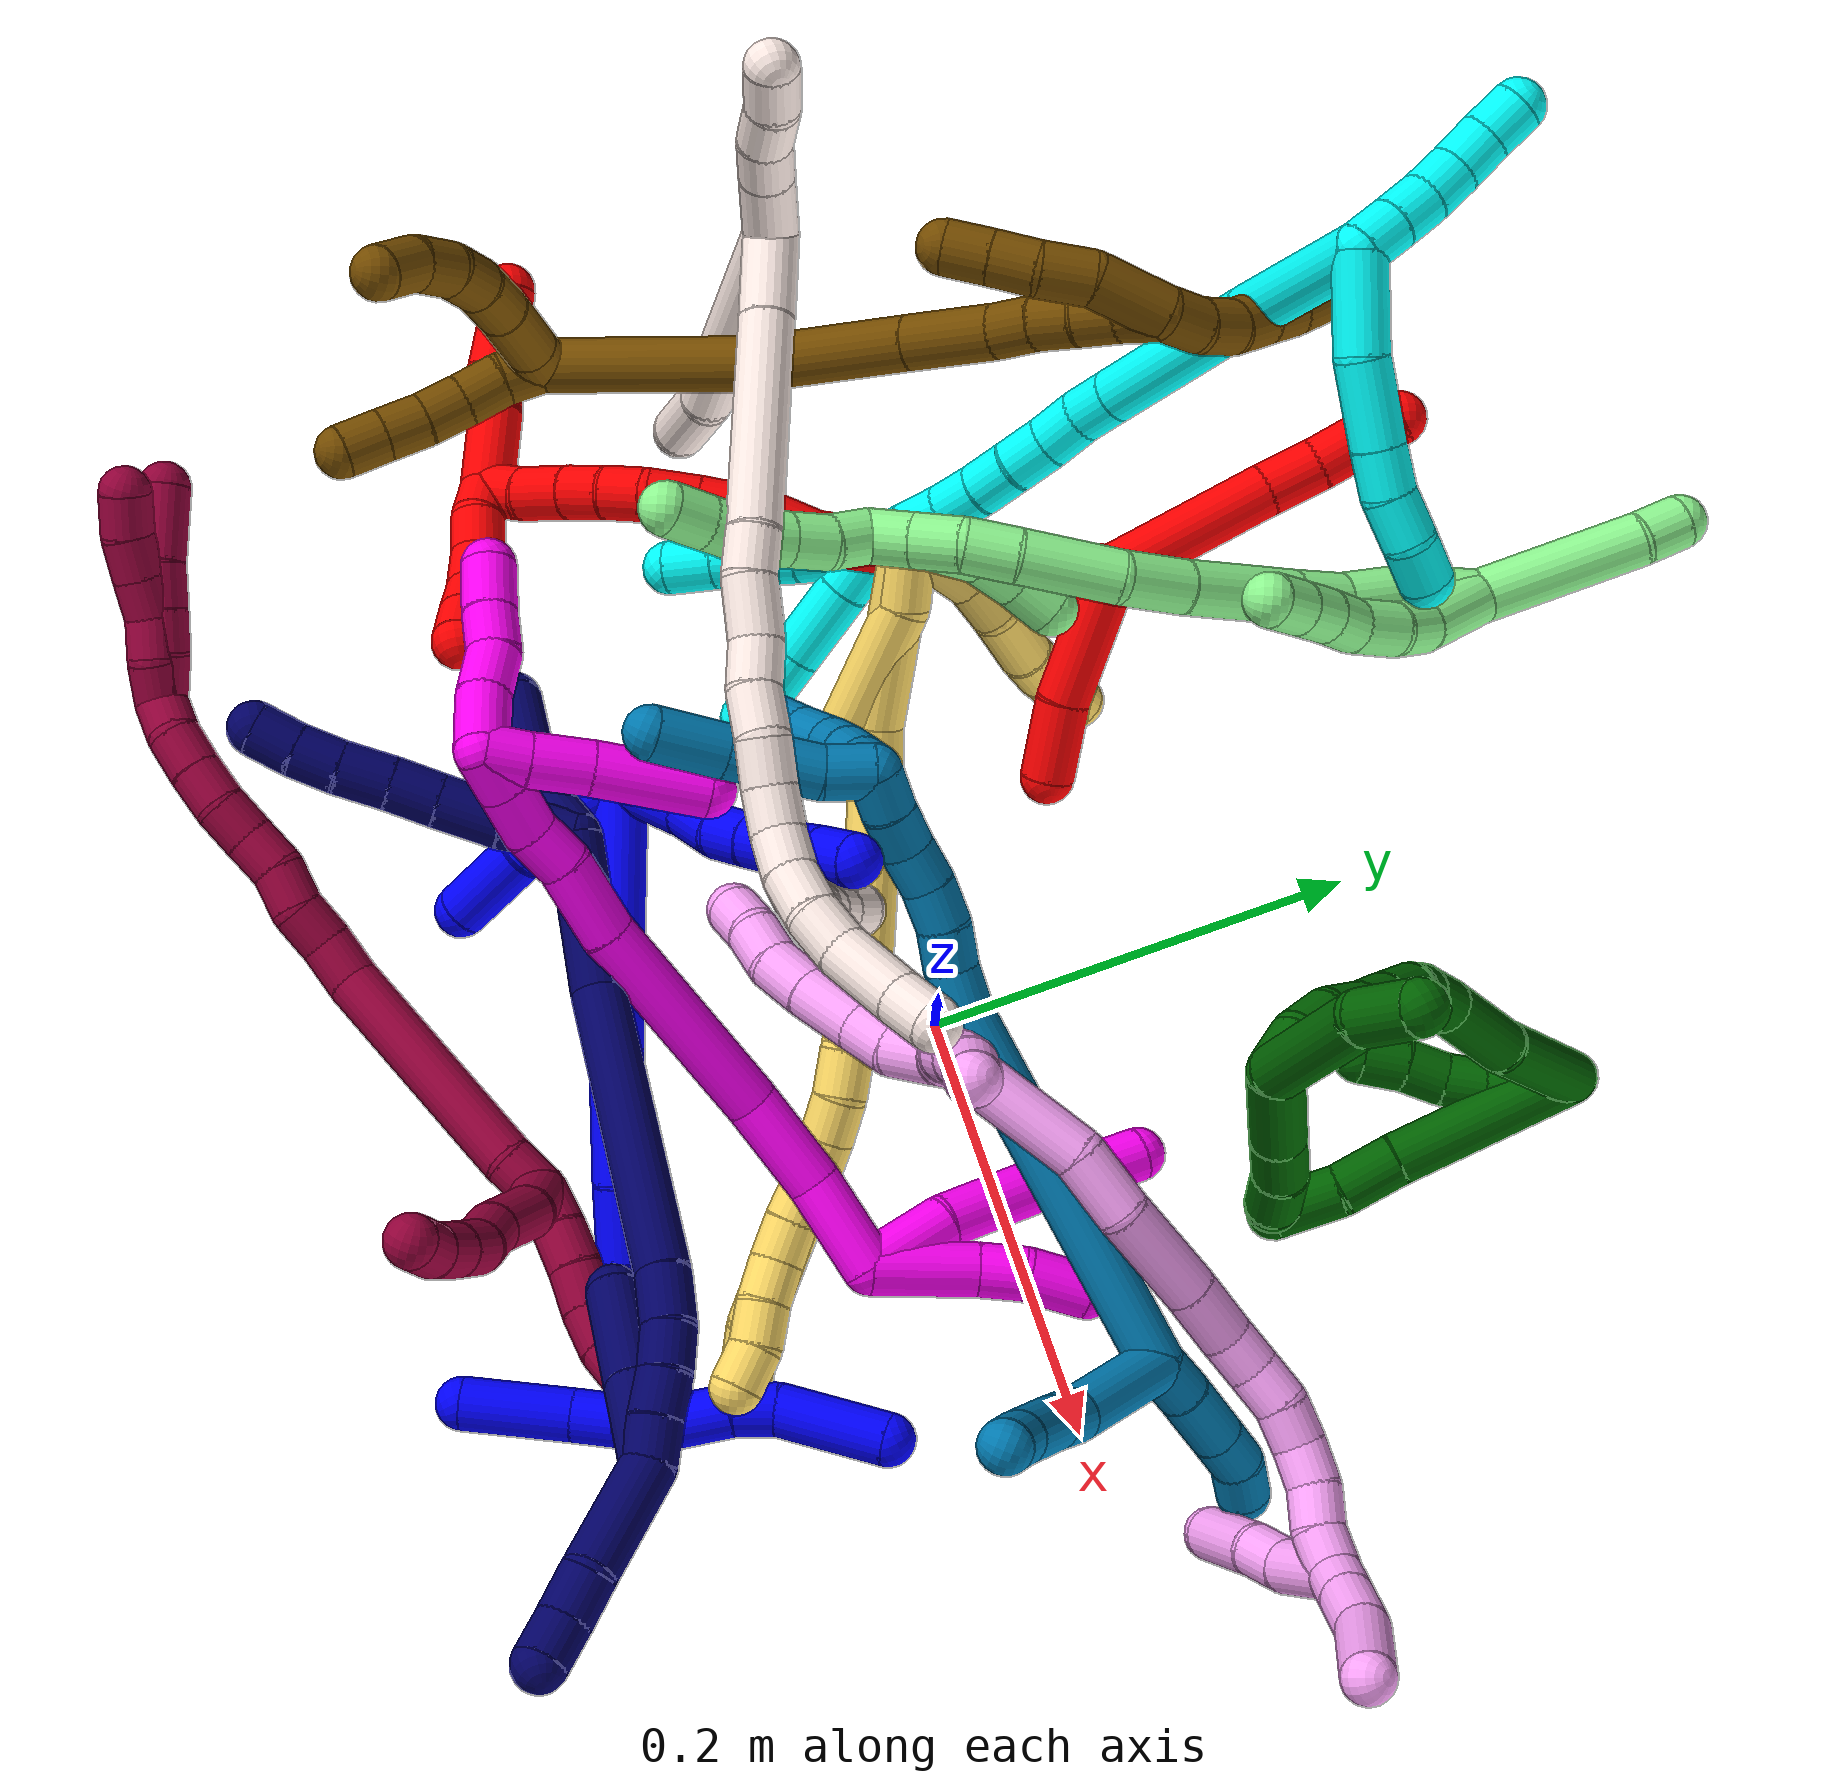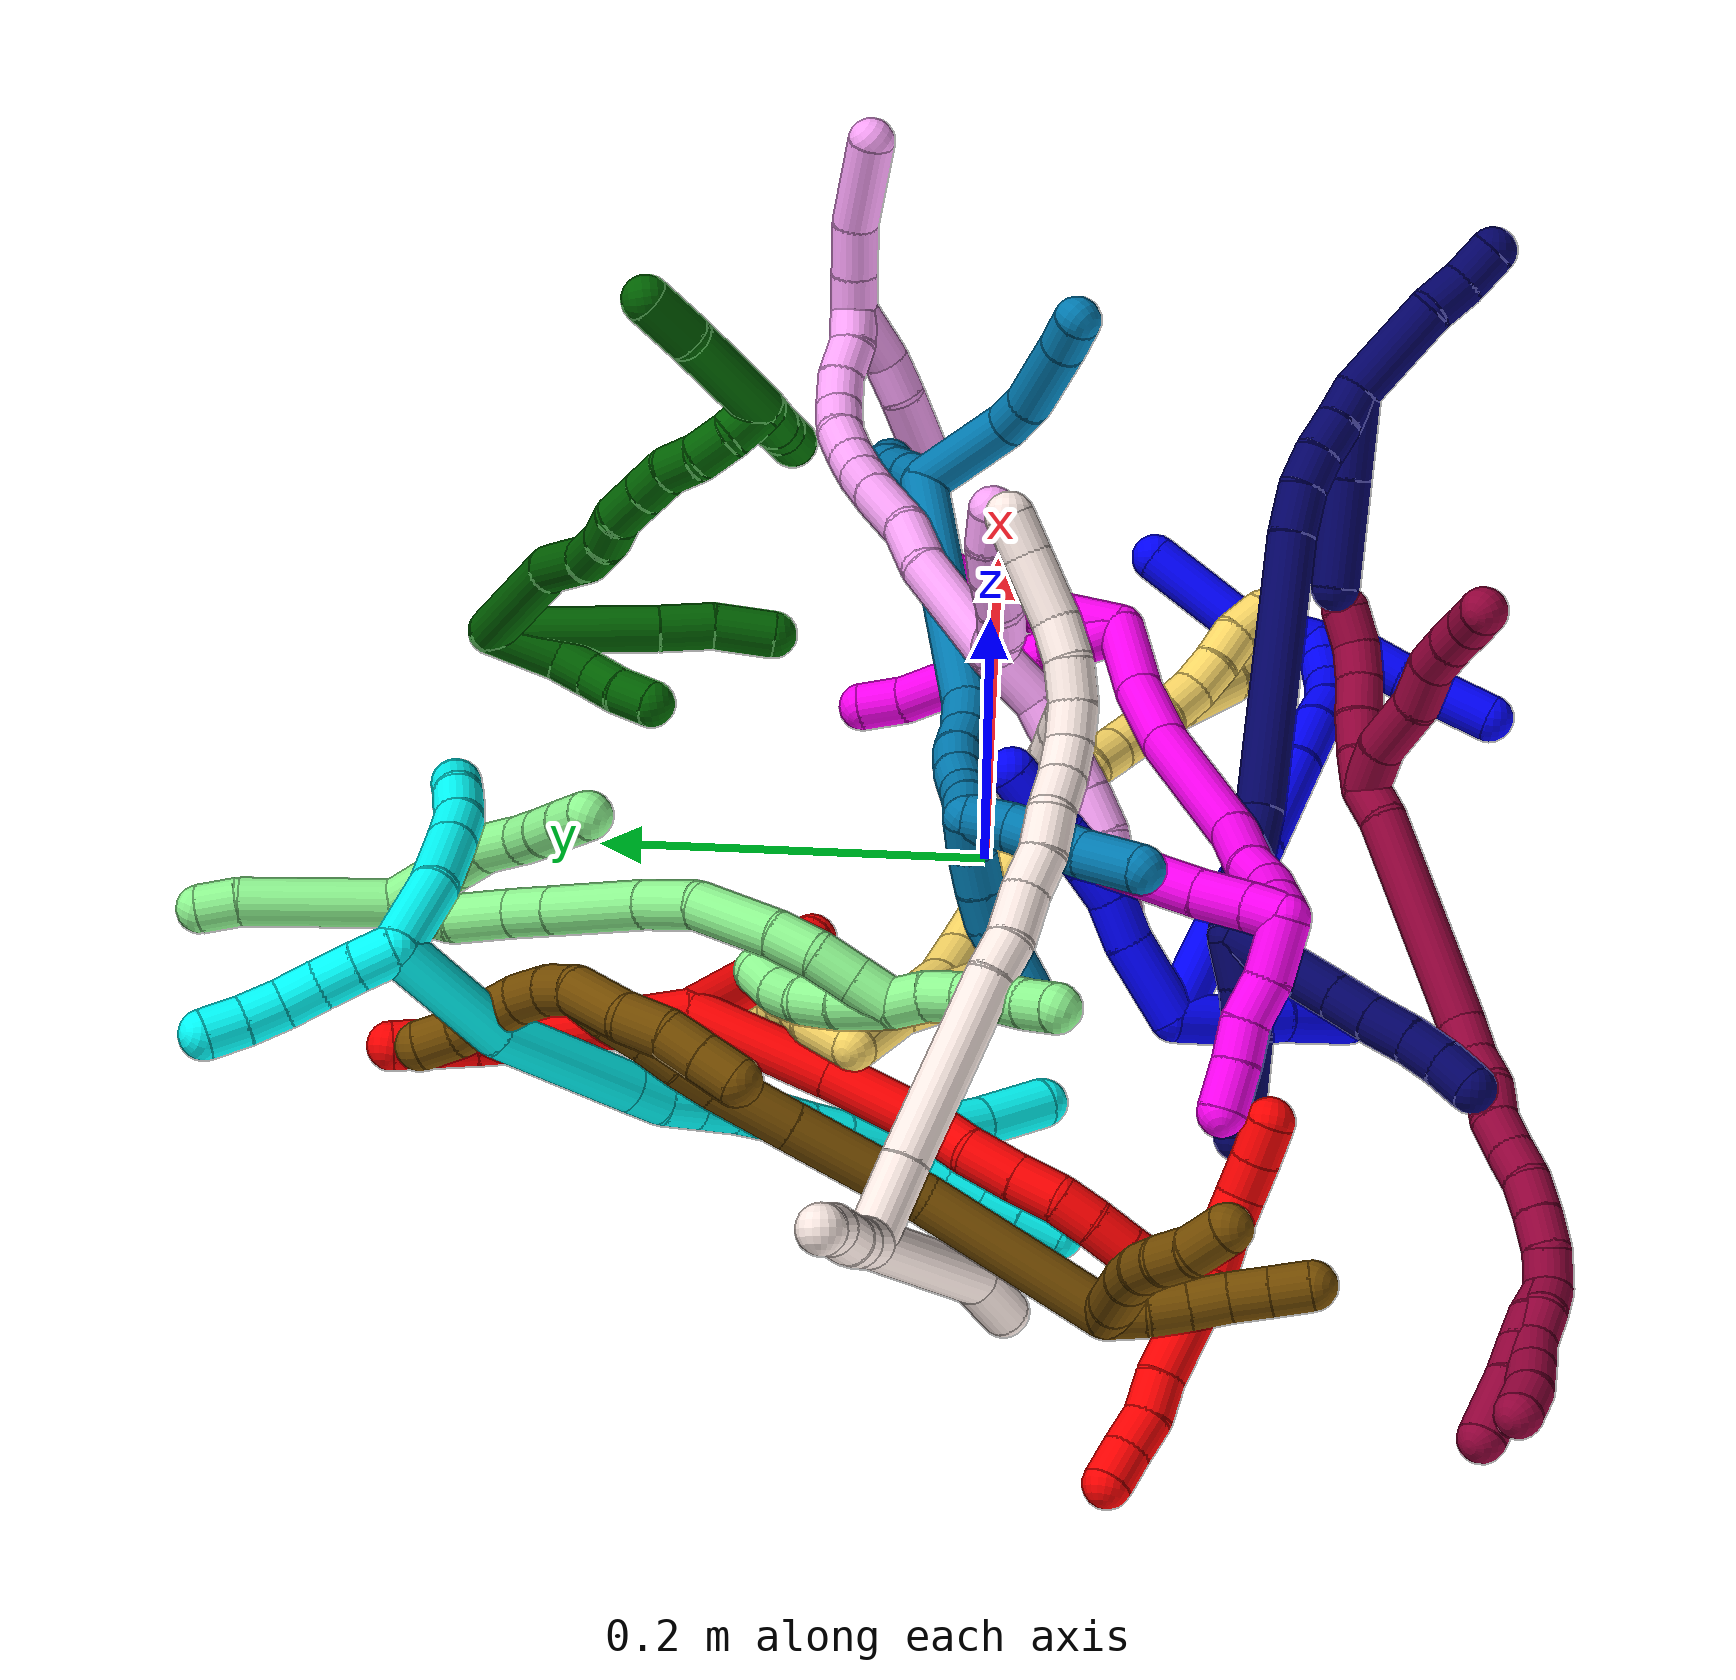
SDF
<sdf version="1.7">
 <world name="default">
  <plugin name="TubeGeneratorPlugin" filename="libtube_generator_plugin.so"/>
  <model name="photoneo_s_sensor">
   <static>1</static>
   <pose>0 0 2 1.57079 1.57079 3.14159</pose>
   <link name="link">
    <inertial><mass>0.1</mass></inertial>
    <sensor name="sensor" type="depth">
     <update_rate>30</update_rate>
     <camera>
      <horizontal_fov>1.22</horizontal_fov>
      <image><width>1920</width><height>1200</height><format>B8G8R8</format></image>
      <clip><near>0.1</near><far>4</far></clip>
      <depth_camera><output>points</output></depth_camera>
     </camera>
     <plugin name="camera_plugin" filename="libgazebo_ros_depth_camera.so">
      <baseline>0.2</baseline>
      <alwaysOn>1</alwaysOn>
      <updateRate>0.0</updateRate>
      <cameraName>camera_ir</cameraName>
      <imageTopicName>/camera/color/image_raw</imageTopicName>
      <cameraInfoTopicName>/camera/color/camera_info</cameraInfoTopicName>
      <depthImageTopicName>/camera/depth/image_raw</depthImageTopicName>
      <depthImageCameraInfoTopicName>/camera/depth/camera_info</depthImageCameraInfoTopicName>
      <pointCloudTopicName>/camera/depth/points</pointCloudTopicName>
      <frameName>fr_optical</frameName>
      <pointCloudCutoff>0.1</pointCloudCutoff>
      <pointCloudCutoffMax>2.0</pointCloudCutoffMax>
      <distortionK1>0</distortionK1>
      <distortionK2>0</distortionK2>
      <distortionK3>0</distortionK3>
      <distortionT1>0</distortionT1>
      <distortionT2>0</distortionT2>
      <CxPrime>0</CxPrime>
      <Cx>0</Cx>
      <Cy>0</Cy>
      <focalLength>0</focalLength>
      <hackBaseline>0</hackBaseline>
     </plugin>
    </sensor>
   </link>
  </model>
  <gravity>0 0 -9.8</gravity>
  <magnetic_field>6e-06 2.3e-05 -4.2e-05</magnetic_field>
  <atmosphere type="adiabatic"/>
  <physics name="default_physics" default="0" type="ode">
   <max_step_size>0.003</max_step_size>
   <real_time_factor>1</real_time_factor>
   <real_time_update_rate>1000</real_time_update_rate>
   <max_contacts>10000</max_contacts>
   <ode>
    <solver>
     <type>quick</type>
     <iters>100</iters>
     <sor>1.3</sor>
     <use_dynamic_moi_rescaling>0</use_dynamic_moi_rescaling>
    </solver>
    <constraints>
     <contact_max_correcting_vel>0</contact_max_correcting_vel>
     <contact_surface_layer>0.001</contact_surface_layer>
     <cfm>0</cfm>
     <erp>0.2</erp>
    </constraints>
   </ode>
  </physics>
  <scene><ambient>0.4 0.4 0.4 1</ambient><background>0.7 0.7 0.7 1</background><shadows>0</shadows></scene>
  <audio><device>default</device></audio>
  <spherical_coordinates>
   <surface_model>EARTH_WGS84</surface_model>
   <latitude_deg>0</latitude_deg>
   <longitude_deg>0</longitude_deg>
   <elevation>0</elevation>
   <heading_deg>0</heading_deg>
  </spherical_coordinates>
  <model name="bin">
   <static>1</static>
   <link name="bottom">
    <collision name="collision-bottom">
     <pose>0 0 -0.01 0 -0 0</pose>
     <geometry><box><size>0.8 0.6 0.02</size></box></geometry>
     <surface>
      <friction><ode><mu>100</mu><mu2>100</mu2></ode></friction>
      <contact><collide_bitmask>65535</collide_bitmask></contact>
     </surface>
    </collision>
   </link>
   <link name="west_wall">
    <collision name="collision-west_wall">
     <pose>-0.41 0 0.1 0 -0 0</pose>
     <geometry><box><size>0.02 0.6 0.2</size></box></geometry>
     <surface>
      <friction><ode><mu>100</mu><mu2>100</mu2></ode></friction>
      <contact><collide_bitmask>65535</collide_bitmask></contact>
     </surface>
    </collision>
   </link>
   <link name="east_wall">
    <collision name="collision-east_wall">
     <pose>0.41 0 0.1 0 -0 0</pose>
     <geometry><box><size>0.02 0.6 0.2</size></box></geometry>
     <surface>
      <friction><ode><mu>100</mu><mu2>100</mu2></ode></friction>
      <contact><collide_bitmask>65535</collide_bitmask></contact>
     </surface>
    </collision>
   </link>
   <link name="south_wall">
    <collision name="collision-south_wall">
     <pose>0 -0.31 0.1 0 -0 0</pose>
     <geometry><box><size>0.8 0.02 0.2</size></box></geometry>
     <surface>
      <friction><ode><mu>100</mu><mu2>100</mu2></ode></friction>
      <contact><collide_bitmask>65535</collide_bitmask></contact>
     </surface>
    </collision>
   </link>
   <link name="north_wall">
    <collision name="collision-north_wall">
     <pose>0 0.31 0.1 0 -0 0</pose>
     <geometry><box><size>0.8 0.02 0.2</size></box></geometry>
     <surface>
      <friction><ode><mu>100</mu><mu2>100</mu2></ode></friction>
      <contact><collide_bitmask>65535</collide_bitmask></contact>
     </surface>
    </collision>
   </link>
  </model>
  <model name="1">
   <static>0</static>
   <link name="1">
    <collision name="collision-cylinder-e_1_2_8">
     <pose>0.014726 0.011237 -0.012282 -2.4006 0.724246 -1.54576</pose>
     <geometry><cylinder><radius>0.0125</radius><length>0.044452</length></cylinder></geometry>
     <surface>
      <friction><ode><mu>1.16</mu><mu2>1.16</mu2><slip1>0</slip1><slip2>0</slip2></ode></friction>
      <contact><ode><kp>1e+06</kp><kd>1</kd><max_vel>0</max_vel><min_depth>0.001</min_depth></ode></contact>
     </surface>
    </collision>
    <visual name="visual-cylinder-e_1_2_8">
     <pose>0.014726 0.011237 -0.012282 -2.4006 0.724246 -1.54576</pose>
     <geometry><cylinder><radius>0.0125</radius><length>0.044452</length></cylinder></geometry>
     <material><ambient>0 0 1 1</ambient></material>
    </visual>
    <collision name="collision-cylinder-e_2_8_9">
     <pose>0.037775 0.030068 -0.029712 -2.16645 0.736786 -1.25849</pose>
     <geometry><cylinder><radius>0.0125</radius><length>0.024773</length></cylinder></geometry>
     <surface>
      <friction><ode><mu>1.16</mu><mu2>1.16</mu2><slip1>0</slip1><slip2>0</slip2></ode></friction>
      <contact><ode><kp>1e+06</kp><kd>1</kd><max_vel>0</max_vel><min_depth>0.001</min_depth></ode></contact>
     </surface>
    </collision>
    <visual name="visual-cylinder-e_2_8_9">
     <pose>0.037775 0.030068 -0.029712 -2.16645 0.736786 -1.25849</pose>
     <geometry><cylinder><radius>0.0125</radius><length>0.024773</length></cylinder></geometry>
     <material><ambient>0 0 1 1</ambient></material>
    </visual>
    <collision name="collision-cylinder-e_3_9_10">
     <pose>0.051733 0.043249 -0.041029 -2.40584 0.595094 -1.34414</pose>
     <geometry><cylinder><radius>0.0125</radius><length>0.020103</length></cylinder></geometry>
     <surface>
      <friction><ode><mu>1.16</mu><mu2>1.16</mu2><slip1>0</slip1><slip2>0</slip2></ode></friction>
      <contact><ode><kp>1e+06</kp><kd>1</kd><max_vel>0</max_vel><min_depth>0.001</min_depth></ode></contact>
     </surface>
    </collision>
    <visual name="visual-cylinder-e_3_9_10">
     <pose>0.051733 0.043249 -0.041029 -2.40584 0.595094 -1.34414</pose>
     <geometry><cylinder><radius>0.0125</radius><length>0.020103</length></cylinder></geometry>
     <material><ambient>0 0 1 1</ambient></material>
    </visual>
    <collision name="collision-cylinder-e_4_10_11">
     <pose>0.062924 0.054044 -0.053878 -2.47911 0.580637 -1.43051</pose>
     <geometry><cylinder><radius>0.0125</radius><length>0.020259</length></cylinder></geometry>
     <surface>
      <friction><ode><mu>1.16</mu><mu2>1.16</mu2><slip1>0</slip1><slip2>0</slip2></ode></friction>
      <contact><ode><kp>1e+06</kp><kd>1</kd><max_vel>0</max_vel><min_depth>0.001</min_depth></ode></contact>
     </surface>
    </collision>
    <visual name="visual-cylinder-e_4_10_11">
     <pose>0.062924 0.054044 -0.053878 -2.47911 0.580637 -1.43051</pose>
     <geometry><cylinder><radius>0.0125</radius><length>0.020259</length></cylinder></geometry>
     <material><ambient>0 0 1 1</ambient></material>
    </visual>
    <collision name="collision-cylinder-e_5_11_12">
     <pose>0.073558 0.064812 -0.067427 -2.46143 0.521463 -1.29219</pose>
     <geometry><cylinder><radius>0.0125</radius><length>0.020386</length></cylinder></geometry>
     <surface>
      <friction><ode><mu>1.16</mu><mu2>1.16</mu2><slip1>0</slip1><slip2>0</slip2></ode></friction>
      <contact><ode><kp>1e+06</kp><kd>1</kd><max_vel>0</max_vel><min_depth>0.001</min_depth></ode></contact>
     </surface>
    </collision>
    <visual name="visual-cylinder-e_5_11_12">
     <pose>0.073558 0.064812 -0.067427 -2.46143 0.521463 -1.29219</pose>
     <geometry><cylinder><radius>0.0125</radius><length>0.020386</length></cylinder></geometry>
     <material><ambient>0 0 1 1</ambient></material>
    </visual>
    <collision name="collision-cylinder-e_6_12_6">
     <pose>0.083867 0.0759 -0.080805 -2.43723 0.549691 -1.30896</pose>
     <geometry><cylinder><radius>0.0125</radius><length>0.020027</length></cylinder></geometry>
     <surface>
      <friction><ode><mu>1.16</mu><mu2>1.16</mu2><slip1>0</slip1><slip2>0</slip2></ode></friction>
      <contact><ode><kp>1e+06</kp><kd>1</kd><max_vel>0</max_vel><min_depth>0.001</min_depth></ode></contact>
     </surface>
    </collision>
    <visual name="visual-cylinder-e_6_12_6">
     <pose>0.083867 0.0759 -0.080805 -2.43723 0.549691 -1.30896</pose>
     <geometry><cylinder><radius>0.0125</radius><length>0.020027</length></cylinder></geometry>
     <material><ambient>0 0 1 1</ambient></material>
    </visual>
    <collision name="collision-cylinder-e_1_2_13">
     <pose>0.001514 -0.003011 0.017569 0.169739 0.084756 0.007215</pose>
     <geometry><cylinder><radius>0.0125</radius><length>0.035779</length></cylinder></geometry>
     <surface>
      <friction><ode><mu>1.16</mu><mu2>1.16</mu2><slip1>0</slip1><slip2>0</slip2></ode></friction>
      <contact><ode><kp>1e+06</kp><kd>1</kd><max_vel>0</max_vel><min_depth>0.001</min_depth></ode></contact>
     </surface>
    </collision>
    <visual name="visual-cylinder-e_1_2_13">
     <pose>0.001514 -0.003011 0.017569 0.169739 0.084756 0.007215</pose>
     <geometry><cylinder><radius>0.0125</radius><length>0.035779</length></cylinder></geometry>
     <material><ambient>0 0 1 1</ambient></material>
    </visual>
    <collision name="collision-cylinder-e_2_13_14">
     <pose>0.006525 -0.00933 0.046021 0.295091 0.298181 0.044641</pose>
     <geometry><cylinder><radius>0.0125</radius><length>0.023799</length></cylinder></geometry>
     <surface>
      <friction><ode><mu>1.16</mu><mu2>1.16</mu2><slip1>0</slip1><slip2>0</slip2></ode></friction>
      <contact><ode><kp>1e+06</kp><kd>1</kd><max_vel>0</max_vel><min_depth>0.001</min_depth></ode></contact>
     </surface>
    </collision>
    <visual name="visual-cylinder-e_2_13_14">
     <pose>0.006525 -0.00933 0.046021 0.295091 0.298181 0.044641</pose>
     <geometry><cylinder><radius>0.0125</radius><length>0.023799</length></cylinder></geometry>
     <material><ambient>0 0 1 1</ambient></material>
    </visual>
    <collision name="collision-cylinder-e_3_14_5">
     <pose>0.014746 -0.020108 0.07508 0.389926 0.236011 0.046814</pose>
     <geometry><cylinder><radius>0.0125</radius><length>0.040422</length></cylinder></geometry>
     <surface>
      <friction><ode><mu>1.16</mu><mu2>1.16</mu2><slip1>0</slip1><slip2>0</slip2></ode></friction>
      <contact><ode><kp>1e+06</kp><kd>1</kd><max_vel>0</max_vel><min_depth>0.001</min_depth></ode></contact>
     </surface>
    </collision>
    <visual name="visual-cylinder-e_3_14_5">
     <pose>0.014746 -0.020108 0.07508 0.389926 0.236011 0.046814</pose>
     <geometry><cylinder><radius>0.0125</radius><length>0.040422</length></cylinder></geometry>
     <material><ambient>0 0 1 1</ambient></material>
    </visual>
    <collision name="collision-cylinder-e_1_2_15">
     <pose>0.034451 -0.000122 0.015715 0.007749 1.14282 0.004983</pose>
     <geometry><cylinder><radius>0.0125</radius><length>0.075732</length></cylinder></geometry>
     <surface>
      <friction><ode><mu>1.16</mu><mu2>1.16</mu2><slip1>0</slip1><slip2>0</slip2></ode></friction>
      <contact><ode><kp>1e+06</kp><kd>1</kd><max_vel>0</max_vel><min_depth>0.001</min_depth></ode></contact>
     </surface>
    </collision>
    <visual name="visual-cylinder-e_1_2_15">
     <pose>0.034451 -0.000122 0.015715 0.007749 1.14282 0.004983</pose>
     <geometry><cylinder><radius>0.0125</radius><length>0.075732</length></cylinder></geometry>
     <material><ambient>0 0 1 1</ambient></material>
    </visual>
    <collision name="collision-cylinder-e_2_15_16">
     <pose>0.089063 -0.003546 0.040897 0.335609 1.10933 0.209132</pose>
     <geometry><cylinder><radius>0.0125</radius><length>0.045034</length></cylinder></geometry>
     <surface>
      <friction><ode><mu>1.16</mu><mu2>1.16</mu2><slip1>0</slip1><slip2>0</slip2></ode></friction>
      <contact><ode><kp>1e+06</kp><kd>1</kd><max_vel>0</max_vel><min_depth>0.001</min_depth></ode></contact>
     </surface>
    </collision>
    <visual name="visual-cylinder-e_2_15_16">
     <pose>0.089063 -0.003546 0.040897 0.335609 1.10933 0.209132</pose>
     <geometry><cylinder><radius>0.0125</radius><length>0.045034</length></cylinder></geometry>
     <material><ambient>0 0 1 1</ambient></material>
    </visual>
    <collision name="collision-cylinder-e_3_16_17">
     <pose>0.137309 -0.010623 0.062214 0.308378 1.15389 0.201616</pose>
     <geometry><cylinder><radius>0.0125</radius><length>0.061429</length></cylinder></geometry>
     <surface>
      <friction><ode><mu>1.16</mu><mu2>1.16</mu2><slip1>0</slip1><slip2>0</slip2></ode></friction>
      <contact><ode><kp>1e+06</kp><kd>1</kd><max_vel>0</max_vel><min_depth>0.001</min_depth></ode></contact>
     </surface>
    </collision>
    <visual name="visual-cylinder-e_3_16_17">
     <pose>0.137309 -0.010623 0.062214 0.308378 1.15389 0.201616</pose>
     <geometry><cylinder><radius>0.0125</radius><length>0.061429</length></cylinder></geometry>
     <material><ambient>0 0 1 1</ambient></material>
    </visual>
    <collision name="collision-cylinder-e_4_17_18">
     <pose>0.180823 -0.01856 0.080377 0.582917 1.11516 0.369879</pose>
     <geometry><cylinder><radius>0.0125</radius><length>0.034368</length></cylinder></geometry>
     <surface>
      <friction><ode><mu>1.16</mu><mu2>1.16</mu2><slip1>0</slip1><slip2>0</slip2></ode></friction>
      <contact><ode><kp>1e+06</kp><kd>1</kd><max_vel>0</max_vel><min_depth>0.001</min_depth></ode></contact>
     </surface>
    </collision>
    <visual name="visual-cylinder-e_4_17_18">
     <pose>0.180823 -0.01856 0.080377 0.582917 1.11516 0.369879</pose>
     <geometry><cylinder><radius>0.0125</radius><length>0.034368</length></cylinder></geometry>
     <material><ambient>0 0 1 1</ambient></material>
    </visual>
    <collision name="collision-cylinder-e_5_18_19">
     <pose>0.205101 -0.026054 0.090912 0.668141 1.02456 0.385518</pose>
     <geometry><cylinder><radius>0.0125</radius><length>0.020707</length></cylinder></geometry>
     <surface>
      <friction><ode><mu>1.16</mu><mu2>1.16</mu2><slip1>0</slip1><slip2>0</slip2></ode></friction>
      <contact><ode><kp>1e+06</kp><kd>1</kd><max_vel>0</max_vel><min_depth>0.001</min_depth></ode></contact>
     </surface>
    </collision>
    <visual name="visual-cylinder-e_5_18_19">
     <pose>0.205101 -0.026054 0.090912 0.668141 1.02456 0.385518</pose>
     <geometry><cylinder><radius>0.0125</radius><length>0.020707</length></cylinder></geometry>
     <material><ambient>0 0 1 1</ambient></material>
    </visual>
    <collision name="collision-cylinder-e_6_19_20">
     <pose>0.223095 -0.034319 0.096539 1.29329 1.05975 0.832686</pose>
     <geometry><cylinder><radius>0.0125</radius><length>0.020973</length></cylinder></geometry>
     <surface>
      <friction><ode><mu>1.16</mu><mu2>1.16</mu2><slip1>0</slip1><slip2>0</slip2></ode></friction>
      <contact><ode><kp>1e+06</kp><kd>1</kd><max_vel>0</max_vel><min_depth>0.001</min_depth></ode></contact>
     </surface>
    </collision>
    <visual name="visual-cylinder-e_6_19_20">
     <pose>0.223095 -0.034319 0.096539 1.29329 1.05975 0.832686</pose>
     <geometry><cylinder><radius>0.0125</radius><length>0.020973</length></cylinder></geometry>
     <material><ambient>0 0 1 1</ambient></material>
    </visual>
    <collision name="collision-cylinder-e_7_20_21">
     <pose>0.242193 -0.043461 0.097928 1.57461 1.17058 1.17409</pose>
     <geometry><cylinder><radius>0.0125</radius><length>0.021611</length></cylinder></geometry>
     <surface>
      <friction><ode><mu>1.16</mu><mu2>1.16</mu2><slip1>0</slip1><slip2>0</slip2></ode></friction>
      <contact><ode><kp>1e+06</kp><kd>1</kd><max_vel>0</max_vel><min_depth>0.001</min_depth></ode></contact>
     </surface>
    </collision>
    <visual name="visual-cylinder-e_7_20_21">
     <pose>0.242193 -0.043461 0.097928 1.57461 1.17058 1.17409</pose>
     <geometry><cylinder><radius>0.0125</radius><length>0.021611</length></cylinder></geometry>
     <material><ambient>0 0 1 1</ambient></material>
    </visual>
    <collision name="collision-cylinder-e_8_21_1">
     <pose>0.261501 -0.051388 0.097571 1.66241 1.1912 1.27778</pose>
     <geometry><cylinder><radius>0.0125</radius><length>0.020146</length></cylinder></geometry>
     <surface>
      <friction><ode><mu>1.16</mu><mu2>1.16</mu2><slip1>0</slip1><slip2>0</slip2></ode></friction>
      <contact><ode><kp>1e+06</kp><kd>1</kd><max_vel>0</max_vel><min_depth>0.001</min_depth></ode></contact>
     </surface>
    </collision>
    <visual name="visual-cylinder-e_8_21_1">
     <pose>0.261501 -0.051388 0.097571 1.66241 1.1912 1.27778</pose>
     <geometry><cylinder><radius>0.0125</radius><length>0.020146</length></cylinder></geometry>
     <material><ambient>0 0 1 1</ambient></material>
    </visual>
    <collision name="collision-cylinder-e_1_1_22">
     <pose>0.265547 -0.052586 0.109187 -0.207603 -0.409905 0.043304</pose>
     <geometry><cylinder><radius>0.0125</radius><length>0.026647</length></cylinder></geometry>
     <surface>
      <friction><ode><mu>1.16</mu><mu2>1.16</mu2><slip1>0</slip1><slip2>0</slip2></ode></friction>
      <contact><ode><kp>1e+06</kp><kd>1</kd><max_vel>0</max_vel><min_depth>0.001</min_depth></ode></contact>
     </surface>
    </collision>
    <visual name="visual-cylinder-e_1_1_22">
     <pose>0.265547 -0.052586 0.109187 -0.207603 -0.409905 0.043304</pose>
     <geometry><cylinder><radius>0.0125</radius><length>0.026647</length></cylinder></geometry>
     <material><ambient>0 0 1 1</ambient></material>
    </visual>
    <collision name="collision-cylinder-e_2_22_23">
     <pose>0.254817 -0.050811 0.130379 0.080343 -0.529288 -0.021784</pose>
     <geometry><cylinder><radius>0.0125</radius><length>0.021467</length></cylinder></geometry>
     <surface>
      <friction><ode><mu>1.16</mu><mu2>1.16</mu2><slip1>0</slip1><slip2>0</slip2></ode></friction>
      <contact><ode><kp>1e+06</kp><kd>1</kd><max_vel>0</max_vel><min_depth>0.001</min_depth></ode></contact>
     </surface>
    </collision>
    <visual name="visual-cylinder-e_2_22_23">
     <pose>0.254817 -0.050811 0.130379 0.080343 -0.529288 -0.021784</pose>
     <geometry><cylinder><radius>0.0125</radius><length>0.021467</length></cylinder></geometry>
     <material><ambient>0 0 1 1</ambient></material>
    </visual>
    <collision name="collision-cylinder-e_3_23_4">
     <pose>0.236581 -0.051113 0.162166 -0.019588 -0.516737 0.005177</pose>
     <geometry><cylinder><radius>0.0125</radius><length>0.051885</length></cylinder></geometry>
     <surface>
      <friction><ode><mu>1.16</mu><mu2>1.16</mu2><slip1>0</slip1><slip2>0</slip2></ode></friction>
      <contact><ode><kp>1e+06</kp><kd>1</kd><max_vel>0</max_vel><min_depth>0.001</min_depth></ode></contact>
     </surface>
    </collision>
    <visual name="visual-cylinder-e_3_23_4">
     <pose>0.236581 -0.051113 0.162166 -0.019588 -0.516737 0.005177</pose>
     <geometry><cylinder><radius>0.0125</radius><length>0.051885</length></cylinder></geometry>
     <material><ambient>0 0 1 1</ambient></material>
    </visual>
    <collision name="collision-cylinder-e_1_1_24">
     <pose>0.273639 -0.054055 0.08451 -3.05925 0.214673 -2.4113</pose>
     <geometry><cylinder><radius>0.0125</radius><length>0.026125</length></cylinder></geometry>
     <surface>
      <friction><ode><mu>1.16</mu><mu2>1.16</mu2><slip1>0</slip1><slip2>0</slip2></ode></friction>
      <contact><ode><kp>1e+06</kp><kd>1</kd><max_vel>0</max_vel><min_depth>0.001</min_depth></ode></contact>
     </surface>
    </collision>
    <visual name="visual-cylinder-e_1_1_24">
     <pose>0.273639 -0.054055 0.08451 -3.05925 0.214673 -2.4113</pose>
     <geometry><cylinder><radius>0.0125</radius><length>0.026125</length></cylinder></geometry>
     <material><ambient>0 0 1 1</ambient></material>
    </visual>
    <collision name="collision-cylinder-e_2_24_25">
     <pose>0.280357 -0.053688 0.062412 3.06898 0.396311 2.78366</pose>
     <geometry><cylinder><radius>0.0125</radius><length>0.020388</length></cylinder></geometry>
     <surface>
      <friction><ode><mu>1.16</mu><mu2>1.16</mu2><slip1>0</slip1><slip2>0</slip2></ode></friction>
      <contact><ode><kp>1e+06</kp><kd>1</kd><max_vel>0</max_vel><min_depth>0.001</min_depth></ode></contact>
     </surface>
    </collision>
    <visual name="visual-cylinder-e_2_24_25">
     <pose>0.280357 -0.053688 0.062412 3.06898 0.396311 2.78366</pose>
     <geometry><cylinder><radius>0.0125</radius><length>0.020388</length></cylinder></geometry>
     <material><ambient>0 0 1 1</ambient></material>
    </visual>
    <collision name="collision-cylinder-e_3_25_3">
     <pose>0.300799 -0.050886 0.032282 -2.97524 0.665228 -2.66798</pose>
     <geometry><cylinder><radius>0.0125</radius><length>0.053487</length></cylinder></geometry>
     <surface>
      <friction><ode><mu>1.16</mu><mu2>1.16</mu2><slip1>0</slip1><slip2>0</slip2></ode></friction>
      <contact><ode><kp>1e+06</kp><kd>1</kd><max_vel>0</max_vel><min_depth>0.001</min_depth></ode></contact>
     </surface>
    </collision>
    <visual name="visual-cylinder-e_3_25_3">
     <pose>0.300799 -0.050886 0.032282 -2.97524 0.665228 -2.66798</pose>
     <geometry><cylinder><radius>0.0125</radius><length>0.053487</length></cylinder></geometry>
     <material><ambient>0 0 1 1</ambient></material>
    </visual>
    <collision name="collision-sphere-3">
     <pose>0.317306 -0.047402 0.011531 0 -0 0</pose>
     <geometry><sphere><radius>0.0125</radius></sphere></geometry>
     <surface>
      <friction><ode><mu>1.16</mu><mu2>1.16</mu2><slip1>0</slip1><slip2>0</slip2></ode></friction>
      <contact><ode><kp>1e+06</kp><kd>1</kd><max_vel>0</max_vel><min_depth>0.001</min_depth></ode></contact>
     </surface>
    </collision>
    <visual name="visual-sphere-3">
     <pose>0.317306 -0.047402 0.011531 0 -0 0</pose>
     <geometry><sphere><radius>0.0125</radius></sphere></geometry>
     <material><ambient>0 0 1 1</ambient></material>
    </visual>
    <collision name="collision-sphere-25">
     <pose>0.284292 -0.05437 0.053032 0 -0 0</pose>
     <geometry><sphere><radius>0.0125</radius></sphere></geometry>
     <surface>
      <friction><ode><mu>1.16</mu><mu2>1.16</mu2><slip1>0</slip1><slip2>0</slip2></ode></friction>
      <contact><ode><kp>1e+06</kp><kd>1</kd><max_vel>0</max_vel><min_depth>0.001</min_depth></ode></contact>
     </surface>
    </collision>
    <visual name="visual-sphere-25">
     <pose>0.284292 -0.05437 0.053032 0 -0 0</pose>
     <geometry><sphere><radius>0.0125</radius></sphere></geometry>
     <material><ambient>0 0 1 1</ambient></material>
    </visual>
    <collision name="collision-sphere-24">
     <pose>0.276422 -0.053006 0.071791 0 -0 0</pose>
     <geometry><sphere><radius>0.0125</radius></sphere></geometry>
     <surface>
      <friction><ode><mu>1.16</mu><mu2>1.16</mu2><slip1>0</slip1><slip2>0</slip2></ode></friction>
      <contact><ode><kp>1e+06</kp><kd>1</kd><max_vel>0</max_vel><min_depth>0.001</min_depth></ode></contact>
     </surface>
    </collision>
    <visual name="visual-sphere-24">
     <pose>0.276422 -0.053006 0.071791 0 -0 0</pose>
     <geometry><sphere><radius>0.0125</radius></sphere></geometry>
     <material><ambient>0 0 1 1</ambient></material>
    </visual>
    <collision name="collision-sphere-4">
     <pose>0.223764 -0.050671 0.184717 0 -0 0</pose>
     <geometry><sphere><radius>0.0125</radius></sphere></geometry>
     <surface>
      <friction><ode><mu>1.16</mu><mu2>1.16</mu2><slip1>0</slip1><slip2>0</slip2></ode></friction>
      <contact><ode><kp>1e+06</kp><kd>1</kd><max_vel>0</max_vel><min_depth>0.001</min_depth></ode></contact>
     </surface>
    </collision>
    <visual name="visual-sphere-4">
     <pose>0.223764 -0.050671 0.184717 0 -0 0</pose>
     <geometry><sphere><radius>0.0125</radius></sphere></geometry>
     <material><ambient>0 0 1 1</ambient></material>
    </visual>
    <collision name="collision-sphere-23">
     <pose>0.249398 -0.051555 0.139615 0 -0 0</pose>
     <geometry><sphere><radius>0.0125</radius></sphere></geometry>
     <surface>
      <friction><ode><mu>1.16</mu><mu2>1.16</mu2><slip1>0</slip1><slip2>0</slip2></ode></friction>
      <contact><ode><kp>1e+06</kp><kd>1</kd><max_vel>0</max_vel><min_depth>0.001</min_depth></ode></contact>
     </surface>
    </collision>
    <visual name="visual-sphere-23">
     <pose>0.249398 -0.051555 0.139615 0 -0 0</pose>
     <geometry><sphere><radius>0.0125</radius></sphere></geometry>
     <material><ambient>0 0 1 1</ambient></material>
    </visual>
    <collision name="collision-sphere-22">
     <pose>0.260237 -0.050068 0.121144 0 -0 0</pose>
     <geometry><sphere><radius>0.0125</radius></sphere></geometry>
     <surface>
      <friction><ode><mu>1.16</mu><mu2>1.16</mu2><slip1>0</slip1><slip2>0</slip2></ode></friction>
      <contact><ode><kp>1e+06</kp><kd>1</kd><max_vel>0</max_vel><min_depth>0.001</min_depth></ode></contact>
     </surface>
    </collision>
    <visual name="visual-sphere-22">
     <pose>0.260237 -0.050068 0.121144 0 -0 0</pose>
     <geometry><sphere><radius>0.0125</radius></sphere></geometry>
     <material><ambient>0 0 1 1</ambient></material>
    </visual>
    <collision name="collision-sphere-1">
     <pose>0.270856 -0.055105 0.097229 0 -0 0</pose>
     <geometry><sphere><radius>0.0125</radius></sphere></geometry>
     <surface>
      <friction><ode><mu>1.16</mu><mu2>1.16</mu2><slip1>0</slip1><slip2>0</slip2></ode></friction>
      <contact><ode><kp>1e+06</kp><kd>1</kd><max_vel>0</max_vel><min_depth>0.001</min_depth></ode></contact>
     </surface>
    </collision>
    <visual name="visual-sphere-1">
     <pose>0.270856 -0.055105 0.097229 0 -0 0</pose>
     <geometry><sphere><radius>0.0125</radius></sphere></geometry>
     <material><ambient>0 0 1 1</ambient></material>
    </visual>
    <collision name="collision-sphere-21">
     <pose>0.252145 -0.047671 0.097912 0 -0 0</pose>
     <geometry><sphere><radius>0.0125</radius></sphere></geometry>
     <surface>
      <friction><ode><mu>1.16</mu><mu2>1.16</mu2><slip1>0</slip1><slip2>0</slip2></ode></friction>
      <contact><ode><kp>1e+06</kp><kd>1</kd><max_vel>0</max_vel><min_depth>0.001</min_depth></ode></contact>
     </surface>
    </collision>
    <visual name="visual-sphere-21">
     <pose>0.252145 -0.047671 0.097912 0 -0 0</pose>
     <geometry><sphere><radius>0.0125</radius></sphere></geometry>
     <material><ambient>0 0 1 1</ambient></material>
    </visual>
    <collision name="collision-sphere-12">
     <pose>0.078636 0.070371 -0.074298 0 -0 0</pose>
     <geometry><sphere><radius>0.0125</radius></sphere></geometry>
     <surface>
      <friction><ode><mu>1.16</mu><mu2>1.16</mu2><slip1>0</slip1><slip2>0</slip2></ode></friction>
      <contact><ode><kp>1e+06</kp><kd>1</kd><max_vel>0</max_vel><min_depth>0.001</min_depth></ode></contact>
     </surface>
    </collision>
    <visual name="visual-sphere-12">
     <pose>0.078636 0.070371 -0.074298 0 -0 0</pose>
     <geometry><sphere><radius>0.0125</radius></sphere></geometry>
     <material><ambient>0 0 1 1</ambient></material>
    </visual>
    <collision name="collision-sphere-11">
     <pose>0.068481 0.059254 -0.060556 0 -0 0</pose>
     <geometry><sphere><radius>0.0125</radius></sphere></geometry>
     <surface>
      <friction><ode><mu>1.16</mu><mu2>1.16</mu2><slip1>0</slip1><slip2>0</slip2></ode></friction>
      <contact><ode><kp>1e+06</kp><kd>1</kd><max_vel>0</max_vel><min_depth>0.001</min_depth></ode></contact>
     </surface>
    </collision>
    <visual name="visual-sphere-11">
     <pose>0.068481 0.059254 -0.060556 0 -0 0</pose>
     <geometry><sphere><radius>0.0125</radius></sphere></geometry>
     <material><ambient>0 0 1 1</ambient></material>
    </visual>
    <collision name="collision-sphere-10">
     <pose>0.057367 0.048835 -0.0472 0 -0 0</pose>
     <geometry><sphere><radius>0.0125</radius></sphere></geometry>
     <surface>
      <friction><ode><mu>1.16</mu><mu2>1.16</mu2><slip1>0</slip1><slip2>0</slip2></ode></friction>
      <contact><ode><kp>1e+06</kp><kd>1</kd><max_vel>0</max_vel><min_depth>0.001</min_depth></ode></contact>
     </surface>
    </collision>
    <visual name="visual-sphere-10">
     <pose>0.057367 0.048835 -0.0472 0 -0 0</pose>
     <geometry><sphere><radius>0.0125</radius></sphere></geometry>
     <material><ambient>0 0 1 1</ambient></material>
    </visual>
    <collision name="collision-sphere-9">
     <pose>0.046098 0.037662 -0.034859 0 -0 0</pose>
     <geometry><sphere><radius>0.0125</radius></sphere></geometry>
     <surface>
      <friction><ode><mu>1.16</mu><mu2>1.16</mu2><slip1>0</slip1><slip2>0</slip2></ode></friction>
      <contact><ode><kp>1e+06</kp><kd>1</kd><max_vel>0</max_vel><min_depth>0.001</min_depth></ode></contact>
     </surface>
    </collision>
    <visual name="visual-sphere-9">
     <pose>0.046098 0.037662 -0.034859 0 -0 0</pose>
     <geometry><sphere><radius>0.0125</radius></sphere></geometry>
     <material><ambient>0 0 1 1</ambient></material>
    </visual>
    <collision name="collision-sphere-2">
     <geometry><sphere><radius>0.0125</radius></sphere></geometry>
     <surface>
      <friction><ode><mu>1.16</mu><mu2>1.16</mu2><slip1>0</slip1><slip2>0</slip2></ode></friction>
      <contact><ode><kp>1e+06</kp><kd>1</kd><max_vel>0</max_vel><min_depth>0.001</min_depth></ode></contact>
     </surface>
    </collision>
    <visual name="visual-sphere-2">
     <geometry><sphere><radius>0.0125</radius></sphere></geometry>
     <material><ambient>0 0 1 1</ambient></material>
    </visual>
    <collision name="collision-sphere-19">
     <pose>0.213948 -0.029386 0.095134 0 -0 0</pose>
     <geometry><sphere><radius>0.0125</radius></sphere></geometry>
     <surface>
      <friction><ode><mu>1.16</mu><mu2>1.16</mu2><slip1>0</slip1><slip2>0</slip2></ode></friction>
      <contact><ode><kp>1e+06</kp><kd>1</kd><max_vel>0</max_vel><min_depth>0.001</min_depth></ode></contact>
     </surface>
    </collision>
    <visual name="visual-sphere-19">
     <pose>0.213948 -0.029386 0.095134 0 -0 0</pose>
     <geometry><sphere><radius>0.0125</radius></sphere></geometry>
     <material><ambient>0 0 1 1</ambient></material>
    </visual>
    <collision name="collision-sphere-8">
     <pose>0.029453 0.022474 -0.024565 0 -0 0</pose>
     <geometry><sphere><radius>0.0125</radius></sphere></geometry>
     <surface>
      <friction><ode><mu>1.16</mu><mu2>1.16</mu2><slip1>0</slip1><slip2>0</slip2></ode></friction>
      <contact><ode><kp>1e+06</kp><kd>1</kd><max_vel>0</max_vel><min_depth>0.001</min_depth></ode></contact>
     </surface>
    </collision>
    <visual name="visual-sphere-8">
     <pose>0.029453 0.022474 -0.024565 0 -0 0</pose>
     <geometry><sphere><radius>0.0125</radius></sphere></geometry>
     <material><ambient>0 0 1 1</ambient></material>
    </visual>
    <collision name="collision-sphere-6">
     <pose>0.089098 0.081429 -0.087311 0 -0 0</pose>
     <geometry><sphere><radius>0.0125</radius></sphere></geometry>
     <surface>
      <friction><ode><mu>1.16</mu><mu2>1.16</mu2><slip1>0</slip1><slip2>0</slip2></ode></friction>
      <contact><ode><kp>1e+06</kp><kd>1</kd><max_vel>0</max_vel><min_depth>0.001</min_depth></ode></contact>
     </surface>
    </collision>
    <visual name="visual-sphere-6">
     <pose>0.089098 0.081429 -0.087311 0 -0 0</pose>
     <geometry><sphere><radius>0.0125</radius></sphere></geometry>
     <material><ambient>0 0 1 1</ambient></material>
    </visual>
    <collision name="collision-sphere-13">
     <pose>0.003029 -0.006022 0.035139 0 -0 0</pose>
     <geometry><sphere><radius>0.0125</radius></sphere></geometry>
     <surface>
      <friction><ode><mu>1.16</mu><mu2>1.16</mu2><slip1>0</slip1><slip2>0</slip2></ode></friction>
      <contact><ode><kp>1e+06</kp><kd>1</kd><max_vel>0</max_vel><min_depth>0.001</min_depth></ode></contact>
     </surface>
    </collision>
    <visual name="visual-sphere-13">
     <pose>0.003029 -0.006022 0.035139 0 -0 0</pose>
     <geometry><sphere><radius>0.0125</radius></sphere></geometry>
     <material><ambient>0 0 1 1</ambient></material>
    </visual>
    <collision name="collision-sphere-14">
     <pose>0.010021 -0.012638 0.056904 0 -0 0</pose>
     <geometry><sphere><radius>0.0125</radius></sphere></geometry>
     <surface>
      <friction><ode><mu>1.16</mu><mu2>1.16</mu2><slip1>0</slip1><slip2>0</slip2></ode></friction>
      <contact><ode><kp>1e+06</kp><kd>1</kd><max_vel>0</max_vel><min_depth>0.001</min_depth></ode></contact>
     </surface>
    </collision>
    <visual name="visual-sphere-14">
     <pose>0.010021 -0.012638 0.056904 0 -0 0</pose>
     <geometry><sphere><radius>0.0125</radius></sphere></geometry>
     <material><ambient>0 0 1 1</ambient></material>
    </visual>
    <collision name="collision-sphere-5">
     <pose>0.019472 -0.027577 0.093255 0 -0 0</pose>
     <geometry><sphere><radius>0.0125</radius></sphere></geometry>
     <surface>
      <friction><ode><mu>1.16</mu><mu2>1.16</mu2><slip1>0</slip1><slip2>0</slip2></ode></friction>
      <contact><ode><kp>1e+06</kp><kd>1</kd><max_vel>0</max_vel><min_depth>0.001</min_depth></ode></contact>
     </surface>
    </collision>
    <visual name="visual-sphere-5">
     <pose>0.019472 -0.027577 0.093255 0 -0 0</pose>
     <geometry><sphere><radius>0.0125</radius></sphere></geometry>
     <material><ambient>0 0 1 1</ambient></material>
    </visual>
    <collision name="collision-sphere-15">
     <pose>0.068901 -0.000244 0.03143 0 -0 0</pose>
     <geometry><sphere><radius>0.0125</radius></sphere></geometry>
     <surface>
      <friction><ode><mu>1.16</mu><mu2>1.16</mu2><slip1>0</slip1><slip2>0</slip2></ode></friction>
      <contact><ode><kp>1e+06</kp><kd>1</kd><max_vel>0</max_vel><min_depth>0.001</min_depth></ode></contact>
     </surface>
    </collision>
    <visual name="visual-sphere-15">
     <pose>0.068901 -0.000244 0.03143 0 -0 0</pose>
     <geometry><sphere><radius>0.0125</radius></sphere></geometry>
     <material><ambient>0 0 1 1</ambient></material>
    </visual>
    <collision name="collision-sphere-16">
     <pose>0.109225 -0.006848 0.050364 0 -0 0</pose>
     <geometry><sphere><radius>0.0125</radius></sphere></geometry>
     <surface>
      <friction><ode><mu>1.16</mu><mu2>1.16</mu2><slip1>0</slip1><slip2>0</slip2></ode></friction>
      <contact><ode><kp>1e+06</kp><kd>1</kd><max_vel>0</max_vel><min_depth>0.001</min_depth></ode></contact>
     </surface>
    </collision>
    <visual name="visual-sphere-16">
     <pose>0.109225 -0.006848 0.050364 0 -0 0</pose>
     <geometry><sphere><radius>0.0125</radius></sphere></geometry>
     <material><ambient>0 0 1 1</ambient></material>
    </visual>
    <collision name="collision-sphere-17">
     <pose>0.165392 -0.014397 0.074065 0 -0 0</pose>
     <geometry><sphere><radius>0.0125</radius></sphere></geometry>
     <surface>
      <friction><ode><mu>1.16</mu><mu2>1.16</mu2><slip1>0</slip1><slip2>0</slip2></ode></friction>
      <contact><ode><kp>1e+06</kp><kd>1</kd><max_vel>0</max_vel><min_depth>0.001</min_depth></ode></contact>
     </surface>
    </collision>
    <visual name="visual-sphere-17">
     <pose>0.165392 -0.014397 0.074065 0 -0 0</pose>
     <geometry><sphere><radius>0.0125</radius></sphere></geometry>
     <material><ambient>0 0 1 1</ambient></material>
    </visual>
    <collision name="collision-sphere-18">
     <pose>0.196254 -0.022722 0.08669 0 -0 0</pose>
     <geometry><sphere><radius>0.0125</radius></sphere></geometry>
     <surface>
      <friction><ode><mu>1.16</mu><mu2>1.16</mu2><slip1>0</slip1><slip2>0</slip2></ode></friction>
      <contact><ode><kp>1e+06</kp><kd>1</kd><max_vel>0</max_vel><min_depth>0.001</min_depth></ode></contact>
     </surface>
    </collision>
    <visual name="visual-sphere-18">
     <pose>0.196254 -0.022722 0.08669 0 -0 0</pose>
     <geometry><sphere><radius>0.0125</radius></sphere></geometry>
     <material><ambient>0 0 1 1</ambient></material>
    </visual>
    <collision name="collision-sphere-20">
     <pose>0.232242 -0.039252 0.097944 0 -0 0</pose>
     <geometry><sphere><radius>0.0125</radius></sphere></geometry>
     <surface>
      <friction><ode><mu>1.16</mu><mu2>1.16</mu2><slip1>0</slip1><slip2>0</slip2></ode></friction>
      <contact><ode><kp>1e+06</kp><kd>1</kd><max_vel>0</max_vel><min_depth>0.001</min_depth></ode></contact>
     </surface>
    </collision>
    <visual name="visual-sphere-20">
     <pose>0.232242 -0.039252 0.097944 0 -0 0</pose>
     <geometry><sphere><radius>0.0125</radius></sphere></geometry>
     <material><ambient>0 0 1 1</ambient></material>
    </visual>
    <inertial>
     <pose>0.136483 -0.013544 0.047336 0 -0 0</pose>
     <mass>0.75</mass>
     <inertia><ixx>6.7e-05</ixx><ixy>0</ixy><ixz>0</ixz><iyy>0.000121</iyy><iyz>0</iyz><izz>-8e-05</izz></inertia>
    </inertial>
   </link>
   <pose>-0.14715 -0.09868 0.071902 1.6647 -0.054733 0.069686</pose>
  </model>
  <model name="2">
   <static>0</static>
   <link name="2">
    <collision name="collision-cylinder-e_1_2_8">
     <pose>0.01176 0.036338 -0.012942 -1.91293 0.295919 -0.416475</pose>
     <geometry><cylinder><radius>0.0125</radius><length>0.080654</length></cylinder></geometry>
     <surface>
      <friction><ode><mu>1.16</mu><mu2>1.16</mu2><slip1>0</slip1><slip2>0</slip2></ode></friction>
      <contact><ode><kp>1e+06</kp><kd>1</kd><max_vel>0</max_vel><min_depth>0.001</min_depth></ode></contact>
     </surface>
    </collision>
    <visual name="visual-cylinder-e_1_2_8">
     <pose>0.01176 0.036338 -0.012942 -1.91293 0.295919 -0.416475</pose>
     <geometry><cylinder><radius>0.0125</radius><length>0.080654</length></cylinder></geometry>
     <material><ambient>1 0 0 1</ambient></material>
    </visual>
    <collision name="collision-cylinder-e_2_8_9">
     <pose>0.026761 0.085131 -0.029377 -1.84434 0.245491 -0.322657</pose>
     <geometry><cylinder><radius>0.0125</radius><length>0.026669</length></cylinder></geometry>
     <surface>
      <friction><ode><mu>1.16</mu><mu2>1.16</mu2><slip1>0</slip1><slip2>0</slip2></ode></friction>
      <contact><ode><kp>1e+06</kp><kd>1</kd><max_vel>0</max_vel><min_depth>0.001</min_depth></ode></contact>
     </surface>
    </collision>
    <visual name="visual-cylinder-e_2_8_9">
     <pose>0.026761 0.085131 -0.029377 -1.84434 0.245491 -0.322657</pose>
     <geometry><cylinder><radius>0.0125</radius><length>0.026669</length></cylinder></geometry>
     <material><ambient>1 0 0 1</ambient></material>
    </visual>
    <collision name="collision-cylinder-e_3_9_6">
     <pose>0.032804 0.117959 -0.038559 -1.84302 0.131714 -0.173335</pose>
     <geometry><cylinder><radius>0.0125</radius><length>0.042677</length></cylinder></geometry>
     <surface>
      <friction><ode><mu>1.16</mu><mu2>1.16</mu2><slip1>0</slip1><slip2>0</slip2></ode></friction>
      <contact><ode><kp>1e+06</kp><kd>1</kd><max_vel>0</max_vel><min_depth>0.001</min_depth></ode></contact>
     </surface>
    </collision>
    <visual name="visual-cylinder-e_3_9_6">
     <pose>0.032804 0.117959 -0.038559 -1.84302 0.131714 -0.173335</pose>
     <geometry><cylinder><radius>0.0125</radius><length>0.042677</length></cylinder></geometry>
     <material><ambient>1 0 0 1</ambient></material>
    </visual>
    <collision name="collision-cylinder-e_1_2_10">
     <pose>0.01263 -0.020689 0.02005 0.801074 0.41316 0.177011</pose>
     <geometry><cylinder><radius>0.0125</radius><length>0.062914</length></cylinder></geometry>
     <surface>
      <friction><ode><mu>1.16</mu><mu2>1.16</mu2><slip1>0</slip1><slip2>0</slip2></ode></friction>
      <contact><ode><kp>1e+06</kp><kd>1</kd><max_vel>0</max_vel><min_depth>0.001</min_depth></ode></contact>
     </surface>
    </collision>
    <visual name="visual-cylinder-e_1_2_10">
     <pose>0.01263 -0.020689 0.02005 0.801074 0.41316 0.177011</pose>
     <geometry><cylinder><radius>0.0125</radius><length>0.062914</length></cylinder></geometry>
     <material><ambient>1 0 0 1</ambient></material>
    </visual>
    <collision name="collision-cylinder-e_2_10_5">
     <pose>0.034408 -0.051385 0.052749 0.669351 0.515896 0.182982</pose>
     <geometry><cylinder><radius>0.0125</radius><length>0.037086</length></cylinder></geometry>
     <surface>
      <friction><ode><mu>1.16</mu><mu2>1.16</mu2><slip1>0</slip1><slip2>0</slip2></ode></friction>
      <contact><ode><kp>1e+06</kp><kd>1</kd><max_vel>0</max_vel><min_depth>0.001</min_depth></ode></contact>
     </surface>
    </collision>
    <visual name="visual-cylinder-e_2_10_5">
     <pose>0.034408 -0.051385 0.052749 0.669351 0.515896 0.182982</pose>
     <geometry><cylinder><radius>0.0125</radius><length>0.037086</length></cylinder></geometry>
     <material><ambient>1 0 0 1</ambient></material>
    </visual>
    <collision name="collision-cylinder-e_1_2_11">
     <pose>-0.015167 -0.034398 -0.010821 1.87558 -0.398156 -0.536669</pose>
     <geometry><cylinder><radius>0.0125</radius><length>0.078239</length></cylinder></geometry>
     <surface>
      <friction><ode><mu>1.16</mu><mu2>1.16</mu2><slip1>0</slip1><slip2>0</slip2></ode></friction>
      <contact><ode><kp>1e+06</kp><kd>1</kd><max_vel>0</max_vel><min_depth>0.001</min_depth></ode></contact>
     </surface>
    </collision>
    <visual name="visual-cylinder-e_1_2_11">
     <pose>-0.015167 -0.034398 -0.010821 1.87558 -0.398156 -0.536669</pose>
     <geometry><cylinder><radius>0.0125</radius><length>0.078239</length></cylinder></geometry>
     <material><ambient>1 0 0 1</ambient></material>
    </visual>
    <collision name="collision-cylinder-e_2_11_12">
     <pose>-0.041338 -0.093215 -0.030591 1.92206 -0.40023 -0.565158</pose>
     <geometry><cylinder><radius>0.0125</radius><length>0.056478</length></cylinder></geometry>
     <surface>
      <friction><ode><mu>1.16</mu><mu2>1.16</mu2><slip1>0</slip1><slip2>0</slip2></ode></friction>
      <contact><ode><kp>1e+06</kp><kd>1</kd><max_vel>0</max_vel><min_depth>0.001</min_depth></ode></contact>
     </surface>
    </collision>
    <visual name="visual-cylinder-e_2_11_12">
     <pose>-0.041338 -0.093215 -0.030591 1.92206 -0.40023 -0.565158</pose>
     <geometry><cylinder><radius>0.0125</radius><length>0.056478</length></cylinder></geometry>
     <material><ambient>1 0 0 1</ambient></material>
    </visual>
    <collision name="collision-cylinder-e_3_12_13">
     <pose>-0.059923 -0.126839 -0.045637 2.15586 -0.601767 -1.04783</pose>
     <geometry><cylinder><radius>0.0125</radius><length>0.026789</length></cylinder></geometry>
     <surface>
      <friction><ode><mu>1.16</mu><mu2>1.16</mu2><slip1>0</slip1><slip2>0</slip2></ode></friction>
      <contact><ode><kp>1e+06</kp><kd>1</kd><max_vel>0</max_vel><min_depth>0.001</min_depth></ode></contact>
     </surface>
    </collision>
    <visual name="visual-cylinder-e_3_12_13">
     <pose>-0.059923 -0.126839 -0.045637 2.15586 -0.601767 -1.04783</pose>
     <geometry><cylinder><radius>0.0125</radius><length>0.026789</length></cylinder></geometry>
     <material><ambient>1 0 0 1</ambient></material>
    </visual>
    <collision name="collision-cylinder-e_4_13_14">
     <pose>-0.073034 -0.148003 -0.05691 1.97922 -0.401242 -0.600457</pose>
     <geometry><cylinder><radius>0.0125</radius><length>0.028309</length></cylinder></geometry>
     <surface>
      <friction><ode><mu>1.16</mu><mu2>1.16</mu2><slip1>0</slip1><slip2>0</slip2></ode></friction>
      <contact><ode><kp>1e+06</kp><kd>1</kd><max_vel>0</max_vel><min_depth>0.001</min_depth></ode></contact>
     </surface>
    </collision>
    <visual name="visual-cylinder-e_4_13_14">
     <pose>-0.073034 -0.148003 -0.05691 1.97922 -0.401242 -0.600457</pose>
     <geometry><cylinder><radius>0.0125</radius><length>0.028309</length></cylinder></geometry>
     <material><ambient>1 0 0 1</ambient></material>
    </visual>
    <collision name="collision-cylinder-e_5_14_15">
     <pose>-0.08323 -0.170119 -0.065848 1.92559 -0.406911 -0.576386</pose>
     <geometry><cylinder><radius>0.0125</radius><length>0.02359</length></cylinder></geometry>
     <surface>
      <friction><ode><mu>1.16</mu><mu2>1.16</mu2><slip1>0</slip1><slip2>0</slip2></ode></friction>
      <contact><ode><kp>1e+06</kp><kd>1</kd><max_vel>0</max_vel><min_depth>0.001</min_depth></ode></contact>
     </surface>
    </collision>
    <visual name="visual-cylinder-e_5_14_15">
     <pose>-0.08323 -0.170119 -0.065848 1.92559 -0.406911 -0.576386</pose>
     <geometry><cylinder><radius>0.0125</radius><length>0.02359</length></cylinder></geometry>
     <material><ambient>1 0 0 1</ambient></material>
    </visual>
    <collision name="collision-cylinder-e_6_15_16">
     <pose>-0.088644 -0.189527 -0.073448 1.96388 -0.074318 -0.111207</pose>
     <geometry><cylinder><radius>0.0125</radius><length>0.020085</length></cylinder></geometry>
     <surface>
      <friction><ode><mu>1.16</mu><mu2>1.16</mu2><slip1>0</slip1><slip2>0</slip2></ode></friction>
      <contact><ode><kp>1e+06</kp><kd>1</kd><max_vel>0</max_vel><min_depth>0.001</min_depth></ode></contact>
     </surface>
    </collision>
    <visual name="visual-cylinder-e_6_15_16">
     <pose>-0.088644 -0.189527 -0.073448 1.96388 -0.074318 -0.111207</pose>
     <geometry><cylinder><radius>0.0125</radius><length>0.020085</length></cylinder></geometry>
     <material><ambient>1 0 0 1</ambient></material>
    </visual>
    <collision name="collision-cylinder-e_7_16_17">
     <pose>-0.08881 -0.208045 -0.08119 1.96977 0.05755 0.086687</pose>
     <geometry><cylinder><radius>0.0125</radius><length>0.020147</length></cylinder></geometry>
     <surface>
      <friction><ode><mu>1.16</mu><mu2>1.16</mu2><slip1>0</slip1><slip2>0</slip2></ode></friction>
      <contact><ode><kp>1e+06</kp><kd>1</kd><max_vel>0</max_vel><min_depth>0.001</min_depth></ode></contact>
     </surface>
    </collision>
    <visual name="visual-cylinder-e_7_16_17">
     <pose>-0.08881 -0.208045 -0.08119 1.96977 0.05755 0.086687</pose>
     <geometry><cylinder><radius>0.0125</radius><length>0.020147</length></cylinder></geometry>
     <material><ambient>1 0 0 1</ambient></material>
    </visual>
    <collision name="collision-cylinder-e_8_17_18">
     <pose>-0.087143 -0.228651 -0.089566 1.94625 0.089013 0.130663</pose>
     <geometry><cylinder><radius>0.0125</radius><length>0.024472</length></cylinder></geometry>
     <surface>
      <friction><ode><mu>1.16</mu><mu2>1.16</mu2><slip1>0</slip1><slip2>0</slip2></ode></friction>
      <contact><ode><kp>1e+06</kp><kd>1</kd><max_vel>0</max_vel><min_depth>0.001</min_depth></ode></contact>
     </surface>
    </collision>
    <visual name="visual-cylinder-e_8_17_18">
     <pose>-0.087143 -0.228651 -0.089566 1.94625 0.089013 0.130663</pose>
     <geometry><cylinder><radius>0.0125</radius><length>0.024472</length></cylinder></geometry>
     <material><ambient>1 0 0 1</ambient></material>
    </visual>
    <collision name="collision-cylinder-e_9_18_1">
     <pose>-0.084353 -0.249241 -0.099629 2.1146 0.156144 0.275675</pose>
     <geometry><cylinder><radius>0.0125</radius><length>0.02189</length></cylinder></geometry>
     <surface>
      <friction><ode><mu>1.16</mu><mu2>1.16</mu2><slip1>0</slip1><slip2>0</slip2></ode></friction>
      <contact><ode><kp>1e+06</kp><kd>1</kd><max_vel>0</max_vel><min_depth>0.001</min_depth></ode></contact>
     </surface>
    </collision>
    <visual name="visual-cylinder-e_9_18_1">
     <pose>-0.084353 -0.249241 -0.099629 2.1146 0.156144 0.275675</pose>
     <geometry><cylinder><radius>0.0125</radius><length>0.02189</length></cylinder></geometry>
     <material><ambient>1 0 0 1</ambient></material>
    </visual>
    <collision name="collision-cylinder-e_1_1_19">
     <pose>-0.086666 -0.260288 -0.096242 0.197178 -0.413081 -0.041443</pose>
     <geometry><cylinder><radius>0.0125</radius><length>0.02</length></cylinder></geometry>
     <surface>
      <friction><ode><mu>1.16</mu><mu2>1.16</mu2><slip1>0</slip1><slip2>0</slip2></ode></friction>
      <contact><ode><kp>1e+06</kp><kd>1</kd><max_vel>0</max_vel><min_depth>0.001</min_depth></ode></contact>
     </surface>
    </collision>
    <visual name="visual-cylinder-e_1_1_19">
     <pose>-0.086666 -0.260288 -0.096242 0.197178 -0.413081 -0.041443</pose>
     <geometry><cylinder><radius>0.0125</radius><length>0.02</length></cylinder></geometry>
     <material><ambient>1 0 0 1</ambient></material>
    </visual>
    <collision name="collision-cylinder-e_2_19_20">
     <pose>-0.09188 -0.263072 -0.077382 0.099836 -0.120248 -0.006015</pose>
     <geometry><cylinder><radius>0.0125</radius><length>0.02</length></cylinder></geometry>
     <surface>
      <friction><ode><mu>1.16</mu><mu2>1.16</mu2><slip1>0</slip1><slip2>0</slip2></ode></friction>
      <contact><ode><kp>1e+06</kp><kd>1</kd><max_vel>0</max_vel><min_depth>0.001</min_depth></ode></contact>
     </surface>
    </collision>
    <visual name="visual-cylinder-e_2_19_20">
     <pose>-0.09188 -0.263072 -0.077382 0.099836 -0.120248 -0.006015</pose>
     <geometry><cylinder><radius>0.0125</radius><length>0.02</length></cylinder></geometry>
     <material><ambient>1 0 0 1</ambient></material>
    </visual>
    <collision name="collision-cylinder-e_3_20_21">
     <pose>-0.095307 -0.265647 -0.057885 0.163352 -0.22462 -0.018464</pose>
     <geometry><cylinder><radius>0.0125</radius><length>0.02</length></cylinder></geometry>
     <surface>
      <friction><ode><mu>1.16</mu><mu2>1.16</mu2><slip1>0</slip1><slip2>0</slip2></ode></friction>
      <contact><ode><kp>1e+06</kp><kd>1</kd><max_vel>0</max_vel><min_depth>0.001</min_depth></ode></contact>
     </surface>
    </collision>
    <visual name="visual-cylinder-e_3_20_21">
     <pose>-0.095307 -0.265647 -0.057885 0.163352 -0.22462 -0.018464</pose>
     <geometry><cylinder><radius>0.0125</radius><length>0.02</length></cylinder></geometry>
     <material><ambient>1 0 0 1</ambient></material>
    </visual>
    <collision name="collision-cylinder-e_4_21_22">
     <pose>-0.102679 -0.268006 -0.039726 0.090373 -0.540429 -0.025048</pose>
     <geometry><cylinder><radius>0.0125</radius><length>0.02</length></cylinder></geometry>
     <surface>
      <friction><ode><mu>1.16</mu><mu2>1.16</mu2><slip1>0</slip1><slip2>0</slip2></ode></friction>
      <contact><ode><kp>1e+06</kp><kd>1</kd><max_vel>0</max_vel><min_depth>0.001</min_depth></ode></contact>
     </surface>
    </collision>
    <visual name="visual-cylinder-e_4_21_22">
     <pose>-0.102679 -0.268006 -0.039726 0.090373 -0.540429 -0.025048</pose>
     <geometry><cylinder><radius>0.0125</radius><length>0.02</length></cylinder></geometry>
     <material><ambient>1 0 0 1</ambient></material>
    </visual>
    <collision name="collision-cylinder-e_5_22_4">
     <pose>-0.112845 -0.269327 -0.022555 0.06327 -0.526006 -0.01704</pose>
     <geometry><cylinder><radius>0.0125</radius><length>0.02</length></cylinder></geometry>
     <surface>
      <friction><ode><mu>1.16</mu><mu2>1.16</mu2><slip1>0</slip1><slip2>0</slip2></ode></friction>
      <contact><ode><kp>1e+06</kp><kd>1</kd><max_vel>0</max_vel><min_depth>0.001</min_depth></ode></contact>
     </surface>
    </collision>
    <visual name="visual-cylinder-e_5_22_4">
     <pose>-0.112845 -0.269327 -0.022555 0.06327 -0.526006 -0.01704</pose>
     <geometry><cylinder><radius>0.0125</radius><length>0.02</length></cylinder></geometry>
     <material><ambient>1 0 0 1</ambient></material>
    </visual>
    <collision name="collision-cylinder-e_1_1_23">
     <pose>-0.082812 -0.253069 -0.123827 -2.85785 -0.008289 0.058017</pose>
     <geometry><cylinder><radius>0.0125</radius><length>0.038758</length></cylinder></geometry>
     <surface>
      <friction><ode><mu>1.16</mu><mu2>1.16</mu2><slip1>0</slip1><slip2>0</slip2></ode></friction>
      <contact><ode><kp>1e+06</kp><kd>1</kd><max_vel>0</max_vel><min_depth>0.001</min_depth></ode></contact>
     </surface>
    </collision>
    <visual name="visual-cylinder-e_1_1_23">
     <pose>-0.082812 -0.253069 -0.123827 -2.85785 -0.008289 0.058017</pose>
     <geometry><cylinder><radius>0.0125</radius><length>0.038758</length></cylinder></geometry>
     <material><ambient>1 0 0 1</ambient></material>
    </visual>
    <collision name="collision-cylinder-e_2_23_24">
     <pose>-0.08324 -0.24622 -0.152934 -3.00681 -0.025184 0.368903</pose>
     <geometry><cylinder><radius>0.0125</radius><length>0.021206</length></cylinder></geometry>
     <surface>
      <friction><ode><mu>1.16</mu><mu2>1.16</mu2><slip1>0</slip1><slip2>0</slip2></ode></friction>
      <contact><ode><kp>1e+06</kp><kd>1</kd><max_vel>0</max_vel><min_depth>0.001</min_depth></ode></contact>
     </surface>
    </collision>
    <visual name="visual-cylinder-e_2_23_24">
     <pose>-0.08324 -0.24622 -0.152934 -3.00681 -0.025184 0.368903</pose>
     <geometry><cylinder><radius>0.0125</radius><length>0.021206</length></cylinder></geometry>
     <material><ambient>1 0 0 1</ambient></material>
    </visual>
    <collision name="collision-cylinder-e_3_24_25">
     <pose>-0.083587 -0.241009 -0.172696 -2.75338 -0.008008 0.040731</pose>
     <geometry><cylinder><radius>0.0125</radius><length>0.020007</length></cylinder></geometry>
     <surface>
      <friction><ode><mu>1.16</mu><mu2>1.16</mu2><slip1>0</slip1><slip2>0</slip2></ode></friction>
      <contact><ode><kp>1e+06</kp><kd>1</kd><max_vel>0</max_vel><min_depth>0.001</min_depth></ode></contact>
     </surface>
    </collision>
    <visual name="visual-cylinder-e_3_24_25">
     <pose>-0.083587 -0.241009 -0.172696 -2.75338 -0.008008 0.040731</pose>
     <geometry><cylinder><radius>0.0125</radius><length>0.020007</length></cylinder></geometry>
     <material><ambient>1 0 0 1</ambient></material>
    </visual>
    <collision name="collision-cylinder-e_4_25_3">
     <pose>-0.084849 -0.233622 -0.191225 -2.77117 -0.11833 0.612422</pose>
     <geometry><cylinder><radius>0.0125</radius><length>0.020029</length></cylinder></geometry>
     <surface>
      <friction><ode><mu>1.16</mu><mu2>1.16</mu2><slip1>0</slip1><slip2>0</slip2></ode></friction>
      <contact><ode><kp>1e+06</kp><kd>1</kd><max_vel>0</max_vel><min_depth>0.001</min_depth></ode></contact>
     </surface>
    </collision>
    <visual name="visual-cylinder-e_4_25_3">
     <pose>-0.084849 -0.233622 -0.191225 -2.77117 -0.11833 0.612422</pose>
     <geometry><cylinder><radius>0.0125</radius><length>0.020029</length></cylinder></geometry>
     <material><ambient>1 0 0 1</ambient></material>
    </visual>
    <collision name="collision-sphere-3">
     <pose>-0.086031 -0.230022 -0.200495 0 -0 0</pose>
     <geometry><sphere><radius>0.0125</radius></sphere></geometry>
     <surface>
      <friction><ode><mu>1.16</mu><mu2>1.16</mu2><slip1>0</slip1><slip2>0</slip2></ode></friction>
      <contact><ode><kp>1e+06</kp><kd>1</kd><max_vel>0</max_vel><min_depth>0.001</min_depth></ode></contact>
     </surface>
    </collision>
    <visual name="visual-sphere-3">
     <pose>-0.086031 -0.230022 -0.200495 0 -0 0</pose>
     <geometry><sphere><radius>0.0125</radius></sphere></geometry>
     <material><ambient>1 0 0 1</ambient></material>
    </visual>
    <collision name="collision-sphere-25">
     <pose>-0.083667 -0.237222 -0.181955 0 -0 0</pose>
     <geometry><sphere><radius>0.0125</radius></sphere></geometry>
     <surface>
      <friction><ode><mu>1.16</mu><mu2>1.16</mu2><slip1>0</slip1><slip2>0</slip2></ode></friction>
      <contact><ode><kp>1e+06</kp><kd>1</kd><max_vel>0</max_vel><min_depth>0.001</min_depth></ode></contact>
     </surface>
    </collision>
    <visual name="visual-sphere-25">
     <pose>-0.083667 -0.237222 -0.181955 0 -0 0</pose>
     <geometry><sphere><radius>0.0125</radius></sphere></geometry>
     <material><ambient>1 0 0 1</ambient></material>
    </visual>
    <collision name="collision-sphere-24">
     <pose>-0.083507 -0.244795 -0.163438 0 -0 0</pose>
     <geometry><sphere><radius>0.0125</radius></sphere></geometry>
     <surface>
      <friction><ode><mu>1.16</mu><mu2>1.16</mu2><slip1>0</slip1><slip2>0</slip2></ode></friction>
      <contact><ode><kp>1e+06</kp><kd>1</kd><max_vel>0</max_vel><min_depth>0.001</min_depth></ode></contact>
     </surface>
    </collision>
    <visual name="visual-sphere-24">
     <pose>-0.083507 -0.244795 -0.163438 0 -0 0</pose>
     <geometry><sphere><radius>0.0125</radius></sphere></geometry>
     <material><ambient>1 0 0 1</ambient></material>
    </visual>
    <collision name="collision-sphere-23">
     <pose>-0.082973 -0.247644 -0.14243 0 -0 0</pose>
     <geometry><sphere><radius>0.0125</radius></sphere></geometry>
     <surface>
      <friction><ode><mu>1.16</mu><mu2>1.16</mu2><slip1>0</slip1><slip2>0</slip2></ode></friction>
      <contact><ode><kp>1e+06</kp><kd>1</kd><max_vel>0</max_vel><min_depth>0.001</min_depth></ode></contact>
     </surface>
    </collision>
    <visual name="visual-sphere-23">
     <pose>-0.082973 -0.247644 -0.14243 0 -0 0</pose>
     <geometry><sphere><radius>0.0125</radius></sphere></geometry>
     <material><ambient>1 0 0 1</ambient></material>
    </visual>
    <collision name="collision-sphere-4">
     <pose>-0.117866 -0.269874 -0.013924 0 -0 0</pose>
     <geometry><sphere><radius>0.0125</radius></sphere></geometry>
     <surface>
      <friction><ode><mu>1.16</mu><mu2>1.16</mu2><slip1>0</slip1><slip2>0</slip2></ode></friction>
      <contact><ode><kp>1e+06</kp><kd>1</kd><max_vel>0</max_vel><min_depth>0.001</min_depth></ode></contact>
     </surface>
    </collision>
    <visual name="visual-sphere-4">
     <pose>-0.117866 -0.269874 -0.013924 0 -0 0</pose>
     <geometry><sphere><radius>0.0125</radius></sphere></geometry>
     <material><ambient>1 0 0 1</ambient></material>
    </visual>
    <collision name="collision-sphere-22">
     <pose>-0.107824 -0.26878 -0.031186 0 -0 0</pose>
     <geometry><sphere><radius>0.0125</radius></sphere></geometry>
     <surface>
      <friction><ode><mu>1.16</mu><mu2>1.16</mu2><slip1>0</slip1><slip2>0</slip2></ode></friction>
      <contact><ode><kp>1e+06</kp><kd>1</kd><max_vel>0</max_vel><min_depth>0.001</min_depth></ode></contact>
     </surface>
    </collision>
    <visual name="visual-sphere-22">
     <pose>-0.107824 -0.26878 -0.031186 0 -0 0</pose>
     <geometry><sphere><radius>0.0125</radius></sphere></geometry>
     <material><ambient>1 0 0 1</ambient></material>
    </visual>
    <collision name="collision-sphere-21">
     <pose>-0.097534 -0.267232 -0.048266 0 -0 0</pose>
     <geometry><sphere><radius>0.0125</radius></sphere></geometry>
     <surface>
      <friction><ode><mu>1.16</mu><mu2>1.16</mu2><slip1>0</slip1><slip2>0</slip2></ode></friction>
      <contact><ode><kp>1e+06</kp><kd>1</kd><max_vel>0</max_vel><min_depth>0.001</min_depth></ode></contact>
     </surface>
    </collision>
    <visual name="visual-sphere-21">
     <pose>-0.097534 -0.267232 -0.048266 0 -0 0</pose>
     <geometry><sphere><radius>0.0125</radius></sphere></geometry>
     <material><ambient>1 0 0 1</ambient></material>
    </visual>
    <collision name="collision-sphere-20">
     <pose>-0.093079 -0.264061 -0.067504 0 -0 0</pose>
     <geometry><sphere><radius>0.0125</radius></sphere></geometry>
     <surface>
      <friction><ode><mu>1.16</mu><mu2>1.16</mu2><slip1>0</slip1><slip2>0</slip2></ode></friction>
      <contact><ode><kp>1e+06</kp><kd>1</kd><max_vel>0</max_vel><min_depth>0.001</min_depth></ode></contact>
     </surface>
    </collision>
    <visual name="visual-sphere-20">
     <pose>-0.093079 -0.264061 -0.067504 0 -0 0</pose>
     <geometry><sphere><radius>0.0125</radius></sphere></geometry>
     <material><ambient>1 0 0 1</ambient></material>
    </visual>
    <collision name="collision-sphere-5">
     <pose>0.043555 -0.061393 0.065398 0 -0 0</pose>
     <geometry><sphere><radius>0.0125</radius></sphere></geometry>
     <surface>
      <friction><ode><mu>1.16</mu><mu2>1.16</mu2><slip1>0</slip1><slip2>0</slip2></ode></friction>
      <contact><ode><kp>1e+06</kp><kd>1</kd><max_vel>0</max_vel><min_depth>0.001</min_depth></ode></contact>
     </surface>
    </collision>
    <visual name="visual-sphere-5">
     <pose>0.043555 -0.061393 0.065398 0 -0 0</pose>
     <geometry><sphere><radius>0.0125</radius></sphere></geometry>
     <material><ambient>1 0 0 1</ambient></material>
    </visual>
    <collision name="collision-sphere-10">
     <pose>0.02526 -0.041377 0.0401 0 -0 0</pose>
     <geometry><sphere><radius>0.0125</radius></sphere></geometry>
     <surface>
      <friction><ode><mu>1.16</mu><mu2>1.16</mu2><slip1>0</slip1><slip2>0</slip2></ode></friction>
      <contact><ode><kp>1e+06</kp><kd>1</kd><max_vel>0</max_vel><min_depth>0.001</min_depth></ode></contact>
     </surface>
    </collision>
    <visual name="visual-sphere-10">
     <pose>0.02526 -0.041377 0.0401 0 -0 0</pose>
     <geometry><sphere><radius>0.0125</radius></sphere></geometry>
     <material><ambient>1 0 0 1</ambient></material>
    </visual>
    <collision name="collision-sphere-6">
     <pose>0.035607 0.138334 -0.044247 0 -0 0</pose>
     <geometry><sphere><radius>0.0125</radius></sphere></geometry>
     <surface>
      <friction><ode><mu>1.16</mu><mu2>1.16</mu2><slip1>0</slip1><slip2>0</slip2></ode></friction>
      <contact><ode><kp>1e+06</kp><kd>1</kd><max_vel>0</max_vel><min_depth>0.001</min_depth></ode></contact>
     </surface>
    </collision>
    <visual name="visual-sphere-6">
     <pose>0.035607 0.138334 -0.044247 0 -0 0</pose>
     <geometry><sphere><radius>0.0125</radius></sphere></geometry>
     <material><ambient>1 0 0 1</ambient></material>
    </visual>
    <collision name="collision-sphere-9">
     <pose>0.030002 0.097584 -0.032871 0 -0 0</pose>
     <geometry><sphere><radius>0.0125</radius></sphere></geometry>
     <surface>
      <friction><ode><mu>1.16</mu><mu2>1.16</mu2><slip1>0</slip1><slip2>0</slip2></ode></friction>
      <contact><ode><kp>1e+06</kp><kd>1</kd><max_vel>0</max_vel><min_depth>0.001</min_depth></ode></contact>
     </surface>
    </collision>
    <visual name="visual-sphere-9">
     <pose>0.030002 0.097584 -0.032871 0 -0 0</pose>
     <geometry><sphere><radius>0.0125</radius></sphere></geometry>
     <material><ambient>1 0 0 1</ambient></material>
    </visual>
    <collision name="collision-sphere-2">
     <geometry><sphere><radius>0.0125</radius></sphere></geometry>
     <surface>
      <friction><ode><mu>1.16</mu><mu2>1.16</mu2><slip1>0</slip1><slip2>0</slip2></ode></friction>
      <contact><ode><kp>1e+06</kp><kd>1</kd><max_vel>0</max_vel><min_depth>0.001</min_depth></ode></contact>
     </surface>
    </collision>
    <visual name="visual-sphere-2">
     <geometry><sphere><radius>0.0125</radius></sphere></geometry>
     <material><ambient>1 0 0 1</ambient></material>
    </visual>
    <collision name="collision-sphere-19">
     <pose>-0.09068 -0.262082 -0.087261 0 -0 0</pose>
     <geometry><sphere><radius>0.0125</radius></sphere></geometry>
     <surface>
      <friction><ode><mu>1.16</mu><mu2>1.16</mu2><slip1>0</slip1><slip2>0</slip2></ode></friction>
      <contact><ode><kp>1e+06</kp><kd>1</kd><max_vel>0</max_vel><min_depth>0.001</min_depth></ode></contact>
     </surface>
    </collision>
    <visual name="visual-sphere-19">
     <pose>-0.09068 -0.262082 -0.087261 0 -0 0</pose>
     <geometry><sphere><radius>0.0125</radius></sphere></geometry>
     <material><ambient>1 0 0 1</ambient></material>
    </visual>
    <collision name="collision-sphere-8">
     <pose>0.02352 0.072677 -0.025883 0 -0 0</pose>
     <geometry><sphere><radius>0.0125</radius></sphere></geometry>
     <surface>
      <friction><ode><mu>1.16</mu><mu2>1.16</mu2><slip1>0</slip1><slip2>0</slip2></ode></friction>
      <contact><ode><kp>1e+06</kp><kd>1</kd><max_vel>0</max_vel><min_depth>0.001</min_depth></ode></contact>
     </surface>
    </collision>
    <visual name="visual-sphere-8">
     <pose>0.02352 0.072677 -0.025883 0 -0 0</pose>
     <geometry><sphere><radius>0.0125</radius></sphere></geometry>
     <material><ambient>1 0 0 1</ambient></material>
    </visual>
    <collision name="collision-sphere-11">
     <pose>-0.030335 -0.068795 -0.021642 0 -0 0</pose>
     <geometry><sphere><radius>0.0125</radius></sphere></geometry>
     <surface>
      <friction><ode><mu>1.16</mu><mu2>1.16</mu2><slip1>0</slip1><slip2>0</slip2></ode></friction>
      <contact><ode><kp>1e+06</kp><kd>1</kd><max_vel>0</max_vel><min_depth>0.001</min_depth></ode></contact>
     </surface>
    </collision>
    <visual name="visual-sphere-11">
     <pose>-0.030335 -0.068795 -0.021642 0 -0 0</pose>
     <geometry><sphere><radius>0.0125</radius></sphere></geometry>
     <material><ambient>1 0 0 1</ambient></material>
    </visual>
    <collision name="collision-sphere-12">
     <pose>-0.052341 -0.117634 -0.03954 0 -0 0</pose>
     <geometry><sphere><radius>0.0125</radius></sphere></geometry>
     <surface>
      <friction><ode><mu>1.16</mu><mu2>1.16</mu2><slip1>0</slip1><slip2>0</slip2></ode></friction>
      <contact><ode><kp>1e+06</kp><kd>1</kd><max_vel>0</max_vel><min_depth>0.001</min_depth></ode></contact>
     </surface>
    </collision>
    <visual name="visual-sphere-12">
     <pose>-0.052341 -0.117634 -0.03954 0 -0 0</pose>
     <geometry><sphere><radius>0.0125</radius></sphere></geometry>
     <material><ambient>1 0 0 1</ambient></material>
    </visual>
    <collision name="collision-sphere-13">
     <pose>-0.067506 -0.136044 -0.051735 0 -0 0</pose>
     <geometry><sphere><radius>0.0125</radius></sphere></geometry>
     <surface>
      <friction><ode><mu>1.16</mu><mu2>1.16</mu2><slip1>0</slip1><slip2>0</slip2></ode></friction>
      <contact><ode><kp>1e+06</kp><kd>1</kd><max_vel>0</max_vel><min_depth>0.001</min_depth></ode></contact>
     </surface>
    </collision>
    <visual name="visual-sphere-13">
     <pose>-0.067506 -0.136044 -0.051735 0 -0 0</pose>
     <geometry><sphere><radius>0.0125</radius></sphere></geometry>
     <material><ambient>1 0 0 1</ambient></material>
    </visual>
    <collision name="collision-sphere-14">
     <pose>-0.078562 -0.159961 -0.062085 0 -0 0</pose>
     <geometry><sphere><radius>0.0125</radius></sphere></geometry>
     <surface>
      <friction><ode><mu>1.16</mu><mu2>1.16</mu2><slip1>0</slip1><slip2>0</slip2></ode></friction>
      <contact><ode><kp>1e+06</kp><kd>1</kd><max_vel>0</max_vel><min_depth>0.001</min_depth></ode></contact>
     </surface>
    </collision>
    <visual name="visual-sphere-14">
     <pose>-0.078562 -0.159961 -0.062085 0 -0 0</pose>
     <geometry><sphere><radius>0.0125</radius></sphere></geometry>
     <material><ambient>1 0 0 1</ambient></material>
    </visual>
    <collision name="collision-sphere-15">
     <pose>-0.087898 -0.180276 -0.069612 0 -0 0</pose>
     <geometry><sphere><radius>0.0125</radius></sphere></geometry>
     <surface>
      <friction><ode><mu>1.16</mu><mu2>1.16</mu2><slip1>0</slip1><slip2>0</slip2></ode></friction>
      <contact><ode><kp>1e+06</kp><kd>1</kd><max_vel>0</max_vel><min_depth>0.001</min_depth></ode></contact>
     </surface>
    </collision>
    <visual name="visual-sphere-15">
     <pose>-0.087898 -0.180276 -0.069612 0 -0 0</pose>
     <geometry><sphere><radius>0.0125</radius></sphere></geometry>
     <material><ambient>1 0 0 1</ambient></material>
    </visual>
    <collision name="collision-sphere-16">
     <pose>-0.08939 -0.198778 -0.077284 0 -0 0</pose>
     <geometry><sphere><radius>0.0125</radius></sphere></geometry>
     <surface>
      <friction><ode><mu>1.16</mu><mu2>1.16</mu2><slip1>0</slip1><slip2>0</slip2></ode></friction>
      <contact><ode><kp>1e+06</kp><kd>1</kd><max_vel>0</max_vel><min_depth>0.001</min_depth></ode></contact>
     </surface>
    </collision>
    <visual name="visual-sphere-16">
     <pose>-0.08939 -0.198778 -0.077284 0 -0 0</pose>
     <geometry><sphere><radius>0.0125</radius></sphere></geometry>
     <material><ambient>1 0 0 1</ambient></material>
    </visual>
    <collision name="collision-sphere-17">
     <pose>-0.088231 -0.217312 -0.085097 0 -0 0</pose>
     <geometry><sphere><radius>0.0125</radius></sphere></geometry>
     <surface>
      <friction><ode><mu>1.16</mu><mu2>1.16</mu2><slip1>0</slip1><slip2>0</slip2></ode></friction>
      <contact><ode><kp>1e+06</kp><kd>1</kd><max_vel>0</max_vel><min_depth>0.001</min_depth></ode></contact>
     </surface>
    </collision>
    <visual name="visual-sphere-17">
     <pose>-0.088231 -0.217312 -0.085097 0 -0 0</pose>
     <geometry><sphere><radius>0.0125</radius></sphere></geometry>
     <material><ambient>1 0 0 1</ambient></material>
    </visual>
    <collision name="collision-sphere-18">
     <pose>-0.086056 -0.239989 -0.094035 0 -0 0</pose>
     <geometry><sphere><radius>0.0125</radius></sphere></geometry>
     <surface>
      <friction><ode><mu>1.16</mu><mu2>1.16</mu2><slip1>0</slip1><slip2>0</slip2></ode></friction>
      <contact><ode><kp>1e+06</kp><kd>1</kd><max_vel>0</max_vel><min_depth>0.001</min_depth></ode></contact>
     </surface>
    </collision>
    <visual name="visual-sphere-18">
     <pose>-0.086056 -0.239989 -0.094035 0 -0 0</pose>
     <geometry><sphere><radius>0.0125</radius></sphere></geometry>
     <material><ambient>1 0 0 1</ambient></material>
    </visual>
    <collision name="collision-sphere-1">
     <pose>-0.082651 -0.258494 -0.105224 0 -0 0</pose>
     <geometry><sphere><radius>0.0125</radius></sphere></geometry>
     <surface>
      <friction><ode><mu>1.16</mu><mu2>1.16</mu2><slip1>0</slip1><slip2>0</slip2></ode></friction>
      <contact><ode><kp>1e+06</kp><kd>1</kd><max_vel>0</max_vel><min_depth>0.001</min_depth></ode></contact>
     </surface>
    </collision>
    <visual name="visual-sphere-1">
     <pose>-0.082651 -0.258494 -0.105224 0 -0 0</pose>
     <geometry><sphere><radius>0.0125</radius></sphere></geometry>
     <material><ambient>1 0 0 1</ambient></material>
    </visual>
    <inertial>
     <pose>-0.03961 -0.110181 -0.047872 0 -0 0</pose>
     <mass>0.75</mass>
     <inertia>
      <ixx>0.000104</ixx>
      <ixy>0</ixy>
      <ixz>0</ixz>
      <iyy>-5.9e-05</iyy>
      <iyz>0</iyz>
      <izz>2.3e-05</izz>
     </inertia>
    </inertial>
   </link>
   <pose>-0.161739 0.140962 0.080337 0.741468 1.10619 0.647718</pose>
  </model>
  <model name="3">
   <static>0</static>
   <link name="3">
    <collision name="collision-cylinder-e_1_2_8">
     <pose>0.008054 0.016018 -0.013843 -2.28349 0.363534 -0.764048</pose>
     <geometry><cylinder><radius>0.0125</radius><length>0.045303</length></cylinder></geometry>
     <surface>
      <friction><ode><mu>1.16</mu><mu2>1.16</mu2><slip1>0</slip1><slip2>0</slip2></ode></friction>
      <contact><ode><kp>1e+06</kp><kd>1</kd><max_vel>0</max_vel><min_depth>0.001</min_depth></ode></contact>
     </surface>
    </collision>
    <visual name="visual-cylinder-e_1_2_8">
     <pose>0.008054 0.016018 -0.013843 -2.28349 0.363534 -0.764048</pose>
     <geometry><cylinder><radius>0.0125</radius><length>0.045303</length></cylinder></geometry>
     <material><ambient>0.003922 1 0.996078 1</ambient></material>
    </visual>
    <collision name="collision-cylinder-e_2_8_9">
     <pose>0.018873 0.048039 -0.03843 -2.16202 0.142433 -0.266045</pose>
     <geometry><cylinder><radius>0.0125</radius><length>0.038943</length></cylinder></geometry>
     <surface>
      <friction><ode><mu>1.16</mu><mu2>1.16</mu2><slip1>0</slip1><slip2>0</slip2></ode></friction>
      <contact><ode><kp>1e+06</kp><kd>1</kd><max_vel>0</max_vel><min_depth>0.001</min_depth></ode></contact>
     </surface>
    </collision>
    <visual name="visual-cylinder-e_2_8_9">
     <pose>0.018873 0.048039 -0.03843 -2.16202 0.142433 -0.266045</pose>
     <geometry><cylinder><radius>0.0125</radius><length>0.038943</length></cylinder></geometry>
     <material><ambient>0.003922 1 0.996078 1</ambient></material>
    </visual>
    <collision name="collision-cylinder-e_3_9_10">
     <pose>0.02296 0.073054 -0.054865 -2.1341 0.123531 -0.223472</pose>
     <geometry><cylinder><radius>0.0125</radius><length>0.021482</length></cylinder></geometry>
     <surface>
      <friction><ode><mu>1.16</mu><mu2>1.16</mu2><slip1>0</slip1><slip2>0</slip2></ode></friction>
      <contact><ode><kp>1e+06</kp><kd>1</kd><max_vel>0</max_vel><min_depth>0.001</min_depth></ode></contact>
     </surface>
    </collision>
    <visual name="visual-cylinder-e_3_9_10">
     <pose>0.02296 0.073054 -0.054865 -2.1341 0.123531 -0.223472</pose>
     <geometry><cylinder><radius>0.0125</radius><length>0.021482</length></cylinder></geometry>
     <material><ambient>0.003922 1 0.996078 1</ambient></material>
    </visual>
    <collision name="collision-cylinder-e_4_10_11">
     <pose>0.024489 0.092561 -0.064796 -1.95474 0.018099 -0.026831</pose>
     <geometry><cylinder><radius>0.0125</radius><length>0.022641</length></cylinder></geometry>
     <surface>
      <friction><ode><mu>1.16</mu><mu2>1.16</mu2><slip1>0</slip1><slip2>0</slip2></ode></friction>
      <contact><ode><kp>1e+06</kp><kd>1</kd><max_vel>0</max_vel><min_depth>0.001</min_depth></ode></contact>
     </surface>
    </collision>
    <visual name="visual-cylinder-e_4_10_11">
     <pose>0.024489 0.092561 -0.064796 -1.95474 0.018099 -0.026831</pose>
     <geometry><cylinder><radius>0.0125</radius><length>0.022641</length></cylinder></geometry>
     <material><ambient>0.003922 1 0.996078 1</ambient></material>
    </visual>
    <collision name="collision-cylinder-e_5_11_6">
     <pose>0.022015 0.112337 -0.0739 -2.05356 -0.250281 0.410084</pose>
     <geometry><cylinder><radius>0.0125</radius><length>0.02163</length></cylinder></geometry>
     <surface>
      <friction><ode><mu>1.16</mu><mu2>1.16</mu2><slip1>0</slip1><slip2>0</slip2></ode></friction>
      <contact><ode><kp>1e+06</kp><kd>1</kd><max_vel>0</max_vel><min_depth>0.001</min_depth></ode></contact>
     </surface>
    </collision>
    <visual name="visual-cylinder-e_5_11_6">
     <pose>0.022015 0.112337 -0.0739 -2.05356 -0.250281 0.410084</pose>
     <geometry><cylinder><radius>0.0125</radius><length>0.02163</length></cylinder></geometry>
     <material><ambient>0.003922 1 0.996078 1</ambient></material>
    </visual>
    <collision name="collision-cylinder-e_1_2_12">
     <pose>-0.007421 0.001773 0.006464 -0.267683 -0.836156 0.119496</pose>
     <geometry><cylinder><radius>0.0125</radius><length>0.02</length></cylinder></geometry>
     <surface>
      <friction><ode><mu>1.16</mu><mu2>1.16</mu2><slip1>0</slip1><slip2>0</slip2></ode></friction>
      <contact><ode><kp>1e+06</kp><kd>1</kd><max_vel>0</max_vel><min_depth>0.001</min_depth></ode></contact>
     </surface>
    </collision>
    <visual name="visual-cylinder-e_1_2_12">
     <pose>-0.007421 0.001773 0.006464 -0.267683 -0.836156 0.119496</pose>
     <geometry><cylinder><radius>0.0125</radius><length>0.02</length></cylinder></geometry>
     <material><ambient>0.003922 1 0.996078 1</ambient></material>
    </visual>
    <collision name="collision-cylinder-e_2_12_13">
     <pose>-0.022366 0.005166 0.019313 -0.248456 -0.851759 0.113173</pose>
     <geometry><cylinder><radius>0.0125</radius><length>0.02</length></cylinder></geometry>
     <surface>
      <friction><ode><mu>1.16</mu><mu2>1.16</mu2><slip1>0</slip1><slip2>0</slip2></ode></friction>
      <contact><ode><kp>1e+06</kp><kd>1</kd><max_vel>0</max_vel><min_depth>0.001</min_depth></ode></contact>
     </surface>
    </collision>
    <visual name="visual-cylinder-e_2_12_13">
     <pose>-0.022366 0.005166 0.019313 -0.248456 -0.851759 0.113173</pose>
     <geometry><cylinder><radius>0.0125</radius><length>0.02</length></cylinder></geometry>
     <material><ambient>0.003922 1 0.996078 1</ambient></material>
    </visual>
    <collision name="collision-cylinder-e_3_13_14">
     <pose>-0.037202 0.007633 0.032467 -0.124632 -0.820062 0.054231</pose>
     <geometry><cylinder><radius>0.0125</radius><length>0.02</length></cylinder></geometry>
     <surface>
      <friction><ode><mu>1.16</mu><mu2>1.16</mu2><slip1>0</slip1><slip2>0</slip2></ode></friction>
      <contact><ode><kp>1e+06</kp><kd>1</kd><max_vel>0</max_vel><min_depth>0.001</min_depth></ode></contact>
     </surface>
    </collision>
    <visual name="visual-cylinder-e_3_13_14">
     <pose>-0.037202 0.007633 0.032467 -0.124632 -0.820062 0.054231</pose>
     <geometry><cylinder><radius>0.0125</radius><length>0.02</length></cylinder></geometry>
     <material><ambient>0.003922 1 0.996078 1</ambient></material>
    </visual>
    <collision name="collision-cylinder-e_4_14_15">
     <pose>-0.050663 0.008745 0.047117 -0.033412 -0.662266 0.011488</pose>
     <geometry><cylinder><radius>0.0125</radius><length>0.02</length></cylinder></geometry>
     <surface>
      <friction><ode><mu>1.16</mu><mu2>1.16</mu2><slip1>0</slip1><slip2>0</slip2></ode></friction>
      <contact><ode><kp>1e+06</kp><kd>1</kd><max_vel>0</max_vel><min_depth>0.001</min_depth></ode></contact>
     </surface>
    </collision>
    <visual name="visual-cylinder-e_4_14_15">
     <pose>-0.050663 0.008745 0.047117 -0.033412 -0.662266 0.011488</pose>
     <geometry><cylinder><radius>0.0125</radius><length>0.02</length></cylinder></geometry>
     <material><ambient>0.003922 1 0.996078 1</ambient></material>
    </visual>
    <collision name="collision-cylinder-e_5_15_5">
     <pose>-0.062304 0.009572 0.063336 -0.067501 -0.581411 0.020202</pose>
     <geometry><cylinder><radius>0.0125</radius><length>0.02</length></cylinder></geometry>
     <surface>
      <friction><ode><mu>1.16</mu><mu2>1.16</mu2><slip1>0</slip1><slip2>0</slip2></ode></friction>
      <contact><ode><kp>1e+06</kp><kd>1</kd><max_vel>0</max_vel><min_depth>0.001</min_depth></ode></contact>
     </surface>
    </collision>
    <visual name="visual-cylinder-e_5_15_5">
     <pose>-0.062304 0.009572 0.063336 -0.067501 -0.581411 0.020202</pose>
     <geometry><cylinder><radius>0.0125</radius><length>0.02</length></cylinder></geometry>
     <material><ambient>0.003922 1 0.996078 1</ambient></material>
    </visual>
    <collision name="collision-cylinder-e_1_2_16">
     <pose>-0.017835 -0.004484 -0.034559 3.01255 -0.473033 -2.61779</pose>
     <geometry><cylinder><radius>0.0125</radius><length>0.078295</length></cylinder></geometry>
     <surface>
      <friction><ode><mu>1.16</mu><mu2>1.16</mu2><slip1>0</slip1><slip2>0</slip2></ode></friction>
      <contact><ode><kp>1e+06</kp><kd>1</kd><max_vel>0</max_vel><min_depth>0.001</min_depth></ode></contact>
     </surface>
    </collision>
    <visual name="visual-cylinder-e_1_2_16">
     <pose>-0.017835 -0.004484 -0.034559 3.01255 -0.473033 -2.61779</pose>
     <geometry><cylinder><radius>0.0125</radius><length>0.078295</length></cylinder></geometry>
     <material><ambient>0.003922 1 0.996078 1</ambient></material>
    </visual>
    <collision name="collision-cylinder-e_2_16_17">
     <pose>-0.04311 -0.015358 -0.108378 2.98027 -0.184913 -1.70756</pose>
     <geometry><cylinder><radius>0.0125</radius><length>0.080933</length></cylinder></geometry>
     <surface>
      <friction><ode><mu>1.16</mu><mu2>1.16</mu2><slip1>0</slip1><slip2>0</slip2></ode></friction>
      <contact><ode><kp>1e+06</kp><kd>1</kd><max_vel>0</max_vel><min_depth>0.001</min_depth></ode></contact>
     </surface>
    </collision>
    <visual name="visual-cylinder-e_2_16_17">
     <pose>-0.04311 -0.015358 -0.108378 2.98027 -0.184913 -1.70756</pose>
     <geometry><cylinder><radius>0.0125</radius><length>0.080933</length></cylinder></geometry>
     <material><ambient>0.003922 1 0.996078 1</ambient></material>
    </visual>
    <collision name="collision-cylinder-e_3_17_18">
     <pose>-0.052283 -0.023305 -0.157405 2.9834 -0.173421 -1.66298</pose>
     <geometry><cylinder><radius>0.0125</radius><length>0.020081</length></cylinder></geometry>
     <surface>
      <friction><ode><mu>1.16</mu><mu2>1.16</mu2><slip1>0</slip1><slip2>0</slip2></ode></friction>
      <contact><ode><kp>1e+06</kp><kd>1</kd><max_vel>0</max_vel><min_depth>0.001</min_depth></ode></contact>
     </surface>
    </collision>
    <visual name="visual-cylinder-e_3_17_18">
     <pose>-0.052283 -0.023305 -0.157405 2.9834 -0.173421 -1.66298</pose>
     <geometry><cylinder><radius>0.0125</radius><length>0.020081</length></cylinder></geometry>
     <material><ambient>0.003922 1 0.996078 1</ambient></material>
    </visual>
    <collision name="collision-cylinder-e_4_18_19">
     <pose>-0.053418 -0.025858 -0.17723 3.04291 0.059036 1.07781</pose>
     <geometry><cylinder><radius>0.0125</radius><length>0.020252</length></cylinder></geometry>
     <surface>
      <friction><ode><mu>1.16</mu><mu2>1.16</mu2><slip1>0</slip1><slip2>0</slip2></ode></friction>
      <contact><ode><kp>1e+06</kp><kd>1</kd><max_vel>0</max_vel><min_depth>0.001</min_depth></ode></contact>
     </surface>
    </collision>
    <visual name="visual-cylinder-e_4_18_19">
     <pose>-0.053418 -0.025858 -0.17723 3.04291 0.059036 1.07781</pose>
     <geometry><cylinder><radius>0.0125</radius><length>0.020252</length></cylinder></geometry>
     <material><ambient>0.003922 1 0.996078 1</ambient></material>
    </visual>
    <collision name="collision-cylinder-e_5_19_20">
     <pose>-0.051835 -0.028482 -0.197149 2.97802 0.098348 1.08143</pose>
     <geometry><cylinder><radius>0.0125</radius><length>0.020082</length></cylinder></geometry>
     <surface>
      <friction><ode><mu>1.16</mu><mu2>1.16</mu2><slip1>0</slip1><slip2>0</slip2></ode></friction>
      <contact><ode><kp>1e+06</kp><kd>1</kd><max_vel>0</max_vel><min_depth>0.001</min_depth></ode></contact>
     </surface>
    </collision>
    <visual name="visual-cylinder-e_5_19_20">
     <pose>-0.051835 -0.028482 -0.197149 2.97802 0.098348 1.08143</pose>
     <geometry><cylinder><radius>0.0125</radius><length>0.020082</length></cylinder></geometry>
     <material><ambient>0.003922 1 0.996078 1</ambient></material>
    </visual>
    <collision name="collision-cylinder-e_6_20_21">
     <pose>-0.050965 -0.031586 -0.216967 2.99431 -0.011533 -0.156013</pose>
     <geometry><cylinder><radius>0.0125</radius><length>0.020137</length></cylinder></geometry>
     <surface>
      <friction><ode><mu>1.16</mu><mu2>1.16</mu2><slip1>0</slip1><slip2>0</slip2></ode></friction>
      <contact><ode><kp>1e+06</kp><kd>1</kd><max_vel>0</max_vel><min_depth>0.001</min_depth></ode></contact>
     </surface>
    </collision>
    <visual name="visual-cylinder-e_6_20_21">
     <pose>-0.050965 -0.031586 -0.216967 2.99431 -0.011533 -0.156013</pose>
     <geometry><cylinder><radius>0.0125</radius><length>0.020137</length></cylinder></geometry>
     <material><ambient>0.003922 1 0.996078 1</ambient></material>
    </visual>
    <collision name="collision-cylinder-e_7_21_22">
     <pose>-0.051655 -0.035014 -0.236786 2.94631 -0.05705 -0.566893</pose>
     <geometry><cylinder><radius>0.0125</radius><length>0.020135</length></cylinder></geometry>
     <surface>
      <friction><ode><mu>1.16</mu><mu2>1.16</mu2><slip1>0</slip1><slip2>0</slip2></ode></friction>
      <contact><ode><kp>1e+06</kp><kd>1</kd><max_vel>0</max_vel><min_depth>0.001</min_depth></ode></contact>
     </surface>
    </collision>
    <visual name="visual-cylinder-e_7_21_22">
     <pose>-0.051655 -0.035014 -0.236786 2.94631 -0.05705 -0.566893</pose>
     <geometry><cylinder><radius>0.0125</radius><length>0.020135</length></cylinder></geometry>
     <material><ambient>0.003922 1 0.996078 1</ambient></material>
    </visual>
    <collision name="collision-cylinder-e_8_22_23">
     <pose>-0.051974 -0.039714 -0.25628 2.86359 0.025463 0.181518</pose>
     <geometry><cylinder><radius>0.0125</radius><length>0.020043</length></cylinder></geometry>
     <surface>
      <friction><ode><mu>1.16</mu><mu2>1.16</mu2><slip1>0</slip1><slip2>0</slip2></ode></friction>
      <contact><ode><kp>1e+06</kp><kd>1</kd><max_vel>0</max_vel><min_depth>0.001</min_depth></ode></contact>
     </surface>
    </collision>
    <visual name="visual-cylinder-e_8_22_23">
     <pose>-0.051974 -0.039714 -0.25628 2.86359 0.025463 0.181518</pose>
     <geometry><cylinder><radius>0.0125</radius><length>0.020043</length></cylinder></geometry>
     <material><ambient>0.003922 1 0.996078 1</ambient></material>
    </visual>
    <collision name="collision-cylinder-e_9_23_1">
     <pose>-0.051743 -0.044854 -0.275645 2.90063 -0.002416 -0.019958</pose>
     <geometry><cylinder><radius>0.0125</radius><length>0.020041</length></cylinder></geometry>
     <surface>
      <friction><ode><mu>1.16</mu><mu2>1.16</mu2><slip1>0</slip1><slip2>0</slip2></ode></friction>
      <contact><ode><kp>1e+06</kp><kd>1</kd><max_vel>0</max_vel><min_depth>0.001</min_depth></ode></contact>
     </surface>
    </collision>
    <visual name="visual-cylinder-e_9_23_1">
     <pose>-0.051743 -0.044854 -0.275645 2.90063 -0.002416 -0.019958</pose>
     <geometry><cylinder><radius>0.0125</radius><length>0.020041</length></cylinder></geometry>
     <material><ambient>0.003922 1 0.996078 1</ambient></material>
    </visual>
    <collision name="collision-cylinder-e_1_1_24">
     <pose>-0.048923 -0.045504 -0.296912 -2.99175 0.239122 -2.02467</pose>
     <geometry><cylinder><radius>0.0125</radius><length>0.024017</length></cylinder></geometry>
     <surface>
      <friction><ode><mu>1.16</mu><mu2>1.16</mu2><slip1>0</slip1><slip2>0</slip2></ode></friction>
      <contact><ode><kp>1e+06</kp><kd>1</kd><max_vel>0</max_vel><min_depth>0.001</min_depth></ode></contact>
     </surface>
    </collision>
    <visual name="visual-cylinder-e_1_1_24">
     <pose>-0.048923 -0.045504 -0.296912 -2.99175 0.239122 -2.02467</pose>
     <geometry><cylinder><radius>0.0125</radius><length>0.024017</length></cylinder></geometry>
     <material><ambient>0.003922 1 0.996078 1</ambient></material>
    </visual>
    <collision name="collision-cylinder-e_2_24_25">
     <pose>-0.041653 -0.041245 -0.327067 -3.00719 0.231353 -2.09162</pose>
     <geometry><cylinder><radius>0.0125</radius><length>0.038606</length></cylinder></geometry>
     <surface>
      <friction><ode><mu>1.16</mu><mu2>1.16</mu2><slip1>0</slip1><slip2>0</slip2></ode></friction>
      <contact><ode><kp>1e+06</kp><kd>1</kd><max_vel>0</max_vel><min_depth>0.001</min_depth></ode></contact>
     </surface>
    </collision>
    <visual name="visual-cylinder-e_2_24_25">
     <pose>-0.041653 -0.041245 -0.327067 -3.00719 0.231353 -2.09162</pose>
     <geometry><cylinder><radius>0.0125</radius><length>0.038606</length></cylinder></geometry>
     <material><ambient>0.003922 1 0.996078 1</ambient></material>
    </visual>
    <collision name="collision-cylinder-e_3_25_4">
     <pose>-0.031244 -0.036328 -0.363228 -3.00565 0.325874 -2.35638</pose>
     <geometry><cylinder><radius>0.0125</radius><length>0.037377</length></cylinder></geometry>
     <surface>
      <friction><ode><mu>1.16</mu><mu2>1.16</mu2><slip1>0</slip1><slip2>0</slip2></ode></friction>
      <contact><ode><kp>1e+06</kp><kd>1</kd><max_vel>0</max_vel><min_depth>0.001</min_depth></ode></contact>
     </surface>
    </collision>
    <visual name="visual-cylinder-e_3_25_4">
     <pose>-0.031244 -0.036328 -0.363228 -3.00565 0.325874 -2.35638</pose>
     <geometry><cylinder><radius>0.0125</radius><length>0.037377</length></cylinder></geometry>
     <material><ambient>0.003922 1 0.996078 1</ambient></material>
    </visual>
    <collision name="collision-cylinder-e_1_1_26">
     <pose>-0.05216 -0.05784 -0.300248 2.52263 -0.021477 -0.067144</pose>
     <geometry><cylinder><radius>0.0125</radius><length>0.036529</length></cylinder></geometry>
     <surface>
      <friction><ode><mu>1.16</mu><mu2>1.16</mu2><slip1>0</slip1><slip2>0</slip2></ode></friction>
      <contact><ode><kp>1e+06</kp><kd>1</kd><max_vel>0</max_vel><min_depth>0.001</min_depth></ode></contact>
     </surface>
    </collision>
    <visual name="visual-cylinder-e_1_1_26">
     <pose>-0.05216 -0.05784 -0.300248 2.52263 -0.021477 -0.067144</pose>
     <geometry><cylinder><radius>0.0125</radius><length>0.036529</length></cylinder></geometry>
     <material><ambient>0.003922 1 0.996078 1</ambient></material>
    </visual>
    <collision name="collision-cylinder-e_2_26_27">
     <pose>-0.052727 -0.074579 -0.323055 2.48268 -0.017484 -0.051125</pose>
     <geometry><cylinder><radius>0.0125</radius><length>0.020073</length></cylinder></geometry>
     <surface>
      <friction><ode><mu>1.16</mu><mu2>1.16</mu2><slip1>0</slip1><slip2>0</slip2></ode></friction>
      <contact><ode><kp>1e+06</kp><kd>1</kd><max_vel>0</max_vel><min_depth>0.001</min_depth></ode></contact>
     </surface>
    </collision>
    <visual name="visual-cylinder-e_2_26_27">
     <pose>-0.052727 -0.074579 -0.323055 2.48268 -0.017484 -0.051125</pose>
     <geometry><cylinder><radius>0.0125</radius><length>0.020073</length></cylinder></geometry>
     <material><ambient>0.003922 1 0.996078 1</ambient></material>
    </visual>
    <collision name="collision-cylinder-e_3_27_28">
     <pose>-0.052862 -0.086879 -0.338928 2.48198 0.004072 0.011896</pose>
     <geometry><cylinder><radius>0.0125</radius><length>0.020092</length></cylinder></geometry>
     <surface>
      <friction><ode><mu>1.16</mu><mu2>1.16</mu2><slip1>0</slip1><slip2>0</slip2></ode></friction>
      <contact><ode><kp>1e+06</kp><kd>1</kd><max_vel>0</max_vel><min_depth>0.001</min_depth></ode></contact>
     </surface>
    </collision>
    <visual name="visual-cylinder-e_3_27_28">
     <pose>-0.052862 -0.086879 -0.338928 2.48198 0.004072 0.011896</pose>
     <geometry><cylinder><radius>0.0125</radius><length>0.020092</length></cylinder></geometry>
     <material><ambient>0.003922 1 0.996078 1</ambient></material>
    </visual>
    <collision name="collision-cylinder-e_4_28_3">
     <pose>-0.05278 -0.099867 -0.356307 2.51514 0.003498 0.010801</pose>
     <geometry><cylinder><radius>0.0125</radius><length>0.023306</length></cylinder></geometry>
     <surface>
      <friction><ode><mu>1.16</mu><mu2>1.16</mu2><slip1>0</slip1><slip2>0</slip2></ode></friction>
      <contact><ode><kp>1e+06</kp><kd>1</kd><max_vel>0</max_vel><min_depth>0.001</min_depth></ode></contact>
     </surface>
    </collision>
    <visual name="visual-cylinder-e_4_28_3">
     <pose>-0.05278 -0.099867 -0.356307 2.51514 0.003498 0.010801</pose>
     <geometry><cylinder><radius>0.0125</radius><length>0.023306</length></cylinder></geometry>
     <material><ambient>0.003922 1 0.996078 1</ambient></material>
    </visual>
    <collision name="collision-sphere-3">
     <pose>-0.05274 -0.106699 -0.365747 0 -0 0</pose>
     <geometry><sphere><radius>0.0125</radius></sphere></geometry>
     <surface>
      <friction><ode><mu>1.16</mu><mu2>1.16</mu2><slip1>0</slip1><slip2>0</slip2></ode></friction>
      <contact><ode><kp>1e+06</kp><kd>1</kd><max_vel>0</max_vel><min_depth>0.001</min_depth></ode></contact>
     </surface>
    </collision>
    <visual name="visual-sphere-3">
     <pose>-0.05274 -0.106699 -0.365747 0 -0 0</pose>
     <geometry><sphere><radius>0.0125</radius></sphere></geometry>
     <material><ambient>0.003922 1 0.996078 1</ambient></material>
    </visual>
    <collision name="collision-sphere-28">
     <pose>-0.052821 -0.093035 -0.346867 0 -0 0</pose>
     <geometry><sphere><radius>0.0125</radius></sphere></geometry>
     <surface>
      <friction><ode><mu>1.16</mu><mu2>1.16</mu2><slip1>0</slip1><slip2>0</slip2></ode></friction>
      <contact><ode><kp>1e+06</kp><kd>1</kd><max_vel>0</max_vel><min_depth>0.001</min_depth></ode></contact>
     </surface>
    </collision>
    <visual name="visual-sphere-28">
     <pose>-0.052821 -0.093035 -0.346867 0 -0 0</pose>
     <geometry><sphere><radius>0.0125</radius></sphere></geometry>
     <material><ambient>0.003922 1 0.996078 1</ambient></material>
    </visual>
    <collision name="collision-sphere-27">
     <pose>-0.052903 -0.080723 -0.33099 0 -0 0</pose>
     <geometry><sphere><radius>0.0125</radius></sphere></geometry>
     <surface>
      <friction><ode><mu>1.16</mu><mu2>1.16</mu2><slip1>0</slip1><slip2>0</slip2></ode></friction>
      <contact><ode><kp>1e+06</kp><kd>1</kd><max_vel>0</max_vel><min_depth>0.001</min_depth></ode></contact>
     </surface>
    </collision>
    <visual name="visual-sphere-27">
     <pose>-0.052903 -0.080723 -0.33099 0 -0 0</pose>
     <geometry><sphere><radius>0.0125</radius></sphere></geometry>
     <material><ambient>0.003922 1 0.996078 1</ambient></material>
    </visual>
    <collision name="collision-sphere-26">
     <pose>-0.052552 -0.068435 -0.315121 0 -0 0</pose>
     <geometry><sphere><radius>0.0125</radius></sphere></geometry>
     <surface>
      <friction><ode><mu>1.16</mu><mu2>1.16</mu2><slip1>0</slip1><slip2>0</slip2></ode></friction>
      <contact><ode><kp>1e+06</kp><kd>1</kd><max_vel>0</max_vel><min_depth>0.001</min_depth></ode></contact>
     </surface>
    </collision>
    <visual name="visual-sphere-26">
     <pose>-0.052552 -0.068435 -0.315121 0 -0 0</pose>
     <geometry><sphere><radius>0.0125</radius></sphere></geometry>
     <material><ambient>0.003922 1 0.996078 1</ambient></material>
    </visual>
    <collision name="collision-sphere-4">
     <pose>-0.025261 -0.033928 -0.38077 0 -0 0</pose>
     <geometry><sphere><radius>0.0125</radius></sphere></geometry>
     <surface>
      <friction><ode><mu>1.16</mu><mu2>1.16</mu2><slip1>0</slip1><slip2>0</slip2></ode></friction>
      <contact><ode><kp>1e+06</kp><kd>1</kd><max_vel>0</max_vel><min_depth>0.001</min_depth></ode></contact>
     </surface>
    </collision>
    <visual name="visual-sphere-4">
     <pose>-0.025261 -0.033928 -0.38077 0 -0 0</pose>
     <geometry><sphere><radius>0.0125</radius></sphere></geometry>
     <material><ambient>0.003922 1 0.996078 1</ambient></material>
    </visual>
    <collision name="collision-sphere-25">
     <pose>-0.037227 -0.038727 -0.345687 0 -0 0</pose>
     <geometry><sphere><radius>0.0125</radius></sphere></geometry>
     <surface>
      <friction><ode><mu>1.16</mu><mu2>1.16</mu2><slip1>0</slip1><slip2>0</slip2></ode></friction>
      <contact><ode><kp>1e+06</kp><kd>1</kd><max_vel>0</max_vel><min_depth>0.001</min_depth></ode></contact>
     </surface>
    </collision>
    <visual name="visual-sphere-25">
     <pose>-0.037227 -0.038727 -0.345687 0 -0 0</pose>
     <geometry><sphere><radius>0.0125</radius></sphere></geometry>
     <material><ambient>0.003922 1 0.996078 1</ambient></material>
    </visual>
    <collision name="collision-sphere-24">
     <pose>-0.046079 -0.043762 -0.308448 0 -0 0</pose>
     <geometry><sphere><radius>0.0125</radius></sphere></geometry>
     <surface>
      <friction><ode><mu>1.16</mu><mu2>1.16</mu2><slip1>0</slip1><slip2>0</slip2></ode></friction>
      <contact><ode><kp>1e+06</kp><kd>1</kd><max_vel>0</max_vel><min_depth>0.001</min_depth></ode></contact>
     </surface>
    </collision>
    <visual name="visual-sphere-24">
     <pose>-0.046079 -0.043762 -0.308448 0 -0 0</pose>
     <geometry><sphere><radius>0.0125</radius></sphere></geometry>
     <material><ambient>0.003922 1 0.996078 1</ambient></material>
    </visual>
    <collision name="collision-sphere-1">
     <pose>-0.051767 -0.047246 -0.285376 0 -0 0</pose>
     <geometry><sphere><radius>0.0125</radius></sphere></geometry>
     <surface>
      <friction><ode><mu>1.16</mu><mu2>1.16</mu2><slip1>0</slip1><slip2>0</slip2></ode></friction>
      <contact><ode><kp>1e+06</kp><kd>1</kd><max_vel>0</max_vel><min_depth>0.001</min_depth></ode></contact>
     </surface>
    </collision>
    <visual name="visual-sphere-1">
     <pose>-0.051767 -0.047246 -0.285376 0 -0 0</pose>
     <geometry><sphere><radius>0.0125</radius></sphere></geometry>
     <material><ambient>0.003922 1 0.996078 1</ambient></material>
    </visual>
    <collision name="collision-sphere-23">
     <pose>-0.051719 -0.042463 -0.265913 0 -0 0</pose>
     <geometry><sphere><radius>0.0125</radius></sphere></geometry>
     <surface>
      <friction><ode><mu>1.16</mu><mu2>1.16</mu2><slip1>0</slip1><slip2>0</slip2></ode></friction>
      <contact><ode><kp>1e+06</kp><kd>1</kd><max_vel>0</max_vel><min_depth>0.001</min_depth></ode></contact>
     </surface>
    </collision>
    <visual name="visual-sphere-23">
     <pose>-0.051719 -0.042463 -0.265913 0 -0 0</pose>
     <geometry><sphere><radius>0.0125</radius></sphere></geometry>
     <material><ambient>0.003922 1 0.996078 1</ambient></material>
    </visual>
    <collision name="collision-sphere-22">
     <pose>-0.052229 -0.036964 -0.246646 0 -0 0</pose>
     <geometry><sphere><radius>0.0125</radius></sphere></geometry>
     <surface>
      <friction><ode><mu>1.16</mu><mu2>1.16</mu2><slip1>0</slip1><slip2>0</slip2></ode></friction>
      <contact><ode><kp>1e+06</kp><kd>1</kd><max_vel>0</max_vel><min_depth>0.001</min_depth></ode></contact>
     </surface>
    </collision>
    <visual name="visual-sphere-22">
     <pose>-0.052229 -0.036964 -0.246646 0 -0 0</pose>
     <geometry><sphere><radius>0.0125</radius></sphere></geometry>
     <material><ambient>0.003922 1 0.996078 1</ambient></material>
    </visual>
    <collision name="collision-sphere-21">
     <pose>-0.051081 -0.033064 -0.226926 0 -0 0</pose>
     <geometry><sphere><radius>0.0125</radius></sphere></geometry>
     <surface>
      <friction><ode><mu>1.16</mu><mu2>1.16</mu2><slip1>0</slip1><slip2>0</slip2></ode></friction>
      <contact><ode><kp>1e+06</kp><kd>1</kd><max_vel>0</max_vel><min_depth>0.001</min_depth></ode></contact>
     </surface>
    </collision>
    <visual name="visual-sphere-21">
     <pose>-0.051081 -0.033064 -0.226926 0 -0 0</pose>
     <geometry><sphere><radius>0.0125</radius></sphere></geometry>
     <material><ambient>0.003922 1 0.996078 1</ambient></material>
    </visual>
    <collision name="collision-sphere-6">
     <pose>0.019336 0.121617 -0.078765 0 -0 0</pose>
     <geometry><sphere><radius>0.0125</radius></sphere></geometry>
     <surface>
      <friction><ode><mu>1.16</mu><mu2>1.16</mu2><slip1>0</slip1><slip2>0</slip2></ode></friction>
      <contact><ode><kp>1e+06</kp><kd>1</kd><max_vel>0</max_vel><min_depth>0.001</min_depth></ode></contact>
     </surface>
    </collision>
    <visual name="visual-sphere-6">
     <pose>0.019336 0.121617 -0.078765 0 -0 0</pose>
     <geometry><sphere><radius>0.0125</radius></sphere></geometry>
     <material><ambient>0.003922 1 0.996078 1</ambient></material>
    </visual>
    <collision name="collision-sphere-11">
     <pose>0.024694 0.103056 -0.069036 0 -0 0</pose>
     <geometry><sphere><radius>0.0125</radius></sphere></geometry>
     <surface>
      <friction><ode><mu>1.16</mu><mu2>1.16</mu2><slip1>0</slip1><slip2>0</slip2></ode></friction>
      <contact><ode><kp>1e+06</kp><kd>1</kd><max_vel>0</max_vel><min_depth>0.001</min_depth></ode></contact>
     </surface>
    </collision>
    <visual name="visual-sphere-11">
     <pose>0.024694 0.103056 -0.069036 0 -0 0</pose>
     <geometry><sphere><radius>0.0125</radius></sphere></geometry>
     <material><ambient>0.003922 1 0.996078 1</ambient></material>
    </visual>
    <collision name="collision-sphere-10">
     <pose>0.024284 0.082067 -0.060557 0 -0 0</pose>
     <geometry><sphere><radius>0.0125</radius></sphere></geometry>
     <surface>
      <friction><ode><mu>1.16</mu><mu2>1.16</mu2><slip1>0</slip1><slip2>0</slip2></ode></friction>
      <contact><ode><kp>1e+06</kp><kd>1</kd><max_vel>0</max_vel><min_depth>0.001</min_depth></ode></contact>
     </surface>
    </collision>
    <visual name="visual-sphere-10">
     <pose>0.024284 0.082067 -0.060557 0 -0 0</pose>
     <geometry><sphere><radius>0.0125</radius></sphere></geometry>
     <material><ambient>0.003922 1 0.996078 1</ambient></material>
    </visual>
    <collision name="collision-sphere-9">
     <pose>0.021637 0.064042 -0.049173 0 -0 0</pose>
     <geometry><sphere><radius>0.0125</radius></sphere></geometry>
     <surface>
      <friction><ode><mu>1.16</mu><mu2>1.16</mu2><slip1>0</slip1><slip2>0</slip2></ode></friction>
      <contact><ode><kp>1e+06</kp><kd>1</kd><max_vel>0</max_vel><min_depth>0.001</min_depth></ode></contact>
     </surface>
    </collision>
    <visual name="visual-sphere-9">
     <pose>0.021637 0.064042 -0.049173 0 -0 0</pose>
     <geometry><sphere><radius>0.0125</radius></sphere></geometry>
     <material><ambient>0.003922 1 0.996078 1</ambient></material>
    </visual>
    <collision name="collision-sphere-2">
     <geometry><sphere><radius>0.0125</radius></sphere></geometry>
     <surface>
      <friction><ode><mu>1.16</mu><mu2>1.16</mu2><slip1>0</slip1><slip2>0</slip2></ode></friction>
      <contact><ode><kp>1e+06</kp><kd>1</kd><max_vel>0</max_vel><min_depth>0.001</min_depth></ode></contact>
     </surface>
    </collision>
    <visual name="visual-sphere-2">
     <geometry><sphere><radius>0.0125</radius></sphere></geometry>
     <material><ambient>0.003922 1 0.996078 1</ambient></material>
    </visual>
    <collision name="collision-sphere-19">
     <pose>-0.052821 -0.026854 -0.187289 0 -0 0</pose>
     <geometry><sphere><radius>0.0125</radius></sphere></geometry>
     <surface>
      <friction><ode><mu>1.16</mu><mu2>1.16</mu2><slip1>0</slip1><slip2>0</slip2></ode></friction>
      <contact><ode><kp>1e+06</kp><kd>1</kd><max_vel>0</max_vel><min_depth>0.001</min_depth></ode></contact>
     </surface>
    </collision>
    <visual name="visual-sphere-19">
     <pose>-0.052821 -0.026854 -0.187289 0 -0 0</pose>
     <geometry><sphere><radius>0.0125</radius></sphere></geometry>
     <material><ambient>0.003922 1 0.996078 1</ambient></material>
    </visual>
    <collision name="collision-sphere-8">
     <pose>0.016109 0.032036 -0.027687 0 -0 0</pose>
     <geometry><sphere><radius>0.0125</radius></sphere></geometry>
     <surface>
      <friction><ode><mu>1.16</mu><mu2>1.16</mu2><slip1>0</slip1><slip2>0</slip2></ode></friction>
      <contact><ode><kp>1e+06</kp><kd>1</kd><max_vel>0</max_vel><min_depth>0.001</min_depth></ode></contact>
     </surface>
    </collision>
    <visual name="visual-sphere-8">
     <pose>0.016109 0.032036 -0.027687 0 -0 0</pose>
     <geometry><sphere><radius>0.0125</radius></sphere></geometry>
     <material><ambient>0.003922 1 0.996078 1</ambient></material>
    </visual>
    <collision name="collision-sphere-12">
     <pose>-0.014841 0.003546 0.012929 0 -0 0</pose>
     <geometry><sphere><radius>0.0125</radius></sphere></geometry>
     <surface>
      <friction><ode><mu>1.16</mu><mu2>1.16</mu2><slip1>0</slip1><slip2>0</slip2></ode></friction>
      <contact><ode><kp>1e+06</kp><kd>1</kd><max_vel>0</max_vel><min_depth>0.001</min_depth></ode></contact>
     </surface>
    </collision>
    <visual name="visual-sphere-12">
     <pose>-0.014841 0.003546 0.012929 0 -0 0</pose>
     <geometry><sphere><radius>0.0125</radius></sphere></geometry>
     <material><ambient>0.003922 1 0.996078 1</ambient></material>
    </visual>
    <collision name="collision-sphere-13">
     <pose>-0.02989 0.006785 0.025698 0 -0 0</pose>
     <geometry><sphere><radius>0.0125</radius></sphere></geometry>
     <surface>
      <friction><ode><mu>1.16</mu><mu2>1.16</mu2><slip1>0</slip1><slip2>0</slip2></ode></friction>
      <contact><ode><kp>1e+06</kp><kd>1</kd><max_vel>0</max_vel><min_depth>0.001</min_depth></ode></contact>
     </surface>
    </collision>
    <visual name="visual-sphere-13">
     <pose>-0.02989 0.006785 0.025698 0 -0 0</pose>
     <geometry><sphere><radius>0.0125</radius></sphere></geometry>
     <material><ambient>0.003922 1 0.996078 1</ambient></material>
    </visual>
    <collision name="collision-sphere-14">
     <pose>-0.044514 0.008481 0.039235 0 -0 0</pose>
     <geometry><sphere><radius>0.0125</radius></sphere></geometry>
     <surface>
      <friction><ode><mu>1.16</mu><mu2>1.16</mu2><slip1>0</slip1><slip2>0</slip2></ode></friction>
      <contact><ode><kp>1e+06</kp><kd>1</kd><max_vel>0</max_vel><min_depth>0.001</min_depth></ode></contact>
     </surface>
    </collision>
    <visual name="visual-sphere-14">
     <pose>-0.044514 0.008481 0.039235 0 -0 0</pose>
     <geometry><sphere><radius>0.0125</radius></sphere></geometry>
     <material><ambient>0.003922 1 0.996078 1</ambient></material>
    </visual>
    <collision name="collision-sphere-15">
     <pose>-0.056812 0.009008 0.054999 0 -0 0</pose>
     <geometry><sphere><radius>0.0125</radius></sphere></geometry>
     <surface>
      <friction><ode><mu>1.16</mu><mu2>1.16</mu2><slip1>0</slip1><slip2>0</slip2></ode></friction>
      <contact><ode><kp>1e+06</kp><kd>1</kd><max_vel>0</max_vel><min_depth>0.001</min_depth></ode></contact>
     </surface>
    </collision>
    <visual name="visual-sphere-15">
     <pose>-0.056812 0.009008 0.054999 0 -0 0</pose>
     <geometry><sphere><radius>0.0125</radius></sphere></geometry>
     <material><ambient>0.003922 1 0.996078 1</ambient></material>
    </visual>
    <collision name="collision-sphere-5">
     <pose>-0.067796 0.010136 0.071674 0 -0 0</pose>
     <geometry><sphere><radius>0.0125</radius></sphere></geometry>
     <surface>
      <friction><ode><mu>1.16</mu><mu2>1.16</mu2><slip1>0</slip1><slip2>0</slip2></ode></friction>
      <contact><ode><kp>1e+06</kp><kd>1</kd><max_vel>0</max_vel><min_depth>0.001</min_depth></ode></contact>
     </surface>
    </collision>
    <visual name="visual-sphere-5">
     <pose>-0.067796 0.010136 0.071674 0 -0 0</pose>
     <geometry><sphere><radius>0.0125</radius></sphere></geometry>
     <material><ambient>0.003922 1 0.996078 1</ambient></material>
    </visual>
    <collision name="collision-sphere-16">
     <pose>-0.03567 -0.008969 -0.069118 0 -0 0</pose>
     <geometry><sphere><radius>0.0125</radius></sphere></geometry>
     <surface>
      <friction><ode><mu>1.16</mu><mu2>1.16</mu2><slip1>0</slip1><slip2>0</slip2></ode></friction>
      <contact><ode><kp>1e+06</kp><kd>1</kd><max_vel>0</max_vel><min_depth>0.001</min_depth></ode></contact>
     </surface>
    </collision>
    <visual name="visual-sphere-16">
     <pose>-0.03567 -0.008969 -0.069118 0 -0 0</pose>
     <geometry><sphere><radius>0.0125</radius></sphere></geometry>
     <material><ambient>0.003922 1 0.996078 1</ambient></material>
    </visual>
    <collision name="collision-sphere-17">
     <pose>-0.050551 -0.021747 -0.147638 0 -0 0</pose>
     <geometry><sphere><radius>0.0125</radius></sphere></geometry>
     <surface>
      <friction><ode><mu>1.16</mu><mu2>1.16</mu2><slip1>0</slip1><slip2>0</slip2></ode></friction>
      <contact><ode><kp>1e+06</kp><kd>1</kd><max_vel>0</max_vel><min_depth>0.001</min_depth></ode></contact>
     </surface>
    </collision>
    <visual name="visual-sphere-17">
     <pose>-0.050551 -0.021747 -0.147638 0 -0 0</pose>
     <geometry><sphere><radius>0.0125</radius></sphere></geometry>
     <material><ambient>0.003922 1 0.996078 1</ambient></material>
    </visual>
    <collision name="collision-sphere-18">
     <pose>-0.054016 -0.024863 -0.167171 0 -0 0</pose>
     <geometry><sphere><radius>0.0125</radius></sphere></geometry>
     <surface>
      <friction><ode><mu>1.16</mu><mu2>1.16</mu2><slip1>0</slip1><slip2>0</slip2></ode></friction>
      <contact><ode><kp>1e+06</kp><kd>1</kd><max_vel>0</max_vel><min_depth>0.001</min_depth></ode></contact>
     </surface>
    </collision>
    <visual name="visual-sphere-18">
     <pose>-0.054016 -0.024863 -0.167171 0 -0 0</pose>
     <geometry><sphere><radius>0.0125</radius></sphere></geometry>
     <material><ambient>0.003922 1 0.996078 1</ambient></material>
    </visual>
    <collision name="collision-sphere-20">
     <pose>-0.050849 -0.030109 -0.207008 0 -0 0</pose>
     <geometry><sphere><radius>0.0125</radius></sphere></geometry>
     <surface>
      <friction><ode><mu>1.16</mu><mu2>1.16</mu2><slip1>0</slip1><slip2>0</slip2></ode></friction>
      <contact><ode><kp>1e+06</kp><kd>1</kd><max_vel>0</max_vel><min_depth>0.001</min_depth></ode></contact>
     </surface>
    </collision>
    <visual name="visual-sphere-20">
     <pose>-0.050849 -0.030109 -0.207008 0 -0 0</pose>
     <geometry><sphere><radius>0.0125</radius></sphere></geometry>
     <material><ambient>0.003922 1 0.996078 1</ambient></material>
    </visual>
    <inertial>
     <pose>-0.029847 -0.011427 -0.147838 0 -0 0</pose>
     <mass>0.75</mass>
     <inertia><ixx>-9.7e-05</ixx><ixy>0</ixy><ixz>0</ixz><iyy>-4.2e-05</iyy><iyz>0</iyz><izz>-1e-05</izz></inertia>
    </inertial>
   </link>
   <pose>-0.236532 0.272901 0.230451 -0.361278 -0.96878 -0.781311</pose>
  </model>
  <model name="4">
   <static>0</static>
   <link name="4">
    <collision name="collision-cylinder-e_1_2_8">
     <pose>0.003014 0.004637 0.015862 -0.284385 0.18041 -0.025896</pose>
     <geometry><cylinder><radius>0.0125</radius><length>0.033598</length></cylinder></geometry>
     <surface>
      <friction><ode><mu>1.16</mu><mu2>1.16</mu2><slip1>0</slip1><slip2>0</slip2></ode></friction>
      <contact><ode><kp>1e+06</kp><kd>1</kd><max_vel>0</max_vel><min_depth>0.001</min_depth></ode></contact>
     </surface>
    </collision>
    <visual name="visual-cylinder-e_1_2_8">
     <pose>0.003014 0.004637 0.015862 -0.284385 0.18041 -0.025896</pose>
     <geometry><cylinder><radius>0.0125</radius><length>0.033598</length></cylinder></geometry>
     <material><ambient>1 0.65098 0.996078 1</ambient></material>
    </visual>
    <collision name="collision-cylinder-e_2_8_9">
     <pose>0.006248 0.015112 0.040627 -0.580519 0.020649 -0.006168</pose>
     <geometry><cylinder><radius>0.0125</radius><length>0.021296</length></cylinder></geometry>
     <surface>
      <friction><ode><mu>1.16</mu><mu2>1.16</mu2><slip1>0</slip1><slip2>0</slip2></ode></friction>
      <contact><ode><kp>1e+06</kp><kd>1</kd><max_vel>0</max_vel><min_depth>0.001</min_depth></ode></contact>
     </surface>
    </collision>
    <visual name="visual-cylinder-e_2_8_9">
     <pose>0.006248 0.015112 0.040627 -0.580519 0.020649 -0.006168</pose>
     <geometry><cylinder><radius>0.0125</radius><length>0.021296</length></cylinder></geometry>
     <material><ambient>1 0.65098 0.996078 1</ambient></material>
    </visual>
    <collision name="collision-cylinder-e_3_9_10">
     <pose>0.007513 0.030053 0.062015 -0.629879 0.067482 -0.021992</pose>
     <geometry><cylinder><radius>0.0125</radius><length>0.030974</length></cylinder></geometry>
     <surface>
      <friction><ode><mu>1.16</mu><mu2>1.16</mu2><slip1>0</slip1><slip2>0</slip2></ode></friction>
      <contact><ode><kp>1e+06</kp><kd>1</kd><max_vel>0</max_vel><min_depth>0.001</min_depth></ode></contact>
     </surface>
    </collision>
    <visual name="visual-cylinder-e_3_9_10">
     <pose>0.007513 0.030053 0.062015 -0.629879 0.067482 -0.021992</pose>
     <geometry><cylinder><radius>0.0125</radius><length>0.030974</length></cylinder></geometry>
     <material><ambient>1 0.65098 0.996078 1</ambient></material>
    </visual>
    <collision name="collision-cylinder-e_4_10_11">
     <pose>0.008663 0.046451 0.083664 -0.6725 0.009097 -0.00318</pose>
     <geometry><cylinder><radius>0.0125</radius><length>0.023425</length></cylinder></geometry>
     <surface>
      <friction><ode><mu>1.16</mu><mu2>1.16</mu2><slip1>0</slip1><slip2>0</slip2></ode></friction>
      <contact><ode><kp>1e+06</kp><kd>1</kd><max_vel>0</max_vel><min_depth>0.001</min_depth></ode></contact>
     </surface>
    </collision>
    <visual name="visual-cylinder-e_4_10_11">
     <pose>0.008663 0.046451 0.083664 -0.6725 0.009097 -0.00318</pose>
     <geometry><cylinder><radius>0.0125</radius><length>0.023425</length></cylinder></geometry>
     <material><ambient>1 0.65098 0.996078 1</ambient></material>
    </visual>
    <collision name="collision-cylinder-e_5_11_12">
     <pose>0.006553 0.061127 0.099714 -0.819829 -0.216171 0.09423</pose>
     <geometry><cylinder><radius>0.0125</radius><length>0.020672</length></cylinder></geometry>
     <surface>
      <friction><ode><mu>1.16</mu><mu2>1.16</mu2><slip1>0</slip1><slip2>0</slip2></ode></friction>
      <contact><ode><kp>1e+06</kp><kd>1</kd><max_vel>0</max_vel><min_depth>0.001</min_depth></ode></contact>
     </surface>
    </collision>
    <visual name="visual-cylinder-e_5_11_12">
     <pose>0.006553 0.061127 0.099714 -0.819829 -0.216171 0.09423</pose>
     <geometry><cylinder><radius>0.0125</radius><length>0.020672</length></cylinder></geometry>
     <material><ambient>1 0.65098 0.996078 1</ambient></material>
    </visual>
    <collision name="collision-cylinder-e_6_12_6">
     <pose>0.00145 0.073532 0.114774 -0.551355 -0.292273 0.083224</pose>
     <geometry><cylinder><radius>0.0125</radius><length>0.020035</length></cylinder></geometry>
     <surface>
      <friction><ode><mu>1.16</mu><mu2>1.16</mu2><slip1>0</slip1><slip2>0</slip2></ode></friction>
      <contact><ode><kp>1e+06</kp><kd>1</kd><max_vel>0</max_vel><min_depth>0.001</min_depth></ode></contact>
     </surface>
    </collision>
    <visual name="visual-cylinder-e_6_12_6">
     <pose>0.00145 0.073532 0.114774 -0.551355 -0.292273 0.083224</pose>
     <geometry><cylinder><radius>0.0125</radius><length>0.020035</length></cylinder></geometry>
     <material><ambient>1 0.65098 0.996078 1</ambient></material>
    </visual>
    <collision name="collision-cylinder-e_1_2_13">
     <pose>0.008023 0.002329 -0.005497 -2.74091 0.931059 -2.3733</pose>
     <geometry><cylinder><radius>0.0125</radius><length>0.02</length></cylinder></geometry>
     <surface>
      <friction><ode><mu>1.16</mu><mu2>1.16</mu2><slip1>0</slip1><slip2>0</slip2></ode></friction>
      <contact><ode><kp>1e+06</kp><kd>1</kd><max_vel>0</max_vel><min_depth>0.001</min_depth></ode></contact>
     </surface>
    </collision>
    <visual name="visual-cylinder-e_1_2_13">
     <pose>0.008023 0.002329 -0.005497 -2.74091 0.931059 -2.3733</pose>
     <geometry><cylinder><radius>0.0125</radius><length>0.02</length></cylinder></geometry>
     <material><ambient>1 0.65098 0.996078 1</ambient></material>
    </visual>
    <collision name="collision-cylinder-e_2_13_14">
     <pose>0.022054 0.006686 -0.018725 -2.88499 0.644658 -2.40433</pose>
     <geometry><cylinder><radius>0.0125</radius><length>0.02</length></cylinder></geometry>
     <surface>
      <friction><ode><mu>1.16</mu><mu2>1.16</mu2><slip1>0</slip1><slip2>0</slip2></ode></friction>
      <contact><ode><kp>1e+06</kp><kd>1</kd><max_vel>0</max_vel><min_depth>0.001</min_depth></ode></contact>
     </surface>
    </collision>
    <visual name="visual-cylinder-e_2_13_14">
     <pose>0.022054 0.006686 -0.018725 -2.88499 0.644658 -2.40433</pose>
     <geometry><cylinder><radius>0.0125</radius><length>0.02</length></cylinder></geometry>
     <material><ambient>1 0.65098 0.996078 1</ambient></material>
    </visual>
    <collision name="collision-cylinder-e_3_14_15">
     <pose>0.032707 0.008393 -0.035307 3.1053 0.482946 2.99449</pose>
     <geometry><cylinder><radius>0.0125</radius><length>0.02</length></cylinder></geometry>
     <surface>
      <friction><ode><mu>1.16</mu><mu2>1.16</mu2><slip1>0</slip1><slip2>0</slip2></ode></friction>
      <contact><ode><kp>1e+06</kp><kd>1</kd><max_vel>0</max_vel><min_depth>0.001</min_depth></ode></contact>
     </surface>
    </collision>
    <visual name="visual-cylinder-e_3_14_15">
     <pose>0.032707 0.008393 -0.035307 3.1053 0.482946 2.99449</pose>
     <geometry><cylinder><radius>0.0125</radius><length>0.02</length></cylinder></geometry>
     <material><ambient>1 0.65098 0.996078 1</ambient></material>
    </visual>
    <collision name="collision-cylinder-e_4_15_16">
     <pose>0.042782 0.007567 -0.052539 3.08142 0.574083 2.9384</pose>
     <geometry><cylinder><radius>0.0125</radius><length>0.02</length></cylinder></geometry>
     <surface>
      <friction><ode><mu>1.16</mu><mu2>1.16</mu2><slip1>0</slip1><slip2>0</slip2></ode></friction>
      <contact><ode><kp>1e+06</kp><kd>1</kd><max_vel>0</max_vel><min_depth>0.001</min_depth></ode></contact>
     </surface>
    </collision>
    <visual name="visual-cylinder-e_4_15_16">
     <pose>0.042782 0.007567 -0.052539 3.08142 0.574083 2.9384</pose>
     <geometry><cylinder><radius>0.0125</radius><length>0.02</length></cylinder></geometry>
     <material><ambient>1 0.65098 0.996078 1</ambient></material>
    </visual>
    <collision name="collision-cylinder-e_5_16_5">
     <pose>0.054912 0.005366 -0.068149 2.91119 0.734093 2.55691</pose>
     <geometry><cylinder><radius>0.0125</radius><length>0.02</length></cylinder></geometry>
     <surface>
      <friction><ode><mu>1.16</mu><mu2>1.16</mu2><slip1>0</slip1><slip2>0</slip2></ode></friction>
      <contact><ode><kp>1e+06</kp><kd>1</kd><max_vel>0</max_vel><min_depth>0.001</min_depth></ode></contact>
     </surface>
    </collision>
    <visual name="visual-cylinder-e_5_16_5">
     <pose>0.054912 0.005366 -0.068149 2.91119 0.734093 2.55691</pose>
     <geometry><cylinder><radius>0.0125</radius><length>0.02</length></cylinder></geometry>
     <material><ambient>1 0.65098 0.996078 1</ambient></material>
    </visual>
    <collision name="collision-cylinder-e_1_2_17">
     <pose>-0.013486 -0.025603 -0.016805 2.15164 -0.414794 -0.743398</pose>
     <geometry><cylinder><radius>0.0125</radius><length>0.066926</length></cylinder></geometry>
     <surface>
      <friction><ode><mu>1.16</mu><mu2>1.16</mu2><slip1>0</slip1><slip2>0</slip2></ode></friction>
      <contact><ode><kp>1e+06</kp><kd>1</kd><max_vel>0</max_vel><min_depth>0.001</min_depth></ode></contact>
     </surface>
    </collision>
    <visual name="visual-cylinder-e_1_2_17">
     <pose>-0.013486 -0.025603 -0.016805 2.15164 -0.414794 -0.743398</pose>
     <geometry><cylinder><radius>0.0125</radius><length>0.066926</length></cylinder></geometry>
     <material><ambient>1 0.65098 0.996078 1</ambient></material>
    </visual>
    <collision name="collision-cylinder-e_2_17_18">
     <pose>-0.032314 -0.065859 -0.037377 1.82242 -0.33944 -0.435</pose>
     <geometry><cylinder><radius>0.0125</radius><length>0.032092</length></cylinder></geometry>
     <surface>
      <friction><ode><mu>1.16</mu><mu2>1.16</mu2><slip1>0</slip1><slip2>0</slip2></ode></friction>
      <contact><ode><kp>1e+06</kp><kd>1</kd><max_vel>0</max_vel><min_depth>0.001</min_depth></ode></contact>
     </surface>
    </collision>
    <visual name="visual-cylinder-e_2_17_18">
     <pose>-0.032314 -0.065859 -0.037377 1.82242 -0.33944 -0.435</pose>
     <geometry><cylinder><radius>0.0125</radius><length>0.032092</length></cylinder></geometry>
     <material><ambient>1 0.65098 0.996078 1</ambient></material>
    </visual>
    <collision name="collision-cylinder-e_3_18_19">
     <pose>-0.051213 -0.101923 -0.042 1.61072 -0.5641 -0.585813</pose>
     <geometry><cylinder><radius>0.0125</radius><length>0.05071</length></cylinder></geometry>
     <surface>
      <friction><ode><mu>1.16</mu><mu2>1.16</mu2><slip1>0</slip1><slip2>0</slip2></ode></friction>
      <contact><ode><kp>1e+06</kp><kd>1</kd><max_vel>0</max_vel><min_depth>0.001</min_depth></ode></contact>
     </surface>
    </collision>
    <visual name="visual-cylinder-e_3_18_19">
     <pose>-0.051213 -0.101923 -0.042 1.61072 -0.5641 -0.585813</pose>
     <geometry><cylinder><radius>0.0125</radius><length>0.05071</length></cylinder></geometry>
     <material><ambient>1 0.65098 0.996078 1</ambient></material>
    </visual>
    <collision name="collision-cylinder-e_4_19_20">
     <pose>-0.072324 -0.136171 -0.042867 1.57174 -0.531902 -0.532382</pose>
     <geometry><cylinder><radius>0.0125</radius><length>0.029792</length></cylinder></geometry>
     <surface>
      <friction><ode><mu>1.16</mu><mu2>1.16</mu2><slip1>0</slip1><slip2>0</slip2></ode></friction>
      <contact><ode><kp>1e+06</kp><kd>1</kd><max_vel>0</max_vel><min_depth>0.001</min_depth></ode></contact>
     </surface>
    </collision>
    <visual name="visual-cylinder-e_4_19_20">
     <pose>-0.072324 -0.136171 -0.042867 1.57174 -0.531902 -0.532382</pose>
     <geometry><cylinder><radius>0.0125</radius><length>0.029792</length></cylinder></geometry>
     <material><ambient>1 0.65098 0.996078 1</ambient></material>
    </visual>
    <collision name="collision-cylinder-e_5_20_21">
     <pose>-0.084033 -0.157945 -0.044646 1.76602 -0.427858 -0.517007</pose>
     <geometry><cylinder><radius>0.0125</radius><length>0.020024</length></cylinder></geometry>
     <surface>
      <friction><ode><mu>1.16</mu><mu2>1.16</mu2><slip1>0</slip1><slip2>0</slip2></ode></friction>
      <contact><ode><kp>1e+06</kp><kd>1</kd><max_vel>0</max_vel><min_depth>0.001</min_depth></ode></contact>
     </surface>
    </collision>
    <visual name="visual-cylinder-e_5_20_21">
     <pose>-0.084033 -0.157945 -0.044646 1.76602 -0.427858 -0.517007</pose>
     <geometry><cylinder><radius>0.0125</radius><length>0.020024</length></cylinder></geometry>
     <material><ambient>1 0.65098 0.996078 1</ambient></material>
    </visual>
    <collision name="collision-cylinder-e_6_21_22">
     <pose>-0.091176 -0.175945 -0.049625 1.91135 -0.301335 -0.423296</pose>
     <geometry><cylinder><radius>0.0125</radius><length>0.020139</length></cylinder></geometry>
     <surface>
      <friction><ode><mu>1.16</mu><mu2>1.16</mu2><slip1>0</slip1><slip2>0</slip2></ode></friction>
      <contact><ode><kp>1e+06</kp><kd>1</kd><max_vel>0</max_vel><min_depth>0.001</min_depth></ode></contact>
     </surface>
    </collision>
    <visual name="visual-cylinder-e_6_21_22">
     <pose>-0.091176 -0.175945 -0.049625 1.91135 -0.301335 -0.423296</pose>
     <geometry><cylinder><radius>0.0125</radius><length>0.020139</length></cylinder></geometry>
     <material><ambient>1 0.65098 0.996078 1</ambient></material>
    </visual>
    <collision name="collision-cylinder-e_7_22_23">
     <pose>-0.095686 -0.194878 -0.053877 1.67585 -0.152177 -0.16899</pose>
     <geometry><cylinder><radius>0.0125</radius><length>0.020079</length></cylinder></geometry>
     <surface>
      <friction><ode><mu>1.16</mu><mu2>1.16</mu2><slip1>0</slip1><slip2>0</slip2></ode></friction>
      <contact><ode><kp>1e+06</kp><kd>1</kd><max_vel>0</max_vel><min_depth>0.001</min_depth></ode></contact>
     </surface>
    </collision>
    <visual name="visual-cylinder-e_7_22_23">
     <pose>-0.095686 -0.194878 -0.053877 1.67585 -0.152177 -0.16899</pose>
     <geometry><cylinder><radius>0.0125</radius><length>0.020079</length></cylinder></geometry>
     <material><ambient>1 0.65098 0.996078 1</ambient></material>
    </visual>
    <collision name="collision-cylinder-e_8_23_24">
     <pose>-0.09599 -0.214279 -0.057779 1.8624 0.121757 0.163508</pose>
     <geometry><cylinder><radius>0.0125</radius><length>0.020054</length></cylinder></geometry>
     <surface>
      <friction><ode><mu>1.16</mu><mu2>1.16</mu2><slip1>0</slip1><slip2>0</slip2></ode></friction>
      <contact><ode><kp>1e+06</kp><kd>1</kd><max_vel>0</max_vel><min_depth>0.001</min_depth></ode></contact>
     </surface>
    </collision>
    <visual name="visual-cylinder-e_8_23_24">
     <pose>-0.09599 -0.214279 -0.057779 1.8624 0.121757 0.163508</pose>
     <geometry><cylinder><radius>0.0125</radius><length>0.020054</length></cylinder></geometry>
     <material><ambient>1 0.65098 0.996078 1</ambient></material>
    </visual>
    <collision name="collision-cylinder-e_9_24_25">
     <pose>-0.09072 -0.232697 -0.062896 1.81935 0.416237 0.530163</pose>
     <geometry><cylinder><radius>0.0125</radius><length>0.020045</length></cylinder></geometry>
     <surface>
      <friction><ode><mu>1.16</mu><mu2>1.16</mu2><slip1>0</slip1><slip2>0</slip2></ode></friction>
      <contact><ode><kp>1e+06</kp><kd>1</kd><max_vel>0</max_vel><min_depth>0.001</min_depth></ode></contact>
     </surface>
    </collision>
    <visual name="visual-cylinder-e_9_24_25">
     <pose>-0.09072 -0.232697 -0.062896 1.81935 0.416237 0.530163</pose>
     <geometry><cylinder><radius>0.0125</radius><length>0.020045</length></cylinder></geometry>
     <material><ambient>1 0.65098 0.996078 1</ambient></material>
    </visual>
    <collision name="collision-cylinder-e_10_25_1">
     <pose>-0.084514 -0.250523 -0.069251 2.00081 0.215526 0.334127</pose>
     <geometry><cylinder><radius>0.0125</radius><length>0.020138</length></cylinder></geometry>
     <surface>
      <friction><ode><mu>1.16</mu><mu2>1.16</mu2><slip1>0</slip1><slip2>0</slip2></ode></friction>
      <contact><ode><kp>1e+06</kp><kd>1</kd><max_vel>0</max_vel><min_depth>0.001</min_depth></ode></contact>
     </surface>
    </collision>
    <visual name="visual-cylinder-e_10_25_1">
     <pose>-0.084514 -0.250523 -0.069251 2.00081 0.215526 0.334127</pose>
     <geometry><cylinder><radius>0.0125</radius><length>0.020138</length></cylinder></geometry>
     <material><ambient>1 0.65098 0.996078 1</ambient></material>
    </visual>
    <collision name="collision-cylinder-e_1_1_26">
     <pose>-0.076518 -0.262899 -0.081083 2.72348 0.604459 1.94661</pose>
     <geometry><cylinder><radius>0.0125</radius><length>0.020564</length></cylinder></geometry>
     <surface>
      <friction><ode><mu>1.16</mu><mu2>1.16</mu2><slip1>0</slip1><slip2>0</slip2></ode></friction>
      <contact><ode><kp>1e+06</kp><kd>1</kd><max_vel>0</max_vel><min_depth>0.001</min_depth></ode></contact>
     </surface>
    </collision>
    <visual name="visual-cylinder-e_1_1_26">
     <pose>-0.076518 -0.262899 -0.081083 2.72348 0.604459 1.94661</pose>
     <geometry><cylinder><radius>0.0125</radius><length>0.020564</length></cylinder></geometry>
     <material><ambient>1 0.65098 0.996078 1</ambient></material>
    </visual>
    <collision name="collision-cylinder-e_2_26_27">
     <pose>-0.062377 -0.270563 -0.099534 2.76581 0.624048 2.07634</pose>
     <geometry><cylinder><radius>0.0125</radius><length>0.0284</length></cylinder></geometry>
     <surface>
      <friction><ode><mu>1.16</mu><mu2>1.16</mu2><slip1>0</slip1><slip2>0</slip2></ode></friction>
      <contact><ode><kp>1e+06</kp><kd>1</kd><max_vel>0</max_vel><min_depth>0.001</min_depth></ode></contact>
     </surface>
    </collision>
    <visual name="visual-cylinder-e_2_26_27">
     <pose>-0.062377 -0.270563 -0.099534 2.76581 0.624048 2.07634</pose>
     <geometry><cylinder><radius>0.0125</radius><length>0.0284</length></cylinder></geometry>
     <material><ambient>1 0.65098 0.996078 1</ambient></material>
    </visual>
    <collision name="collision-cylinder-e_3_27_4">
     <pose>-0.035338 -0.278708 -0.127123 2.91347 0.824849 2.62941</pose>
     <geometry><cylinder><radius>0.0125</radius><length>0.051036</length></cylinder></geometry>
     <surface>
      <friction><ode><mu>1.16</mu><mu2>1.16</mu2><slip1>0</slip1><slip2>0</slip2></ode></friction>
      <contact><ode><kp>1e+06</kp><kd>1</kd><max_vel>0</max_vel><min_depth>0.001</min_depth></ode></contact>
     </surface>
    </collision>
    <visual name="visual-cylinder-e_3_27_4">
     <pose>-0.035338 -0.278708 -0.127123 2.91347 0.824849 2.62941</pose>
     <geometry><cylinder><radius>0.0125</radius><length>0.051036</length></cylinder></geometry>
     <material><ambient>1 0.65098 0.996078 1</ambient></material>
    </visual>
    <collision name="collision-cylinder-e_1_1_28">
     <pose>-0.085502 -0.259081 -0.055839 -0.021847 -0.177437 0.001943</pose>
     <geometry><cylinder><radius>0.0125</radius><length>0.035592</length></cylinder></geometry>
     <surface>
      <friction><ode><mu>1.16</mu><mu2>1.16</mu2><slip1>0</slip1><slip2>0</slip2></ode></friction>
      <contact><ode><kp>1e+06</kp><kd>1</kd><max_vel>0</max_vel><min_depth>0.001</min_depth></ode></contact>
     </surface>
    </collision>
    <visual name="visual-cylinder-e_1_1_28">
     <pose>-0.085502 -0.259081 -0.055839 -0.021847 -0.177437 0.001943</pose>
     <geometry><cylinder><radius>0.0125</radius><length>0.035592</length></cylinder></geometry>
     <material><ambient>1 0.65098 0.996078 1</ambient></material>
    </visual>
    <collision name="collision-cylinder-e_2_28_29">
     <pose>-0.090792 -0.255688 -0.027894 -0.280925 -0.19534 0.027706</pose>
     <geometry><cylinder><radius>0.0125</radius><length>0.022138</length></cylinder></geometry>
     <surface>
      <friction><ode><mu>1.16</mu><mu2>1.16</mu2><slip1>0</slip1><slip2>0</slip2></ode></friction>
      <contact><ode><kp>1e+06</kp><kd>1</kd><max_vel>0</max_vel><min_depth>0.001</min_depth></ode></contact>
     </surface>
    </collision>
    <visual name="visual-cylinder-e_2_28_29">
     <pose>-0.090792 -0.255688 -0.027894 -0.280925 -0.19534 0.027706</pose>
     <geometry><cylinder><radius>0.0125</radius><length>0.022138</length></cylinder></geometry>
     <material><ambient>1 0.65098 0.996078 1</ambient></material>
    </visual>
    <collision name="collision-cylinder-e_3_29_3">
     <pose>-0.099827 -0.251215 0.002467 -0.073242 -0.331912 0.012273</pose>
     <geometry><cylinder><radius>0.0125</radius><length>0.04227</length></cylinder></geometry>
     <surface>
      <friction><ode><mu>1.16</mu><mu2>1.16</mu2><slip1>0</slip1><slip2>0</slip2></ode></friction>
      <contact><ode><kp>1e+06</kp><kd>1</kd><max_vel>0</max_vel><min_depth>0.001</min_depth></ode></contact>
     </surface>
    </collision>
    <visual name="visual-cylinder-e_3_29_3">
     <pose>-0.099827 -0.251215 0.002467 -0.073242 -0.331912 0.012273</pose>
     <geometry><cylinder><radius>0.0125</radius><length>0.04227</length></cylinder></geometry>
     <material><ambient>1 0.65098 0.996078 1</ambient></material>
    </visual>
    <collision name="collision-sphere-3">
     <pose>-0.106714 -0.249753 0.022394 0 -0 0</pose>
     <geometry><sphere><radius>0.0125</radius></sphere></geometry>
     <surface>
      <friction><ode><mu>1.16</mu><mu2>1.16</mu2><slip1>0</slip1><slip2>0</slip2></ode></friction>
      <contact><ode><kp>1e+06</kp><kd>1</kd><max_vel>0</max_vel><min_depth>0.001</min_depth></ode></contact>
     </surface>
    </collision>
    <visual name="visual-sphere-3">
     <pose>-0.106714 -0.249753 0.022394 0 -0 0</pose>
     <geometry><sphere><radius>0.0125</radius></sphere></geometry>
     <material><ambient>1 0.65098 0.996078 1</ambient></material>
    </visual>
    <collision name="collision-sphere-29">
     <pose>-0.09294 -0.252677 -0.017461 0 -0 0</pose>
     <geometry><sphere><radius>0.0125</radius></sphere></geometry>
     <surface>
      <friction><ode><mu>1.16</mu><mu2>1.16</mu2><slip1>0</slip1><slip2>0</slip2></ode></friction>
      <contact><ode><kp>1e+06</kp><kd>1</kd><max_vel>0</max_vel><min_depth>0.001</min_depth></ode></contact>
     </surface>
    </collision>
    <visual name="visual-sphere-29">
     <pose>-0.09294 -0.252677 -0.017461 0 -0 0</pose>
     <geometry><sphere><radius>0.0125</radius></sphere></geometry>
     <material><ambient>1 0.65098 0.996078 1</ambient></material>
    </visual>
    <collision name="collision-sphere-28">
     <pose>-0.088643 -0.258698 -0.038327 0 -0 0</pose>
     <geometry><sphere><radius>0.0125</radius></sphere></geometry>
     <surface>
      <friction><ode><mu>1.16</mu><mu2>1.16</mu2><slip1>0</slip1><slip2>0</slip2></ode></friction>
      <contact><ode><kp>1e+06</kp><kd>1</kd><max_vel>0</max_vel><min_depth>0.001</min_depth></ode></contact>
     </surface>
    </collision>
    <visual name="visual-sphere-28">
     <pose>-0.088643 -0.258698 -0.038327 0 -0 0</pose>
     <geometry><sphere><radius>0.0125</radius></sphere></geometry>
     <material><ambient>1 0.65098 0.996078 1</ambient></material>
    </visual>
    <collision name="collision-sphere-4">
     <pose>-0.016596 -0.282625 -0.143993 0 -0 0</pose>
     <geometry><sphere><radius>0.0125</radius></sphere></geometry>
     <surface>
      <friction><ode><mu>1.16</mu><mu2>1.16</mu2><slip1>0</slip1><slip2>0</slip2></ode></friction>
      <contact><ode><kp>1e+06</kp><kd>1</kd><max_vel>0</max_vel><min_depth>0.001</min_depth></ode></contact>
     </surface>
    </collision>
    <visual name="visual-sphere-4">
     <pose>-0.016596 -0.282625 -0.143993 0 -0 0</pose>
     <geometry><sphere><radius>0.0125</radius></sphere></geometry>
     <material><ambient>1 0.65098 0.996078 1</ambient></material>
    </visual>
    <collision name="collision-sphere-27">
     <pose>-0.05408 -0.274792 -0.110253 0 -0 0</pose>
     <geometry><sphere><radius>0.0125</radius></sphere></geometry>
     <surface>
      <friction><ode><mu>1.16</mu><mu2>1.16</mu2><slip1>0</slip1><slip2>0</slip2></ode></friction>
      <contact><ode><kp>1e+06</kp><kd>1</kd><max_vel>0</max_vel><min_depth>0.001</min_depth></ode></contact>
     </surface>
    </collision>
    <visual name="visual-sphere-27">
     <pose>-0.05408 -0.274792 -0.110253 0 -0 0</pose>
     <geometry><sphere><radius>0.0125</radius></sphere></geometry>
     <material><ambient>1 0.65098 0.996078 1</ambient></material>
    </visual>
    <collision name="collision-sphere-26">
     <pose>-0.070674 -0.266334 -0.088815 0 -0 0</pose>
     <geometry><sphere><radius>0.0125</radius></sphere></geometry>
     <surface>
      <friction><ode><mu>1.16</mu><mu2>1.16</mu2><slip1>0</slip1><slip2>0</slip2></ode></friction>
      <contact><ode><kp>1e+06</kp><kd>1</kd><max_vel>0</max_vel><min_depth>0.001</min_depth></ode></contact>
     </surface>
    </collision>
    <visual name="visual-sphere-26">
     <pose>-0.070674 -0.266334 -0.088815 0 -0 0</pose>
     <geometry><sphere><radius>0.0125</radius></sphere></geometry>
     <material><ambient>1 0.65098 0.996078 1</ambient></material>
    </visual>
    <collision name="collision-sphere-1">
     <pose>-0.082361 -0.259464 -0.073352 0 -0 0</pose>
     <geometry><sphere><radius>0.0125</radius></sphere></geometry>
     <surface>
      <friction><ode><mu>1.16</mu><mu2>1.16</mu2><slip1>0</slip1><slip2>0</slip2></ode></friction>
      <contact><ode><kp>1e+06</kp><kd>1</kd><max_vel>0</max_vel><min_depth>0.001</min_depth></ode></contact>
     </surface>
    </collision>
    <visual name="visual-sphere-1">
     <pose>-0.082361 -0.259464 -0.073352 0 -0 0</pose>
     <geometry><sphere><radius>0.0125</radius></sphere></geometry>
     <material><ambient>1 0.65098 0.996078 1</ambient></material>
    </visual>
    <collision name="collision-sphere-25">
     <pose>-0.086668 -0.241582 -0.065151 0 -0 0</pose>
     <geometry><sphere><radius>0.0125</radius></sphere></geometry>
     <surface>
      <friction><ode><mu>1.16</mu><mu2>1.16</mu2><slip1>0</slip1><slip2>0</slip2></ode></friction>
      <contact><ode><kp>1e+06</kp><kd>1</kd><max_vel>0</max_vel><min_depth>0.001</min_depth></ode></contact>
     </surface>
    </collision>
    <visual name="visual-sphere-25">
     <pose>-0.086668 -0.241582 -0.065151 0 -0 0</pose>
     <geometry><sphere><radius>0.0125</radius></sphere></geometry>
     <material><ambient>1 0.65098 0.996078 1</ambient></material>
    </visual>
    <collision name="collision-sphere-24">
     <pose>-0.094773 -0.223812 -0.060641 0 -0 0</pose>
     <geometry><sphere><radius>0.0125</radius></sphere></geometry>
     <surface>
      <friction><ode><mu>1.16</mu><mu2>1.16</mu2><slip1>0</slip1><slip2>0</slip2></ode></friction>
      <contact><ode><kp>1e+06</kp><kd>1</kd><max_vel>0</max_vel><min_depth>0.001</min_depth></ode></contact>
     </surface>
    </collision>
    <visual name="visual-sphere-24">
     <pose>-0.094773 -0.223812 -0.060641 0 -0 0</pose>
     <geometry><sphere><radius>0.0125</radius></sphere></geometry>
     <material><ambient>1 0.65098 0.996078 1</ambient></material>
    </visual>
    <collision name="collision-sphere-23">
     <pose>-0.097208 -0.204747 -0.054918 0 -0 0</pose>
     <geometry><sphere><radius>0.0125</radius></sphere></geometry>
     <surface>
      <friction><ode><mu>1.16</mu><mu2>1.16</mu2><slip1>0</slip1><slip2>0</slip2></ode></friction>
      <contact><ode><kp>1e+06</kp><kd>1</kd><max_vel>0</max_vel><min_depth>0.001</min_depth></ode></contact>
     </surface>
    </collision>
    <visual name="visual-sphere-23">
     <pose>-0.097208 -0.204747 -0.054918 0 -0 0</pose>
     <geometry><sphere><radius>0.0125</radius></sphere></geometry>
     <material><ambient>1 0.65098 0.996078 1</ambient></material>
    </visual>
    <collision name="collision-sphere-22">
     <pose>-0.094164 -0.185009 -0.052837 0 -0 0</pose>
     <geometry><sphere><radius>0.0125</radius></sphere></geometry>
     <surface>
      <friction><ode><mu>1.16</mu><mu2>1.16</mu2><slip1>0</slip1><slip2>0</slip2></ode></friction>
      <contact><ode><kp>1e+06</kp><kd>1</kd><max_vel>0</max_vel><min_depth>0.001</min_depth></ode></contact>
     </surface>
    </collision>
    <visual name="visual-sphere-22">
     <pose>-0.094164 -0.185009 -0.052837 0 -0 0</pose>
     <geometry><sphere><radius>0.0125</radius></sphere></geometry>
     <material><ambient>1 0.65098 0.996078 1</ambient></material>
    </visual>
    <collision name="collision-sphere-21">
     <pose>-0.088187 -0.166882 -0.046413 0 -0 0</pose>
     <geometry><sphere><radius>0.0125</radius></sphere></geometry>
     <surface>
      <friction><ode><mu>1.16</mu><mu2>1.16</mu2><slip1>0</slip1><slip2>0</slip2></ode></friction>
      <contact><ode><kp>1e+06</kp><kd>1</kd><max_vel>0</max_vel><min_depth>0.001</min_depth></ode></contact>
     </surface>
    </collision>
    <visual name="visual-sphere-21">
     <pose>-0.088187 -0.166882 -0.046413 0 -0 0</pose>
     <geometry><sphere><radius>0.0125</radius></sphere></geometry>
     <material><ambient>1 0.65098 0.996078 1</ambient></material>
    </visual>
    <collision name="collision-sphere-12">
     <pose>0.004336 0.068507 0.106603 0 -0 0</pose>
     <geometry><sphere><radius>0.0125</radius></sphere></geometry>
     <surface>
      <friction><ode><mu>1.16</mu><mu2>1.16</mu2><slip1>0</slip1><slip2>0</slip2></ode></friction>
      <contact><ode><kp>1e+06</kp><kd>1</kd><max_vel>0</max_vel><min_depth>0.001</min_depth></ode></contact>
     </surface>
    </collision>
    <visual name="visual-sphere-12">
     <pose>0.004336 0.068507 0.106603 0 -0 0</pose>
     <geometry><sphere><radius>0.0125</radius></sphere></geometry>
     <material><ambient>1 0.65098 0.996078 1</ambient></material>
    </visual>
    <collision name="collision-sphere-11">
     <pose>0.00877 0.053746 0.092825 0 -0 0</pose>
     <geometry><sphere><radius>0.0125</radius></sphere></geometry>
     <surface>
      <friction><ode><mu>1.16</mu><mu2>1.16</mu2><slip1>0</slip1><slip2>0</slip2></ode></friction>
      <contact><ode><kp>1e+06</kp><kd>1</kd><max_vel>0</max_vel><min_depth>0.001</min_depth></ode></contact>
     </surface>
    </collision>
    <visual name="visual-sphere-11">
     <pose>0.00877 0.053746 0.092825 0 -0 0</pose>
     <geometry><sphere><radius>0.0125</radius></sphere></geometry>
     <material><ambient>1 0.65098 0.996078 1</ambient></material>
    </visual>
    <collision name="collision-sphere-10">
     <pose>0.008557 0.039155 0.074502 0 -0 0</pose>
     <geometry><sphere><radius>0.0125</radius></sphere></geometry>
     <surface>
      <friction><ode><mu>1.16</mu><mu2>1.16</mu2><slip1>0</slip1><slip2>0</slip2></ode></friction>
      <contact><ode><kp>1e+06</kp><kd>1</kd><max_vel>0</max_vel><min_depth>0.001</min_depth></ode></contact>
     </surface>
    </collision>
    <visual name="visual-sphere-10">
     <pose>0.008557 0.039155 0.074502 0 -0 0</pose>
     <geometry><sphere><radius>0.0125</radius></sphere></geometry>
     <material><ambient>1 0.65098 0.996078 1</ambient></material>
    </visual>
    <collision name="collision-sphere-9">
     <pose>0.006468 0.020951 0.049528 0 -0 0</pose>
     <geometry><sphere><radius>0.0125</radius></sphere></geometry>
     <surface>
      <friction><ode><mu>1.16</mu><mu2>1.16</mu2><slip1>0</slip1><slip2>0</slip2></ode></friction>
      <contact><ode><kp>1e+06</kp><kd>1</kd><max_vel>0</max_vel><min_depth>0.001</min_depth></ode></contact>
     </surface>
    </collision>
    <visual name="visual-sphere-9">
     <pose>0.006468 0.020951 0.049528 0 -0 0</pose>
     <geometry><sphere><radius>0.0125</radius></sphere></geometry>
     <material><ambient>1 0.65098 0.996078 1</ambient></material>
    </visual>
    <collision name="collision-sphere-2">
     <geometry><sphere><radius>0.0125</radius></sphere></geometry>
     <surface>
      <friction><ode><mu>1.16</mu><mu2>1.16</mu2><slip1>0</slip1><slip2>0</slip2></ode></friction>
      <contact><ode><kp>1e+06</kp><kd>1</kd><max_vel>0</max_vel><min_depth>0.001</min_depth></ode></contact>
     </surface>
    </collision>
    <visual name="visual-sphere-2">
     <geometry><sphere><radius>0.0125</radius></sphere></geometry>
     <material><ambient>1 0.65098 0.996078 1</ambient></material>
    </visual>
    <collision name="collision-sphere-19">
     <pose>-0.064769 -0.123333 -0.042855 0 -0 0</pose>
     <geometry><sphere><radius>0.0125</radius></sphere></geometry>
     <surface>
      <friction><ode><mu>1.16</mu><mu2>1.16</mu2><slip1>0</slip1><slip2>0</slip2></ode></friction>
      <contact><ode><kp>1e+06</kp><kd>1</kd><max_vel>0</max_vel><min_depth>0.001</min_depth></ode></contact>
     </surface>
    </collision>
    <visual name="visual-sphere-19">
     <pose>-0.064769 -0.123333 -0.042855 0 -0 0</pose>
     <geometry><sphere><radius>0.0125</radius></sphere></geometry>
     <material><ambient>1 0.65098 0.996078 1</ambient></material>
    </visual>
    <collision name="collision-sphere-8">
     <pose>0.006029 0.009273 0.031725 0 -0 0</pose>
     <geometry><sphere><radius>0.0125</radius></sphere></geometry>
     <surface>
      <friction><ode><mu>1.16</mu><mu2>1.16</mu2><slip1>0</slip1><slip2>0</slip2></ode></friction>
      <contact><ode><kp>1e+06</kp><kd>1</kd><max_vel>0</max_vel><min_depth>0.001</min_depth></ode></contact>
     </surface>
    </collision>
    <visual name="visual-sphere-8">
     <pose>0.006029 0.009273 0.031725 0 -0 0</pose>
     <geometry><sphere><radius>0.0125</radius></sphere></geometry>
     <material><ambient>1 0.65098 0.996078 1</ambient></material>
    </visual>
    <collision name="collision-sphere-6">
     <pose>-0.001437 0.078557 0.122945 0 -0 0</pose>
     <geometry><sphere><radius>0.0125</radius></sphere></geometry>
     <surface>
      <friction><ode><mu>1.16</mu><mu2>1.16</mu2><slip1>0</slip1><slip2>0</slip2></ode></friction>
      <contact><ode><kp>1e+06</kp><kd>1</kd><max_vel>0</max_vel><min_depth>0.001</min_depth></ode></contact>
     </surface>
    </collision>
    <visual name="visual-sphere-6">
     <pose>-0.001437 0.078557 0.122945 0 -0 0</pose>
     <geometry><sphere><radius>0.0125</radius></sphere></geometry>
     <material><ambient>1 0.65098 0.996078 1</ambient></material>
    </visual>
    <collision name="collision-sphere-13">
     <pose>0.016045 0.004657 -0.010994 0 -0 0</pose>
     <geometry><sphere><radius>0.0125</radius></sphere></geometry>
     <surface>
      <friction><ode><mu>1.16</mu><mu2>1.16</mu2><slip1>0</slip1><slip2>0</slip2></ode></friction>
      <contact><ode><kp>1e+06</kp><kd>1</kd><max_vel>0</max_vel><min_depth>0.001</min_depth></ode></contact>
     </surface>
    </collision>
    <visual name="visual-sphere-13">
     <pose>0.016045 0.004657 -0.010994 0 -0 0</pose>
     <geometry><sphere><radius>0.0125</radius></sphere></geometry>
     <material><ambient>1 0.65098 0.996078 1</ambient></material>
    </visual>
    <collision name="collision-sphere-14">
     <pose>0.028064 0.008714 -0.026457 0 -0 0</pose>
     <geometry><sphere><radius>0.0125</radius></sphere></geometry>
     <surface>
      <friction><ode><mu>1.16</mu><mu2>1.16</mu2><slip1>0</slip1><slip2>0</slip2></ode></friction>
      <contact><ode><kp>1e+06</kp><kd>1</kd><max_vel>0</max_vel><min_depth>0.001</min_depth></ode></contact>
     </surface>
    </collision>
    <visual name="visual-sphere-14">
     <pose>0.028064 0.008714 -0.026457 0 -0 0</pose>
     <geometry><sphere><radius>0.0125</radius></sphere></geometry>
     <material><ambient>1 0.65098 0.996078 1</ambient></material>
    </visual>
    <collision name="collision-sphere-15">
     <pose>0.037351 0.008072 -0.044158 0 -0 0</pose>
     <geometry><sphere><radius>0.0125</radius></sphere></geometry>
     <surface>
      <friction><ode><mu>1.16</mu><mu2>1.16</mu2><slip1>0</slip1><slip2>0</slip2></ode></friction>
      <contact><ode><kp>1e+06</kp><kd>1</kd><max_vel>0</max_vel><min_depth>0.001</min_depth></ode></contact>
     </surface>
    </collision>
    <visual name="visual-sphere-15">
     <pose>0.037351 0.008072 -0.044158 0 -0 0</pose>
     <geometry><sphere><radius>0.0125</radius></sphere></geometry>
     <material><ambient>1 0.65098 0.996078 1</ambient></material>
    </visual>
    <collision name="collision-sphere-16">
     <pose>0.048213 0.007062 -0.060921 0 -0 0</pose>
     <geometry><sphere><radius>0.0125</radius></sphere></geometry>
     <surface>
      <friction><ode><mu>1.16</mu><mu2>1.16</mu2><slip1>0</slip1><slip2>0</slip2></ode></friction>
      <contact><ode><kp>1e+06</kp><kd>1</kd><max_vel>0</max_vel><min_depth>0.001</min_depth></ode></contact>
     </surface>
    </collision>
    <visual name="visual-sphere-16">
     <pose>0.048213 0.007062 -0.060921 0 -0 0</pose>
     <geometry><sphere><radius>0.0125</radius></sphere></geometry>
     <material><ambient>1 0.65098 0.996078 1</ambient></material>
    </visual>
    <collision name="collision-sphere-5">
     <pose>0.061611 0.003671 -0.075377 0 -0 0</pose>
     <geometry><sphere><radius>0.0125</radius></sphere></geometry>
     <surface>
      <friction><ode><mu>1.16</mu><mu2>1.16</mu2><slip1>0</slip1><slip2>0</slip2></ode></friction>
      <contact><ode><kp>1e+06</kp><kd>1</kd><max_vel>0</max_vel><min_depth>0.001</min_depth></ode></contact>
     </surface>
    </collision>
    <visual name="visual-sphere-5">
     <pose>0.061611 0.003671 -0.075377 0 -0 0</pose>
     <geometry><sphere><radius>0.0125</radius></sphere></geometry>
     <material><ambient>1 0.65098 0.996078 1</ambient></material>
    </visual>
    <collision name="collision-sphere-17">
     <pose>-0.026971 -0.051205 -0.03361 0 -0 0</pose>
     <geometry><sphere><radius>0.0125</radius></sphere></geometry>
     <surface>
      <friction><ode><mu>1.16</mu><mu2>1.16</mu2><slip1>0</slip1><slip2>0</slip2></ode></friction>
      <contact><ode><kp>1e+06</kp><kd>1</kd><max_vel>0</max_vel><min_depth>0.001</min_depth></ode></contact>
     </surface>
    </collision>
    <visual name="visual-sphere-17">
     <pose>-0.026971 -0.051205 -0.03361 0 -0 0</pose>
     <geometry><sphere><radius>0.0125</radius></sphere></geometry>
     <material><ambient>1 0.65098 0.996078 1</ambient></material>
    </visual>
    <collision name="collision-sphere-18">
     <pose>-0.037657 -0.080513 -0.041144 0 -0 0</pose>
     <geometry><sphere><radius>0.0125</radius></sphere></geometry>
     <surface>
      <friction><ode><mu>1.16</mu><mu2>1.16</mu2><slip1>0</slip1><slip2>0</slip2></ode></friction>
      <contact><ode><kp>1e+06</kp><kd>1</kd><max_vel>0</max_vel><min_depth>0.001</min_depth></ode></contact>
     </surface>
    </collision>
    <visual name="visual-sphere-18">
     <pose>-0.037657 -0.080513 -0.041144 0 -0 0</pose>
     <geometry><sphere><radius>0.0125</radius></sphere></geometry>
     <material><ambient>1 0.65098 0.996078 1</ambient></material>
    </visual>
    <collision name="collision-sphere-20">
     <pose>-0.079879 -0.149009 -0.042879 0 -0 0</pose>
     <geometry><sphere><radius>0.0125</radius></sphere></geometry>
     <surface>
      <friction><ode><mu>1.16</mu><mu2>1.16</mu2><slip1>0</slip1><slip2>0</slip2></ode></friction>
      <contact><ode><kp>1e+06</kp><kd>1</kd><max_vel>0</max_vel><min_depth>0.001</min_depth></ode></contact>
     </surface>
    </collision>
    <visual name="visual-sphere-20">
     <pose>-0.079879 -0.149009 -0.042879 0 -0 0</pose>
     <geometry><sphere><radius>0.0125</radius></sphere></geometry>
     <material><ambient>1 0.65098 0.996078 1</ambient></material>
    </visual>
    <inertial>
     <pose>-0.037272 -0.112871 -0.026624 0 -0 0</pose>
     <mass>0.75</mass>
     <inertia><ixx>3.9e-05</ixx><ixy>0</ixy><ixz>0</ixz><iyy>1.3e-05</iyy><iyz>0</iyz><izz>4.9e-05</izz></inertia>
    </inertial>
   </link>
   <pose>0.026069 -0.000686 0.139417 2.90441 -0.700448 -1.52051</pose>
  </model>
  <model name="5">
   <static>0</static>
   <link name="5">
    <collision name="collision-cylinder-e_1_2_8">
     <pose>-0.013715 -0.006962 0.009642 0.625366 -0.856426 -0.293022</pose>
     <geometry><cylinder><radius>0.0125</radius><length>0.036307</length></cylinder></geometry>
     <surface>
      <friction><ode><mu>1.16</mu><mu2>1.16</mu2><slip1>0</slip1><slip2>0</slip2></ode></friction>
      <contact><ode><kp>1e+06</kp><kd>1</kd><max_vel>0</max_vel><min_depth>0.001</min_depth></ode></contact>
     </surface>
    </collision>
    <visual name="visual-cylinder-e_1_2_8">
     <pose>-0.013715 -0.006962 0.009642 0.625366 -0.856426 -0.293022</pose>
     <geometry><cylinder><radius>0.0125</radius><length>0.036307</length></cylinder></geometry>
     <material><ambient>1 0.858824 0.4 1</ambient></material>
    </visual>
    <collision name="collision-cylinder-e_2_8_9">
     <pose>-0.033955 -0.016252 0.02703 0.29196 -0.678902 -0.103742</pose>
     <geometry><cylinder><radius>0.0125</radius><length>0.020784</length></cylinder></geometry>
     <surface>
      <friction><ode><mu>1.16</mu><mu2>1.16</mu2><slip1>0</slip1><slip2>0</slip2></ode></friction>
      <contact><ode><kp>1e+06</kp><kd>1</kd><max_vel>0</max_vel><min_depth>0.001</min_depth></ode></contact>
     </surface>
    </collision>
    <visual name="visual-cylinder-e_2_8_9">
     <pose>-0.033955 -0.016252 0.02703 0.29196 -0.678902 -0.103742</pose>
     <geometry><cylinder><radius>0.0125</radius><length>0.020784</length></cylinder></geometry>
     <material><ambient>1 0.858824 0.4 1</ambient></material>
    </visual>
    <collision name="collision-cylinder-e_3_9_10">
     <pose>-0.051775 -0.017441 0.046449 -0.097256 -0.766521 0.03924</pose>
     <geometry><cylinder><radius>0.0125</radius><length>0.032566</length></cylinder></geometry>
     <surface>
      <friction><ode><mu>1.16</mu><mu2>1.16</mu2><slip1>0</slip1><slip2>0</slip2></ode></friction>
      <contact><ode><kp>1e+06</kp><kd>1</kd><max_vel>0</max_vel><min_depth>0.001</min_depth></ode></contact>
     </surface>
    </collision>
    <visual name="visual-cylinder-e_3_9_10">
     <pose>-0.051775 -0.017441 0.046449 -0.097256 -0.766521 0.03924</pose>
     <geometry><cylinder><radius>0.0125</radius><length>0.032566</length></cylinder></geometry>
     <material><ambient>1 0.858824 0.4 1</ambient></material>
    </visual>
    <collision name="collision-cylinder-e_4_10_11">
     <pose>-0.07072 -0.014772 0.064454 -0.237053 -0.865473 0.109909</pose>
     <geometry><cylinder><radius>0.0125</radius><length>0.020095</length></cylinder></geometry>
     <surface>
      <friction><ode><mu>1.16</mu><mu2>1.16</mu2><slip1>0</slip1><slip2>0</slip2></ode></friction>
      <contact><ode><kp>1e+06</kp><kd>1</kd><max_vel>0</max_vel><min_depth>0.001</min_depth></ode></contact>
     </surface>
    </collision>
    <visual name="visual-cylinder-e_4_10_11">
     <pose>-0.07072 -0.014772 0.064454 -0.237053 -0.865473 0.109909</pose>
     <geometry><cylinder><radius>0.0125</radius><length>0.020095</length></cylinder></geometry>
     <material><ambient>1 0.858824 0.4 1</ambient></material>
    </visual>
    <collision name="collision-cylinder-e_5_11_12">
     <pose>-0.086609 -0.011352 0.076227 -0.334421 -0.960587 0.175419</pose>
     <geometry><cylinder><radius>0.0125</radius><length>0.020108</length></cylinder></geometry>
     <surface>
      <friction><ode><mu>1.16</mu><mu2>1.16</mu2><slip1>0</slip1><slip2>0</slip2></ode></friction>
      <contact><ode><kp>1e+06</kp><kd>1</kd><max_vel>0</max_vel><min_depth>0.001</min_depth></ode></contact>
     </surface>
    </collision>
    <visual name="visual-cylinder-e_5_11_12">
     <pose>-0.086609 -0.011352 0.076227 -0.334421 -0.960587 0.175419</pose>
     <geometry><cylinder><radius>0.0125</radius><length>0.020108</length></cylinder></geometry>
     <material><ambient>1 0.858824 0.4 1</ambient></material>
    </visual>
    <collision name="collision-cylinder-e_6_12_6">
     <pose>-0.103099 -0.00754 0.087117 -0.338986 -0.959995 0.177719</pose>
     <geometry><cylinder><radius>0.0125</radius><length>0.020141</length></cylinder></geometry>
     <surface>
      <friction><ode><mu>1.16</mu><mu2>1.16</mu2><slip1>0</slip1><slip2>0</slip2></ode></friction>
      <contact><ode><kp>1e+06</kp><kd>1</kd><max_vel>0</max_vel><min_depth>0.001</min_depth></ode></contact>
     </surface>
    </collision>
    <visual name="visual-cylinder-e_6_12_6">
     <pose>-0.103099 -0.00754 0.087117 -0.338986 -0.959995 0.177719</pose>
     <geometry><cylinder><radius>0.0125</radius><length>0.020141</length></cylinder></geometry>
     <material><ambient>1 0.858824 0.4 1</ambient></material>
    </visual>
    <collision name="collision-cylinder-e_1_2_13">
     <pose>0.000946 -0.000943 0.015404 0.061111 0.061199 0.001871</pose>
     <geometry><cylinder><radius>0.0125</radius><length>0.030924</length></cylinder></geometry>
     <surface>
      <friction><ode><mu>1.16</mu><mu2>1.16</mu2><slip1>0</slip1><slip2>0</slip2></ode></friction>
      <contact><ode><kp>1e+06</kp><kd>1</kd><max_vel>0</max_vel><min_depth>0.001</min_depth></ode></contact>
     </surface>
    </collision>
    <visual name="visual-cylinder-e_1_2_13">
     <pose>0.000946 -0.000943 0.015404 0.061111 0.061199 0.001871</pose>
     <geometry><cylinder><radius>0.0125</radius><length>0.030924</length></cylinder></geometry>
     <material><ambient>1 0.858824 0.4 1</ambient></material>
    </visual>
    <collision name="collision-cylinder-e_2_13_5">
     <pose>0.00903 0.006671 0.0635 -0.255985 0.208177 -0.026887</pose>
     <geometry><cylinder><radius>0.0125</radius><length>0.069076</length></cylinder></geometry>
     <surface>
      <friction><ode><mu>1.16</mu><mu2>1.16</mu2><slip1>0</slip1><slip2>0</slip2></ode></friction>
      <contact><ode><kp>1e+06</kp><kd>1</kd><max_vel>0</max_vel><min_depth>0.001</min_depth></ode></contact>
     </surface>
    </collision>
    <visual name="visual-cylinder-e_2_13_5">
     <pose>0.00903 0.006671 0.0635 -0.255985 0.208177 -0.026887</pose>
     <geometry><cylinder><radius>0.0125</radius><length>0.069076</length></cylinder></geometry>
     <material><ambient>1 0.858824 0.4 1</ambient></material>
    </visual>
    <collision name="collision-cylinder-e_1_2_14">
     <pose>0.002611 0.002232 0.043997 -0.050691 0.059194 -0.001501</pose>
     <geometry><cylinder><radius>0.0125</radius><length>0.088262</length></cylinder></geometry>
     <surface>
      <friction><ode><mu>1.16</mu><mu2>1.16</mu2><slip1>0</slip1><slip2>0</slip2></ode></friction>
      <contact><ode><kp>1e+06</kp><kd>1</kd><max_vel>0</max_vel><min_depth>0.001</min_depth></ode></contact>
     </surface>
    </collision>
    <visual name="visual-cylinder-e_1_2_14">
     <pose>0.002611 0.002232 0.043997 -0.050691 0.059194 -0.001501</pose>
     <geometry><cylinder><radius>0.0125</radius><length>0.088262</length></cylinder></geometry>
     <material><ambient>1 0.858824 0.4 1</ambient></material>
    </visual>
    <collision name="collision-cylinder-e_2_14_15">
     <pose>0.005735 0.002328 0.10091 0.163881 0.039222 0.003222</pose>
     <geometry><cylinder><radius>0.0125</radius><length>0.026203</length></cylinder></geometry>
     <surface>
      <friction><ode><mu>1.16</mu><mu2>1.16</mu2><slip1>0</slip1><slip2>0</slip2></ode></friction>
      <contact><ode><kp>1e+06</kp><kd>1</kd><max_vel>0</max_vel><min_depth>0.001</min_depth></ode></contact>
     </surface>
    </collision>
    <visual name="visual-cylinder-e_2_14_15">
     <pose>0.005735 0.002328 0.10091 0.163881 0.039222 0.003222</pose>
     <geometry><cylinder><radius>0.0125</radius><length>0.026203</length></cylinder></geometry>
     <material><ambient>1 0.858824 0.4 1</ambient></material>
    </visual>
    <collision name="collision-cylinder-e_3_15_16">
     <pose>0.016451 -0.013323 0.160287 0.283086 0.207803 0.029716</pose>
     <geometry><cylinder><radius>0.0125</radius><length>0.098901</length></cylinder></geometry>
     <surface>
      <friction><ode><mu>1.16</mu><mu2>1.16</mu2><slip1>0</slip1><slip2>0</slip2></ode></friction>
      <contact><ode><kp>1e+06</kp><kd>1</kd><max_vel>0</max_vel><min_depth>0.001</min_depth></ode></contact>
     </surface>
    </collision>
    <visual name="visual-cylinder-e_3_15_16">
     <pose>0.016451 -0.013323 0.160287 0.283086 0.207803 0.029716</pose>
     <geometry><cylinder><radius>0.0125</radius><length>0.098901</length></cylinder></geometry>
     <material><ambient>1 0.858824 0.4 1</ambient></material>
    </visual>
    <collision name="collision-cylinder-e_4_16_17">
     <pose>0.03301 -0.029923 0.216681 0.301095 0.548602 0.085321</pose>
     <geometry><cylinder><radius>0.0125</radius><length>0.024378</length></cylinder></geometry>
     <surface>
      <friction><ode><mu>1.16</mu><mu2>1.16</mu2><slip1>0</slip1><slip2>0</slip2></ode></friction>
      <contact><ode><kp>1e+06</kp><kd>1</kd><max_vel>0</max_vel><min_depth>0.001</min_depth></ode></contact>
     </surface>
    </collision>
    <visual name="visual-cylinder-e_4_16_17">
     <pose>0.03301 -0.029923 0.216681 0.301095 0.548602 0.085321</pose>
     <geometry><cylinder><radius>0.0125</radius><length>0.024378</length></cylinder></geometry>
     <material><ambient>1 0.858824 0.4 1</ambient></material>
    </visual>
    <collision name="collision-cylinder-e_5_17_18">
     <pose>0.042636 -0.03532 0.236519 0.229399 0.310928 0.036108</pose>
     <geometry><cylinder><radius>0.0125</radius><length>0.02137</length></cylinder></geometry>
     <surface>
      <friction><ode><mu>1.16</mu><mu2>1.16</mu2><slip1>0</slip1><slip2>0</slip2></ode></friction>
      <contact><ode><kp>1e+06</kp><kd>1</kd><max_vel>0</max_vel><min_depth>0.001</min_depth></ode></contact>
     </surface>
    </collision>
    <visual name="visual-cylinder-e_5_17_18">
     <pose>0.042636 -0.03532 0.236519 0.229399 0.310928 0.036108</pose>
     <geometry><cylinder><radius>0.0125</radius><length>0.02137</length></cylinder></geometry>
     <material><ambient>1 0.858824 0.4 1</ambient></material>
    </visual>
    <collision name="collision-cylinder-e_6_18_19">
     <pose>0.048467 -0.037367 0.256193 -0.027287 0.256468 -0.003519</pose>
     <geometry><cylinder><radius>0.0125</radius><length>0.020202</length></cylinder></geometry>
     <surface>
      <friction><ode><mu>1.16</mu><mu2>1.16</mu2><slip1>0</slip1><slip2>0</slip2></ode></friction>
      <contact><ode><kp>1e+06</kp><kd>1</kd><max_vel>0</max_vel><min_depth>0.001</min_depth></ode></contact>
     </surface>
    </collision>
    <visual name="visual-cylinder-e_6_18_19">
     <pose>0.048467 -0.037367 0.256193 -0.027287 0.256468 -0.003519</pose>
     <geometry><cylinder><radius>0.0125</radius><length>0.020202</length></cylinder></geometry>
     <material><ambient>1 0.858824 0.4 1</ambient></material>
    </visual>
    <collision name="collision-cylinder-e_7_19_1">
     <pose>0.054841 -0.037175 0.275573 0.007722 0.377517 0.001475</pose>
     <geometry><cylinder><radius>0.0125</radius><length>0.020683</length></cylinder></geometry>
     <surface>
      <friction><ode><mu>1.16</mu><mu2>1.16</mu2><slip1>0</slip1><slip2>0</slip2></ode></friction>
      <contact><ode><kp>1e+06</kp><kd>1</kd><max_vel>0</max_vel><min_depth>0.001</min_depth></ode></contact>
     </surface>
    </collision>
    <visual name="visual-cylinder-e_7_19_1">
     <pose>0.054841 -0.037175 0.275573 0.007722 0.377517 0.001475</pose>
     <geometry><cylinder><radius>0.0125</radius><length>0.020683</length></cylinder></geometry>
     <material><ambient>1 0.858824 0.4 1</ambient></material>
    </visual>
    <collision name="collision-cylinder-e_1_1_20">
     <pose>0.064108 -0.036951 0.29951 -0.020773 0.363765 -0.003821</pose>
     <geometry><cylinder><radius>0.0125</radius><length>0.030662</length></cylinder></geometry>
     <surface>
      <friction><ode><mu>1.16</mu><mu2>1.16</mu2><slip1>0</slip1><slip2>0</slip2></ode></friction>
      <contact><ode><kp>1e+06</kp><kd>1</kd><max_vel>0</max_vel><min_depth>0.001</min_depth></ode></contact>
     </surface>
    </collision>
    <visual name="visual-cylinder-e_1_1_20">
     <pose>0.064108 -0.036951 0.29951 -0.020773 0.363765 -0.003821</pose>
     <geometry><cylinder><radius>0.0125</radius><length>0.030662</length></cylinder></geometry>
     <material><ambient>1 0.858824 0.4 1</ambient></material>
    </visual>
    <collision name="collision-cylinder-e_2_20_21">
     <pose>0.074482 -0.033691 0.33482 -0.140254 0.228098 -0.016092</pose>
     <geometry><cylinder><radius>0.0125</radius><length>0.043512</length></cylinder></geometry>
     <surface>
      <friction><ode><mu>1.16</mu><mu2>1.16</mu2><slip1>0</slip1><slip2>0</slip2></ode></friction>
      <contact><ode><kp>1e+06</kp><kd>1</kd><max_vel>0</max_vel><min_depth>0.001</min_depth></ode></contact>
     </surface>
    </collision>
    <visual name="visual-cylinder-e_2_20_21">
     <pose>0.074482 -0.033691 0.33482 -0.140254 0.228098 -0.016092</pose>
     <geometry><cylinder><radius>0.0125</radius><length>0.043512</length></cylinder></geometry>
     <material><ambient>1 0.858824 0.4 1</ambient></material>
    </visual>
    <collision name="collision-cylinder-e_3_21_4">
     <pose>0.080229 -0.030598 0.36869 -0.010103 0.064114 -0.000324</pose>
     <geometry><cylinder><radius>0.0125</radius><length>0.025826</length></cylinder></geometry>
     <surface>
      <friction><ode><mu>1.16</mu><mu2>1.16</mu2><slip1>0</slip1><slip2>0</slip2></ode></friction>
      <contact><ode><kp>1e+06</kp><kd>1</kd><max_vel>0</max_vel><min_depth>0.001</min_depth></ode></contact>
     </surface>
    </collision>
    <visual name="visual-cylinder-e_3_21_4">
     <pose>0.080229 -0.030598 0.36869 -0.010103 0.064114 -0.000324</pose>
     <geometry><cylinder><radius>0.0125</radius><length>0.025826</length></cylinder></geometry>
     <material><ambient>1 0.858824 0.4 1</ambient></material>
    </visual>
    <collision name="collision-cylinder-e_1_1_22">
     <pose>0.063478 -0.0375 0.293941 0.028717 0.503521 0.007387</pose>
     <geometry><cylinder><radius>0.0125</radius><length>0.02</length></cylinder></geometry>
     <surface>
      <friction><ode><mu>1.16</mu><mu2>1.16</mu2><slip1>0</slip1><slip2>0</slip2></ode></friction>
      <contact><ode><kp>1e+06</kp><kd>1</kd><max_vel>0</max_vel><min_depth>0.001</min_depth></ode></contact>
     </surface>
    </collision>
    <visual name="visual-cylinder-e_1_1_22">
     <pose>0.063478 -0.0375 0.293941 0.028717 0.503521 0.007387</pose>
     <geometry><cylinder><radius>0.0125</radius><length>0.02</length></cylinder></geometry>
     <material><ambient>1 0.858824 0.4 1</ambient></material>
    </visual>
    <collision name="collision-cylinder-e_2_22_23">
     <pose>0.072902 -0.038792 0.311515 0.117388 0.477778 0.02862</pose>
     <geometry><cylinder><radius>0.0125</radius><length>0.02</length></cylinder></geometry>
     <surface>
      <friction><ode><mu>1.16</mu><mu2>1.16</mu2><slip1>0</slip1><slip2>0</slip2></ode></friction>
      <contact><ode><kp>1e+06</kp><kd>1</kd><max_vel>0</max_vel><min_depth>0.001</min_depth></ode></contact>
     </surface>
    </collision>
    <visual name="visual-cylinder-e_2_22_23">
     <pose>0.072902 -0.038792 0.311515 0.117388 0.477778 0.02862</pose>
     <geometry><cylinder><radius>0.0125</radius><length>0.02</length></cylinder></geometry>
     <material><ambient>1 0.858824 0.4 1</ambient></material>
    </visual>
    <collision name="collision-cylinder-e_3_23_24">
     <pose>0.083106 -0.04286 0.328042 0.374393 0.595096 0.116038</pose>
     <geometry><cylinder><radius>0.0125</radius><length>0.02</length></cylinder></geometry>
     <surface>
      <friction><ode><mu>1.16</mu><mu2>1.16</mu2><slip1>0</slip1><slip2>0</slip2></ode></friction>
      <contact><ode><kp>1e+06</kp><kd>1</kd><max_vel>0</max_vel><min_depth>0.001</min_depth></ode></contact>
     </surface>
    </collision>
    <visual name="visual-cylinder-e_3_23_24">
     <pose>0.083106 -0.04286 0.328042 0.374393 0.595096 0.116038</pose>
     <geometry><cylinder><radius>0.0125</radius><length>0.02</length></cylinder></geometry>
     <material><ambient>1 0.858824 0.4 1</ambient></material>
    </visual>
    <collision name="collision-cylinder-e_4_24_25">
     <pose>0.092967 -0.04927 0.344143 0.382968 0.439519 0.086549</pose>
     <geometry><cylinder><radius>0.0125</radius><length>0.02</length></cylinder></geometry>
     <surface>
      <friction><ode><mu>1.16</mu><mu2>1.16</mu2><slip1>0</slip1><slip2>0</slip2></ode></friction>
      <contact><ode><kp>1e+06</kp><kd>1</kd><max_vel>0</max_vel><min_depth>0.001</min_depth></ode></contact>
     </surface>
    </collision>
    <visual name="visual-cylinder-e_4_24_25">
     <pose>0.092967 -0.04927 0.344143 0.382968 0.439519 0.086549</pose>
     <geometry><cylinder><radius>0.0125</radius><length>0.02</length></cylinder></geometry>
     <material><ambient>1 0.858824 0.4 1</ambient></material>
    </visual>
    <collision name="collision-cylinder-e_5_25_3">
     <pose>0.103065 -0.053845 0.360564 0.147537 0.624064 0.047668</pose>
     <geometry><cylinder><radius>0.0125</radius><length>0.02</length></cylinder></geometry>
     <surface>
      <friction><ode><mu>1.16</mu><mu2>1.16</mu2><slip1>0</slip1><slip2>0</slip2></ode></friction>
      <contact><ode><kp>1e+06</kp><kd>1</kd><max_vel>0</max_vel><min_depth>0.001</min_depth></ode></contact>
     </surface>
    </collision>
    <visual name="visual-cylinder-e_5_25_3">
     <pose>0.103065 -0.053845 0.360564 0.147537 0.624064 0.047668</pose>
     <geometry><cylinder><radius>0.0125</radius><length>0.02</length></cylinder></geometry>
     <material><ambient>1 0.858824 0.4 1</ambient></material>
    </visual>
    <collision name="collision-sphere-3">
     <pose>0.108908 -0.055038 0.368591 0 -0 0</pose>
     <geometry><sphere><radius>0.0125</radius></sphere></geometry>
     <surface>
      <friction><ode><mu>1.16</mu><mu2>1.16</mu2><slip1>0</slip1><slip2>0</slip2></ode></friction>
      <contact><ode><kp>1e+06</kp><kd>1</kd><max_vel>0</max_vel><min_depth>0.001</min_depth></ode></contact>
     </surface>
    </collision>
    <visual name="visual-sphere-3">
     <pose>0.108908 -0.055038 0.368591 0 -0 0</pose>
     <geometry><sphere><radius>0.0125</radius></sphere></geometry>
     <material><ambient>1 0.858824 0.4 1</ambient></material>
    </visual>
    <collision name="collision-sphere-25">
     <pose>0.097222 -0.052652 0.352537 0 -0 0</pose>
     <geometry><sphere><radius>0.0125</radius></sphere></geometry>
     <surface>
      <friction><ode><mu>1.16</mu><mu2>1.16</mu2><slip1>0</slip1><slip2>0</slip2></ode></friction>
      <contact><ode><kp>1e+06</kp><kd>1</kd><max_vel>0</max_vel><min_depth>0.001</min_depth></ode></contact>
     </surface>
    </collision>
    <visual name="visual-sphere-25">
     <pose>0.097222 -0.052652 0.352537 0 -0 0</pose>
     <geometry><sphere><radius>0.0125</radius></sphere></geometry>
     <material><ambient>1 0.858824 0.4 1</ambient></material>
    </visual>
    <collision name="collision-sphere-24">
     <pose>0.088712 -0.045889 0.335749 0 -0 0</pose>
     <geometry><sphere><radius>0.0125</radius></sphere></geometry>
     <surface>
      <friction><ode><mu>1.16</mu><mu2>1.16</mu2><slip1>0</slip1><slip2>0</slip2></ode></friction>
      <contact><ode><kp>1e+06</kp><kd>1</kd><max_vel>0</max_vel><min_depth>0.001</min_depth></ode></contact>
     </surface>
    </collision>
    <visual name="visual-sphere-24">
     <pose>0.088712 -0.045889 0.335749 0 -0 0</pose>
     <geometry><sphere><radius>0.0125</radius></sphere></geometry>
     <material><ambient>1 0.858824 0.4 1</ambient></material>
    </visual>
    <collision name="collision-sphere-23">
     <pose>0.0775 -0.039832 0.320335 0 -0 0</pose>
     <geometry><sphere><radius>0.0125</radius></sphere></geometry>
     <surface>
      <friction><ode><mu>1.16</mu><mu2>1.16</mu2><slip1>0</slip1><slip2>0</slip2></ode></friction>
      <contact><ode><kp>1e+06</kp><kd>1</kd><max_vel>0</max_vel><min_depth>0.001</min_depth></ode></contact>
     </surface>
    </collision>
    <visual name="visual-sphere-23">
     <pose>0.0775 -0.039832 0.320335 0 -0 0</pose>
     <geometry><sphere><radius>0.0125</radius></sphere></geometry>
     <material><ambient>1 0.858824 0.4 1</ambient></material>
    </visual>
    <collision name="collision-sphere-22">
     <pose>0.068304 -0.037752 0.302696 0 -0 0</pose>
     <geometry><sphere><radius>0.0125</radius></sphere></geometry>
     <surface>
      <friction><ode><mu>1.16</mu><mu2>1.16</mu2><slip1>0</slip1><slip2>0</slip2></ode></friction>
      <contact><ode><kp>1e+06</kp><kd>1</kd><max_vel>0</max_vel><min_depth>0.001</min_depth></ode></contact>
     </surface>
    </collision>
    <visual name="visual-sphere-22">
     <pose>0.068304 -0.037752 0.302696 0 -0 0</pose>
     <geometry><sphere><radius>0.0125</radius></sphere></geometry>
     <material><ambient>1 0.858824 0.4 1</ambient></material>
    </visual>
    <collision name="collision-sphere-4">
     <pose>0.081057 -0.030468 0.381576 0 -0 0</pose>
     <geometry><sphere><radius>0.0125</radius></sphere></geometry>
     <surface>
      <friction><ode><mu>1.16</mu><mu2>1.16</mu2><slip1>0</slip1><slip2>0</slip2></ode></friction>
      <contact><ode><kp>1e+06</kp><kd>1</kd><max_vel>0</max_vel><min_depth>0.001</min_depth></ode></contact>
     </surface>
    </collision>
    <visual name="visual-sphere-4">
     <pose>0.081057 -0.030468 0.381576 0 -0 0</pose>
     <geometry><sphere><radius>0.0125</radius></sphere></geometry>
     <material><ambient>1 0.858824 0.4 1</ambient></material>
    </visual>
    <collision name="collision-sphere-21">
     <pose>0.079402 -0.030728 0.355804 0 -0 0</pose>
     <geometry><sphere><radius>0.0125</radius></sphere></geometry>
     <surface>
      <friction><ode><mu>1.16</mu><mu2>1.16</mu2><slip1>0</slip1><slip2>0</slip2></ode></friction>
      <contact><ode><kp>1e+06</kp><kd>1</kd><max_vel>0</max_vel><min_depth>0.001</min_depth></ode></contact>
     </surface>
    </collision>
    <visual name="visual-sphere-21">
     <pose>0.079402 -0.030728 0.355804 0 -0 0</pose>
     <geometry><sphere><radius>0.0125</radius></sphere></geometry>
     <material><ambient>1 0.858824 0.4 1</ambient></material>
    </visual>
    <collision name="collision-sphere-20">
     <pose>0.069563 -0.036654 0.313835 0 -0 0</pose>
     <geometry><sphere><radius>0.0125</radius></sphere></geometry>
     <surface>
      <friction><ode><mu>1.16</mu><mu2>1.16</mu2><slip1>0</slip1><slip2>0</slip2></ode></friction>
      <contact><ode><kp>1e+06</kp><kd>1</kd><max_vel>0</max_vel><min_depth>0.001</min_depth></ode></contact>
     </surface>
    </collision>
    <visual name="visual-sphere-20">
     <pose>0.069563 -0.036654 0.313835 0 -0 0</pose>
     <geometry><sphere><radius>0.0125</radius></sphere></geometry>
     <material><ambient>1 0.858824 0.4 1</ambient></material>
    </visual>
    <collision name="collision-sphere-12">
     <pose>-0.094849 -0.009461 0.08167 0 -0 0</pose>
     <geometry><sphere><radius>0.0125</radius></sphere></geometry>
     <surface>
      <friction><ode><mu>1.16</mu><mu2>1.16</mu2><slip1>0</slip1><slip2>0</slip2></ode></friction>
      <contact><ode><kp>1e+06</kp><kd>1</kd><max_vel>0</max_vel><min_depth>0.001</min_depth></ode></contact>
     </surface>
    </collision>
    <visual name="visual-sphere-12">
     <pose>-0.094849 -0.009461 0.08167 0 -0 0</pose>
     <geometry><sphere><radius>0.0125</radius></sphere></geometry>
     <material><ambient>1 0.858824 0.4 1</ambient></material>
    </visual>
    <collision name="collision-sphere-11">
     <pose>-0.07837 -0.013243 0.070785 0 -0 0</pose>
     <geometry><sphere><radius>0.0125</radius></sphere></geometry>
     <surface>
      <friction><ode><mu>1.16</mu><mu2>1.16</mu2><slip1>0</slip1><slip2>0</slip2></ode></friction>
      <contact><ode><kp>1e+06</kp><kd>1</kd><max_vel>0</max_vel><min_depth>0.001</min_depth></ode></contact>
     </surface>
    </collision>
    <visual name="visual-sphere-11">
     <pose>-0.07837 -0.013243 0.070785 0 -0 0</pose>
     <geometry><sphere><radius>0.0125</radius></sphere></geometry>
     <material><ambient>1 0.858824 0.4 1</ambient></material>
    </visual>
    <collision name="collision-sphere-10">
     <pose>-0.06307 -0.016302 0.058122 0 -0 0</pose>
     <geometry><sphere><radius>0.0125</radius></sphere></geometry>
     <surface>
      <friction><ode><mu>1.16</mu><mu2>1.16</mu2><slip1>0</slip1><slip2>0</slip2></ode></friction>
      <contact><ode><kp>1e+06</kp><kd>1</kd><max_vel>0</max_vel><min_depth>0.001</min_depth></ode></contact>
     </surface>
    </collision>
    <visual name="visual-sphere-10">
     <pose>-0.06307 -0.016302 0.058122 0 -0 0</pose>
     <geometry><sphere><radius>0.0125</radius></sphere></geometry>
     <material><ambient>1 0.858824 0.4 1</ambient></material>
    </visual>
    <collision name="collision-sphere-9">
     <pose>-0.040481 -0.01858 0.034775 0 -0 0</pose>
     <geometry><sphere><radius>0.0125</radius></sphere></geometry>
     <surface>
      <friction><ode><mu>1.16</mu><mu2>1.16</mu2><slip1>0</slip1><slip2>0</slip2></ode></friction>
      <contact><ode><kp>1e+06</kp><kd>1</kd><max_vel>0</max_vel><min_depth>0.001</min_depth></ode></contact>
     </surface>
    </collision>
    <visual name="visual-sphere-9">
     <pose>-0.040481 -0.01858 0.034775 0 -0 0</pose>
     <geometry><sphere><radius>0.0125</radius></sphere></geometry>
     <material><ambient>1 0.858824 0.4 1</ambient></material>
    </visual>
    <collision name="collision-sphere-2">
     <geometry><sphere><radius>0.0125</radius></sphere></geometry>
     <surface>
      <friction><ode><mu>1.16</mu><mu2>1.16</mu2><slip1>0</slip1><slip2>0</slip2></ode></friction>
      <contact><ode><kp>1e+06</kp><kd>1</kd><max_vel>0</max_vel><min_depth>0.001</min_depth></ode></contact>
     </surface>
    </collision>
    <visual name="visual-sphere-2">
     <geometry><sphere><radius>0.0125</radius></sphere></geometry>
     <material><ambient>1 0.858824 0.4 1</ambient></material>
    </visual>
    <collision name="collision-sphere-19">
     <pose>0.051029 -0.0371 0.26596 0 -0 0</pose>
     <geometry><sphere><radius>0.0125</radius></sphere></geometry>
     <surface>
      <friction><ode><mu>1.16</mu><mu2>1.16</mu2><slip1>0</slip1><slip2>0</slip2></ode></friction>
      <contact><ode><kp>1e+06</kp><kd>1</kd><max_vel>0</max_vel><min_depth>0.001</min_depth></ode></contact>
     </surface>
    </collision>
    <visual name="visual-sphere-19">
     <pose>0.051029 -0.0371 0.26596 0 -0 0</pose>
     <geometry><sphere><radius>0.0125</radius></sphere></geometry>
     <material><ambient>1 0.858824 0.4 1</ambient></material>
    </visual>
    <collision name="collision-sphere-8">
     <pose>-0.02743 -0.013924 0.019284 0 -0 0</pose>
     <geometry><sphere><radius>0.0125</radius></sphere></geometry>
     <surface>
      <friction><ode><mu>1.16</mu><mu2>1.16</mu2><slip1>0</slip1><slip2>0</slip2></ode></friction>
      <contact><ode><kp>1e+06</kp><kd>1</kd><max_vel>0</max_vel><min_depth>0.001</min_depth></ode></contact>
     </surface>
    </collision>
    <visual name="visual-sphere-8">
     <pose>-0.02743 -0.013924 0.019284 0 -0 0</pose>
     <geometry><sphere><radius>0.0125</radius></sphere></geometry>
     <material><ambient>1 0.858824 0.4 1</ambient></material>
    </visual>
    <collision name="collision-sphere-6">
     <pose>-0.111348 -0.00562 0.092563 0 -0 0</pose>
     <geometry><sphere><radius>0.0125</radius></sphere></geometry>
     <surface>
      <friction><ode><mu>1.16</mu><mu2>1.16</mu2><slip1>0</slip1><slip2>0</slip2></ode></friction>
      <contact><ode><kp>1e+06</kp><kd>1</kd><max_vel>0</max_vel><min_depth>0.001</min_depth></ode></contact>
     </surface>
    </collision>
    <visual name="visual-sphere-6">
     <pose>-0.111348 -0.00562 0.092563 0 -0 0</pose>
     <geometry><sphere><radius>0.0125</radius></sphere></geometry>
     <material><ambient>1 0.858824 0.4 1</ambient></material>
    </visual>
    <collision name="collision-sphere-13">
     <pose>0.001891 -0.001885 0.030808 0 -0 0</pose>
     <geometry><sphere><radius>0.0125</radius></sphere></geometry>
     <surface>
      <friction><ode><mu>1.16</mu><mu2>1.16</mu2><slip1>0</slip1><slip2>0</slip2></ode></friction>
      <contact><ode><kp>1e+06</kp><kd>1</kd><max_vel>0</max_vel><min_depth>0.001</min_depth></ode></contact>
     </surface>
    </collision>
    <visual name="visual-sphere-13">
     <pose>0.001891 -0.001885 0.030808 0 -0 0</pose>
     <geometry><sphere><radius>0.0125</radius></sphere></geometry>
     <material><ambient>1 0.858824 0.4 1</ambient></material>
    </visual>
    <collision name="collision-sphere-5">
     <pose>0.016168 0.015227 0.096191 0 -0 0</pose>
     <geometry><sphere><radius>0.0125</radius></sphere></geometry>
     <surface>
      <friction><ode><mu>1.16</mu><mu2>1.16</mu2><slip1>0</slip1><slip2>0</slip2></ode></friction>
      <contact><ode><kp>1e+06</kp><kd>1</kd><max_vel>0</max_vel><min_depth>0.001</min_depth></ode></contact>
     </surface>
    </collision>
    <visual name="visual-sphere-5">
     <pose>0.016168 0.015227 0.096191 0 -0 0</pose>
     <geometry><sphere><radius>0.0125</radius></sphere></geometry>
     <material><ambient>1 0.858824 0.4 1</ambient></material>
    </visual>
    <collision name="collision-sphere-14">
     <pose>0.005222 0.004464 0.087994 0 -0 0</pose>
     <geometry><sphere><radius>0.0125</radius></sphere></geometry>
     <surface>
      <friction><ode><mu>1.16</mu><mu2>1.16</mu2><slip1>0</slip1><slip2>0</slip2></ode></friction>
      <contact><ode><kp>1e+06</kp><kd>1</kd><max_vel>0</max_vel><min_depth>0.001</min_depth></ode></contact>
     </surface>
    </collision>
    <visual name="visual-sphere-14">
     <pose>0.005222 0.004464 0.087994 0 -0 0</pose>
     <geometry><sphere><radius>0.0125</radius></sphere></geometry>
     <material><ambient>1 0.858824 0.4 1</ambient></material>
    </visual>
    <collision name="collision-sphere-15">
     <pose>0.006249 0.000193 0.113826 0 -0 0</pose>
     <geometry><sphere><radius>0.0125</radius></sphere></geometry>
     <surface>
      <friction><ode><mu>1.16</mu><mu2>1.16</mu2><slip1>0</slip1><slip2>0</slip2></ode></friction>
      <contact><ode><kp>1e+06</kp><kd>1</kd><max_vel>0</max_vel><min_depth>0.001</min_depth></ode></contact>
     </surface>
    </collision>
    <visual name="visual-sphere-15">
     <pose>0.006249 0.000193 0.113826 0 -0 0</pose>
     <geometry><sphere><radius>0.0125</radius></sphere></geometry>
     <material><ambient>1 0.858824 0.4 1</ambient></material>
    </visual>
    <collision name="collision-sphere-16">
     <pose>0.026653 -0.026838 0.206748 0 -0 0</pose>
     <geometry><sphere><radius>0.0125</radius></sphere></geometry>
     <surface>
      <friction><ode><mu>1.16</mu><mu2>1.16</mu2><slip1>0</slip1><slip2>0</slip2></ode></friction>
      <contact><ode><kp>1e+06</kp><kd>1</kd><max_vel>0</max_vel><min_depth>0.001</min_depth></ode></contact>
     </surface>
    </collision>
    <visual name="visual-sphere-16">
     <pose>0.026653 -0.026838 0.206748 0 -0 0</pose>
     <geometry><sphere><radius>0.0125</radius></sphere></geometry>
     <material><ambient>1 0.858824 0.4 1</ambient></material>
    </visual>
    <collision name="collision-sphere-17">
     <pose>0.039367 -0.033007 0.226613 0 -0 0</pose>
     <geometry><sphere><radius>0.0125</radius></sphere></geometry>
     <surface>
      <friction><ode><mu>1.16</mu><mu2>1.16</mu2><slip1>0</slip1><slip2>0</slip2></ode></friction>
      <contact><ode><kp>1e+06</kp><kd>1</kd><max_vel>0</max_vel><min_depth>0.001</min_depth></ode></contact>
     </surface>
    </collision>
    <visual name="visual-sphere-17">
     <pose>0.039367 -0.033007 0.226613 0 -0 0</pose>
     <geometry><sphere><radius>0.0125</radius></sphere></geometry>
     <material><ambient>1 0.858824 0.4 1</ambient></material>
    </visual>
    <collision name="collision-sphere-18">
     <pose>0.045905 -0.037634 0.246426 0 -0 0</pose>
     <geometry><sphere><radius>0.0125</radius></sphere></geometry>
     <surface>
      <friction><ode><mu>1.16</mu><mu2>1.16</mu2><slip1>0</slip1><slip2>0</slip2></ode></friction>
      <contact><ode><kp>1e+06</kp><kd>1</kd><max_vel>0</max_vel><min_depth>0.001</min_depth></ode></contact>
     </surface>
    </collision>
    <visual name="visual-sphere-18">
     <pose>0.045905 -0.037634 0.246426 0 -0 0</pose>
     <geometry><sphere><radius>0.0125</radius></sphere></geometry>
     <material><ambient>1 0.858824 0.4 1</ambient></material>
    </visual>
    <collision name="collision-sphere-1">
     <pose>0.058653 -0.037249 0.285186 0 -0 0</pose>
     <geometry><sphere><radius>0.0125</radius></sphere></geometry>
     <surface>
      <friction><ode><mu>1.16</mu><mu2>1.16</mu2><slip1>0</slip1><slip2>0</slip2></ode></friction>
      <contact><ode><kp>1e+06</kp><kd>1</kd><max_vel>0</max_vel><min_depth>0.001</min_depth></ode></contact>
     </surface>
    </collision>
    <visual name="visual-sphere-1">
     <pose>0.058653 -0.037249 0.285186 0 -0 0</pose>
     <geometry><sphere><radius>0.0125</radius></sphere></geometry>
     <material><ambient>1 0.858824 0.4 1</ambient></material>
    </visual>
    <inertial>
     <pose>0.0186 -0.017741 0.162 0 -0 0</pose>
     <mass>0.75</mass>
     <inertia><ixx>0.00022</ixx><ixy>0</ixy><ixz>0</ixz><iyy>0.000219</iyy><iyz>0</iyz><izz>4.1e-05</izz></inertia>
    </inertial>
   </link>
   <pose>-0.201141 0.058306 0.113854 -2.17596 -0.676157 -1.60308</pose>
  </model>
  <model name="6">
   <static>0</static>
   <link name="6">
    <collision name="collision-cylinder-e_1_2_8">
     <pose>-0.003404 0.007132 -0.043475 -2.97899 -0.07711 0.884293</pose>
     <geometry><cylinder><radius>0.0125</radius><length>0.088376</length></cylinder></geometry>
     <surface>
      <friction><ode><mu>1.16</mu><mu2>1.16</mu2><slip1>0</slip1><slip2>0</slip2></ode></friction>
      <contact><ode><kp>1e+06</kp><kd>1</kd><max_vel>0</max_vel><min_depth>0.001</min_depth></ode></contact>
     </surface>
    </collision>
    <visual name="visual-cylinder-e_1_2_8">
     <pose>-0.003404 0.007132 -0.043475 -2.97899 -0.07711 0.884293</pose>
     <geometry><cylinder><radius>0.0125</radius><length>0.088376</length></cylinder></geometry>
     <material><ambient>0 0.392157 0.003922 1</ambient></material>
    </visual>
    <collision name="collision-cylinder-e_2_8_9">
     <pose>-0.007158 0.017228 -0.10125 -2.93723 -0.02398 0.232819</pose>
     <geometry><cylinder><radius>0.0125</radius><length>0.029214</length></cylinder></geometry>
     <surface>
      <friction><ode><mu>1.16</mu><mu2>1.16</mu2><slip1>0</slip1><slip2>0</slip2></ode></friction>
      <contact><ode><kp>1e+06</kp><kd>1</kd><max_vel>0</max_vel><min_depth>0.001</min_depth></ode></contact>
     </surface>
    </collision>
    <visual name="visual-cylinder-e_2_8_9">
     <pose>-0.007158 0.017228 -0.10125 -2.93723 -0.02398 0.232819</pose>
     <geometry><cylinder><radius>0.0125</radius><length>0.029214</length></cylinder></geometry>
     <material><ambient>0 0.392157 0.003922 1</ambient></material>
    </visual>
    <collision name="collision-cylinder-e_3_9_6">
     <pose>-0.011033 0.023818 -0.130945 -2.91029 -0.219235 1.5168</pose>
     <geometry><cylinder><radius>0.0125</radius><length>0.03241</length></cylinder></geometry>
     <surface>
      <friction><ode><mu>1.16</mu><mu2>1.16</mu2><slip1>0</slip1><slip2>0</slip2></ode></friction>
      <contact><ode><kp>1e+06</kp><kd>1</kd><max_vel>0</max_vel><min_depth>0.001</min_depth></ode></contact>
     </surface>
    </collision>
    <visual name="visual-cylinder-e_3_9_6">
     <pose>-0.011033 0.023818 -0.130945 -2.91029 -0.219235 1.5168</pose>
     <geometry><cylinder><radius>0.0125</radius><length>0.03241</length></cylinder></geometry>
     <material><ambient>0 0.392157 0.003922 1</ambient></material>
    </visual>
    <collision name="collision-cylinder-e_1_2_10">
     <pose>-0.008326 0.004531 -0.016481 -2.87332 -0.453306 2.08274</pose>
     <geometry><cylinder><radius>0.0125</radius><length>0.038025</length></cylinder></geometry>
     <surface>
      <friction><ode><mu>1.16</mu><mu2>1.16</mu2><slip1>0</slip1><slip2>0</slip2></ode></friction>
      <contact><ode><kp>1e+06</kp><kd>1</kd><max_vel>0</max_vel><min_depth>0.001</min_depth></ode></contact>
     </surface>
    </collision>
    <visual name="visual-cylinder-e_1_2_10">
     <pose>-0.008326 0.004531 -0.016481 -2.87332 -0.453306 2.08274</pose>
     <geometry><cylinder><radius>0.0125</radius><length>0.038025</length></cylinder></geometry>
     <material><ambient>0 0.392157 0.003922 1</ambient></material>
    </visual>
    <collision name="collision-cylinder-e_2_10_11">
     <pose>-0.023018 0.008917 -0.041141 3.12397 -0.661236 -3.09027</pose>
     <geometry><cylinder><radius>0.0125</radius><length>0.020729</length></cylinder></geometry>
     <surface>
      <friction><ode><mu>1.16</mu><mu2>1.16</mu2><slip1>0</slip1><slip2>0</slip2></ode></friction>
      <contact><ode><kp>1e+06</kp><kd>1</kd><max_vel>0</max_vel><min_depth>0.001</min_depth></ode></contact>
     </surface>
    </collision>
    <visual name="visual-cylinder-e_2_10_11">
     <pose>-0.023018 0.008917 -0.041141 3.12397 -0.661236 -3.09027</pose>
     <geometry><cylinder><radius>0.0125</radius><length>0.020729</length></cylinder></geometry>
     <material><ambient>0 0.392157 0.003922 1</ambient></material>
    </visual>
    <collision name="collision-cylinder-e_3_11_12">
     <pose>-0.035861 0.005811 -0.056418 2.7463 -0.699982 -2.13801</pose>
     <geometry><cylinder><radius>0.0125</radius><length>0.020114</length></cylinder></geometry>
     <surface>
      <friction><ode><mu>1.16</mu><mu2>1.16</mu2><slip1>0</slip1><slip2>0</slip2></ode></friction>
      <contact><ode><kp>1e+06</kp><kd>1</kd><max_vel>0</max_vel><min_depth>0.001</min_depth></ode></contact>
     </surface>
    </collision>
    <visual name="visual-cylinder-e_3_11_12">
     <pose>-0.035861 0.005811 -0.056418 2.7463 -0.699982 -2.13801</pose>
     <geometry><cylinder><radius>0.0125</radius><length>0.020114</length></cylinder></geometry>
     <material><ambient>0 0.392157 0.003922 1</ambient></material>
    </visual>
    <collision name="collision-cylinder-e_4_12_5">
     <pose>-0.048076 0.00048 -0.072069 2.8714 -0.57389 -2.27828</pose>
     <geometry><cylinder><radius>0.0125</radius><length>0.021132</length></cylinder></geometry>
     <surface>
      <friction><ode><mu>1.16</mu><mu2>1.16</mu2><slip1>0</slip1><slip2>0</slip2></ode></friction>
      <contact><ode><kp>1e+06</kp><kd>1</kd><max_vel>0</max_vel><min_depth>0.001</min_depth></ode></contact>
     </surface>
    </collision>
    <visual name="visual-cylinder-e_4_12_5">
     <pose>-0.048076 0.00048 -0.072069 2.8714 -0.57389 -2.27828</pose>
     <geometry><cylinder><radius>0.0125</radius><length>0.021132</length></cylinder></geometry>
     <material><ambient>0 0.392157 0.003922 1</ambient></material>
    </visual>
    <collision name="collision-cylinder-e_1_2_13">
     <pose>-0.000531 -0.041052 -0.022065 2.06399 -0.011384 -0.019042</pose>
     <geometry><cylinder><radius>0.0125</radius><length>0.093219</length></cylinder></geometry>
     <surface>
      <friction><ode><mu>1.16</mu><mu2>1.16</mu2><slip1>0</slip1><slip2>0</slip2></ode></friction>
      <contact><ode><kp>1e+06</kp><kd>1</kd><max_vel>0</max_vel><min_depth>0.001</min_depth></ode></contact>
     </surface>
    </collision>
    <visual name="visual-cylinder-e_1_2_13">
     <pose>-0.000531 -0.041052 -0.022065 2.06399 -0.011384 -0.019042</pose>
     <geometry><cylinder><radius>0.0125</radius><length>0.093219</length></cylinder></geometry>
     <material><ambient>0 0.392157 0.003922 1</ambient></material>
    </visual>
    <collision name="collision-cylinder-e_2_13_14">
     <pose>-0.007951 -0.103319 -0.056228 2.08906 -0.27499 -0.467669</pose>
     <geometry><cylinder><radius>0.0125</radius><length>0.05075</length></cylinder></geometry>
     <surface>
      <friction><ode><mu>1.16</mu><mu2>1.16</mu2><slip1>0</slip1><slip2>0</slip2></ode></friction>
      <contact><ode><kp>1e+06</kp><kd>1</kd><max_vel>0</max_vel><min_depth>0.001</min_depth></ode></contact>
     </surface>
    </collision>
    <visual name="visual-cylinder-e_2_13_14">
     <pose>-0.007951 -0.103319 -0.056228 2.08906 -0.27499 -0.467669</pose>
     <geometry><cylinder><radius>0.0125</radius><length>0.05075</length></cylinder></geometry>
     <material><ambient>0 0.392157 0.003922 1</ambient></material>
    </visual>
    <collision name="collision-cylinder-e_3_14_15">
     <pose>-0.015504 -0.13742 -0.075018 2.04974 -0.045599 -0.075037</pose>
     <geometry><cylinder><radius>0.0125</radius><length>0.02907</length></cylinder></geometry>
     <surface>
      <friction><ode><mu>1.16</mu><mu2>1.16</mu2><slip1>0</slip1><slip2>0</slip2></ode></friction>
      <contact><ode><kp>1e+06</kp><kd>1</kd><max_vel>0</max_vel><min_depth>0.001</min_depth></ode></contact>
     </surface>
    </collision>
    <visual name="visual-cylinder-e_3_14_15">
     <pose>-0.015504 -0.13742 -0.075018 2.04974 -0.045599 -0.075037</pose>
     <geometry><cylinder><radius>0.0125</radius><length>0.02907</length></cylinder></geometry>
     <material><ambient>0 0.392157 0.003922 1</ambient></material>
    </visual>
    <collision name="collision-cylinder-e_4_15_16">
     <pose>-0.014039 -0.159515 -0.086182 2.02296 0.204871 0.325513</pose>
     <geometry><cylinder><radius>0.0125</radius><length>0.020913</length></cylinder></geometry>
     <surface>
      <friction><ode><mu>1.16</mu><mu2>1.16</mu2><slip1>0</slip1><slip2>0</slip2></ode></friction>
      <contact><ode><kp>1e+06</kp><kd>1</kd><max_vel>0</max_vel><min_depth>0.001</min_depth></ode></contact>
     </surface>
    </collision>
    <visual name="visual-cylinder-e_4_15_16">
     <pose>-0.014039 -0.159515 -0.086182 2.02296 0.204871 0.325513</pose>
     <geometry><cylinder><radius>0.0125</radius><length>0.020913</length></cylinder></geometry>
     <material><ambient>0 0.392157 0.003922 1</ambient></material>
    </visual>
    <collision name="collision-cylinder-e_5_16_17">
     <pose>-0.009461 -0.177343 -0.099171 2.35016 0.199609 0.470533</pose>
     <geometry><cylinder><radius>0.0125</radius><length>0.024723</length></cylinder></geometry>
     <surface>
      <friction><ode><mu>1.16</mu><mu2>1.16</mu2><slip1>0</slip1><slip2>0</slip2></ode></friction>
      <contact><ode><kp>1e+06</kp><kd>1</kd><max_vel>0</max_vel><min_depth>0.001</min_depth></ode></contact>
     </surface>
    </collision>
    <visual name="visual-cylinder-e_5_16_17">
     <pose>-0.009461 -0.177343 -0.099171 2.35016 0.199609 0.470533</pose>
     <geometry><cylinder><radius>0.0125</radius><length>0.024723</length></cylinder></geometry>
     <material><ambient>0 0.392157 0.003922 1</ambient></material>
    </visual>
    <collision name="collision-cylinder-e_6_17_18">
     <pose>-0.004872 -0.192815 -0.11471 2.36846 0.214469 0.517084</pose>
     <geometry><cylinder><radius>0.0125</radius><length>0.020087</length></cylinder></geometry>
     <surface>
      <friction><ode><mu>1.16</mu><mu2>1.16</mu2><slip1>0</slip1><slip2>0</slip2></ode></friction>
      <contact><ode><kp>1e+06</kp><kd>1</kd><max_vel>0</max_vel><min_depth>0.001</min_depth></ode></contact>
     </surface>
    </collision>
    <visual name="visual-cylinder-e_6_17_18">
     <pose>-0.004872 -0.192815 -0.11471 2.36846 0.214469 0.517084</pose>
     <geometry><cylinder><radius>0.0125</radius><length>0.020087</length></cylinder></geometry>
     <material><ambient>0 0.392157 0.003922 1</ambient></material>
    </visual>
    <collision name="collision-cylinder-e_7_18_19">
     <pose>-0.002755 -0.205569 -0.130133 2.52921 -0.001956 -0.006188</pose>
     <geometry><cylinder><radius>0.0125</radius><length>0.020529</length></cylinder></geometry>
     <surface>
      <friction><ode><mu>1.16</mu><mu2>1.16</mu2><slip1>0</slip1><slip2>0</slip2></ode></friction>
      <contact><ode><kp>1e+06</kp><kd>1</kd><max_vel>0</max_vel><min_depth>0.001</min_depth></ode></contact>
     </surface>
    </collision>
    <visual name="visual-cylinder-e_7_18_19">
     <pose>-0.002755 -0.205569 -0.130133 2.52921 -0.001956 -0.006188</pose>
     <geometry><cylinder><radius>0.0125</radius><length>0.020529</length></cylinder></geometry>
     <material><ambient>0 0.392157 0.003922 1</ambient></material>
    </visual>
    <collision name="collision-cylinder-e_8_19_20">
     <pose>0.000156 -0.215874 -0.147322 2.67701 0.289697 1.10511</pose>
     <geometry><cylinder><radius>0.0125</radius><length>0.020518</length></cylinder></geometry>
     <surface>
      <friction><ode><mu>1.16</mu><mu2>1.16</mu2><slip1>0</slip1><slip2>0</slip2></ode></friction>
      <contact><ode><kp>1e+06</kp><kd>1</kd><max_vel>0</max_vel><min_depth>0.001</min_depth></ode></contact>
     </surface>
    </collision>
    <visual name="visual-cylinder-e_8_19_20">
     <pose>0.000156 -0.215874 -0.147322 2.67701 0.289697 1.10511</pose>
     <geometry><cylinder><radius>0.0125</radius><length>0.020518</length></cylinder></geometry>
     <material><ambient>0 0.392157 0.003922 1</ambient></material>
    </visual>
    <collision name="collision-cylinder-e_9_20_1">
     <pose>0.008283 -0.222001 -0.164593 2.94134 0.540729 2.44608</pose>
     <geometry><cylinder><radius>0.0125</radius><length>0.020191</length></cylinder></geometry>
     <surface>
      <friction><ode><mu>1.16</mu><mu2>1.16</mu2><slip1>0</slip1><slip2>0</slip2></ode></friction>
      <contact><ode><kp>1e+06</kp><kd>1</kd><max_vel>0</max_vel><min_depth>0.001</min_depth></ode></contact>
     </surface>
    </collision>
    <visual name="visual-cylinder-e_9_20_1">
     <pose>0.008283 -0.222001 -0.164593 2.94134 0.540729 2.44608</pose>
     <geometry><cylinder><radius>0.0125</radius><length>0.020191</length></cylinder></geometry>
     <material><ambient>0 0.392157 0.003922 1</ambient></material>
    </visual>
    <collision name="collision-cylinder-e_1_1_21">
     <pose>0.022078 -0.254407 -0.159959 1.16684 0.252198 0.166966</pose>
     <geometry><cylinder><radius>0.0125</radius><length>0.06892</length></cylinder></geometry>
     <surface>
      <friction><ode><mu>1.16</mu><mu2>1.16</mu2><slip1>0</slip1><slip2>0</slip2></ode></friction>
      <contact><ode><kp>1e+06</kp><kd>1</kd><max_vel>0</max_vel><min_depth>0.001</min_depth></ode></contact>
     </surface>
    </collision>
    <visual name="visual-cylinder-e_1_1_21">
     <pose>0.022078 -0.254407 -0.159959 1.16684 0.252198 0.166966</pose>
     <geometry><cylinder><radius>0.0125</radius><length>0.06892</length></cylinder></geometry>
     <material><ambient>0 0.392157 0.003922 1</ambient></material>
    </visual>
    <collision name="collision-cylinder-e_2_21_4">
     <pose>0.03806 -0.295837 -0.138386 0.904067 0.495045 0.244189</pose>
     <geometry><cylinder><radius>0.0125</radius><length>0.03108</length></cylinder></geometry>
     <surface>
      <friction><ode><mu>1.16</mu><mu2>1.16</mu2><slip1>0</slip1><slip2>0</slip2></ode></friction>
      <contact><ode><kp>1e+06</kp><kd>1</kd><max_vel>0</max_vel><min_depth>0.001</min_depth></ode></contact>
     </surface>
    </collision>
    <visual name="visual-cylinder-e_2_21_4">
     <pose>0.03806 -0.295837 -0.138386 0.904067 0.495045 0.244189</pose>
     <geometry><cylinder><radius>0.0125</radius><length>0.03108</length></cylinder></geometry>
     <material><ambient>0 0.392157 0.003922 1</ambient></material>
    </visual>
    <collision name="collision-cylinder-e_1_1_22">
     <pose>0.018245 -0.200213 -0.173962 -1.6085 0.199858 -0.207485</pose>
     <geometry><cylinder><radius>0.0125</radius><length>0.048008</length></cylinder></geometry>
     <surface>
      <friction><ode><mu>1.16</mu><mu2>1.16</mu2><slip1>0</slip1><slip2>0</slip2></ode></friction>
      <contact><ode><kp>1e+06</kp><kd>1</kd><max_vel>0</max_vel><min_depth>0.001</min_depth></ode></contact>
     </surface>
    </collision>
    <visual name="visual-cylinder-e_1_1_22">
     <pose>0.018245 -0.200213 -0.173962 -1.6085 0.199858 -0.207485</pose>
     <geometry><cylinder><radius>0.0125</radius><length>0.048008</length></cylinder></geometry>
     <material><ambient>0 0.392157 0.003922 1</ambient></material>
    </visual>
    <collision name="collision-cylinder-e_2_22_23">
     <pose>0.026056 -0.163976 -0.175436 -1.61693 0.234586 -0.245558</pose>
     <geometry><cylinder><radius>0.0125</radius><length>0.026201</length></cylinder></geometry>
     <surface>
      <friction><ode><mu>1.16</mu><mu2>1.16</mu2><slip1>0</slip1><slip2>0</slip2></ode></friction>
      <contact><ode><kp>1e+06</kp><kd>1</kd><max_vel>0</max_vel><min_depth>0.001</min_depth></ode></contact>
     </surface>
    </collision>
    <visual name="visual-cylinder-e_2_22_23">
     <pose>0.026056 -0.163976 -0.175436 -1.61693 0.234586 -0.245558</pose>
     <geometry><cylinder><radius>0.0125</radius><length>0.026201</length></cylinder></geometry>
     <material><ambient>0 0.392157 0.003922 1</ambient></material>
    </visual>
    <collision name="collision-cylinder-e_3_23_3">
     <pose>0.030285 -0.138546 -0.177914 -1.71854 0.091963 -0.106637</pose>
     <geometry><cylinder><radius>0.0125</radius><length>0.025791</length></cylinder></geometry>
     <surface>
      <friction><ode><mu>1.16</mu><mu2>1.16</mu2><slip1>0</slip1><slip2>0</slip2></ode></friction>
      <contact><ode><kp>1e+06</kp><kd>1</kd><max_vel>0</max_vel><min_depth>0.001</min_depth></ode></contact>
     </surface>
    </collision>
    <visual name="visual-cylinder-e_3_23_3">
     <pose>0.030285 -0.138546 -0.177914 -1.71854 0.091963 -0.106637</pose>
     <geometry><cylinder><radius>0.0125</radius><length>0.025791</length></cylinder></geometry>
     <material><ambient>0 0.392157 0.003922 1</ambient></material>
    </visual>
    <collision name="collision-sphere-3">
     <pose>0.031469 -0.125845 -0.179805 0 -0 0</pose>
     <geometry><sphere><radius>0.0125</radius></sphere></geometry>
     <surface>
      <friction><ode><mu>1.16</mu><mu2>1.16</mu2><slip1>0</slip1><slip2>0</slip2></ode></friction>
      <contact><ode><kp>1e+06</kp><kd>1</kd><max_vel>0</max_vel><min_depth>0.001</min_depth></ode></contact>
     </surface>
    </collision>
    <visual name="visual-sphere-3">
     <pose>0.031469 -0.125845 -0.179805 0 -0 0</pose>
     <geometry><sphere><radius>0.0125</radius></sphere></geometry>
     <material><ambient>0 0.392157 0.003922 1</ambient></material>
    </visual>
    <collision name="collision-sphere-23">
     <pose>0.029101 -0.151248 -0.176024 0 -0 0</pose>
     <geometry><sphere><radius>0.0125</radius></sphere></geometry>
     <surface>
      <friction><ode><mu>1.16</mu><mu2>1.16</mu2><slip1>0</slip1><slip2>0</slip2></ode></friction>
      <contact><ode><kp>1e+06</kp><kd>1</kd><max_vel>0</max_vel><min_depth>0.001</min_depth></ode></contact>
     </surface>
    </collision>
    <visual name="visual-sphere-23">
     <pose>0.029101 -0.151248 -0.176024 0 -0 0</pose>
     <geometry><sphere><radius>0.0125</radius></sphere></geometry>
     <material><ambient>0 0.392157 0.003922 1</ambient></material>
    </visual>
    <collision name="collision-sphere-22">
     <pose>0.023011 -0.176704 -0.174849 0 -0 0</pose>
     <geometry><sphere><radius>0.0125</radius></sphere></geometry>
     <surface>
      <friction><ode><mu>1.16</mu><mu2>1.16</mu2><slip1>0</slip1><slip2>0</slip2></ode></friction>
      <contact><ode><kp>1e+06</kp><kd>1</kd><max_vel>0</max_vel><min_depth>0.001</min_depth></ode></contact>
     </surface>
    </collision>
    <visual name="visual-sphere-22">
     <pose>0.023011 -0.176704 -0.174849 0 -0 0</pose>
     <geometry><sphere><radius>0.0125</radius></sphere></geometry>
     <material><ambient>0 0.392157 0.003922 1</ambient></material>
    </visual>
    <collision name="collision-sphere-4">
     <pose>0.045443 -0.306583 -0.12993 0 -0 0</pose>
     <geometry><sphere><radius>0.0125</radius></sphere></geometry>
     <surface>
      <friction><ode><mu>1.16</mu><mu2>1.16</mu2><slip1>0</slip1><slip2>0</slip2></ode></friction>
      <contact><ode><kp>1e+06</kp><kd>1</kd><max_vel>0</max_vel><min_depth>0.001</min_depth></ode></contact>
     </surface>
    </collision>
    <visual name="visual-sphere-4">
     <pose>0.045443 -0.306583 -0.12993 0 -0 0</pose>
     <geometry><sphere><radius>0.0125</radius></sphere></geometry>
     <material><ambient>0 0.392157 0.003922 1</ambient></material>
    </visual>
    <collision name="collision-sphere-21">
     <pose>0.030677 -0.285091 -0.146843 0 -0 0</pose>
     <geometry><sphere><radius>0.0125</radius></sphere></geometry>
     <surface>
      <friction><ode><mu>1.16</mu><mu2>1.16</mu2><slip1>0</slip1><slip2>0</slip2></ode></friction>
      <contact><ode><kp>1e+06</kp><kd>1</kd><max_vel>0</max_vel><min_depth>0.001</min_depth></ode></contact>
     </surface>
    </collision>
    <visual name="visual-sphere-21">
     <pose>0.030677 -0.285091 -0.146843 0 -0 0</pose>
     <geometry><sphere><radius>0.0125</radius></sphere></geometry>
     <material><ambient>0 0.392157 0.003922 1</ambient></material>
    </visual>
    <collision name="collision-sphere-1">
     <pose>0.01348 -0.223723 -0.173075 0 -0 0</pose>
     <geometry><sphere><radius>0.0125</radius></sphere></geometry>
     <surface>
      <friction><ode><mu>1.16</mu><mu2>1.16</mu2><slip1>0</slip1><slip2>0</slip2></ode></friction>
      <contact><ode><kp>1e+06</kp><kd>1</kd><max_vel>0</max_vel><min_depth>0.001</min_depth></ode></contact>
     </surface>
    </collision>
    <visual name="visual-sphere-1">
     <pose>0.01348 -0.223723 -0.173075 0 -0 0</pose>
     <geometry><sphere><radius>0.0125</radius></sphere></geometry>
     <material><ambient>0 0.392157 0.003922 1</ambient></material>
    </visual>
    <collision name="collision-sphere-11">
     <pose>-0.029382 0.008773 -0.04932 0 -0 0</pose>
     <geometry><sphere><radius>0.0125</radius></sphere></geometry>
     <surface>
      <friction><ode><mu>1.16</mu><mu2>1.16</mu2><slip1>0</slip1><slip2>0</slip2></ode></friction>
      <contact><ode><kp>1e+06</kp><kd>1</kd><max_vel>0</max_vel><min_depth>0.001</min_depth></ode></contact>
     </surface>
    </collision>
    <visual name="visual-sphere-11">
     <pose>-0.029382 0.008773 -0.04932 0 -0 0</pose>
     <geometry><sphere><radius>0.0125</radius></sphere></geometry>
     <material><ambient>0 0.392157 0.003922 1</ambient></material>
    </visual>
    <collision name="collision-sphere-10">
     <pose>-0.016653 0.009061 -0.032962 0 -0 0</pose>
     <geometry><sphere><radius>0.0125</radius></sphere></geometry>
     <surface>
      <friction><ode><mu>1.16</mu><mu2>1.16</mu2><slip1>0</slip1><slip2>0</slip2></ode></friction>
      <contact><ode><kp>1e+06</kp><kd>1</kd><max_vel>0</max_vel><min_depth>0.001</min_depth></ode></contact>
     </surface>
    </collision>
    <visual name="visual-sphere-10">
     <pose>-0.016653 0.009061 -0.032962 0 -0 0</pose>
     <geometry><sphere><radius>0.0125</radius></sphere></geometry>
     <material><ambient>0 0.392157 0.003922 1</ambient></material>
    </visual>
    <collision name="collision-sphere-6">
     <pose>-0.014557 0.027444 -0.146341 0 -0 0</pose>
     <geometry><sphere><radius>0.0125</radius></sphere></geometry>
     <surface>
      <friction><ode><mu>1.16</mu><mu2>1.16</mu2><slip1>0</slip1><slip2>0</slip2></ode></friction>
      <contact><ode><kp>1e+06</kp><kd>1</kd><max_vel>0</max_vel><min_depth>0.001</min_depth></ode></contact>
     </surface>
    </collision>
    <visual name="visual-sphere-6">
     <pose>-0.014557 0.027444 -0.146341 0 -0 0</pose>
     <geometry><sphere><radius>0.0125</radius></sphere></geometry>
     <material><ambient>0 0.392157 0.003922 1</ambient></material>
    </visual>
    <collision name="collision-sphere-9">
     <pose>-0.007508 0.020192 -0.115548 0 -0 0</pose>
     <geometry><sphere><radius>0.0125</radius></sphere></geometry>
     <surface>
      <friction><ode><mu>1.16</mu><mu2>1.16</mu2><slip1>0</slip1><slip2>0</slip2></ode></friction>
      <contact><ode><kp>1e+06</kp><kd>1</kd><max_vel>0</max_vel><min_depth>0.001</min_depth></ode></contact>
     </surface>
    </collision>
    <visual name="visual-sphere-9">
     <pose>-0.007508 0.020192 -0.115548 0 -0 0</pose>
     <geometry><sphere><radius>0.0125</radius></sphere></geometry>
     <material><ambient>0 0.392157 0.003922 1</ambient></material>
    </visual>
    <collision name="collision-sphere-2">
     <geometry><sphere><radius>0.0125</radius></sphere></geometry>
     <surface>
      <friction><ode><mu>1.16</mu><mu2>1.16</mu2><slip1>0</slip1><slip2>0</slip2></ode></friction>
      <contact><ode><kp>1e+06</kp><kd>1</kd><max_vel>0</max_vel><min_depth>0.001</min_depth></ode></contact>
     </surface>
    </collision>
    <visual name="visual-sphere-2">
     <geometry><sphere><radius>0.0125</radius></sphere></geometry>
     <material><ambient>0 0.392157 0.003922 1</ambient></material>
    </visual>
    <collision name="collision-sphere-19">
     <pose>-0.002775 -0.211469 -0.138532 0 -0 0</pose>
     <geometry><sphere><radius>0.0125</radius></sphere></geometry>
     <surface>
      <friction><ode><mu>1.16</mu><mu2>1.16</mu2><slip1>0</slip1><slip2>0</slip2></ode></friction>
      <contact><ode><kp>1e+06</kp><kd>1</kd><max_vel>0</max_vel><min_depth>0.001</min_depth></ode></contact>
     </surface>
    </collision>
    <visual name="visual-sphere-19">
     <pose>-0.002775 -0.211469 -0.138532 0 -0 0</pose>
     <geometry><sphere><radius>0.0125</radius></sphere></geometry>
     <material><ambient>0 0.392157 0.003922 1</ambient></material>
    </visual>
    <collision name="collision-sphere-8">
     <pose>-0.006808 0.014265 -0.086951 0 -0 0</pose>
     <geometry><sphere><radius>0.0125</radius></sphere></geometry>
     <surface>
      <friction><ode><mu>1.16</mu><mu2>1.16</mu2><slip1>0</slip1><slip2>0</slip2></ode></friction>
      <contact><ode><kp>1e+06</kp><kd>1</kd><max_vel>0</max_vel><min_depth>0.001</min_depth></ode></contact>
     </surface>
    </collision>
    <visual name="visual-sphere-8">
     <pose>-0.006808 0.014265 -0.086951 0 -0 0</pose>
     <geometry><sphere><radius>0.0125</radius></sphere></geometry>
     <material><ambient>0 0.392157 0.003922 1</ambient></material>
    </visual>
    <collision name="collision-sphere-12">
     <pose>-0.04234 0.002849 -0.063517 0 -0 0</pose>
     <geometry><sphere><radius>0.0125</radius></sphere></geometry>
     <surface>
      <friction><ode><mu>1.16</mu><mu2>1.16</mu2><slip1>0</slip1><slip2>0</slip2></ode></friction>
      <contact><ode><kp>1e+06</kp><kd>1</kd><max_vel>0</max_vel><min_depth>0.001</min_depth></ode></contact>
     </surface>
    </collision>
    <visual name="visual-sphere-12">
     <pose>-0.04234 0.002849 -0.063517 0 -0 0</pose>
     <geometry><sphere><radius>0.0125</radius></sphere></geometry>
     <material><ambient>0 0.392157 0.003922 1</ambient></material>
    </visual>
    <collision name="collision-sphere-5">
     <pose>-0.053812 -0.001888 -0.08062 0 -0 0</pose>
     <geometry><sphere><radius>0.0125</radius></sphere></geometry>
     <surface>
      <friction><ode><mu>1.16</mu><mu2>1.16</mu2><slip1>0</slip1><slip2>0</slip2></ode></friction>
      <contact><ode><kp>1e+06</kp><kd>1</kd><max_vel>0</max_vel><min_depth>0.001</min_depth></ode></contact>
     </surface>
    </collision>
    <visual name="visual-sphere-5">
     <pose>-0.053812 -0.001888 -0.08062 0 -0 0</pose>
     <geometry><sphere><radius>0.0125</radius></sphere></geometry>
     <material><ambient>0 0.392157 0.003922 1</ambient></material>
    </visual>
    <collision name="collision-sphere-13">
     <pose>-0.001061 -0.082104 -0.044131 0 -0 0</pose>
     <geometry><sphere><radius>0.0125</radius></sphere></geometry>
     <surface>
      <friction><ode><mu>1.16</mu><mu2>1.16</mu2><slip1>0</slip1><slip2>0</slip2></ode></friction>
      <contact><ode><kp>1e+06</kp><kd>1</kd><max_vel>0</max_vel><min_depth>0.001</min_depth></ode></contact>
     </surface>
    </collision>
    <visual name="visual-sphere-13">
     <pose>-0.001061 -0.082104 -0.044131 0 -0 0</pose>
     <geometry><sphere><radius>0.0125</radius></sphere></geometry>
     <material><ambient>0 0.392157 0.003922 1</ambient></material>
    </visual>
    <collision name="collision-sphere-14">
     <pose>-0.014842 -0.124533 -0.068326 0 -0 0</pose>
     <geometry><sphere><radius>0.0125</radius></sphere></geometry>
     <surface>
      <friction><ode><mu>1.16</mu><mu2>1.16</mu2><slip1>0</slip1><slip2>0</slip2></ode></friction>
      <contact><ode><kp>1e+06</kp><kd>1</kd><max_vel>0</max_vel><min_depth>0.001</min_depth></ode></contact>
     </surface>
    </collision>
    <visual name="visual-sphere-14">
     <pose>-0.014842 -0.124533 -0.068326 0 -0 0</pose>
     <geometry><sphere><radius>0.0125</radius></sphere></geometry>
     <material><ambient>0 0.392157 0.003922 1</ambient></material>
    </visual>
    <collision name="collision-sphere-15">
     <pose>-0.016167 -0.150306 -0.081709 0 -0 0</pose>
     <geometry><sphere><radius>0.0125</radius></sphere></geometry>
     <surface>
      <friction><ode><mu>1.16</mu><mu2>1.16</mu2><slip1>0</slip1><slip2>0</slip2></ode></friction>
      <contact><ode><kp>1e+06</kp><kd>1</kd><max_vel>0</max_vel><min_depth>0.001</min_depth></ode></contact>
     </surface>
    </collision>
    <visual name="visual-sphere-15">
     <pose>-0.016167 -0.150306 -0.081709 0 -0 0</pose>
     <geometry><sphere><radius>0.0125</radius></sphere></geometry>
     <material><ambient>0 0.392157 0.003922 1</ambient></material>
    </visual>
    <collision name="collision-sphere-16">
     <pose>-0.011912 -0.168724 -0.090655 0 -0 0</pose>
     <geometry><sphere><radius>0.0125</radius></sphere></geometry>
     <surface>
      <friction><ode><mu>1.16</mu><mu2>1.16</mu2><slip1>0</slip1><slip2>0</slip2></ode></friction>
      <contact><ode><kp>1e+06</kp><kd>1</kd><max_vel>0</max_vel><min_depth>0.001</min_depth></ode></contact>
     </surface>
    </collision>
    <visual name="visual-sphere-16">
     <pose>-0.011912 -0.168724 -0.090655 0 -0 0</pose>
     <geometry><sphere><radius>0.0125</radius></sphere></geometry>
     <material><ambient>0 0.392157 0.003922 1</ambient></material>
    </visual>
    <collision name="collision-sphere-17">
     <pose>-0.00701 -0.185962 -0.107686 0 -0 0</pose>
     <geometry><sphere><radius>0.0125</radius></sphere></geometry>
     <surface>
      <friction><ode><mu>1.16</mu><mu2>1.16</mu2><slip1>0</slip1><slip2>0</slip2></ode></friction>
      <contact><ode><kp>1e+06</kp><kd>1</kd><max_vel>0</max_vel><min_depth>0.001</min_depth></ode></contact>
     </surface>
    </collision>
    <visual name="visual-sphere-17">
     <pose>-0.00701 -0.185962 -0.107686 0 -0 0</pose>
     <geometry><sphere><radius>0.0125</radius></sphere></geometry>
     <material><ambient>0 0.392157 0.003922 1</ambient></material>
    </visual>
    <collision name="collision-sphere-18">
     <pose>-0.002735 -0.199669 -0.121734 0 -0 0</pose>
     <geometry><sphere><radius>0.0125</radius></sphere></geometry>
     <surface>
      <friction><ode><mu>1.16</mu><mu2>1.16</mu2><slip1>0</slip1><slip2>0</slip2></ode></friction>
      <contact><ode><kp>1e+06</kp><kd>1</kd><max_vel>0</max_vel><min_depth>0.001</min_depth></ode></contact>
     </surface>
    </collision>
    <visual name="visual-sphere-18">
     <pose>-0.002735 -0.199669 -0.121734 0 -0 0</pose>
     <geometry><sphere><radius>0.0125</radius></sphere></geometry>
     <material><ambient>0 0.392157 0.003922 1</ambient></material>
    </visual>
    <collision name="collision-sphere-20">
     <pose>0.003086 -0.220279 -0.156111 0 -0 0</pose>
     <geometry><sphere><radius>0.0125</radius></sphere></geometry>
     <surface>
      <friction><ode><mu>1.16</mu><mu2>1.16</mu2><slip1>0</slip1><slip2>0</slip2></ode></friction>
      <contact><ode><kp>1e+06</kp><kd>1</kd><max_vel>0</max_vel><min_depth>0.001</min_depth></ode></contact>
     </surface>
    </collision>
    <visual name="visual-sphere-20">
     <pose>0.003086 -0.220279 -0.156111 0 -0 0</pose>
     <geometry><sphere><radius>0.0125</radius></sphere></geometry>
     <material><ambient>0 0.392157 0.003922 1</ambient></material>
    </visual>
    <inertial>
     <pose>0.000307 -0.106147 -0.094281 0 -0 0</pose>
     <mass>0.75</mass>
     <inertia>
      <ixx>0.000229</ixx>
      <ixy>0</ixy>
      <ixz>0</ixz>
      <iyy>-2.1e-05</iyy>
      <iyz>0</iyz>
      <izz>5.6e-05</izz>
     </inertia>
    </inertial>
   </link>
   <pose>0.120932 0.266091 0.02213 -1.71411 -0.319603 0.166079</pose>
  </model>
  <model name="7">
   <static>0</static>
   <link name="7">
    <collision name="collision-cylinder-e_1_2_8">
     <pose>0.001225 -0.015391 -0.006543 1.97274 0.073114 0.110462</pose>
     <geometry><cylinder><radius>0.0125</radius><length>0.033538</length></cylinder></geometry>
     <surface>
      <friction><ode><mu>1.16</mu><mu2>1.16</mu2><slip1>0</slip1><slip2>0</slip2></ode></friction>
      <contact><ode><kp>1e+06</kp><kd>1</kd><max_vel>0</max_vel><min_depth>0.001</min_depth></ode></contact>
     </surface>
    </collision>
    <visual name="visual-cylinder-e_1_2_8">
     <pose>0.001225 -0.015391 -0.006543 1.97274 0.073114 0.110462</pose>
     <geometry><cylinder><radius>0.0125</radius><length>0.033538</length></cylinder></geometry>
     <material><ambient>0.003922 0 0.403922 1</ambient></material>
    </visual>
    <collision name="collision-cylinder-e_2_8_9">
     <pose>0.001095 -0.044173 -0.018859 1.97788 -0.09266 -0.140726</pose>
     <geometry><cylinder><radius>0.0125</radius><length>0.02929</length></cylinder></geometry>
     <surface>
      <friction><ode><mu>1.16</mu><mu2>1.16</mu2><slip1>0</slip1><slip2>0</slip2></ode></friction>
      <contact><ode><kp>1e+06</kp><kd>1</kd><max_vel>0</max_vel><min_depth>0.001</min_depth></ode></contact>
     </surface>
    </collision>
    <visual name="visual-cylinder-e_2_8_9">
     <pose>0.001095 -0.044173 -0.018859 1.97788 -0.09266 -0.140726</pose>
     <geometry><cylinder><radius>0.0125</radius><length>0.02929</length></cylinder></geometry>
     <material><ambient>0.003922 0 0.403922 1</ambient></material>
    </visual>
    <collision name="collision-cylinder-e_3_9_10">
     <pose>-0.001444 -0.067711 -0.029175 1.99172 -0.106094 -0.163525</pose>
     <geometry><cylinder><radius>0.0125</radius><length>0.022363</length></cylinder></geometry>
     <surface>
      <friction><ode><mu>1.16</mu><mu2>1.16</mu2><slip1>0</slip1><slip2>0</slip2></ode></friction>
      <contact><ode><kp>1e+06</kp><kd>1</kd><max_vel>0</max_vel><min_depth>0.001</min_depth></ode></contact>
     </surface>
    </collision>
    <visual name="visual-cylinder-e_3_9_10">
     <pose>-0.001444 -0.067711 -0.029175 1.99172 -0.106094 -0.163525</pose>
     <geometry><cylinder><radius>0.0125</radius><length>0.022363</length></cylinder></geometry>
     <material><ambient>0.003922 0 0.403922 1</ambient></material>
    </visual>
    <collision name="collision-cylinder-e_4_10_11">
     <pose>-0.003649 -0.08895 -0.03808 1.94547 -0.085403 -0.125267</pose>
     <geometry><cylinder><radius>0.0125</radius><length>0.023923</length></cylinder></geometry>
     <surface>
      <friction><ode><mu>1.16</mu><mu2>1.16</mu2><slip1>0</slip1><slip2>0</slip2></ode></friction>
      <contact><ode><kp>1e+06</kp><kd>1</kd><max_vel>0</max_vel><min_depth>0.001</min_depth></ode></contact>
     </surface>
    </collision>
    <visual name="visual-cylinder-e_4_10_11">
     <pose>-0.003649 -0.08895 -0.03808 1.94547 -0.085403 -0.125267</pose>
     <geometry><cylinder><radius>0.0125</radius><length>0.023923</length></cylinder></geometry>
     <material><ambient>0.003922 0 0.403922 1</ambient></material>
    </visual>
    <collision name="collision-cylinder-e_5_11_12">
     <pose>-0.00579 -0.109166 -0.047048 2.03835 -0.109281 -0.177306</pose>
     <geometry><cylinder><radius>0.0125</radius><length>0.020566</length></cylinder></geometry>
     <surface>
      <friction><ode><mu>1.16</mu><mu2>1.16</mu2><slip1>0</slip1><slip2>0</slip2></ode></friction>
      <contact><ode><kp>1e+06</kp><kd>1</kd><max_vel>0</max_vel><min_depth>0.001</min_depth></ode></contact>
     </surface>
    </collision>
    <visual name="visual-cylinder-e_5_11_12">
     <pose>-0.00579 -0.109166 -0.047048 2.03835 -0.109281 -0.177306</pose>
     <geometry><cylinder><radius>0.0125</radius><length>0.020566</length></cylinder></geometry>
     <material><ambient>0.003922 0 0.403922 1</ambient></material>
    </visual>
    <collision name="collision-cylinder-e_6_12_6">
     <pose>-0.008682 -0.126817 -0.056889 2.12128 -0.175152 -0.311278</pose>
     <geometry><cylinder><radius>0.0125</radius><length>0.020321</length></cylinder></geometry>
     <surface>
      <friction><ode><mu>1.16</mu><mu2>1.16</mu2><slip1>0</slip1><slip2>0</slip2></ode></friction>
      <contact><ode><kp>1e+06</kp><kd>1</kd><max_vel>0</max_vel><min_depth>0.001</min_depth></ode></contact>
     </surface>
    </collision>
    <visual name="visual-cylinder-e_6_12_6">
     <pose>-0.008682 -0.126817 -0.056889 2.12128 -0.175152 -0.311278</pose>
     <geometry><cylinder><radius>0.0125</radius><length>0.020321</length></cylinder></geometry>
     <material><ambient>0.003922 0 0.403922 1</ambient></material>
    </visual>
    <collision name="collision-cylinder-e_1_2_13">
     <pose>0.002087 -0.003026 -0.01183 2.89121 0.169298 1.18644</pose>
     <geometry><cylinder><radius>0.0125</radius><length>0.024776</length></cylinder></geometry>
     <surface>
      <friction><ode><mu>1.16</mu><mu2>1.16</mu2><slip1>0</slip1><slip2>0</slip2></ode></friction>
      <contact><ode><kp>1e+06</kp><kd>1</kd><max_vel>0</max_vel><min_depth>0.001</min_depth></ode></contact>
     </surface>
    </collision>
    <visual name="visual-cylinder-e_1_2_13">
     <pose>0.002087 -0.003026 -0.01183 2.89121 0.169298 1.18644</pose>
     <geometry><cylinder><radius>0.0125</radius><length>0.024776</length></cylinder></geometry>
     <material><ambient>0.003922 0 0.403922 1</ambient></material>
    </visual>
    <collision name="collision-cylinder-e_2_13_14">
     <pose>0.005345 -0.008099 -0.036567 2.98423 0.089311 1.03123</pose>
     <geometry><cylinder><radius>0.0125</radius><length>0.026241</length></cylinder></geometry>
     <surface>
      <friction><ode><mu>1.16</mu><mu2>1.16</mu2><slip1>0</slip1><slip2>0</slip2></ode></friction>
      <contact><ode><kp>1e+06</kp><kd>1</kd><max_vel>0</max_vel><min_depth>0.001</min_depth></ode></contact>
     </surface>
    </collision>
    <visual name="visual-cylinder-e_2_13_14">
     <pose>0.005345 -0.008099 -0.036567 2.98423 0.089311 1.03123</pose>
     <geometry><cylinder><radius>0.0125</radius><length>0.026241</length></cylinder></geometry>
     <material><ambient>0.003922 0 0.403922 1</ambient></material>
    </visual>
    <collision name="collision-cylinder-e_3_14_5">
     <pose>0.006475 -0.009461 -0.073955 -3.11356 -0.001617 0.115224</pose>
     <geometry><cylinder><radius>0.0125</radius><length>0.048983</length></cylinder></geometry>
     <surface>
      <friction><ode><mu>1.16</mu><mu2>1.16</mu2><slip1>0</slip1><slip2>0</slip2></ode></friction>
      <contact><ode><kp>1e+06</kp><kd>1</kd><max_vel>0</max_vel><min_depth>0.001</min_depth></ode></contact>
     </surface>
    </collision>
    <visual name="visual-cylinder-e_3_14_5">
     <pose>0.006475 -0.009461 -0.073955 -3.11356 -0.001617 0.115224</pose>
     <geometry><cylinder><radius>0.0125</radius><length>0.048983</length></cylinder></geometry>
     <material><ambient>0.003922 0 0.403922 1</ambient></material>
    </visual>
    <collision name="collision-cylinder-e_1_2_15">
     <pose>0.017526 0.002189 0.031303 -0.069825 0.509354 -0.018184</pose>
     <geometry><cylinder><radius>0.0125</radius><length>0.071884</length></cylinder></geometry>
     <surface>
      <friction><ode><mu>1.16</mu><mu2>1.16</mu2><slip1>0</slip1><slip2>0</slip2></ode></friction>
      <contact><ode><kp>1e+06</kp><kd>1</kd><max_vel>0</max_vel><min_depth>0.001</min_depth></ode></contact>
     </surface>
    </collision>
    <visual name="visual-cylinder-e_1_2_15">
     <pose>0.017526 0.002189 0.031303 -0.069825 0.509354 -0.018184</pose>
     <geometry><cylinder><radius>0.0125</radius><length>0.071884</length></cylinder></geometry>
     <material><ambient>0.003922 0 0.403922 1</ambient></material>
    </visual>
    <collision name="collision-cylinder-e_2_15_16">
     <pose>0.049673 0.00735 0.132061 -0.042761 0.207302 -0.004449</pose>
     <geometry><cylinder><radius>0.0125</radius><length>0.142078</length></cylinder></geometry>
     <surface>
      <friction><ode><mu>1.16</mu><mu2>1.16</mu2><slip1>0</slip1><slip2>0</slip2></ode></friction>
      <contact><ode><kp>1e+06</kp><kd>1</kd><max_vel>0</max_vel><min_depth>0.001</min_depth></ode></contact>
     </surface>
    </collision>
    <visual name="visual-cylinder-e_2_15_16">
     <pose>0.049673 0.00735 0.132061 -0.042761 0.207302 -0.004449</pose>
     <geometry><cylinder><radius>0.0125</radius><length>0.142078</length></cylinder></geometry>
     <material><ambient>0.003922 0 0.403922 1</ambient></material>
    </visual>
    <collision name="collision-cylinder-e_3_16_17">
     <pose>0.067622 0.009699 0.213768 0.050823 0.264881 0.006772</pose>
     <geometry><cylinder><radius>0.0125</radius><length>0.025425</length></cylinder></geometry>
     <surface>
      <friction><ode><mu>1.16</mu><mu2>1.16</mu2><slip1>0</slip1><slip2>0</slip2></ode></friction>
      <contact><ode><kp>1e+06</kp><kd>1</kd><max_vel>0</max_vel><min_depth>0.001</min_depth></ode></contact>
     </surface>
    </collision>
    <visual name="visual-cylinder-e_3_16_17">
     <pose>0.067622 0.009699 0.213768 0.050823 0.264881 0.006772</pose>
     <geometry><cylinder><radius>0.0125</radius><length>0.025425</length></cylinder></geometry>
     <material><ambient>0.003922 0 0.403922 1</ambient></material>
    </visual>
    <collision name="collision-cylinder-e_4_17_18">
     <pose>0.074811 0.007012 0.235197 0.221178 0.389543 0.043804</pose>
     <geometry><cylinder><radius>0.0125</radius><length>0.020331</length></cylinder></geometry>
     <surface>
      <friction><ode><mu>1.16</mu><mu2>1.16</mu2><slip1>0</slip1><slip2>0</slip2></ode></friction>
      <contact><ode><kp>1e+06</kp><kd>1</kd><max_vel>0</max_vel><min_depth>0.001</min_depth></ode></contact>
     </surface>
    </collision>
    <visual name="visual-cylinder-e_4_17_18">
     <pose>0.074811 0.007012 0.235197 0.221178 0.389543 0.043804</pose>
     <geometry><cylinder><radius>0.0125</radius><length>0.020331</length></cylinder></geometry>
     <material><ambient>0.003922 0 0.403922 1</ambient></material>
    </visual>
    <collision name="collision-cylinder-e_5_18_19">
     <pose>0.083427 0.00197 0.25275 0.341686 0.491101 0.086418</pose>
     <geometry><cylinder><radius>0.0125</radius><length>0.020167</length></cylinder></geometry>
     <surface>
      <friction><ode><mu>1.16</mu><mu2>1.16</mu2><slip1>0</slip1><slip2>0</slip2></ode></friction>
      <contact><ode><kp>1e+06</kp><kd>1</kd><max_vel>0</max_vel><min_depth>0.001</min_depth></ode></contact>
     </surface>
    </collision>
    <visual name="visual-cylinder-e_5_18_19">
     <pose>0.083427 0.00197 0.25275 0.341686 0.491101 0.086418</pose>
     <geometry><cylinder><radius>0.0125</radius><length>0.020167</length></cylinder></geometry>
     <material><ambient>0.003922 0 0.403922 1</ambient></material>
    </visual>
    <collision name="collision-cylinder-e_6_19_1">
     <pose>0.093338 -0.003232 0.269471 0.260337 0.538314 0.072191</pose>
     <geometry><cylinder><radius>0.0125</radius><length>0.020114</length></cylinder></geometry>
     <surface>
      <friction><ode><mu>1.16</mu><mu2>1.16</mu2><slip1>0</slip1><slip2>0</slip2></ode></friction>
      <contact><ode><kp>1e+06</kp><kd>1</kd><max_vel>0</max_vel><min_depth>0.001</min_depth></ode></contact>
     </surface>
    </collision>
    <visual name="visual-cylinder-e_6_19_1">
     <pose>0.093338 -0.003232 0.269471 0.260337 0.538314 0.072191</pose>
     <geometry><cylinder><radius>0.0125</radius><length>0.020114</length></cylinder></geometry>
     <material><ambient>0.003922 0 0.403922 1</ambient></material>
    </visual>
    <collision name="collision-cylinder-e_1_1_20">
     <pose>0.099186 -0.004366 0.255432 -3.093 0.030856 -1.13135</pose>
     <geometry><cylinder><radius>0.0125</radius><length>0.04484</length></cylinder></geometry>
     <surface>
      <friction><ode><mu>1.16</mu><mu2>1.16</mu2><slip1>0</slip1><slip2>0</slip2></ode></friction>
      <contact><ode><kp>1e+06</kp><kd>1</kd><max_vel>0</max_vel><min_depth>0.001</min_depth></ode></contact>
     </surface>
    </collision>
    <visual name="visual-cylinder-e_1_1_20">
     <pose>0.099186 -0.004366 0.255432 -3.093 0.030856 -1.13135</pose>
     <geometry><cylinder><radius>0.0125</radius><length>0.04484</length></cylinder></geometry>
     <material><ambient>0.003922 0 0.403922 1</ambient></material>
    </visual>
    <collision name="collision-cylinder-e_2_20_4">
     <pose>0.101051 -0.00187 0.20553 -3.09047 0.042547 -1.38809</pose>
     <geometry><cylinder><radius>0.0125</radius><length>0.05516</length></cylinder></geometry>
     <surface>
      <friction><ode><mu>1.16</mu><mu2>1.16</mu2><slip1>0</slip1><slip2>0</slip2></ode></friction>
      <contact><ode><kp>1e+06</kp><kd>1</kd><max_vel>0</max_vel><min_depth>0.001</min_depth></ode></contact>
     </surface>
    </collision>
    <visual name="visual-cylinder-e_2_20_4">
     <pose>0.101051 -0.00187 0.20553 -3.09047 0.042547 -1.38809</pose>
     <geometry><cylinder><radius>0.0125</radius><length>0.05516</length></cylinder></geometry>
     <material><ambient>0.003922 0 0.403922 1</ambient></material>
    </visual>
    <collision name="collision-cylinder-e_1_1_21">
     <pose>0.104762 -0.021405 0.299724 0.629285 0.227274 0.074253</pose>
     <geometry><cylinder><radius>0.0125</radius><length>0.055629</length></cylinder></geometry>
     <surface>
      <friction><ode><mu>1.16</mu><mu2>1.16</mu2><slip1>0</slip1><slip2>0</slip2></ode></friction>
      <contact><ode><kp>1e+06</kp><kd>1</kd><max_vel>0</max_vel><min_depth>0.001</min_depth></ode></contact>
     </surface>
    </collision>
    <visual name="visual-cylinder-e_1_1_21">
     <pose>0.104762 -0.021405 0.299724 0.629285 0.227274 0.074253</pose>
     <geometry><cylinder><radius>0.0125</radius><length>0.055629</length></cylinder></geometry>
     <material><ambient>0.003922 0 0.403922 1</ambient></material>
    </visual>
    <collision name="collision-cylinder-e_2_21_22">
     <pose>0.116789 -0.043287 0.329235 0.66264 0.538359 0.189236</pose>
     <geometry><cylinder><radius>0.0125</radius><length>0.022467</length></cylinder></geometry>
     <surface>
      <friction><ode><mu>1.16</mu><mu2>1.16</mu2><slip1>0</slip1><slip2>0</slip2></ode></friction>
      <contact><ode><kp>1e+06</kp><kd>1</kd><max_vel>0</max_vel><min_depth>0.001</min_depth></ode></contact>
     </surface>
    </collision>
    <visual name="visual-cylinder-e_2_21_22">
     <pose>0.116789 -0.043287 0.329235 0.66264 0.538359 0.189236</pose>
     <geometry><cylinder><radius>0.0125</radius><length>0.022467</length></cylinder></geometry>
     <material><ambient>0.003922 0 0.403922 1</ambient></material>
    </visual>
    <collision name="collision-cylinder-e_3_22_3">
     <pose>0.125208 -0.055508 0.345403 0.633231 0.245327 0.08074</pose>
     <geometry><cylinder><radius>0.0125</radius><length>0.021904</length></cylinder></geometry>
     <surface>
      <friction><ode><mu>1.16</mu><mu2>1.16</mu2><slip1>0</slip1><slip2>0</slip2></ode></friction>
      <contact><ode><kp>1e+06</kp><kd>1</kd><max_vel>0</max_vel><min_depth>0.001</min_depth></ode></contact>
     </surface>
    </collision>
    <visual name="visual-cylinder-e_3_22_3">
     <pose>0.125208 -0.055508 0.345403 0.633231 0.245327 0.08074</pose>
     <geometry><cylinder><radius>0.0125</radius><length>0.021904</length></cylinder></geometry>
     <material><ambient>0.003922 0 0.403922 1</ambient></material>
    </visual>
    <collision name="collision-sphere-3">
     <pose>0.127868 -0.061794 0.353967 0 -0 0</pose>
     <geometry><sphere><radius>0.0125</radius></sphere></geometry>
     <surface>
      <friction><ode><mu>1.16</mu><mu2>1.16</mu2><slip1>0</slip1><slip2>0</slip2></ode></friction>
      <contact><ode><kp>1e+06</kp><kd>1</kd><max_vel>0</max_vel><min_depth>0.001</min_depth></ode></contact>
     </surface>
    </collision>
    <visual name="visual-sphere-3">
     <pose>0.127868 -0.061794 0.353967 0 -0 0</pose>
     <geometry><sphere><radius>0.0125</radius></sphere></geometry>
     <material><ambient>0.003922 0 0.403922 1</ambient></material>
    </visual>
    <collision name="collision-sphere-22">
     <pose>0.122548 -0.049221 0.336839 0 -0 0</pose>
     <geometry><sphere><radius>0.0125</radius></sphere></geometry>
     <surface>
      <friction><ode><mu>1.16</mu><mu2>1.16</mu2><slip1>0</slip1><slip2>0</slip2></ode></friction>
      <contact><ode><kp>1e+06</kp><kd>1</kd><max_vel>0</max_vel><min_depth>0.001</min_depth></ode></contact>
     </surface>
    </collision>
    <visual name="visual-sphere-22">
     <pose>0.122548 -0.049221 0.336839 0 -0 0</pose>
     <geometry><sphere><radius>0.0125</radius></sphere></geometry>
     <material><ambient>0.003922 0 0.403922 1</ambient></material>
    </visual>
    <collision name="collision-sphere-21">
     <pose>0.111029 -0.037354 0.321632 0 -0 0</pose>
     <geometry><sphere><radius>0.0125</radius></sphere></geometry>
     <surface>
      <friction><ode><mu>1.16</mu><mu2>1.16</mu2><slip1>0</slip1><slip2>0</slip2></ode></friction>
      <contact><ode><kp>1e+06</kp><kd>1</kd><max_vel>0</max_vel><min_depth>0.001</min_depth></ode></contact>
     </surface>
    </collision>
    <visual name="visual-sphere-21">
     <pose>0.111029 -0.037354 0.321632 0 -0 0</pose>
     <geometry><sphere><radius>0.0125</radius></sphere></geometry>
     <material><ambient>0.003922 0 0.403922 1</ambient></material>
    </visual>
    <collision name="collision-sphere-4">
     <pose>0.102224 -0.000461 0.178011 0 -0 0</pose>
     <geometry><sphere><radius>0.0125</radius></sphere></geometry>
     <surface>
      <friction><ode><mu>1.16</mu><mu2>1.16</mu2><slip1>0</slip1><slip2>0</slip2></ode></friction>
      <contact><ode><kp>1e+06</kp><kd>1</kd><max_vel>0</max_vel><min_depth>0.001</min_depth></ode></contact>
     </surface>
    </collision>
    <visual name="visual-sphere-4">
     <pose>0.102224 -0.000461 0.178011 0 -0 0</pose>
     <geometry><sphere><radius>0.0125</radius></sphere></geometry>
     <material><ambient>0.003922 0 0.403922 1</ambient></material>
    </visual>
    <collision name="collision-sphere-20">
     <pose>0.099878 -0.003278 0.23305 0 -0 0</pose>
     <geometry><sphere><radius>0.0125</radius></sphere></geometry>
     <surface>
      <friction><ode><mu>1.16</mu><mu2>1.16</mu2><slip1>0</slip1><slip2>0</slip2></ode></friction>
      <contact><ode><kp>1e+06</kp><kd>1</kd><max_vel>0</max_vel><min_depth>0.001</min_depth></ode></contact>
     </surface>
    </collision>
    <visual name="visual-sphere-20">
     <pose>0.099878 -0.003278 0.23305 0 -0 0</pose>
     <geometry><sphere><radius>0.0125</radius></sphere></geometry>
     <material><ambient>0.003922 0 0.403922 1</ambient></material>
    </visual>
    <collision name="collision-sphere-12">
     <pose>-0.006912 -0.11829 -0.051655 0 -0 0</pose>
     <geometry><sphere><radius>0.0125</radius></sphere></geometry>
     <surface>
      <friction><ode><mu>1.16</mu><mu2>1.16</mu2><slip1>0</slip1><slip2>0</slip2></ode></friction>
      <contact><ode><kp>1e+06</kp><kd>1</kd><max_vel>0</max_vel><min_depth>0.001</min_depth></ode></contact>
     </surface>
    </collision>
    <visual name="visual-sphere-12">
     <pose>-0.006912 -0.11829 -0.051655 0 -0 0</pose>
     <geometry><sphere><radius>0.0125</radius></sphere></geometry>
     <material><ambient>0.003922 0 0.403922 1</ambient></material>
    </visual>
    <collision name="collision-sphere-11">
     <pose>-0.004669 -0.100041 -0.042442 0 -0 0</pose>
     <geometry><sphere><radius>0.0125</radius></sphere></geometry>
     <surface>
      <friction><ode><mu>1.16</mu><mu2>1.16</mu2><slip1>0</slip1><slip2>0</slip2></ode></friction>
      <contact><ode><kp>1e+06</kp><kd>1</kd><max_vel>0</max_vel><min_depth>0.001</min_depth></ode></contact>
     </surface>
    </collision>
    <visual name="visual-sphere-11">
     <pose>-0.004669 -0.100041 -0.042442 0 -0 0</pose>
     <geometry><sphere><radius>0.0125</radius></sphere></geometry>
     <material><ambient>0.003922 0 0.403922 1</ambient></material>
    </visual>
    <collision name="collision-sphere-10">
     <pose>-0.002628 -0.077859 -0.033718 0 -0 0</pose>
     <geometry><sphere><radius>0.0125</radius></sphere></geometry>
     <surface>
      <friction><ode><mu>1.16</mu><mu2>1.16</mu2><slip1>0</slip1><slip2>0</slip2></ode></friction>
      <contact><ode><kp>1e+06</kp><kd>1</kd><max_vel>0</max_vel><min_depth>0.001</min_depth></ode></contact>
     </surface>
    </collision>
    <visual name="visual-sphere-10">
     <pose>-0.002628 -0.077859 -0.033718 0 -0 0</pose>
     <geometry><sphere><radius>0.0125</radius></sphere></geometry>
     <material><ambient>0.003922 0 0.403922 1</ambient></material>
    </visual>
    <collision name="collision-sphere-9">
     <pose>-0.00026 -0.057563 -0.024632 0 -0 0</pose>
     <geometry><sphere><radius>0.0125</radius></sphere></geometry>
     <surface>
      <friction><ode><mu>1.16</mu><mu2>1.16</mu2><slip1>0</slip1><slip2>0</slip2></ode></friction>
      <contact><ode><kp>1e+06</kp><kd>1</kd><max_vel>0</max_vel><min_depth>0.001</min_depth></ode></contact>
     </surface>
    </collision>
    <visual name="visual-sphere-9">
     <pose>-0.00026 -0.057563 -0.024632 0 -0 0</pose>
     <geometry><sphere><radius>0.0125</radius></sphere></geometry>
     <material><ambient>0.003922 0 0.403922 1</ambient></material>
    </visual>
    <collision name="collision-sphere-2">
     <geometry><sphere><radius>0.0125</radius></sphere></geometry>
     <surface>
      <friction><ode><mu>1.16</mu><mu2>1.16</mu2><slip1>0</slip1><slip2>0</slip2></ode></friction>
      <contact><ode><kp>1e+06</kp><kd>1</kd><max_vel>0</max_vel><min_depth>0.001</min_depth></ode></contact>
     </surface>
    </collision>
    <visual name="visual-sphere-2">
     <geometry><sphere><radius>0.0125</radius></sphere></geometry>
     <material><ambient>0.003922 0 0.403922 1</ambient></material>
    </visual>
    <collision name="collision-sphere-19">
     <pose>0.088182 -0.001009 0.261127 0 -0 0</pose>
     <geometry><sphere><radius>0.0125</radius></sphere></geometry>
     <surface>
      <friction><ode><mu>1.16</mu><mu2>1.16</mu2><slip1>0</slip1><slip2>0</slip2></ode></friction>
      <contact><ode><kp>1e+06</kp><kd>1</kd><max_vel>0</max_vel><min_depth>0.001</min_depth></ode></contact>
     </surface>
    </collision>
    <visual name="visual-sphere-19">
     <pose>0.088182 -0.001009 0.261127 0 -0 0</pose>
     <geometry><sphere><radius>0.0125</radius></sphere></geometry>
     <material><ambient>0.003922 0 0.403922 1</ambient></material>
    </visual>
    <collision name="collision-sphere-8">
     <pose>0.00245 -0.030783 -0.013085 0 -0 0</pose>
     <geometry><sphere><radius>0.0125</radius></sphere></geometry>
     <surface>
      <friction><ode><mu>1.16</mu><mu2>1.16</mu2><slip1>0</slip1><slip2>0</slip2></ode></friction>
      <contact><ode><kp>1e+06</kp><kd>1</kd><max_vel>0</max_vel><min_depth>0.001</min_depth></ode></contact>
     </surface>
    </collision>
    <visual name="visual-sphere-8">
     <pose>0.00245 -0.030783 -0.013085 0 -0 0</pose>
     <geometry><sphere><radius>0.0125</radius></sphere></geometry>
     <material><ambient>0.003922 0 0.403922 1</ambient></material>
    </visual>
    <collision name="collision-sphere-6">
     <pose>-0.010453 -0.135344 -0.062122 0 -0 0</pose>
     <geometry><sphere><radius>0.0125</radius></sphere></geometry>
     <surface>
      <friction><ode><mu>1.16</mu><mu2>1.16</mu2><slip1>0</slip1><slip2>0</slip2></ode></friction>
      <contact><ode><kp>1e+06</kp><kd>1</kd><max_vel>0</max_vel><min_depth>0.001</min_depth></ode></contact>
     </surface>
    </collision>
    <visual name="visual-sphere-6">
     <pose>-0.010453 -0.135344 -0.062122 0 -0 0</pose>
     <geometry><sphere><radius>0.0125</radius></sphere></geometry>
     <material><ambient>0.003922 0 0.403922 1</ambient></material>
    </visual>
    <collision name="collision-sphere-13">
     <pose>0.004175 -0.006051 -0.02366 0 -0 0</pose>
     <geometry><sphere><radius>0.0125</radius></sphere></geometry>
     <surface>
      <friction><ode><mu>1.16</mu><mu2>1.16</mu2><slip1>0</slip1><slip2>0</slip2></ode></friction>
      <contact><ode><kp>1e+06</kp><kd>1</kd><max_vel>0</max_vel><min_depth>0.001</min_depth></ode></contact>
     </surface>
    </collision>
    <visual name="visual-sphere-13">
     <pose>0.004175 -0.006051 -0.02366 0 -0 0</pose>
     <geometry><sphere><radius>0.0125</radius></sphere></geometry>
     <material><ambient>0.003922 0 0.403922 1</ambient></material>
    </visual>
    <collision name="collision-sphere-14">
     <pose>0.006515 -0.010147 -0.049474 0 -0 0</pose>
     <geometry><sphere><radius>0.0125</radius></sphere></geometry>
     <surface>
      <friction><ode><mu>1.16</mu><mu2>1.16</mu2><slip1>0</slip1><slip2>0</slip2></ode></friction>
      <contact><ode><kp>1e+06</kp><kd>1</kd><max_vel>0</max_vel><min_depth>0.001</min_depth></ode></contact>
     </surface>
    </collision>
    <visual name="visual-sphere-14">
     <pose>0.006515 -0.010147 -0.049474 0 -0 0</pose>
     <geometry><sphere><radius>0.0125</radius></sphere></geometry>
     <material><ambient>0.003922 0 0.403922 1</ambient></material>
    </visual>
    <collision name="collision-sphere-5">
     <pose>0.006436 -0.008774 -0.098437 0 -0 0</pose>
     <geometry><sphere><radius>0.0125</radius></sphere></geometry>
     <surface>
      <friction><ode><mu>1.16</mu><mu2>1.16</mu2><slip1>0</slip1><slip2>0</slip2></ode></friction>
      <contact><ode><kp>1e+06</kp><kd>1</kd><max_vel>0</max_vel><min_depth>0.001</min_depth></ode></contact>
     </surface>
    </collision>
    <visual name="visual-sphere-5">
     <pose>0.006436 -0.008774 -0.098437 0 -0 0</pose>
     <geometry><sphere><radius>0.0125</radius></sphere></geometry>
     <material><ambient>0.003922 0 0.403922 1</ambient></material>
    </visual>
    <collision name="collision-sphere-15">
     <pose>0.035052 0.004379 0.062606 0 -0 0</pose>
     <geometry><sphere><radius>0.0125</radius></sphere></geometry>
     <surface>
      <friction><ode><mu>1.16</mu><mu2>1.16</mu2><slip1>0</slip1><slip2>0</slip2></ode></friction>
      <contact><ode><kp>1e+06</kp><kd>1</kd><max_vel>0</max_vel><min_depth>0.001</min_depth></ode></contact>
     </surface>
    </collision>
    <visual name="visual-sphere-15">
     <pose>0.035052 0.004379 0.062606 0 -0 0</pose>
     <geometry><sphere><radius>0.0125</radius></sphere></geometry>
     <material><ambient>0.003922 0 0.403922 1</ambient></material>
    </visual>
    <collision name="collision-sphere-16">
     <pose>0.064294 0.010322 0.201515 0 -0 0</pose>
     <geometry><sphere><radius>0.0125</radius></sphere></geometry>
     <surface>
      <friction><ode><mu>1.16</mu><mu2>1.16</mu2><slip1>0</slip1><slip2>0</slip2></ode></friction>
      <contact><ode><kp>1e+06</kp><kd>1</kd><max_vel>0</max_vel><min_depth>0.001</min_depth></ode></contact>
     </surface>
    </collision>
    <visual name="visual-sphere-16">
     <pose>0.064294 0.010322 0.201515 0 -0 0</pose>
     <geometry><sphere><radius>0.0125</radius></sphere></geometry>
     <material><ambient>0.003922 0 0.403922 1</ambient></material>
    </visual>
    <collision name="collision-sphere-17">
     <pose>0.07095 0.009075 0.226022 0 -0 0</pose>
     <geometry><sphere><radius>0.0125</radius></sphere></geometry>
     <surface>
      <friction><ode><mu>1.16</mu><mu2>1.16</mu2><slip1>0</slip1><slip2>0</slip2></ode></friction>
      <contact><ode><kp>1e+06</kp><kd>1</kd><max_vel>0</max_vel><min_depth>0.001</min_depth></ode></contact>
     </surface>
    </collision>
    <visual name="visual-sphere-17">
     <pose>0.07095 0.009075 0.226022 0 -0 0</pose>
     <geometry><sphere><radius>0.0125</radius></sphere></geometry>
     <material><ambient>0.003922 0 0.403922 1</ambient></material>
    </visual>
    <collision name="collision-sphere-18">
     <pose>0.078672 0.004949 0.244372 0 -0 0</pose>
     <geometry><sphere><radius>0.0125</radius></sphere></geometry>
     <surface>
      <friction><ode><mu>1.16</mu><mu2>1.16</mu2><slip1>0</slip1><slip2>0</slip2></ode></friction>
      <contact><ode><kp>1e+06</kp><kd>1</kd><max_vel>0</max_vel><min_depth>0.001</min_depth></ode></contact>
     </surface>
    </collision>
    <visual name="visual-sphere-18">
     <pose>0.078672 0.004949 0.244372 0 -0 0</pose>
     <geometry><sphere><radius>0.0125</radius></sphere></geometry>
     <material><ambient>0.003922 0 0.403922 1</ambient></material>
    </visual>
    <collision name="collision-sphere-1">
     <pose>0.098495 -0.005455 0.277815 0 -0 0</pose>
     <geometry><sphere><radius>0.0125</radius></sphere></geometry>
     <surface>
      <friction><ode><mu>1.16</mu><mu2>1.16</mu2><slip1>0</slip1><slip2>0</slip2></ode></friction>
      <contact><ode><kp>1e+06</kp><kd>1</kd><max_vel>0</max_vel><min_depth>0.001</min_depth></ode></contact>
     </surface>
    </collision>
    <visual name="visual-sphere-1">
     <pose>0.098495 -0.005455 0.277815 0 -0 0</pose>
     <geometry><sphere><radius>0.0125</radius></sphere></geometry>
     <material><ambient>0.003922 0 0.403922 1</ambient></material>
    </visual>
    <inertial>
     <pose>0.048667 -0.017517 0.115787 0 -0 0</pose>
     <mass>0.75</mass>
     <inertia><ixx>0.00032</ixx><ixy>0</ixy><ixz>0</ixz><iyy>0.00024</iyy><iyz>0</iyz><izz>-5.5e-05</izz></inertia>
    </inertial>
   </link>
   <pose>-0.125144 -0.125483 0.111817 -0.445183 0.820892 -0.626267</pose>
  </model>
  <model name="8">
   <static>0</static>
   <link name="8">
    <collision name="collision-cylinder-e_1_2_8">
     <pose>0.013202 -0.001698 0.000324 1.38202 1.44062 1.25569</pose>
     <geometry><cylinder><radius>0.0125</radius><length>0.026629</length></cylinder></geometry>
     <surface>
      <friction><ode><mu>1.16</mu><mu2>1.16</mu2><slip1>0</slip1><slip2>0</slip2></ode></friction>
      <contact><ode><kp>1e+06</kp><kd>1</kd><max_vel>0</max_vel><min_depth>0.001</min_depth></ode></contact>
     </surface>
    </collision>
    <visual name="visual-cylinder-e_1_2_8">
     <pose>0.013202 -0.001698 0.000324 1.38202 1.44062 1.25569</pose>
     <geometry><cylinder><radius>0.0125</radius><length>0.026629</length></cylinder></geometry>
     <material><ambient>0.584314 0 0.227451 1</ambient></material>
    </visual>
    <collision name="collision-cylinder-e_2_8_9">
     <pose>0.042569 -0.01054 0.001719 1.4221 1.15054 1.01874</pose>
     <geometry><cylinder><radius>0.0125</radius><length>0.035413</length></cylinder></geometry>
     <surface>
      <friction><ode><mu>1.16</mu><mu2>1.16</mu2><slip1>0</slip1><slip2>0</slip2></ode></friction>
      <contact><ode><kp>1e+06</kp><kd>1</kd><max_vel>0</max_vel><min_depth>0.001</min_depth></ode></contact>
     </surface>
    </collision>
    <visual name="visual-cylinder-e_2_8_9">
     <pose>0.042569 -0.01054 0.001719 1.4221 1.15054 1.01874</pose>
     <geometry><cylinder><radius>0.0125</radius><length>0.035413</length></cylinder></geometry>
     <material><ambient>0.584314 0 0.227451 1</ambient></material>
    </visual>
    <collision name="collision-cylinder-e_3_9_10">
     <pose>0.071574 -0.019841 0.003708 1.16831 1.39016 1.00771</pose>
     <geometry><cylinder><radius>0.0125</radius><length>0.026101</length></cylinder></geometry>
     <surface>
      <friction><ode><mu>1.16</mu><mu2>1.16</mu2><slip1>0</slip1><slip2>0</slip2></ode></friction>
      <contact><ode><kp>1e+06</kp><kd>1</kd><max_vel>0</max_vel><min_depth>0.001</min_depth></ode></contact>
     </surface>
    </collision>
    <visual name="visual-cylinder-e_3_9_10">
     <pose>0.071574 -0.019841 0.003708 1.16831 1.39016 1.00771</pose>
     <geometry><cylinder><radius>0.0125</radius><length>0.026101</length></cylinder></geometry>
     <material><ambient>0.584314 0 0.227451 1</ambient></material>
    </visual>
    <collision name="collision-cylinder-e_4_10_11">
     <pose>0.09367 -0.02674 0.006908 1.12231 1.05398 0.701264</pose>
     <geometry><cylinder><radius>0.0125</radius><length>0.021299</length></cylinder></geometry>
     <surface>
      <friction><ode><mu>1.16</mu><mu2>1.16</mu2><slip1>0</slip1><slip2>0</slip2></ode></friction>
      <contact><ode><kp>1e+06</kp><kd>1</kd><max_vel>0</max_vel><min_depth>0.001</min_depth></ode></contact>
     </surface>
    </collision>
    <visual name="visual-cylinder-e_4_10_11">
     <pose>0.09367 -0.02674 0.006908 1.12231 1.05398 0.701264</pose>
     <geometry><cylinder><radius>0.0125</radius><length>0.021299</length></cylinder></geometry>
     <material><ambient>0.584314 0 0.227451 1</ambient></material>
    </visual>
    <collision name="collision-cylinder-e_5_11_12">
     <pose>0.111339 -0.036394 0.011558 1.1215 0.995581 0.657761</pose>
     <geometry><cylinder><radius>0.0125</radius><length>0.020046</length></cylinder></geometry>
     <surface>
      <friction><ode><mu>1.16</mu><mu2>1.16</mu2><slip1>0</slip1><slip2>0</slip2></ode></friction>
      <contact><ode><kp>1e+06</kp><kd>1</kd><max_vel>0</max_vel><min_depth>0.001</min_depth></ode></contact>
     </surface>
    </collision>
    <visual name="visual-cylinder-e_5_11_12">
     <pose>0.111339 -0.036394 0.011558 1.1215 0.995581 0.657761</pose>
     <geometry><cylinder><radius>0.0125</radius><length>0.020046</length></cylinder></geometry>
     <material><ambient>0.584314 0 0.227451 1</ambient></material>
    </visual>
    <collision name="collision-cylinder-e_6_12_6">
     <pose>0.127623 -0.046058 0.018464 0.808492 0.875315 0.395138</pose>
     <geometry><cylinder><radius>0.0125</radius><length>0.020512</length></cylinder></geometry>
     <surface>
      <friction><ode><mu>1.16</mu><mu2>1.16</mu2><slip1>0</slip1><slip2>0</slip2></ode></friction>
      <contact><ode><kp>1e+06</kp><kd>1</kd><max_vel>0</max_vel><min_depth>0.001</min_depth></ode></contact>
     </surface>
    </collision>
    <visual name="visual-cylinder-e_6_12_6">
     <pose>0.127623 -0.046058 0.018464 0.808492 0.875315 0.395138</pose>
     <geometry><cylinder><radius>0.0125</radius><length>0.020512</length></cylinder></geometry>
     <material><ambient>0.584314 0 0.227451 1</ambient></material>
    </visual>
    <collision name="collision-cylinder-e_1_2_13">
     <pose>0.006124 0.006149 -0.004969 -2.2504 0.659055 -1.2428</pose>
     <geometry><cylinder><radius>0.0125</radius><length>0.02</length></cylinder></geometry>
     <surface>
      <friction><ode><mu>1.16</mu><mu2>1.16</mu2><slip1>0</slip1><slip2>0</slip2></ode></friction>
      <contact><ode><kp>1e+06</kp><kd>1</kd><max_vel>0</max_vel><min_depth>0.001</min_depth></ode></contact>
     </surface>
    </collision>
    <visual name="visual-cylinder-e_1_2_13">
     <pose>0.006124 0.006149 -0.004969 -2.2504 0.659055 -1.2428</pose>
     <geometry><cylinder><radius>0.0125</radius><length>0.02</length></cylinder></geometry>
     <material><ambient>0.584314 0 0.227451 1</ambient></material>
    </visual>
    <collision name="collision-cylinder-e_2_13_14">
     <pose>0.018225 0.018007 -0.015566 -2.34918 0.640683 -1.34101</pose>
     <geometry><cylinder><radius>0.0125</radius><length>0.02</length></cylinder></geometry>
     <surface>
      <friction><ode><mu>1.16</mu><mu2>1.16</mu2><slip1>0</slip1><slip2>0</slip2></ode></friction>
      <contact><ode><kp>1e+06</kp><kd>1</kd><max_vel>0</max_vel><min_depth>0.001</min_depth></ode></contact>
     </surface>
    </collision>
    <visual name="visual-cylinder-e_2_13_14">
     <pose>0.018225 0.018007 -0.015566 -2.34918 0.640683 -1.34101</pose>
     <geometry><cylinder><radius>0.0125</radius><length>0.02</length></cylinder></geometry>
     <material><ambient>0.584314 0 0.227451 1</ambient></material>
    </visual>
    <collision name="collision-cylinder-e_3_14_15">
     <pose>0.029838 0.0289 -0.027627 -2.46316 0.598654 -1.43718</pose>
     <geometry><cylinder><radius>0.0125</radius><length>0.02</length></cylinder></geometry>
     <surface>
      <friction><ode><mu>1.16</mu><mu2>1.16</mu2><slip1>0</slip1><slip2>0</slip2></ode></friction>
      <contact><ode><kp>1e+06</kp><kd>1</kd><max_vel>0</max_vel><min_depth>0.001</min_depth></ode></contact>
     </surface>
    </collision>
    <visual name="visual-cylinder-e_3_14_15">
     <pose>0.029838 0.0289 -0.027627 -2.46316 0.598654 -1.43718</pose>
     <geometry><cylinder><radius>0.0125</radius><length>0.02</length></cylinder></geometry>
     <material><ambient>0.584314 0 0.227451 1</ambient></material>
    </visual>
    <collision name="collision-cylinder-e_4_15_16">
     <pose>0.041466 0.040041 -0.039406 -2.30235 0.642699 -1.28212</pose>
     <geometry><cylinder><radius>0.0125</radius><length>0.02</length></cylinder></geometry>
     <surface>
      <friction><ode><mu>1.16</mu><mu2>1.16</mu2><slip1>0</slip1><slip2>0</slip2></ode></friction>
      <contact><ode><kp>1e+06</kp><kd>1</kd><max_vel>0</max_vel><min_depth>0.001</min_depth></ode></contact>
     </surface>
    </collision>
    <visual name="visual-cylinder-e_4_15_16">
     <pose>0.041466 0.040041 -0.039406 -2.30235 0.642699 -1.28212</pose>
     <geometry><cylinder><radius>0.0125</radius><length>0.02</length></cylinder></geometry>
     <material><ambient>0.584314 0 0.227451 1</ambient></material>
    </visual>
    <collision name="collision-cylinder-e_5_16_5">
     <pose>0.054534 0.052694 -0.047016 -1.89671 0.785755 -1.04744</pose>
     <geometry><cylinder><radius>0.0125</radius><length>0.02</length></cylinder></geometry>
     <surface>
      <friction><ode><mu>1.16</mu><mu2>1.16</mu2><slip1>0</slip1><slip2>0</slip2></ode></friction>
      <contact><ode><kp>1e+06</kp><kd>1</kd><max_vel>0</max_vel><min_depth>0.001</min_depth></ode></contact>
     </surface>
    </collision>
    <visual name="visual-cylinder-e_5_16_5">
     <pose>0.054534 0.052694 -0.047016 -1.89671 0.785755 -1.04744</pose>
     <geometry><cylinder><radius>0.0125</radius><length>0.02</length></cylinder></geometry>
     <material><ambient>0.584314 0 0.227451 1</ambient></material>
    </visual>
    <collision name="collision-cylinder-e_1_2_17">
     <pose>-0.003545 -0.008654 0.00377 1.15994 -0.359295 -0.236836</pose>
     <geometry><cylinder><radius>0.0125</radius><length>0.020166</length></cylinder></geometry>
     <surface>
      <friction><ode><mu>1.16</mu><mu2>1.16</mu2><slip1>0</slip1><slip2>0</slip2></ode></friction>
      <contact><ode><kp>1e+06</kp><kd>1</kd><max_vel>0</max_vel><min_depth>0.001</min_depth></ode></contact>
     </surface>
    </collision>
    <visual name="visual-cylinder-e_1_2_17">
     <pose>-0.003545 -0.008654 0.00377 1.15994 -0.359295 -0.236836</pose>
     <geometry><cylinder><radius>0.0125</radius><length>0.020166</length></cylinder></geometry>
     <material><ambient>0.584314 0 0.227451 1</ambient></material>
    </visual>
    <collision name="collision-cylinder-e_2_17_18">
     <pose>-0.039568 -0.061766 0.026559 1.16656 -0.591429 -0.396766</pose>
     <geometry><cylinder><radius>0.0125</radius><length>0.1165</length></cylinder></geometry>
     <surface>
      <friction><ode><mu>1.16</mu><mu2>1.16</mu2><slip1>0</slip1><slip2>0</slip2></ode></friction>
      <contact><ode><kp>1e+06</kp><kd>1</kd><max_vel>0</max_vel><min_depth>0.001</min_depth></ode></contact>
     </surface>
    </collision>
    <visual name="visual-cylinder-e_2_17_18">
     <pose>-0.039568 -0.061766 0.026559 1.16656 -0.591429 -0.396766</pose>
     <geometry><cylinder><radius>0.0125</radius><length>0.1165</length></cylinder></geometry>
     <material><ambient>0.584314 0 0.227451 1</ambient></material>
    </visual>
    <collision name="collision-cylinder-e_3_18_19">
     <pose>-0.076117 -0.114717 0.051577 0.955802 -0.373289 -0.195</pose>
     <geometry><cylinder><radius>0.0125</radius><length>0.022332</length></cylinder></geometry>
     <surface>
      <friction><ode><mu>1.16</mu><mu2>1.16</mu2><slip1>0</slip1><slip2>0</slip2></ode></friction>
      <contact><ode><kp>1e+06</kp><kd>1</kd><max_vel>0</max_vel><min_depth>0.001</min_depth></ode></contact>
     </surface>
    </collision>
    <visual name="visual-cylinder-e_3_18_19">
     <pose>-0.076117 -0.114717 0.051577 0.955802 -0.373289 -0.195</pose>
     <geometry><cylinder><radius>0.0125</radius><length>0.022332</length></cylinder></geometry>
     <material><ambient>0.584314 0 0.227451 1</ambient></material>
    </visual>
    <collision name="collision-cylinder-e_4_19_20">
     <pose>-0.081473 -0.131628 0.063307 0.97302 -0.125361 -0.066368</pose>
     <geometry><cylinder><radius>0.0125</radius><length>0.020531</length></cylinder></geometry>
     <surface>
      <friction><ode><mu>1.16</mu><mu2>1.16</mu2><slip1>0</slip1><slip2>0</slip2></ode></friction>
      <contact><ode><kp>1e+06</kp><kd>1</kd><max_vel>0</max_vel><min_depth>0.001</min_depth></ode></contact>
     </surface>
    </collision>
    <visual name="visual-cylinder-e_4_19_20">
     <pose>-0.081473 -0.131628 0.063307 0.97302 -0.125361 -0.066368</pose>
     <geometry><cylinder><radius>0.0125</radius><length>0.020531</length></cylinder></geometry>
     <material><ambient>0.584314 0 0.227451 1</ambient></material>
    </visual>
    <collision name="collision-cylinder-e_5_20_21">
     <pose>-0.086748 -0.146611 0.075681 0.779561 -0.404009 -0.167866</pose>
     <geometry><cylinder><radius>0.0125</radius><length>0.020311</length></cylinder></geometry>
     <surface>
      <friction><ode><mu>1.16</mu><mu2>1.16</mu2><slip1>0</slip1><slip2>0</slip2></ode></friction>
      <contact><ode><kp>1e+06</kp><kd>1</kd><max_vel>0</max_vel><min_depth>0.001</min_depth></ode></contact>
     </surface>
    </collision>
    <visual name="visual-cylinder-e_5_20_21">
     <pose>-0.086748 -0.146611 0.075681 0.779561 -0.404009 -0.167866</pose>
     <geometry><cylinder><radius>0.0125</radius><length>0.020311</length></cylinder></geometry>
     <material><ambient>0.584314 0 0.227451 1</ambient></material>
    </visual>
    <collision name="collision-cylinder-e_6_21_22">
     <pose>-0.094165 -0.161549 0.086684 1.09057 -0.347924 -0.212417</pose>
     <geometry><cylinder><radius>0.0125</radius><length>0.020086</length></cylinder></geometry>
     <surface>
      <friction><ode><mu>1.16</mu><mu2>1.16</mu2><slip1>0</slip1><slip2>0</slip2></ode></friction>
      <contact><ode><kp>1e+06</kp><kd>1</kd><max_vel>0</max_vel><min_depth>0.001</min_depth></ode></contact>
     </surface>
    </collision>
    <visual name="visual-cylinder-e_6_21_22">
     <pose>-0.094165 -0.161549 0.086684 1.09057 -0.347924 -0.212417</pose>
     <geometry><cylinder><radius>0.0125</radius><length>0.020086</length></cylinder></geometry>
     <material><ambient>0.584314 0 0.227451 1</ambient></material>
    </visual>
    <collision name="collision-cylinder-e_7_22_23">
     <pose>-0.099599 -0.178297 0.096158 1.02274 -0.202078 -0.113663</pose>
     <geometry><cylinder><radius>0.0125</radius><length>0.020033</length></cylinder></geometry>
     <surface>
      <friction><ode><mu>1.16</mu><mu2>1.16</mu2><slip1>0</slip1><slip2>0</slip2></ode></friction>
      <contact><ode><kp>1e+06</kp><kd>1</kd><max_vel>0</max_vel><min_depth>0.001</min_depth></ode></contact>
     </surface>
    </collision>
    <visual name="visual-cylinder-e_7_22_23">
     <pose>-0.099599 -0.178297 0.096158 1.02274 -0.202078 -0.113663</pose>
     <geometry><cylinder><radius>0.0125</radius><length>0.020033</length></cylinder></geometry>
     <material><ambient>0.584314 0 0.227451 1</ambient></material>
    </visual>
    <collision name="collision-cylinder-e_8_23_24">
     <pose>-0.105828 -0.194211 0.106338 0.97904 -0.434788 -0.234285</pose>
     <geometry><cylinder><radius>0.0125</radius><length>0.02003</length></cylinder></geometry>
     <surface>
      <friction><ode><mu>1.16</mu><mu2>1.16</mu2><slip1>0</slip1><slip2>0</slip2></ode></friction>
      <contact><ode><kp>1e+06</kp><kd>1</kd><max_vel>0</max_vel><min_depth>0.001</min_depth></ode></contact>
     </surface>
    </collision>
    <visual name="visual-cylinder-e_8_23_24">
     <pose>-0.105828 -0.194211 0.106338 0.97904 -0.434788 -0.234285</pose>
     <geometry><cylinder><radius>0.0125</radius><length>0.02003</length></cylinder></geometry>
     <material><ambient>0.584314 0 0.227451 1</ambient></material>
    </visual>
    <collision name="collision-cylinder-e_9_24_25">
     <pose>-0.114735 -0.208821 0.116701 0.92791 -0.487868 -0.247806</pose>
     <geometry><cylinder><radius>0.0125</radius><length>0.020004</length></cylinder></geometry>
     <surface>
      <friction><ode><mu>1.16</mu><mu2>1.16</mu2><slip1>0</slip1><slip2>0</slip2></ode></friction>
      <contact><ode><kp>1e+06</kp><kd>1</kd><max_vel>0</max_vel><min_depth>0.001</min_depth></ode></contact>
     </surface>
    </collision>
    <visual name="visual-cylinder-e_9_24_25">
     <pose>-0.114735 -0.208821 0.116701 0.92791 -0.487868 -0.247806</pose>
     <geometry><cylinder><radius>0.0125</radius><length>0.020004</length></cylinder></geometry>
     <material><ambient>0.584314 0 0.227451 1</ambient></material>
    </visual>
    <collision name="collision-cylinder-e_10_25_1">
     <pose>-0.12666 -0.221052 0.126589 0.843565 -0.80878 -0.379458</pose>
     <geometry><cylinder><radius>0.0125</radius><length>0.020007</length></cylinder></geometry>
     <surface>
      <friction><ode><mu>1.16</mu><mu2>1.16</mu2><slip1>0</slip1><slip2>0</slip2></ode></friction>
      <contact><ode><kp>1e+06</kp><kd>1</kd><max_vel>0</max_vel><min_depth>0.001</min_depth></ode></contact>
     </surface>
    </collision>
    <visual name="visual-cylinder-e_10_25_1">
     <pose>-0.12666 -0.221052 0.126589 0.843565 -0.80878 -0.379458</pose>
     <geometry><cylinder><radius>0.0125</radius><length>0.020007</length></cylinder></geometry>
     <material><ambient>0.584314 0 0.227451 1</ambient></material>
    </visual>
    <collision name="collision-cylinder-e_1_1_26">
     <pose>-0.136124 -0.228485 0.142171 0.20401 -0.195824 -0.020108</pose>
     <geometry><cylinder><radius>0.0125</radius><length>0.022885</length></cylinder></geometry>
     <surface>
      <friction><ode><mu>1.16</mu><mu2>1.16</mu2><slip1>0</slip1><slip2>0</slip2></ode></friction>
      <contact><ode><kp>1e+06</kp><kd>1</kd><max_vel>0</max_vel><min_depth>0.001</min_depth></ode></contact>
     </surface>
    </collision>
    <visual name="visual-cylinder-e_1_1_26">
     <pose>-0.136124 -0.228485 0.142171 0.20401 -0.195824 -0.020108</pose>
     <geometry><cylinder><radius>0.0125</radius><length>0.022885</length></cylinder></geometry>
     <material><ambient>0.584314 0 0.227451 1</ambient></material>
    </visual>
    <collision name="collision-cylinder-e_2_26_27">
     <pose>-0.141307 -0.23383 0.162439 0.319696 -0.293797 -0.047702</pose>
     <geometry><cylinder><radius>0.0125</radius><length>0.020419</length></cylinder></geometry>
     <surface>
      <friction><ode><mu>1.16</mu><mu2>1.16</mu2><slip1>0</slip1><slip2>0</slip2></ode></friction>
      <contact><ode><kp>1e+06</kp><kd>1</kd><max_vel>0</max_vel><min_depth>0.001</min_depth></ode></contact>
     </surface>
    </collision>
    <visual name="visual-cylinder-e_2_26_27">
     <pose>-0.141307 -0.23383 0.162439 0.319696 -0.293797 -0.047702</pose>
     <geometry><cylinder><radius>0.0125</radius><length>0.020419</length></cylinder></geometry>
     <material><ambient>0.584314 0 0.227451 1</ambient></material>
    </visual>
    <collision name="collision-cylinder-e_3_27_28">
     <pose>-0.14763 -0.24017 0.18117 0.332935 -0.324674 -0.055023</pose>
     <geometry><cylinder><radius>0.0125</radius><length>0.021109</length></cylinder></geometry>
     <surface>
      <friction><ode><mu>1.16</mu><mu2>1.16</mu2><slip1>0</slip1><slip2>0</slip2></ode></friction>
      <contact><ode><kp>1e+06</kp><kd>1</kd><max_vel>0</max_vel><min_depth>0.001</min_depth></ode></contact>
     </surface>
    </collision>
    <visual name="visual-cylinder-e_3_27_28">
     <pose>-0.14763 -0.24017 0.18117 0.332935 -0.324674 -0.055023</pose>
     <geometry><cylinder><radius>0.0125</radius><length>0.021109</length></cylinder></geometry>
     <material><ambient>0.584314 0 0.227451 1</ambient></material>
    </visual>
    <collision name="collision-cylinder-e_4_28_4">
     <pose>-0.159495 -0.247009 0.205844 0.230375 -0.497896 -0.05881</pose>
     <geometry><cylinder><radius>0.0125</radius><length>0.035587</length></cylinder></geometry>
     <surface>
      <friction><ode><mu>1.16</mu><mu2>1.16</mu2><slip1>0</slip1><slip2>0</slip2></ode></friction>
      <contact><ode><kp>1e+06</kp><kd>1</kd><max_vel>0</max_vel><min_depth>0.001</min_depth></ode></contact>
     </surface>
    </collision>
    <visual name="visual-cylinder-e_4_28_4">
     <pose>-0.159495 -0.247009 0.205844 0.230375 -0.497896 -0.05881</pose>
     <geometry><cylinder><radius>0.0125</radius><length>0.035587</length></cylinder></geometry>
     <material><ambient>0.584314 0 0.227451 1</ambient></material>
    </visual>
    <collision name="collision-cylinder-e_1_1_29">
     <pose>-0.134274 -0.230134 0.140371 0.40347 -0.037666 -0.007704</pose>
     <geometry><cylinder><radius>0.0125</radius><length>0.02</length></cylinder></geometry>
     <surface>
      <friction><ode><mu>1.16</mu><mu2>1.16</mu2><slip1>0</slip1><slip2>0</slip2></ode></friction>
      <contact><ode><kp>1e+06</kp><kd>1</kd><max_vel>0</max_vel><min_depth>0.001</min_depth></ode></contact>
     </surface>
    </collision>
    <visual name="visual-cylinder-e_1_1_29">
     <pose>-0.134274 -0.230134 0.140371 0.40347 -0.037666 -0.007704</pose>
     <geometry><cylinder><radius>0.0125</radius><length>0.02</length></cylinder></geometry>
     <material><ambient>0.584314 0 0.227451 1</ambient></material>
    </visual>
    <collision name="collision-cylinder-e_2_29_30">
     <pose>-0.138124 -0.237171 0.158406 0.338524 -0.35481 -0.061261</pose>
     <geometry><cylinder><radius>0.0125</radius><length>0.02</length></cylinder></geometry>
     <surface>
      <friction><ode><mu>1.16</mu><mu2>1.16</mu2><slip1>0</slip1><slip2>0</slip2></ode></friction>
      <contact><ode><kp>1e+06</kp><kd>1</kd><max_vel>0</max_vel><min_depth>0.001</min_depth></ode></contact>
     </surface>
    </collision>
    <visual name="visual-cylinder-e_2_29_30">
     <pose>-0.138124 -0.237171 0.158406 0.338524 -0.35481 -0.061261</pose>
     <geometry><cylinder><radius>0.0125</radius><length>0.02</length></cylinder></geometry>
     <material><ambient>0.584314 0 0.227451 1</ambient></material>
    </visual>
    <collision name="collision-cylinder-e_3_30_31">
     <pose>-0.142246 -0.24532 0.175867 0.528829 -0.064754 -0.017538</pose>
     <geometry><cylinder><radius>0.0125</radius><length>0.02</length></cylinder></geometry>
     <surface>
      <friction><ode><mu>1.16</mu><mu2>1.16</mu2><slip1>0</slip1><slip2>0</slip2></ode></friction>
      <contact><ode><kp>1e+06</kp><kd>1</kd><max_vel>0</max_vel><min_depth>0.001</min_depth></ode></contact>
     </surface>
    </collision>
    <visual name="visual-cylinder-e_3_30_31">
     <pose>-0.142246 -0.24532 0.175867 0.528829 -0.064754 -0.017538</pose>
     <geometry><cylinder><radius>0.0125</radius><length>0.02</length></cylinder></geometry>
     <material><ambient>0.584314 0 0.227451 1</ambient></material>
    </visual>
    <collision name="collision-cylinder-e_4_31_32">
     <pose>-0.143074 -0.255117 0.193274 0.496484 -0.018115 -0.004592</pose>
     <geometry><cylinder><radius>0.0125</radius><length>0.02</length></cylinder></geometry>
     <surface>
      <friction><ode><mu>1.16</mu><mu2>1.16</mu2><slip1>0</slip1><slip2>0</slip2></ode></friction>
      <contact><ode><kp>1e+06</kp><kd>1</kd><max_vel>0</max_vel><min_depth>0.001</min_depth></ode></contact>
     </surface>
    </collision>
    <visual name="visual-cylinder-e_4_31_32">
     <pose>-0.143074 -0.255117 0.193274 0.496484 -0.018115 -0.004592</pose>
     <geometry><cylinder><radius>0.0125</radius><length>0.02</length></cylinder></geometry>
     <material><ambient>0.584314 0 0.227451 1</ambient></material>
    </visual>
    <collision name="collision-cylinder-e_5_32_3">
     <pose>-0.144009 -0.262777 0.211607 0.294749 -0.075444 -0.011205</pose>
     <geometry><cylinder><radius>0.0125</radius><length>0.02</length></cylinder></geometry>
     <surface>
      <friction><ode><mu>1.16</mu><mu2>1.16</mu2><slip1>0</slip1><slip2>0</slip2></ode></friction>
      <contact><ode><kp>1e+06</kp><kd>1</kd><max_vel>0</max_vel><min_depth>0.001</min_depth></ode></contact>
     </surface>
    </collision>
    <visual name="visual-cylinder-e_5_32_3">
     <pose>-0.144009 -0.262777 0.211607 0.294749 -0.075444 -0.011205</pose>
     <geometry><cylinder><radius>0.0125</radius><length>0.02</length></cylinder></geometry>
     <material><ambient>0.584314 0 0.227451 1</ambient></material>
    </visual>
    <collision name="collision-sphere-3">
     <pose>-0.144762 -0.265674 0.221149 0 -0 0</pose>
     <geometry><sphere><radius>0.0125</radius></sphere></geometry>
     <surface>
      <friction><ode><mu>1.16</mu><mu2>1.16</mu2><slip1>0</slip1><slip2>0</slip2></ode></friction>
      <contact><ode><kp>1e+06</kp><kd>1</kd><max_vel>0</max_vel><min_depth>0.001</min_depth></ode></contact>
     </surface>
    </collision>
    <visual name="visual-sphere-3">
     <pose>-0.144762 -0.265674 0.221149 0 -0 0</pose>
     <geometry><sphere><radius>0.0125</radius></sphere></geometry>
     <material><ambient>0.584314 0 0.227451 1</ambient></material>
    </visual>
    <collision name="collision-sphere-32">
     <pose>-0.143255 -0.25988 0.202065 0 -0 0</pose>
     <geometry><sphere><radius>0.0125</radius></sphere></geometry>
     <surface>
      <friction><ode><mu>1.16</mu><mu2>1.16</mu2><slip1>0</slip1><slip2>0</slip2></ode></friction>
      <contact><ode><kp>1e+06</kp><kd>1</kd><max_vel>0</max_vel><min_depth>0.001</min_depth></ode></contact>
     </surface>
    </collision>
    <visual name="visual-sphere-32">
     <pose>-0.143255 -0.25988 0.202065 0 -0 0</pose>
     <geometry><sphere><radius>0.0125</radius></sphere></geometry>
     <material><ambient>0.584314 0 0.227451 1</ambient></material>
    </visual>
    <collision name="collision-sphere-31">
     <pose>-0.142893 -0.250355 0.184483 0 -0 0</pose>
     <geometry><sphere><radius>0.0125</radius></sphere></geometry>
     <surface>
      <friction><ode><mu>1.16</mu><mu2>1.16</mu2><slip1>0</slip1><slip2>0</slip2></ode></friction>
      <contact><ode><kp>1e+06</kp><kd>1</kd><max_vel>0</max_vel><min_depth>0.001</min_depth></ode></contact>
     </surface>
    </collision>
    <visual name="visual-sphere-31">
     <pose>-0.142893 -0.250355 0.184483 0 -0 0</pose>
     <geometry><sphere><radius>0.0125</radius></sphere></geometry>
     <material><ambient>0.584314 0 0.227451 1</ambient></material>
    </visual>
    <collision name="collision-sphere-30">
     <pose>-0.141599 -0.240286 0.167251 0 -0 0</pose>
     <geometry><sphere><radius>0.0125</radius></sphere></geometry>
     <surface>
      <friction><ode><mu>1.16</mu><mu2>1.16</mu2><slip1>0</slip1><slip2>0</slip2></ode></friction>
      <contact><ode><kp>1e+06</kp><kd>1</kd><max_vel>0</max_vel><min_depth>0.001</min_depth></ode></contact>
     </surface>
    </collision>
    <visual name="visual-sphere-30">
     <pose>-0.141599 -0.240286 0.167251 0 -0 0</pose>
     <geometry><sphere><radius>0.0125</radius></sphere></geometry>
     <material><ambient>0.584314 0 0.227451 1</ambient></material>
    </visual>
    <collision name="collision-sphere-29">
     <pose>-0.13465 -0.234057 0.149561 0 -0 0</pose>
     <geometry><sphere><radius>0.0125</radius></sphere></geometry>
     <surface>
      <friction><ode><mu>1.16</mu><mu2>1.16</mu2><slip1>0</slip1><slip2>0</slip2></ode></friction>
      <contact><ode><kp>1e+06</kp><kd>1</kd><max_vel>0</max_vel><min_depth>0.001</min_depth></ode></contact>
     </surface>
    </collision>
    <visual name="visual-sphere-29">
     <pose>-0.13465 -0.234057 0.149561 0 -0 0</pose>
     <geometry><sphere><radius>0.0125</radius></sphere></geometry>
     <material><ambient>0.584314 0 0.227451 1</ambient></material>
    </visual>
    <collision name="collision-sphere-4">
     <pose>-0.167992 -0.250579 0.221064 0 -0 0</pose>
     <geometry><sphere><radius>0.0125</radius></sphere></geometry>
     <surface>
      <friction><ode><mu>1.16</mu><mu2>1.16</mu2><slip1>0</slip1><slip2>0</slip2></ode></friction>
      <contact><ode><kp>1e+06</kp><kd>1</kd><max_vel>0</max_vel><min_depth>0.001</min_depth></ode></contact>
     </surface>
    </collision>
    <visual name="visual-sphere-4">
     <pose>-0.167992 -0.250579 0.221064 0 -0 0</pose>
     <geometry><sphere><radius>0.0125</radius></sphere></geometry>
     <material><ambient>0.584314 0 0.227451 1</ambient></material>
    </visual>
    <collision name="collision-sphere-28">
     <pose>-0.150997 -0.243439 0.190624 0 -0 0</pose>
     <geometry><sphere><radius>0.0125</radius></sphere></geometry>
     <surface>
      <friction><ode><mu>1.16</mu><mu2>1.16</mu2><slip1>0</slip1><slip2>0</slip2></ode></friction>
      <contact><ode><kp>1e+06</kp><kd>1</kd><max_vel>0</max_vel><min_depth>0.001</min_depth></ode></contact>
     </surface>
    </collision>
    <visual name="visual-sphere-28">
     <pose>-0.150997 -0.243439 0.190624 0 -0 0</pose>
     <geometry><sphere><radius>0.0125</radius></sphere></geometry>
     <material><ambient>0.584314 0 0.227451 1</ambient></material>
    </visual>
    <collision name="collision-sphere-27">
     <pose>-0.144263 -0.236901 0.171716 0 -0 0</pose>
     <geometry><sphere><radius>0.0125</radius></sphere></geometry>
     <surface>
      <friction><ode><mu>1.16</mu><mu2>1.16</mu2><slip1>0</slip1><slip2>0</slip2></ode></friction>
      <contact><ode><kp>1e+06</kp><kd>1</kd><max_vel>0</max_vel><min_depth>0.001</min_depth></ode></contact>
     </surface>
    </collision>
    <visual name="visual-sphere-27">
     <pose>-0.144263 -0.236901 0.171716 0 -0 0</pose>
     <geometry><sphere><radius>0.0125</radius></sphere></geometry>
     <material><ambient>0.584314 0 0.227451 1</ambient></material>
    </visual>
    <collision name="collision-sphere-26">
     <pose>-0.13835 -0.230758 0.153162 0 -0 0</pose>
     <geometry><sphere><radius>0.0125</radius></sphere></geometry>
     <surface>
      <friction><ode><mu>1.16</mu><mu2>1.16</mu2><slip1>0</slip1><slip2>0</slip2></ode></friction>
      <contact><ode><kp>1e+06</kp><kd>1</kd><max_vel>0</max_vel><min_depth>0.001</min_depth></ode></contact>
     </surface>
    </collision>
    <visual name="visual-sphere-26">
     <pose>-0.13835 -0.230758 0.153162 0 -0 0</pose>
     <geometry><sphere><radius>0.0125</radius></sphere></geometry>
     <material><ambient>0.584314 0 0.227451 1</ambient></material>
    </visual>
    <collision name="collision-sphere-1">
     <pose>-0.133897 -0.226211 0.13118 0 -0 0</pose>
     <geometry><sphere><radius>0.0125</radius></sphere></geometry>
     <surface>
      <friction><ode><mu>1.16</mu><mu2>1.16</mu2><slip1>0</slip1><slip2>0</slip2></ode></friction>
      <contact><ode><kp>1e+06</kp><kd>1</kd><max_vel>0</max_vel><min_depth>0.001</min_depth></ode></contact>
     </surface>
    </collision>
    <visual name="visual-sphere-1">
     <pose>-0.133897 -0.226211 0.13118 0 -0 0</pose>
     <geometry><sphere><radius>0.0125</radius></sphere></geometry>
     <material><ambient>0.584314 0 0.227451 1</ambient></material>
    </visual>
    <collision name="collision-sphere-25">
     <pose>-0.119423 -0.215893 0.121998 0 -0 0</pose>
     <geometry><sphere><radius>0.0125</radius></sphere></geometry>
     <surface>
      <friction><ode><mu>1.16</mu><mu2>1.16</mu2><slip1>0</slip1><slip2>0</slip2></ode></friction>
      <contact><ode><kp>1e+06</kp><kd>1</kd><max_vel>0</max_vel><min_depth>0.001</min_depth></ode></contact>
     </surface>
    </collision>
    <visual name="visual-sphere-25">
     <pose>-0.119423 -0.215893 0.121998 0 -0 0</pose>
     <geometry><sphere><radius>0.0125</radius></sphere></geometry>
     <material><ambient>0.584314 0 0.227451 1</ambient></material>
    </visual>
    <collision name="collision-sphere-24">
     <pose>-0.110047 -0.20175 0.111405 0 -0 0</pose>
     <geometry><sphere><radius>0.0125</radius></sphere></geometry>
     <surface>
      <friction><ode><mu>1.16</mu><mu2>1.16</mu2><slip1>0</slip1><slip2>0</slip2></ode></friction>
      <contact><ode><kp>1e+06</kp><kd>1</kd><max_vel>0</max_vel><min_depth>0.001</min_depth></ode></contact>
     </surface>
    </collision>
    <visual name="visual-sphere-24">
     <pose>-0.110047 -0.20175 0.111405 0 -0 0</pose>
     <geometry><sphere><radius>0.0125</radius></sphere></geometry>
     <material><ambient>0.584314 0 0.227451 1</ambient></material>
    </visual>
    <collision name="collision-sphere-23">
     <pose>-0.10161 -0.186673 0.101271 0 -0 0</pose>
     <geometry><sphere><radius>0.0125</radius></sphere></geometry>
     <surface>
      <friction><ode><mu>1.16</mu><mu2>1.16</mu2><slip1>0</slip1><slip2>0</slip2></ode></friction>
      <contact><ode><kp>1e+06</kp><kd>1</kd><max_vel>0</max_vel><min_depth>0.001</min_depth></ode></contact>
     </surface>
    </collision>
    <visual name="visual-sphere-23">
     <pose>-0.10161 -0.186673 0.101271 0 -0 0</pose>
     <geometry><sphere><radius>0.0125</radius></sphere></geometry>
     <material><ambient>0.584314 0 0.227451 1</ambient></material>
    </visual>
    <collision name="collision-sphere-22">
     <pose>-0.097589 -0.169922 0.091046 0 -0 0</pose>
     <geometry><sphere><radius>0.0125</radius></sphere></geometry>
     <surface>
      <friction><ode><mu>1.16</mu><mu2>1.16</mu2><slip1>0</slip1><slip2>0</slip2></ode></friction>
      <contact><ode><kp>1e+06</kp><kd>1</kd><max_vel>0</max_vel><min_depth>0.001</min_depth></ode></contact>
     </surface>
    </collision>
    <visual name="visual-sphere-22">
     <pose>-0.097589 -0.169922 0.091046 0 -0 0</pose>
     <geometry><sphere><radius>0.0125</radius></sphere></geometry>
     <material><ambient>0.584314 0 0.227451 1</ambient></material>
    </visual>
    <collision name="collision-sphere-21">
     <pose>-0.090741 -0.153175 0.082323 0 -0 0</pose>
     <geometry><sphere><radius>0.0125</radius></sphere></geometry>
     <surface>
      <friction><ode><mu>1.16</mu><mu2>1.16</mu2><slip1>0</slip1><slip2>0</slip2></ode></friction>
      <contact><ode><kp>1e+06</kp><kd>1</kd><max_vel>0</max_vel><min_depth>0.001</min_depth></ode></contact>
     </surface>
    </collision>
    <visual name="visual-sphere-21">
     <pose>-0.090741 -0.153175 0.082323 0 -0 0</pose>
     <geometry><sphere><radius>0.0125</radius></sphere></geometry>
     <material><ambient>0.584314 0 0.227451 1</ambient></material>
    </visual>
    <collision name="collision-sphere-12">
     <pose>0.119749 -0.041305 0.013926 0 -0 0</pose>
     <geometry><sphere><radius>0.0125</radius></sphere></geometry>
     <surface>
      <friction><ode><mu>1.16</mu><mu2>1.16</mu2><slip1>0</slip1><slip2>0</slip2></ode></friction>
      <contact><ode><kp>1e+06</kp><kd>1</kd><max_vel>0</max_vel><min_depth>0.001</min_depth></ode></contact>
     </surface>
    </collision>
    <visual name="visual-sphere-12">
     <pose>0.119749 -0.041305 0.013926 0 -0 0</pose>
     <geometry><sphere><radius>0.0125</radius></sphere></geometry>
     <material><ambient>0.584314 0 0.227451 1</ambient></material>
    </visual>
    <collision name="collision-sphere-11">
     <pose>0.102929 -0.031482 0.009189 0 -0 0</pose>
     <geometry><sphere><radius>0.0125</radius></sphere></geometry>
     <surface>
      <friction><ode><mu>1.16</mu><mu2>1.16</mu2><slip1>0</slip1><slip2>0</slip2></ode></friction>
      <contact><ode><kp>1e+06</kp><kd>1</kd><max_vel>0</max_vel><min_depth>0.001</min_depth></ode></contact>
     </surface>
    </collision>
    <visual name="visual-sphere-11">
     <pose>0.102929 -0.031482 0.009189 0 -0 0</pose>
     <geometry><sphere><radius>0.0125</radius></sphere></geometry>
     <material><ambient>0.584314 0 0.227451 1</ambient></material>
    </visual>
    <collision name="collision-sphere-10">
     <pose>0.084412 -0.021999 0.004626 0 -0 0</pose>
     <geometry><sphere><radius>0.0125</radius></sphere></geometry>
     <surface>
      <friction><ode><mu>1.16</mu><mu2>1.16</mu2><slip1>0</slip1><slip2>0</slip2></ode></friction>
      <contact><ode><kp>1e+06</kp><kd>1</kd><max_vel>0</max_vel><min_depth>0.001</min_depth></ode></contact>
     </surface>
    </collision>
    <visual name="visual-sphere-10">
     <pose>0.084412 -0.021999 0.004626 0 -0 0</pose>
     <geometry><sphere><radius>0.0125</radius></sphere></geometry>
     <material><ambient>0.584314 0 0.227451 1</ambient></material>
    </visual>
    <collision name="collision-sphere-9">
     <pose>0.058735 -0.017684 0.002789 0 -0 0</pose>
     <geometry><sphere><radius>0.0125</radius></sphere></geometry>
     <surface>
      <friction><ode><mu>1.16</mu><mu2>1.16</mu2><slip1>0</slip1><slip2>0</slip2></ode></friction>
      <contact><ode><kp>1e+06</kp><kd>1</kd><max_vel>0</max_vel><min_depth>0.001</min_depth></ode></contact>
     </surface>
    </collision>
    <visual name="visual-sphere-9">
     <pose>0.058735 -0.017684 0.002789 0 -0 0</pose>
     <geometry><sphere><radius>0.0125</radius></sphere></geometry>
     <material><ambient>0.584314 0 0.227451 1</ambient></material>
    </visual>
    <collision name="collision-sphere-2">
     <geometry><sphere><radius>0.0125</radius></sphere></geometry>
     <surface>
      <friction><ode><mu>1.16</mu><mu2>1.16</mu2><slip1>0</slip1><slip2>0</slip2></ode></friction>
      <contact><ode><kp>1e+06</kp><kd>1</kd><max_vel>0</max_vel><min_depth>0.001</min_depth></ode></contact>
     </surface>
    </collision>
    <visual name="visual-sphere-2">
     <geometry><sphere><radius>0.0125</radius></sphere></geometry>
     <material><ambient>0.584314 0 0.227451 1</ambient></material>
    </visual>
    <collision name="collision-sphere-19">
     <pose>-0.080189 -0.123209 0.057575 0 -0 0</pose>
     <geometry><sphere><radius>0.0125</radius></sphere></geometry>
     <surface>
      <friction><ode><mu>1.16</mu><mu2>1.16</mu2><slip1>0</slip1><slip2>0</slip2></ode></friction>
      <contact><ode><kp>1e+06</kp><kd>1</kd><max_vel>0</max_vel><min_depth>0.001</min_depth></ode></contact>
     </surface>
    </collision>
    <visual name="visual-sphere-19">
     <pose>-0.080189 -0.123209 0.057575 0 -0 0</pose>
     <geometry><sphere><radius>0.0125</radius></sphere></geometry>
     <material><ambient>0.584314 0 0.227451 1</ambient></material>
    </visual>
    <collision name="collision-sphere-8">
     <pose>0.026403 -0.003395 0.000649 0 -0 0</pose>
     <geometry><sphere><radius>0.0125</radius></sphere></geometry>
     <surface>
      <friction><ode><mu>1.16</mu><mu2>1.16</mu2><slip1>0</slip1><slip2>0</slip2></ode></friction>
      <contact><ode><kp>1e+06</kp><kd>1</kd><max_vel>0</max_vel><min_depth>0.001</min_depth></ode></contact>
     </surface>
    </collision>
    <visual name="visual-sphere-8">
     <pose>0.026403 -0.003395 0.000649 0 -0 0</pose>
     <geometry><sphere><radius>0.0125</radius></sphere></geometry>
     <material><ambient>0.584314 0 0.227451 1</ambient></material>
    </visual>
    <collision name="collision-sphere-6">
     <pose>0.135497 -0.050811 0.023002 0 -0 0</pose>
     <geometry><sphere><radius>0.0125</radius></sphere></geometry>
     <surface>
      <friction><ode><mu>1.16</mu><mu2>1.16</mu2><slip1>0</slip1><slip2>0</slip2></ode></friction>
      <contact><ode><kp>1e+06</kp><kd>1</kd><max_vel>0</max_vel><min_depth>0.001</min_depth></ode></contact>
     </surface>
    </collision>
    <visual name="visual-sphere-6">
     <pose>0.135497 -0.050811 0.023002 0 -0 0</pose>
     <geometry><sphere><radius>0.0125</radius></sphere></geometry>
     <material><ambient>0.584314 0 0.227451 1</ambient></material>
    </visual>
    <collision name="collision-sphere-13">
     <pose>0.012247 0.012298 -0.009937 0 -0 0</pose>
     <geometry><sphere><radius>0.0125</radius></sphere></geometry>
     <surface>
      <friction><ode><mu>1.16</mu><mu2>1.16</mu2><slip1>0</slip1><slip2>0</slip2></ode></friction>
      <contact><ode><kp>1e+06</kp><kd>1</kd><max_vel>0</max_vel><min_depth>0.001</min_depth></ode></contact>
     </surface>
    </collision>
    <visual name="visual-sphere-13">
     <pose>0.012247 0.012298 -0.009937 0 -0 0</pose>
     <geometry><sphere><radius>0.0125</radius></sphere></geometry>
     <material><ambient>0.584314 0 0.227451 1</ambient></material>
    </visual>
    <collision name="collision-sphere-14">
     <pose>0.024202 0.023715 -0.021195 0 -0 0</pose>
     <geometry><sphere><radius>0.0125</radius></sphere></geometry>
     <surface>
      <friction><ode><mu>1.16</mu><mu2>1.16</mu2><slip1>0</slip1><slip2>0</slip2></ode></friction>
      <contact><ode><kp>1e+06</kp><kd>1</kd><max_vel>0</max_vel><min_depth>0.001</min_depth></ode></contact>
     </surface>
    </collision>
    <visual name="visual-sphere-14">
     <pose>0.024202 0.023715 -0.021195 0 -0 0</pose>
     <geometry><sphere><radius>0.0125</radius></sphere></geometry>
     <material><ambient>0.584314 0 0.227451 1</ambient></material>
    </visual>
    <collision name="collision-sphere-15">
     <pose>0.035473 0.034084 -0.034058 0 -0 0</pose>
     <geometry><sphere><radius>0.0125</radius></sphere></geometry>
     <surface>
      <friction><ode><mu>1.16</mu><mu2>1.16</mu2><slip1>0</slip1><slip2>0</slip2></ode></friction>
      <contact><ode><kp>1e+06</kp><kd>1</kd><max_vel>0</max_vel><min_depth>0.001</min_depth></ode></contact>
     </surface>
    </collision>
    <visual name="visual-sphere-15">
     <pose>0.035473 0.034084 -0.034058 0 -0 0</pose>
     <geometry><sphere><radius>0.0125</radius></sphere></geometry>
     <material><ambient>0.584314 0 0.227451 1</ambient></material>
    </visual>
    <collision name="collision-sphere-16">
     <pose>0.04746 0.045997 -0.044753 0 -0 0</pose>
     <geometry><sphere><radius>0.0125</radius></sphere></geometry>
     <surface>
      <friction><ode><mu>1.16</mu><mu2>1.16</mu2><slip1>0</slip1><slip2>0</slip2></ode></friction>
      <contact><ode><kp>1e+06</kp><kd>1</kd><max_vel>0</max_vel><min_depth>0.001</min_depth></ode></contact>
     </surface>
    </collision>
    <visual name="visual-sphere-16">
     <pose>0.04746 0.045997 -0.044753 0 -0 0</pose>
     <geometry><sphere><radius>0.0125</radius></sphere></geometry>
     <material><ambient>0.584314 0 0.227451 1</ambient></material>
    </visual>
    <collision name="collision-sphere-5">
     <pose>0.061607 0.05939 -0.04928 0 -0 0</pose>
     <geometry><sphere><radius>0.0125</radius></sphere></geometry>
     <surface>
      <friction><ode><mu>1.16</mu><mu2>1.16</mu2><slip1>0</slip1><slip2>0</slip2></ode></friction>
      <contact><ode><kp>1e+06</kp><kd>1</kd><max_vel>0</max_vel><min_depth>0.001</min_depth></ode></contact>
     </surface>
    </collision>
    <visual name="visual-sphere-5">
     <pose>0.061607 0.05939 -0.04928 0 -0 0</pose>
     <geometry><sphere><radius>0.0125</radius></sphere></geometry>
     <material><ambient>0.584314 0 0.227451 1</ambient></material>
    </visual>
    <collision name="collision-sphere-17">
     <pose>-0.007091 -0.017307 0.00754 0 -0 0</pose>
     <geometry><sphere><radius>0.0125</radius></sphere></geometry>
     <surface>
      <friction><ode><mu>1.16</mu><mu2>1.16</mu2><slip1>0</slip1><slip2>0</slip2></ode></friction>
      <contact><ode><kp>1e+06</kp><kd>1</kd><max_vel>0</max_vel><min_depth>0.001</min_depth></ode></contact>
     </surface>
    </collision>
    <visual name="visual-sphere-17">
     <pose>-0.007091 -0.017307 0.00754 0 -0 0</pose>
     <geometry><sphere><radius>0.0125</radius></sphere></geometry>
     <material><ambient>0.584314 0 0.227451 1</ambient></material>
    </visual>
    <collision name="collision-sphere-18">
     <pose>-0.072045 -0.106225 0.045578 0 -0 0</pose>
     <geometry><sphere><radius>0.0125</radius></sphere></geometry>
     <surface>
      <friction><ode><mu>1.16</mu><mu2>1.16</mu2><slip1>0</slip1><slip2>0</slip2></ode></friction>
      <contact><ode><kp>1e+06</kp><kd>1</kd><max_vel>0</max_vel><min_depth>0.001</min_depth></ode></contact>
     </surface>
    </collision>
    <visual name="visual-sphere-18">
     <pose>-0.072045 -0.106225 0.045578 0 -0 0</pose>
     <geometry><sphere><radius>0.0125</radius></sphere></geometry>
     <material><ambient>0.584314 0 0.227451 1</ambient></material>
    </visual>
    <collision name="collision-sphere-20">
     <pose>-0.082756 -0.140047 0.06904 0 -0 0</pose>
     <geometry><sphere><radius>0.0125</radius></sphere></geometry>
     <surface>
      <friction><ode><mu>1.16</mu><mu2>1.16</mu2><slip1>0</slip1><slip2>0</slip2></ode></friction>
      <contact><ode><kp>1e+06</kp><kd>1</kd><max_vel>0</max_vel><min_depth>0.001</min_depth></ode></contact>
     </surface>
    </collision>
    <visual name="visual-sphere-20">
     <pose>-0.082756 -0.140047 0.06904 0 -0 0</pose>
     <geometry><sphere><radius>0.0125</radius></sphere></geometry>
     <material><ambient>0.584314 0 0.227451 1</ambient></material>
    </visual>
    <inertial>
     <pose>-0.047871 -0.111543 0.068488 0 -0 0</pose>
     <mass>0.75</mass>
     <inertia><ixx>9.1e-05</ixx><ixy>0</ixy><ixz>0</ixz><iyy>4.6e-05</iyy><iyz>0</iyz><izz>0.00021</izz></inertia>
    </inertial>
   </link>
   <pose>0.01437 -0.194421 0.053729 -0.241927 -1.12452 -0.375656</pose>
  </model>
  <model name="9">
   <static>0</static>
   <link name="9">
    <collision name="collision-cylinder-e_1_2_8">
     <pose>0.00694 -0.025617 -0.013112 2.04388 0.23663 0.383974</pose>
     <geometry><cylinder><radius>0.0125</radius><length>0.059206</length></cylinder></geometry>
     <surface>
      <friction><ode><mu>1.16</mu><mu2>1.16</mu2><slip1>0</slip1><slip2>0</slip2></ode></friction>
      <contact><ode><kp>1e+06</kp><kd>1</kd><max_vel>0</max_vel><min_depth>0.001</min_depth></ode></contact>
     </surface>
    </collision>
    <visual name="visual-cylinder-e_1_2_8">
     <pose>0.00694 -0.025617 -0.013112 2.04388 0.23663 0.383974</pose>
     <geometry><cylinder><radius>0.0125</radius><length>0.059206</length></cylinder></geometry>
     <material><ambient>0 0.490196 0.709804 1</ambient></material>
    </visual>
    <collision name="collision-cylinder-e_2_8_9">
     <pose>0.012888 -0.061169 -0.030332 1.96285 -0.091965 -0.137419</pose>
     <geometry><cylinder><radius>0.0125</radius><length>0.021592</length></cylinder></geometry>
     <surface>
      <friction><ode><mu>1.16</mu><mu2>1.16</mu2><slip1>0</slip1><slip2>0</slip2></ode></friction>
      <contact><ode><kp>1e+06</kp><kd>1</kd><max_vel>0</max_vel><min_depth>0.001</min_depth></ode></contact>
     </surface>
    </collision>
    <visual name="visual-cylinder-e_2_8_9">
     <pose>0.012888 -0.061169 -0.030332 1.96285 -0.091965 -0.137419</pose>
     <geometry><cylinder><radius>0.0125</radius><length>0.021592</length></cylinder></geometry>
     <material><ambient>0 0.490196 0.709804 1</ambient></material>
    </visual>
    <collision name="collision-cylinder-e_3_9_10">
     <pose>0.007114 -0.093911 -0.040374 1.82534 -0.200213 -0.258392</pose>
     <geometry><cylinder><radius>0.0125</radius><length>0.048094</length></cylinder></geometry>
     <surface>
      <friction><ode><mu>1.16</mu><mu2>1.16</mu2><slip1>0</slip1><slip2>0</slip2></ode></friction>
      <contact><ode><kp>1e+06</kp><kd>1</kd><max_vel>0</max_vel><min_depth>0.001</min_depth></ode></contact>
     </surface>
    </collision>
    <visual name="visual-cylinder-e_3_9_10">
     <pose>0.007114 -0.093911 -0.040374 1.82534 -0.200213 -0.258392</pose>
     <geometry><cylinder><radius>0.0125</radius><length>0.048094</length></cylinder></geometry>
     <material><ambient>0 0.490196 0.709804 1</ambient></material>
    </visual>
    <collision name="collision-cylinder-e_4_10_6">
     <pose>0.000243 -0.126847 -0.048413 1.77571 -0.199264 -0.244524</pose>
     <geometry><cylinder><radius>0.0125</radius><length>0.021108</length></cylinder></geometry>
     <surface>
      <friction><ode><mu>1.16</mu><mu2>1.16</mu2><slip1>0</slip1><slip2>0</slip2></ode></friction>
      <contact><ode><kp>1e+06</kp><kd>1</kd><max_vel>0</max_vel><min_depth>0.001</min_depth></ode></contact>
     </surface>
    </collision>
    <visual name="visual-cylinder-e_4_10_6">
     <pose>0.000243 -0.126847 -0.048413 1.77571 -0.199264 -0.244524</pose>
     <geometry><cylinder><radius>0.0125</radius><length>0.021108</length></cylinder></geometry>
     <material><ambient>0 0.490196 0.709804 1</ambient></material>
    </visual>
    <collision name="collision-cylinder-e_1_2_11">
     <pose>0.006203 0.004702 0.007767 -0.544374 0.599309 -0.172043</pose>
     <geometry><cylinder><radius>0.0125</radius><length>0.021992</length></cylinder></geometry>
     <surface>
      <friction><ode><mu>1.16</mu><mu2>1.16</mu2><slip1>0</slip1><slip2>0</slip2></ode></friction>
      <contact><ode><kp>1e+06</kp><kd>1</kd><max_vel>0</max_vel><min_depth>0.001</min_depth></ode></contact>
     </surface>
    </collision>
    <visual name="visual-cylinder-e_1_2_11">
     <pose>0.006203 0.004702 0.007767 -0.544374 0.599309 -0.172043</pose>
     <geometry><cylinder><radius>0.0125</radius><length>0.021992</length></cylinder></geometry>
     <material><ambient>0 0.490196 0.709804 1</ambient></material>
    </visual>
    <collision name="collision-cylinder-e_2_11_12">
     <pose>0.022572 0.017497 0.02645 -0.63794 0.642358 -0.218867</pose>
     <geometry><cylinder><radius>0.0125</radius><length>0.033941</length></cylinder></geometry>
     <surface>
      <friction><ode><mu>1.16</mu><mu2>1.16</mu2><slip1>0</slip1><slip2>0</slip2></ode></friction>
      <contact><ode><kp>1e+06</kp><kd>1</kd><max_vel>0</max_vel><min_depth>0.001</min_depth></ode></contact>
     </surface>
    </collision>
    <visual name="visual-cylinder-e_2_11_12">
     <pose>0.022572 0.017497 0.02645 -0.63794 0.642358 -0.218867</pose>
     <geometry><cylinder><radius>0.0125</radius><length>0.033941</length></cylinder></geometry>
     <material><ambient>0 0.490196 0.709804 1</ambient></material>
    </visual>
    <collision name="collision-cylinder-e_3_12_13">
     <pose>0.039698 0.03109 0.044749 -0.640301 0.647201 -0.221491</pose>
     <geometry><cylinder><radius>0.0125</radius><length>0.023082</length></cylinder></geometry>
     <surface>
      <friction><ode><mu>1.16</mu><mu2>1.16</mu2><slip1>0</slip1><slip2>0</slip2></ode></friction>
      <contact><ode><kp>1e+06</kp><kd>1</kd><max_vel>0</max_vel><min_depth>0.001</min_depth></ode></contact>
     </surface>
    </collision>
    <visual name="visual-cylinder-e_3_12_13">
     <pose>0.039698 0.03109 0.044749 -0.640301 0.647201 -0.221491</pose>
     <geometry><cylinder><radius>0.0125</radius><length>0.023082</length></cylinder></geometry>
     <material><ambient>0 0.490196 0.709804 1</ambient></material>
    </visual>
    <collision name="collision-cylinder-e_4_13_5">
     <pose>0.055307 0.040361 0.056719 -0.688153 0.969307 -0.372966</pose>
     <geometry><cylinder><radius>0.0125</radius><length>0.020984</length></cylinder></geometry>
     <surface>
      <friction><ode><mu>1.16</mu><mu2>1.16</mu2><slip1>0</slip1><slip2>0</slip2></ode></friction>
      <contact><ode><kp>1e+06</kp><kd>1</kd><max_vel>0</max_vel><min_depth>0.001</min_depth></ode></contact>
     </surface>
    </collision>
    <visual name="visual-cylinder-e_4_13_5">
     <pose>0.055307 0.040361 0.056719 -0.688153 0.969307 -0.372966</pose>
     <geometry><cylinder><radius>0.0125</radius><length>0.020984</length></cylinder></geometry>
     <material><ambient>0 0.490196 0.709804 1</ambient></material>
    </visual>
    <collision name="collision-cylinder-e_1_2_14">
     <pose>-0.055523 0.008869 -0.068475 -3.01278 -0.677256 2.77936</pose>
     <geometry><cylinder><radius>0.0125</radius><length>0.177204</length></cylinder></geometry>
     <surface>
      <friction><ode><mu>1.16</mu><mu2>1.16</mu2><slip1>0</slip1><slip2>0</slip2></ode></friction>
      <contact><ode><kp>1e+06</kp><kd>1</kd><max_vel>0</max_vel><min_depth>0.001</min_depth></ode></contact>
     </surface>
    </collision>
    <visual name="visual-cylinder-e_1_2_14">
     <pose>-0.055523 0.008869 -0.068475 -3.01278 -0.677256 2.77936</pose>
     <geometry><cylinder><radius>0.0125</radius><length>0.177204</length></cylinder></geometry>
     <material><ambient>0 0.490196 0.709804 1</ambient></material>
    </visual>
    <collision name="collision-cylinder-e_2_14_15">
     <pose>-0.11959 0.018881 -0.144133 -2.98388 -0.865608 2.80281</pose>
     <geometry><cylinder><radius>0.0125</radius><length>0.02244</length></cylinder></geometry>
     <surface>
      <friction><ode><mu>1.16</mu><mu2>1.16</mu2><slip1>0</slip1><slip2>0</slip2></ode></friction>
      <contact><ode><kp>1e+06</kp><kd>1</kd><max_vel>0</max_vel><min_depth>0.001</min_depth></ode></contact>
     </surface>
    </collision>
    <visual name="visual-cylinder-e_2_14_15">
     <pose>-0.11959 0.018881 -0.144133 -2.98388 -0.865608 2.80281</pose>
     <geometry><cylinder><radius>0.0125</radius><length>0.02244</length></cylinder></geometry>
     <material><ambient>0 0.490196 0.709804 1</ambient></material>
    </visual>
    <collision name="collision-cylinder-e_3_15_16">
     <pose>-0.136757 0.020062 -0.15642 -3.13411 -1.03619 3.12847</pose>
     <geometry><cylinder><radius>0.0125</radius><length>0.020041</length></cylinder></geometry>
     <surface>
      <friction><ode><mu>1.16</mu><mu2>1.16</mu2><slip1>0</slip1><slip2>0</slip2></ode></friction>
      <contact><ode><kp>1e+06</kp><kd>1</kd><max_vel>0</max_vel><min_depth>0.001</min_depth></ode></contact>
     </surface>
    </collision>
    <visual name="visual-cylinder-e_3_15_16">
     <pose>-0.136757 0.020062 -0.15642 -3.13411 -1.03619 3.12847</pose>
     <geometry><cylinder><radius>0.0125</radius><length>0.020041</length></cylinder></geometry>
     <material><ambient>0 0.490196 0.709804 1</ambient></material>
    </visual>
    <collision name="collision-cylinder-e_4_16_17">
     <pose>-0.152986 0.019695 -0.168173 3.08074 -0.851718 -3.00761</pose>
     <geometry><cylinder><radius>0.0125</radius><length>0.020221</length></cylinder></geometry>
     <surface>
      <friction><ode><mu>1.16</mu><mu2>1.16</mu2><slip1>0</slip1><slip2>0</slip2></ode></friction>
      <contact><ode><kp>1e+06</kp><kd>1</kd><max_vel>0</max_vel><min_depth>0.001</min_depth></ode></contact>
     </surface>
    </collision>
    <visual name="visual-cylinder-e_4_16_17">
     <pose>-0.152986 0.019695 -0.168173 3.08074 -0.851718 -3.00761</pose>
     <geometry><cylinder><radius>0.0125</radius><length>0.020221</length></cylinder></geometry>
     <material><ambient>0 0.490196 0.709804 1</ambient></material>
    </visual>
    <collision name="collision-cylinder-e_5_17_18">
     <pose>-0.167249 0.017859 -0.182174 2.94937 -0.726333 -2.64468</pose>
     <geometry><cylinder><radius>0.0125</radius><length>0.020041</length></cylinder></geometry>
     <surface>
      <friction><ode><mu>1.16</mu><mu2>1.16</mu2><slip1>0</slip1><slip2>0</slip2></ode></friction>
      <contact><ode><kp>1e+06</kp><kd>1</kd><max_vel>0</max_vel><min_depth>0.001</min_depth></ode></contact>
     </surface>
    </collision>
    <visual name="visual-cylinder-e_5_17_18">
     <pose>-0.167249 0.017859 -0.182174 2.94937 -0.726333 -2.64468</pose>
     <geometry><cylinder><radius>0.0125</radius><length>0.020041</length></cylinder></geometry>
     <material><ambient>0 0.490196 0.709804 1</ambient></material>
    </visual>
    <collision name="collision-cylinder-e_6_18_19">
     <pose>-0.181175 0.01343 -0.195723 2.69098 -0.812889 -2.16296</pose>
     <geometry><cylinder><radius>0.0125</radius><length>0.020024</length></cylinder></geometry>
     <surface>
      <friction><ode><mu>1.16</mu><mu2>1.16</mu2><slip1>0</slip1><slip2>0</slip2></ode></friction>
      <contact><ode><kp>1e+06</kp><kd>1</kd><max_vel>0</max_vel><min_depth>0.001</min_depth></ode></contact>
     </surface>
    </collision>
    <visual name="visual-cylinder-e_6_18_19">
     <pose>-0.181175 0.01343 -0.195723 2.69098 -0.812889 -2.16296</pose>
     <geometry><cylinder><radius>0.0125</radius><length>0.020024</length></cylinder></geometry>
     <material><ambient>0 0.490196 0.709804 1</ambient></material>
    </visual>
    <collision name="collision-cylinder-e_7_19_1">
     <pose>-0.196271 0.008424 -0.207836 2.81431 -0.896786 -2.48034</pose>
     <geometry><cylinder><radius>0.0125</radius><length>0.020028</length></cylinder></geometry>
     <surface>
      <friction><ode><mu>1.16</mu><mu2>1.16</mu2><slip1>0</slip1><slip2>0</slip2></ode></friction>
      <contact><ode><kp>1e+06</kp><kd>1</kd><max_vel>0</max_vel><min_depth>0.001</min_depth></ode></contact>
     </surface>
    </collision>
    <visual name="visual-cylinder-e_7_19_1">
     <pose>-0.196271 0.008424 -0.207836 2.81431 -0.896786 -2.48034</pose>
     <geometry><cylinder><radius>0.0125</radius><length>0.020028</length></cylinder></geometry>
     <material><ambient>0 0.490196 0.709804 1</ambient></material>
    </visual>
    <collision name="collision-cylinder-e_1_1_20">
     <pose>-0.200428 0.002956 -0.22398 2.8155 0.327506 1.57519</pose>
     <geometry><cylinder><radius>0.0125</radius><length>0.022801</length></cylinder></geometry>
     <surface>
      <friction><ode><mu>1.16</mu><mu2>1.16</mu2><slip1>0</slip1><slip2>0</slip2></ode></friction>
      <contact><ode><kp>1e+06</kp><kd>1</kd><max_vel>0</max_vel><min_depth>0.001</min_depth></ode></contact>
     </surface>
    </collision>
    <visual name="visual-cylinder-e_1_1_20">
     <pose>-0.200428 0.002956 -0.22398 2.8155 0.327506 1.57519</pose>
     <geometry><cylinder><radius>0.0125</radius><length>0.022801</length></cylinder></geometry>
     <material><ambient>0 0.490196 0.709804 1</ambient></material>
    </visual>
    <collision name="collision-cylinder-e_2_20_21">
     <pose>-0.195005 -0.006641 -0.25493 2.85358 0.081037 0.545227</pose>
     <geometry><cylinder><radius>0.0125</radius><length>0.043371</length></cylinder></geometry>
     <surface>
      <friction><ode><mu>1.16</mu><mu2>1.16</mu2><slip1>0</slip1><slip2>0</slip2></ode></friction>
      <contact><ode><kp>1e+06</kp><kd>1</kd><max_vel>0</max_vel><min_depth>0.001</min_depth></ode></contact>
     </surface>
    </collision>
    <visual name="visual-cylinder-e_2_20_21">
     <pose>-0.195005 -0.006641 -0.25493 2.85358 0.081037 0.545227</pose>
     <geometry><cylinder><radius>0.0125</radius><length>0.043371</length></cylinder></geometry>
     <material><ambient>0 0.490196 0.709804 1</ambient></material>
    </visual>
    <collision name="collision-cylinder-e_3_21_4">
     <pose>-0.193106 -0.01953 -0.291162 2.73111 0.00849 0.040776</pose>
     <geometry><cylinder><radius>0.0125</radius><length>0.033828</length></cylinder></geometry>
     <surface>
      <friction><ode><mu>1.16</mu><mu2>1.16</mu2><slip1>0</slip1><slip2>0</slip2></ode></friction>
      <contact><ode><kp>1e+06</kp><kd>1</kd><max_vel>0</max_vel><min_depth>0.001</min_depth></ode></contact>
     </surface>
    </collision>
    <visual name="visual-cylinder-e_3_21_4">
     <pose>-0.193106 -0.01953 -0.291162 2.73111 0.00849 0.040776</pose>
     <geometry><cylinder><radius>0.0125</radius><length>0.033828</length></cylinder></geometry>
     <material><ambient>0 0.490196 0.709804 1</ambient></material>
    </visual>
    <collision name="collision-cylinder-e_1_1_22">
     <pose>-0.201402 0.015481 -0.217002 -1.91474 0.272676 -0.3849</pose>
     <geometry><cylinder><radius>0.0125</radius><length>0.02</length></cylinder></geometry>
     <surface>
      <friction><ode><mu>1.16</mu><mu2>1.16</mu2><slip1>0</slip1><slip2>0</slip2></ode></friction>
      <contact><ode><kp>1e+06</kp><kd>1</kd><max_vel>0</max_vel><min_depth>0.001</min_depth></ode></contact>
     </surface>
    </collision>
    <visual name="visual-cylinder-e_1_1_22">
     <pose>-0.201402 0.015481 -0.217002 -1.91474 0.272676 -0.3849</pose>
     <geometry><cylinder><radius>0.0125</radius><length>0.02</length></cylinder></geometry>
     <material><ambient>0 0.490196 0.709804 1</ambient></material>
    </visual>
    <collision name="collision-cylinder-e_2_22_23">
     <pose>-0.196536 0.033108 -0.22494 -2.07207 0.219061 -0.367133</pose>
     <geometry><cylinder><radius>0.0125</radius><length>0.02</length></cylinder></geometry>
     <surface>
      <friction><ode><mu>1.16</mu><mu2>1.16</mu2><slip1>0</slip1><slip2>0</slip2></ode></friction>
      <contact><ode><kp>1e+06</kp><kd>1</kd><max_vel>0</max_vel><min_depth>0.001</min_depth></ode></contact>
     </surface>
    </collision>
    <visual name="visual-cylinder-e_2_22_23">
     <pose>-0.196536 0.033108 -0.22494 -2.07207 0.219061 -0.367133</pose>
     <geometry><cylinder><radius>0.0125</radius><length>0.02</length></cylinder></geometry>
     <material><ambient>0 0.490196 0.709804 1</ambient></material>
    </visual>
    <collision name="collision-cylinder-e_3_23_24">
     <pose>-0.1916 0.050009 -0.234405 -2.09064 0.279866 -0.476594</pose>
     <geometry><cylinder><radius>0.0125</radius><length>0.02</length></cylinder></geometry>
     <surface>
      <friction><ode><mu>1.16</mu><mu2>1.16</mu2><slip1>0</slip1><slip2>0</slip2></ode></friction>
      <contact><ode><kp>1e+06</kp><kd>1</kd><max_vel>0</max_vel><min_depth>0.001</min_depth></ode></contact>
     </surface>
    </collision>
    <visual name="visual-cylinder-e_3_23_24">
     <pose>-0.1916 0.050009 -0.234405 -2.09064 0.279866 -0.476594</pose>
     <geometry><cylinder><radius>0.0125</radius><length>0.02</length></cylinder></geometry>
     <material><ambient>0 0.490196 0.709804 1</ambient></material>
    </visual>
    <collision name="collision-cylinder-e_4_24_25">
     <pose>-0.186327 0.064536 -0.246625 -2.44837 0.253822 -0.679159</pose>
     <geometry><cylinder><radius>0.0125</radius><length>0.02</length></cylinder></geometry>
     <surface>
      <friction><ode><mu>1.16</mu><mu2>1.16</mu2><slip1>0</slip1><slip2>0</slip2></ode></friction>
      <contact><ode><kp>1e+06</kp><kd>1</kd><max_vel>0</max_vel><min_depth>0.001</min_depth></ode></contact>
     </surface>
    </collision>
    <visual name="visual-cylinder-e_4_24_25">
     <pose>-0.186327 0.064536 -0.246625 -2.44837 0.253822 -0.679159</pose>
     <geometry><cylinder><radius>0.0125</radius><length>0.02</length></cylinder></geometry>
     <material><ambient>0 0.490196 0.709804 1</ambient></material>
    </visual>
    <collision name="collision-cylinder-e_5_25_3">
     <pose>-0.181816 0.076797 -0.261757 -2.47273 0.201337 -0.565783</pose>
     <geometry><cylinder><radius>0.0125</radius><length>0.02</length></cylinder></geometry>
     <surface>
      <friction><ode><mu>1.16</mu><mu2>1.16</mu2><slip1>0</slip1><slip2>0</slip2></ode></friction>
      <contact><ode><kp>1e+06</kp><kd>1</kd><max_vel>0</max_vel><min_depth>0.001</min_depth></ode></contact>
     </surface>
    </collision>
    <visual name="visual-cylinder-e_5_25_3">
     <pose>-0.181816 0.076797 -0.261757 -2.47273 0.201337 -0.565783</pose>
     <geometry><cylinder><radius>0.0125</radius><length>0.02</length></cylinder></geometry>
     <material><ambient>0 0.490196 0.709804 1</ambient></material>
    </visual>
    <collision name="collision-sphere-3">
     <pose>-0.179816 0.082873 -0.269444 0 -0 0</pose>
     <geometry><sphere><radius>0.0125</radius></sphere></geometry>
     <surface>
      <friction><ode><mu>1.16</mu><mu2>1.16</mu2><slip1>0</slip1><slip2>0</slip2></ode></friction>
      <contact><ode><kp>1e+06</kp><kd>1</kd><max_vel>0</max_vel><min_depth>0.001</min_depth></ode></contact>
     </surface>
    </collision>
    <visual name="visual-sphere-3">
     <pose>-0.179816 0.082873 -0.269444 0 -0 0</pose>
     <geometry><sphere><radius>0.0125</radius></sphere></geometry>
     <material><ambient>0 0.490196 0.709804 1</ambient></material>
    </visual>
    <collision name="collision-sphere-25">
     <pose>-0.183816 0.070721 -0.25407 0 -0 0</pose>
     <geometry><sphere><radius>0.0125</radius></sphere></geometry>
     <surface>
      <friction><ode><mu>1.16</mu><mu2>1.16</mu2><slip1>0</slip1><slip2>0</slip2></ode></friction>
      <contact><ode><kp>1e+06</kp><kd>1</kd><max_vel>0</max_vel><min_depth>0.001</min_depth></ode></contact>
     </surface>
    </collision>
    <visual name="visual-sphere-25">
     <pose>-0.183816 0.070721 -0.25407 0 -0 0</pose>
     <geometry><sphere><radius>0.0125</radius></sphere></geometry>
     <material><ambient>0 0.490196 0.709804 1</ambient></material>
    </visual>
    <collision name="collision-sphere-24">
     <pose>-0.188838 0.05835 -0.239179 0 -0 0</pose>
     <geometry><sphere><radius>0.0125</radius></sphere></geometry>
     <surface>
      <friction><ode><mu>1.16</mu><mu2>1.16</mu2><slip1>0</slip1><slip2>0</slip2></ode></friction>
      <contact><ode><kp>1e+06</kp><kd>1</kd><max_vel>0</max_vel><min_depth>0.001</min_depth></ode></contact>
     </surface>
    </collision>
    <visual name="visual-sphere-24">
     <pose>-0.188838 0.05835 -0.239179 0 -0 0</pose>
     <geometry><sphere><radius>0.0125</radius></sphere></geometry>
     <material><ambient>0 0.490196 0.709804 1</ambient></material>
    </visual>
    <collision name="collision-sphere-23">
     <pose>-0.194363 0.041668 -0.229631 0 -0 0</pose>
     <geometry><sphere><radius>0.0125</radius></sphere></geometry>
     <surface>
      <friction><ode><mu>1.16</mu><mu2>1.16</mu2><slip1>0</slip1><slip2>0</slip2></ode></friction>
      <contact><ode><kp>1e+06</kp><kd>1</kd><max_vel>0</max_vel><min_depth>0.001</min_depth></ode></contact>
     </surface>
    </collision>
    <visual name="visual-sphere-23">
     <pose>-0.194363 0.041668 -0.229631 0 -0 0</pose>
     <geometry><sphere><radius>0.0125</radius></sphere></geometry>
     <material><ambient>0 0.490196 0.709804 1</ambient></material>
    </visual>
    <collision name="collision-sphere-22">
     <pose>-0.198709 0.024547 -0.22025 0 -0 0</pose>
     <geometry><sphere><radius>0.0125</radius></sphere></geometry>
     <surface>
      <friction><ode><mu>1.16</mu><mu2>1.16</mu2><slip1>0</slip1><slip2>0</slip2></ode></friction>
      <contact><ode><kp>1e+06</kp><kd>1</kd><max_vel>0</max_vel><min_depth>0.001</min_depth></ode></contact>
     </surface>
    </collision>
    <visual name="visual-sphere-22">
     <pose>-0.198709 0.024547 -0.22025 0 -0 0</pose>
     <geometry><sphere><radius>0.0125</radius></sphere></geometry>
     <material><ambient>0 0.490196 0.709804 1</ambient></material>
    </visual>
    <collision name="collision-sphere-4">
     <pose>-0.192963 -0.026279 -0.306671 0 -0 0</pose>
     <geometry><sphere><radius>0.0125</radius></sphere></geometry>
     <surface>
      <friction><ode><mu>1.16</mu><mu2>1.16</mu2><slip1>0</slip1><slip2>0</slip2></ode></friction>
      <contact><ode><kp>1e+06</kp><kd>1</kd><max_vel>0</max_vel><min_depth>0.001</min_depth></ode></contact>
     </surface>
    </collision>
    <visual name="visual-sphere-4">
     <pose>-0.192963 -0.026279 -0.306671 0 -0 0</pose>
     <geometry><sphere><radius>0.0125</radius></sphere></geometry>
     <material><ambient>0 0.490196 0.709804 1</ambient></material>
    </visual>
    <collision name="collision-sphere-21">
     <pose>-0.19325 -0.01278 -0.275654 0 -0 0</pose>
     <geometry><sphere><radius>0.0125</radius></sphere></geometry>
     <surface>
      <friction><ode><mu>1.16</mu><mu2>1.16</mu2><slip1>0</slip1><slip2>0</slip2></ode></friction>
      <contact><ode><kp>1e+06</kp><kd>1</kd><max_vel>0</max_vel><min_depth>0.001</min_depth></ode></contact>
     </surface>
    </collision>
    <visual name="visual-sphere-21">
     <pose>-0.19325 -0.01278 -0.275654 0 -0 0</pose>
     <geometry><sphere><radius>0.0125</radius></sphere></geometry>
     <material><ambient>0 0.490196 0.709804 1</ambient></material>
    </visual>
    <collision name="collision-sphere-20">
     <pose>-0.196761 -0.000502 -0.234206 0 -0 0</pose>
     <geometry><sphere><radius>0.0125</radius></sphere></geometry>
     <surface>
      <friction><ode><mu>1.16</mu><mu2>1.16</mu2><slip1>0</slip1><slip2>0</slip2></ode></friction>
      <contact><ode><kp>1e+06</kp><kd>1</kd><max_vel>0</max_vel><min_depth>0.001</min_depth></ode></contact>
     </surface>
    </collision>
    <visual name="visual-sphere-20">
     <pose>-0.196761 -0.000502 -0.234206 0 -0 0</pose>
     <geometry><sphere><radius>0.0125</radius></sphere></geometry>
     <material><ambient>0 0.490196 0.709804 1</ambient></material>
    </visual>
    <collision name="collision-sphere-11">
     <pose>0.012405 0.009404 0.015535 0 -0 0</pose>
     <geometry><sphere><radius>0.0125</radius></sphere></geometry>
     <surface>
      <friction><ode><mu>1.16</mu><mu2>1.16</mu2><slip1>0</slip1><slip2>0</slip2></ode></friction>
      <contact><ode><kp>1e+06</kp><kd>1</kd><max_vel>0</max_vel><min_depth>0.001</min_depth></ode></contact>
     </surface>
    </collision>
    <visual name="visual-sphere-11">
     <pose>0.012405 0.009404 0.015535 0 -0 0</pose>
     <geometry><sphere><radius>0.0125</radius></sphere></geometry>
     <material><ambient>0 0.490196 0.709804 1</ambient></material>
    </visual>
    <collision name="collision-sphere-6">
     <pose>-0.001846 -0.136976 -0.050518 0 -0 0</pose>
     <geometry><sphere><radius>0.0125</radius></sphere></geometry>
     <surface>
      <friction><ode><mu>1.16</mu><mu2>1.16</mu2><slip1>0</slip1><slip2>0</slip2></ode></friction>
      <contact><ode><kp>1e+06</kp><kd>1</kd><max_vel>0</max_vel><min_depth>0.001</min_depth></ode></contact>
     </surface>
    </collision>
    <visual name="visual-sphere-6">
     <pose>-0.001846 -0.136976 -0.050518 0 -0 0</pose>
     <geometry><sphere><radius>0.0125</radius></sphere></geometry>
     <material><ambient>0 0.490196 0.709804 1</ambient></material>
    </visual>
    <collision name="collision-sphere-10">
     <pose>0.002332 -0.116719 -0.046308 0 -0 0</pose>
     <geometry><sphere><radius>0.0125</radius></sphere></geometry>
     <surface>
      <friction><ode><mu>1.16</mu><mu2>1.16</mu2><slip1>0</slip1><slip2>0</slip2></ode></friction>
      <contact><ode><kp>1e+06</kp><kd>1</kd><max_vel>0</max_vel><min_depth>0.001</min_depth></ode></contact>
     </surface>
    </collision>
    <visual name="visual-sphere-10">
     <pose>0.002332 -0.116719 -0.046308 0 -0 0</pose>
     <geometry><sphere><radius>0.0125</radius></sphere></geometry>
     <material><ambient>0 0.490196 0.709804 1</ambient></material>
    </visual>
    <collision name="collision-sphere-9">
     <pose>0.011897 -0.071104 -0.03444 0 -0 0</pose>
     <geometry><sphere><radius>0.0125</radius></sphere></geometry>
     <surface>
      <friction><ode><mu>1.16</mu><mu2>1.16</mu2><slip1>0</slip1><slip2>0</slip2></ode></friction>
      <contact><ode><kp>1e+06</kp><kd>1</kd><max_vel>0</max_vel><min_depth>0.001</min_depth></ode></contact>
     </surface>
    </collision>
    <visual name="visual-sphere-9">
     <pose>0.011897 -0.071104 -0.03444 0 -0 0</pose>
     <geometry><sphere><radius>0.0125</radius></sphere></geometry>
     <material><ambient>0 0.490196 0.709804 1</ambient></material>
    </visual>
    <collision name="collision-sphere-2">
     <geometry><sphere><radius>0.0125</radius></sphere></geometry>
     <surface>
      <friction><ode><mu>1.16</mu><mu2>1.16</mu2><slip1>0</slip1><slip2>0</slip2></ode></friction>
      <contact><ode><kp>1e+06</kp><kd>1</kd><max_vel>0</max_vel><min_depth>0.001</min_depth></ode></contact>
     </surface>
    </collision>
    <visual name="visual-sphere-2">
     <geometry><sphere><radius>0.0125</radius></sphere></geometry>
     <material><ambient>0 0.490196 0.709804 1</ambient></material>
    </visual>
    <collision name="collision-sphere-19">
     <pose>-0.188447 0.010433 -0.201918 0 -0 0</pose>
     <geometry><sphere><radius>0.0125</radius></sphere></geometry>
     <surface>
      <friction><ode><mu>1.16</mu><mu2>1.16</mu2><slip1>0</slip1><slip2>0</slip2></ode></friction>
      <contact><ode><kp>1e+06</kp><kd>1</kd><max_vel>0</max_vel><min_depth>0.001</min_depth></ode></contact>
     </surface>
    </collision>
    <visual name="visual-sphere-19">
     <pose>-0.188447 0.010433 -0.201918 0 -0 0</pose>
     <geometry><sphere><radius>0.0125</radius></sphere></geometry>
     <material><ambient>0 0.490196 0.709804 1</ambient></material>
    </visual>
    <collision name="collision-sphere-8">
     <pose>0.01388 -0.051235 -0.026225 0 -0 0</pose>
     <geometry><sphere><radius>0.0125</radius></sphere></geometry>
     <surface>
      <friction><ode><mu>1.16</mu><mu2>1.16</mu2><slip1>0</slip1><slip2>0</slip2></ode></friction>
      <contact><ode><kp>1e+06</kp><kd>1</kd><max_vel>0</max_vel><min_depth>0.001</min_depth></ode></contact>
     </surface>
    </collision>
    <visual name="visual-sphere-8">
     <pose>0.01388 -0.051235 -0.026225 0 -0 0</pose>
     <geometry><sphere><radius>0.0125</radius></sphere></geometry>
     <material><ambient>0 0.490196 0.709804 1</ambient></material>
    </visual>
    <collision name="collision-sphere-12">
     <pose>0.032739 0.025589 0.037366 0 -0 0</pose>
     <geometry><sphere><radius>0.0125</radius></sphere></geometry>
     <surface>
      <friction><ode><mu>1.16</mu><mu2>1.16</mu2><slip1>0</slip1><slip2>0</slip2></ode></friction>
      <contact><ode><kp>1e+06</kp><kd>1</kd><max_vel>0</max_vel><min_depth>0.001</min_depth></ode></contact>
     </surface>
    </collision>
    <visual name="visual-sphere-12">
     <pose>0.032739 0.025589 0.037366 0 -0 0</pose>
     <geometry><sphere><radius>0.0125</radius></sphere></geometry>
     <material><ambient>0 0.490196 0.709804 1</ambient></material>
    </visual>
    <collision name="collision-sphere-13">
     <pose>0.046656 0.03659 0.052133 0 -0 0</pose>
     <geometry><sphere><radius>0.0125</radius></sphere></geometry>
     <surface>
      <friction><ode><mu>1.16</mu><mu2>1.16</mu2><slip1>0</slip1><slip2>0</slip2></ode></friction>
      <contact><ode><kp>1e+06</kp><kd>1</kd><max_vel>0</max_vel><min_depth>0.001</min_depth></ode></contact>
     </surface>
    </collision>
    <visual name="visual-sphere-13">
     <pose>0.046656 0.03659 0.052133 0 -0 0</pose>
     <geometry><sphere><radius>0.0125</radius></sphere></geometry>
     <material><ambient>0 0.490196 0.709804 1</ambient></material>
    </visual>
    <collision name="collision-sphere-5">
     <pose>0.063958 0.044132 0.061305 0 -0 0</pose>
     <geometry><sphere><radius>0.0125</radius></sphere></geometry>
     <surface>
      <friction><ode><mu>1.16</mu><mu2>1.16</mu2><slip1>0</slip1><slip2>0</slip2></ode></friction>
      <contact><ode><kp>1e+06</kp><kd>1</kd><max_vel>0</max_vel><min_depth>0.001</min_depth></ode></contact>
     </surface>
    </collision>
    <visual name="visual-sphere-5">
     <pose>0.063958 0.044132 0.061305 0 -0 0</pose>
     <geometry><sphere><radius>0.0125</radius></sphere></geometry>
     <material><ambient>0 0.490196 0.709804 1</ambient></material>
    </visual>
    <collision name="collision-sphere-14">
     <pose>-0.111046 0.017739 -0.13695 0 -0 0</pose>
     <geometry><sphere><radius>0.0125</radius></sphere></geometry>
     <surface>
      <friction><ode><mu>1.16</mu><mu2>1.16</mu2><slip1>0</slip1><slip2>0</slip2></ode></friction>
      <contact><ode><kp>1e+06</kp><kd>1</kd><max_vel>0</max_vel><min_depth>0.001</min_depth></ode></contact>
     </surface>
    </collision>
    <visual name="visual-sphere-14">
     <pose>-0.111046 0.017739 -0.13695 0 -0 0</pose>
     <geometry><sphere><radius>0.0125</radius></sphere></geometry>
     <material><ambient>0 0.490196 0.709804 1</ambient></material>
    </visual>
    <collision name="collision-sphere-15">
     <pose>-0.128134 0.020023 -0.151315 0 -0 0</pose>
     <geometry><sphere><radius>0.0125</radius></sphere></geometry>
     <surface>
      <friction><ode><mu>1.16</mu><mu2>1.16</mu2><slip1>0</slip1><slip2>0</slip2></ode></friction>
      <contact><ode><kp>1e+06</kp><kd>1</kd><max_vel>0</max_vel><min_depth>0.001</min_depth></ode></contact>
     </surface>
    </collision>
    <visual name="visual-sphere-15">
     <pose>-0.128134 0.020023 -0.151315 0 -0 0</pose>
     <geometry><sphere><radius>0.0125</radius></sphere></geometry>
     <material><ambient>0 0.490196 0.709804 1</ambient></material>
    </visual>
    <collision name="collision-sphere-16">
     <pose>-0.145379 0.0201 -0.161526 0 -0 0</pose>
     <geometry><sphere><radius>0.0125</radius></sphere></geometry>
     <surface>
      <friction><ode><mu>1.16</mu><mu2>1.16</mu2><slip1>0</slip1><slip2>0</slip2></ode></friction>
      <contact><ode><kp>1e+06</kp><kd>1</kd><max_vel>0</max_vel><min_depth>0.001</min_depth></ode></contact>
     </surface>
    </collision>
    <visual name="visual-sphere-16">
     <pose>-0.145379 0.0201 -0.161526 0 -0 0</pose>
     <geometry><sphere><radius>0.0125</radius></sphere></geometry>
     <material><ambient>0 0.490196 0.709804 1</ambient></material>
    </visual>
    <collision name="collision-sphere-17">
     <pose>-0.160594 0.01929 -0.17482 0 -0 0</pose>
     <geometry><sphere><radius>0.0125</radius></sphere></geometry>
     <surface>
      <friction><ode><mu>1.16</mu><mu2>1.16</mu2><slip1>0</slip1><slip2>0</slip2></ode></friction>
      <contact><ode><kp>1e+06</kp><kd>1</kd><max_vel>0</max_vel><min_depth>0.001</min_depth></ode></contact>
     </surface>
    </collision>
    <visual name="visual-sphere-17">
     <pose>-0.160594 0.01929 -0.17482 0 -0 0</pose>
     <geometry><sphere><radius>0.0125</radius></sphere></geometry>
     <material><ambient>0 0.490196 0.709804 1</ambient></material>
    </visual>
    <collision name="collision-sphere-18">
     <pose>-0.173904 0.016427 -0.189528 0 -0 0</pose>
     <geometry><sphere><radius>0.0125</radius></sphere></geometry>
     <surface>
      <friction><ode><mu>1.16</mu><mu2>1.16</mu2><slip1>0</slip1><slip2>0</slip2></ode></friction>
      <contact><ode><kp>1e+06</kp><kd>1</kd><max_vel>0</max_vel><min_depth>0.001</min_depth></ode></contact>
     </surface>
    </collision>
    <visual name="visual-sphere-18">
     <pose>-0.173904 0.016427 -0.189528 0 -0 0</pose>
     <geometry><sphere><radius>0.0125</radius></sphere></geometry>
     <material><ambient>0 0.490196 0.709804 1</ambient></material>
    </visual>
    <collision name="collision-sphere-1">
     <pose>-0.204095 0.006414 -0.213755 0 -0 0</pose>
     <geometry><sphere><radius>0.0125</radius></sphere></geometry>
     <surface>
      <friction><ode><mu>1.16</mu><mu2>1.16</mu2><slip1>0</slip1><slip2>0</slip2></ode></friction>
      <contact><ode><kp>1e+06</kp><kd>1</kd><max_vel>0</max_vel><min_depth>0.001</min_depth></ode></contact>
     </surface>
    </collision>
    <visual name="visual-sphere-1">
     <pose>-0.204095 0.006414 -0.213755 0 -0 0</pose>
     <geometry><sphere><radius>0.0125</radius></sphere></geometry>
     <material><ambient>0 0.490196 0.709804 1</ambient></material>
    </visual>
    <inertial>
     <pose>-0.085287 -0.000348 -0.112597 0 -0 0</pose>
     <mass>0.75</mass>
     <inertia>
      <ixx>-0.000166</ixx>
      <ixy>0</ixy>
      <ixz>0</ixz>
      <iyy>0.000573</iyy>
      <iyz>0</iyz>
      <izz>0.000242</izz>
     </inertia>
    </inertial>
   </link>
   <pose>0.179676 0.040225 0.08744 -1.56353 0.457783 -0.735804</pose>
  </model>
  <model name="10">
   <static>0</static>
   <link name="10">
    <collision name="collision-cylinder-e_1_2_8">
     <pose>0.006164 0.019666 0.003071 -1.41587 0.300315 -0.257569</pose>
     <geometry><cylinder><radius>0.0125</radius><length>0.041674</length></cylinder></geometry>
     <surface>
      <friction><ode><mu>1.16</mu><mu2>1.16</mu2><slip1>0</slip1><slip2>0</slip2></ode></friction>
      <contact><ode><kp>1e+06</kp><kd>1</kd><max_vel>0</max_vel><min_depth>0.001</min_depth></ode></contact>
     </surface>
    </collision>
    <visual name="visual-cylinder-e_1_2_8">
     <pose>0.006164 0.019666 0.003071 -1.41587 0.300315 -0.257569</pose>
     <geometry><cylinder><radius>0.0125</radius><length>0.041674</length></cylinder></geometry>
     <material><ambient>1 0 0.964706 1</ambient></material>
    </visual>
    <collision name="collision-cylinder-e_2_8_9">
     <pose>0.017827 0.06389 0.005219 -1.60841 0.220129 -0.228497</pose>
     <geometry><cylinder><radius>0.0125</radius><length>0.050367</length></cylinder></geometry>
     <surface>
      <friction><ode><mu>1.16</mu><mu2>1.16</mu2><slip1>0</slip1><slip2>0</slip2></ode></friction>
      <contact><ode><kp>1e+06</kp><kd>1</kd><max_vel>0</max_vel><min_depth>0.001</min_depth></ode></contact>
     </surface>
    </collision>
    <visual name="visual-cylinder-e_2_8_9">
     <pose>0.017827 0.06389 0.005219 -1.60841 0.220129 -0.228497</pose>
     <geometry><cylinder><radius>0.0125</radius><length>0.050367</length></cylinder></geometry>
     <material><ambient>1 0 0.964706 1</ambient></material>
    </visual>
    <collision name="collision-cylinder-e_3_9_10">
     <pose>0.023873 0.105423 0.001837 -1.71458 0.031869 -0.036815</pose>
     <geometry><cylinder><radius>0.0125</radius><length>0.03432</length></cylinder></geometry>
     <surface>
      <friction><ode><mu>1.16</mu><mu2>1.16</mu2><slip1>0</slip1><slip2>0</slip2></ode></friction>
      <contact><ode><kp>1e+06</kp><kd>1</kd><max_vel>0</max_vel><min_depth>0.001</min_depth></ode></contact>
     </surface>
    </collision>
    <visual name="visual-cylinder-e_3_9_10">
     <pose>0.023873 0.105423 0.001837 -1.71458 0.031869 -0.036815</pose>
     <geometry><cylinder><radius>0.0125</radius><length>0.03432</length></cylinder></geometry>
     <material><ambient>1 0 0.964706 1</ambient></material>
    </visual>
    <collision name="collision-cylinder-e_4_10_6">
     <pose>0.028555 0.133454 -0.001213 -1.62434 0.35744 -0.37666</pose>
     <geometry><cylinder><radius>0.0125</radius><length>0.023639</length></cylinder></geometry>
     <surface>
      <friction><ode><mu>1.16</mu><mu2>1.16</mu2><slip1>0</slip1><slip2>0</slip2></ode></friction>
      <contact><ode><kp>1e+06</kp><kd>1</kd><max_vel>0</max_vel><min_depth>0.001</min_depth></ode></contact>
     </surface>
    </collision>
    <visual name="visual-cylinder-e_4_10_6">
     <pose>0.028555 0.133454 -0.001213 -1.62434 0.35744 -0.37666</pose>
     <geometry><cylinder><radius>0.0125</radius><length>0.023639</length></cylinder></geometry>
     <material><ambient>1 0 0.964706 1</ambient></material>
    </visual>
    <collision name="collision-cylinder-e_1_2_11">
     <pose>0.011615 0.019551 -0.009176 -2.00959 0.493412 -0.754761</pose>
     <geometry><cylinder><radius>0.0125</radius><length>0.049045</length></cylinder></geometry>
     <surface>
      <friction><ode><mu>1.16</mu><mu2>1.16</mu2><slip1>0</slip1><slip2>0</slip2></ode></friction>
      <contact><ode><kp>1e+06</kp><kd>1</kd><max_vel>0</max_vel><min_depth>0.001</min_depth></ode></contact>
     </surface>
    </collision>
    <visual name="visual-cylinder-e_1_2_11">
     <pose>0.011615 0.019551 -0.009176 -2.00959 0.493412 -0.754761</pose>
     <geometry><cylinder><radius>0.0125</radius><length>0.049045</length></cylinder></geometry>
     <material><ambient>1 0 0.964706 1</ambient></material>
    </visual>
    <collision name="collision-cylinder-e_2_11_12">
     <pose>0.029735 0.046456 -0.023008 -2.13537 0.641836 -1.0867</pose>
     <geometry><cylinder><radius>0.0125</radius><length>0.021733</length></cylinder></geometry>
     <surface>
      <friction><ode><mu>1.16</mu><mu2>1.16</mu2><slip1>0</slip1><slip2>0</slip2></ode></friction>
      <contact><ode><kp>1e+06</kp><kd>1</kd><max_vel>0</max_vel><min_depth>0.001</min_depth></ode></contact>
     </surface>
    </collision>
    <visual name="visual-cylinder-e_2_11_12">
     <pose>0.029735 0.046456 -0.023008 -2.13537 0.641836 -1.0867</pose>
     <geometry><cylinder><radius>0.0125</radius><length>0.021733</length></cylinder></geometry>
     <material><ambient>1 0 0.964706 1</ambient></material>
    </visual>
    <collision name="collision-cylinder-e_3_12_5">
     <pose>0.04211 0.063917 -0.036433 -2.28529 0.413388 -0.861381</pose>
     <geometry><cylinder><radius>0.0125</radius><length>0.029222</length></cylinder></geometry>
     <surface>
      <friction><ode><mu>1.16</mu><mu2>1.16</mu2><slip1>0</slip1><slip2>0</slip2></ode></friction>
      <contact><ode><kp>1e+06</kp><kd>1</kd><max_vel>0</max_vel><min_depth>0.001</min_depth></ode></contact>
     </surface>
    </collision>
    <visual name="visual-cylinder-e_3_12_5">
     <pose>0.04211 0.063917 -0.036433 -2.28529 0.413388 -0.861381</pose>
     <geometry><cylinder><radius>0.0125</radius><length>0.029222</length></cylinder></geometry>
     <material><ambient>1 0 0.964706 1</ambient></material>
    </visual>
    <collision name="collision-cylinder-e_1_2_13">
     <pose>-0.004016 -0.003232 0.022244 0.144268 -0.176804 -0.012809</pose>
     <geometry><cylinder><radius>0.0125</radius><length>0.045668</length></cylinder></geometry>
     <surface>
      <friction><ode><mu>1.16</mu><mu2>1.16</mu2><slip1>0</slip1><slip2>0</slip2></ode></friction>
      <contact><ode><kp>1e+06</kp><kd>1</kd><max_vel>0</max_vel><min_depth>0.001</min_depth></ode></contact>
     </surface>
    </collision>
    <visual name="visual-cylinder-e_1_2_13">
     <pose>-0.004016 -0.003232 0.022244 0.144268 -0.176804 -0.012809</pose>
     <geometry><cylinder><radius>0.0125</radius><length>0.045668</length></cylinder></geometry>
     <material><ambient>1 0 0.964706 1</ambient></material>
    </visual>
    <collision name="collision-cylinder-e_2_13_14">
     <pose>-0.010135 -0.013547 0.066492 0.31145 -0.090737 -0.014255</pose>
     <geometry><cylinder><radius>0.0125</radius><length>0.046422</length></cylinder></geometry>
     <surface>
      <friction><ode><mu>1.16</mu><mu2>1.16</mu2><slip1>0</slip1><slip2>0</slip2></ode></friction>
      <contact><ode><kp>1e+06</kp><kd>1</kd><max_vel>0</max_vel><min_depth>0.001</min_depth></ode></contact>
     </surface>
    </collision>
    <visual name="visual-cylinder-e_2_13_14">
     <pose>-0.010135 -0.013547 0.066492 0.31145 -0.090737 -0.014255</pose>
     <geometry><cylinder><radius>0.0125</radius><length>0.046422</length></cylinder></geometry>
     <material><ambient>1 0 0.964706 1</ambient></material>
    </visual>
    <collision name="collision-cylinder-e_3_14_15">
     <pose>-0.010224 -0.043197 0.135447 0.448039 0.038662 0.00881</pose>
     <geometry><cylinder><radius>0.0125</radius><length>0.104263</length></cylinder></geometry>
     <surface>
      <friction><ode><mu>1.16</mu><mu2>1.16</mu2><slip1>0</slip1><slip2>0</slip2></ode></friction>
      <contact><ode><kp>1e+06</kp><kd>1</kd><max_vel>0</max_vel><min_depth>0.001</min_depth></ode></contact>
     </surface>
    </collision>
    <visual name="visual-cylinder-e_3_14_15">
     <pose>-0.010224 -0.043197 0.135447 0.448039 0.038662 0.00881</pose>
     <geometry><cylinder><radius>0.0125</radius><length>0.104263</length></cylinder></geometry>
     <material><ambient>1 0 0.964706 1</ambient></material>
    </visual>
    <collision name="collision-cylinder-e_4_15_16">
     <pose>-0.005681 -0.072126 0.199829 0.349982 0.135375 0.02397</pose>
     <geometry><cylinder><radius>0.0125</radius><length>0.037455</length></cylinder></geometry>
     <surface>
      <friction><ode><mu>1.16</mu><mu2>1.16</mu2><slip1>0</slip1><slip2>0</slip2></ode></friction>
      <contact><ode><kp>1e+06</kp><kd>1</kd><max_vel>0</max_vel><min_depth>0.001</min_depth></ode></contact>
     </surface>
    </collision>
    <visual name="visual-cylinder-e_4_15_16">
     <pose>-0.005681 -0.072126 0.199829 0.349982 0.135375 0.02397</pose>
     <geometry><cylinder><radius>0.0125</radius><length>0.037455</length></cylinder></geometry>
     <material><ambient>1 0 0.964706 1</ambient></material>
    </visual>
    <collision name="collision-cylinder-e_5_16_17">
     <pose>-0.003278 -0.083862 0.226628 0.520848 -0.011496 -0.003064</pose>
     <geometry><cylinder><radius>0.0125</radius><length>0.0216</length></cylinder></geometry>
     <surface>
      <friction><ode><mu>1.16</mu><mu2>1.16</mu2><slip1>0</slip1><slip2>0</slip2></ode></friction>
      <contact><ode><kp>1e+06</kp><kd>1</kd><max_vel>0</max_vel><min_depth>0.001</min_depth></ode></contact>
     </surface>
    </collision>
    <visual name="visual-cylinder-e_5_16_17">
     <pose>-0.003278 -0.083862 0.226628 0.520848 -0.011496 -0.003064</pose>
     <geometry><cylinder><radius>0.0125</radius><length>0.0216</length></cylinder></geometry>
     <material><ambient>1 0 0.964706 1</ambient></material>
    </visual>
    <collision name="collision-cylinder-e_6_17_18">
     <pose>-0.000514 -0.09381 0.246628 0.406249 0.244462 0.050592</pose>
     <geometry><cylinder><radius>0.0125</radius><length>0.02386</length></cylinder></geometry>
     <surface>
      <friction><ode><mu>1.16</mu><mu2>1.16</mu2><slip1>0</slip1><slip2>0</slip2></ode></friction>
      <contact><ode><kp>1e+06</kp><kd>1</kd><max_vel>0</max_vel><min_depth>0.001</min_depth></ode></contact>
     </surface>
    </collision>
    <visual name="visual-cylinder-e_6_17_18">
     <pose>-0.000514 -0.09381 0.246628 0.406249 0.244462 0.050592</pose>
     <geometry><cylinder><radius>0.0125</radius><length>0.02386</length></cylinder></geometry>
     <material><ambient>1 0 0.964706 1</ambient></material>
    </visual>
    <collision name="collision-cylinder-e_7_18_1">
     <pose>0.004814 -0.102335 0.266529 0.402973 0.23775 0.048783</pose>
     <geometry><cylinder><radius>0.0125</radius><length>0.020732</length></cylinder></geometry>
     <surface>
      <friction><ode><mu>1.16</mu><mu2>1.16</mu2><slip1>0</slip1><slip2>0</slip2></ode></friction>
      <contact><ode><kp>1e+06</kp><kd>1</kd><max_vel>0</max_vel><min_depth>0.001</min_depth></ode></contact>
     </surface>
    </collision>
    <visual name="visual-cylinder-e_7_18_1">
     <pose>0.004814 -0.102335 0.266529 0.402973 0.23775 0.048783</pose>
     <geometry><cylinder><radius>0.0125</radius><length>0.020732</length></cylinder></geometry>
     <material><ambient>1 0 0.964706 1</ambient></material>
    </visual>
    <collision name="collision-cylinder-e_1_1_19">
     <pose>0.001456 -0.096679 0.286625 -0.725652 -0.381063 0.146179</pose>
     <geometry><cylinder><radius>0.0125</radius><length>0.03119</length></cylinder></geometry>
     <surface>
      <friction><ode><mu>1.16</mu><mu2>1.16</mu2><slip1>0</slip1><slip2>0</slip2></ode></friction>
      <contact><ode><kp>1e+06</kp><kd>1</kd><max_vel>0</max_vel><min_depth>0.001</min_depth></ode></contact>
     </surface>
    </collision>
    <visual name="visual-cylinder-e_1_1_19">
     <pose>0.001456 -0.096679 0.286625 -0.725652 -0.381063 0.146179</pose>
     <geometry><cylinder><radius>0.0125</radius><length>0.03119</length></cylinder></geometry>
     <material><ambient>1 0 0.964706 1</ambient></material>
    </visual>
    <collision name="collision-cylinder-e_2_19_20">
     <pose>-0.006386 -0.078777 0.305549 -0.797633 -0.174391 0.073642</pose>
     <geometry><cylinder><radius>0.0125</radius><length>0.023536</length></cylinder></geometry>
     <surface>
      <friction><ode><mu>1.16</mu><mu2>1.16</mu2><slip1>0</slip1><slip2>0</slip2></ode></friction>
      <contact><ode><kp>1e+06</kp><kd>1</kd><max_vel>0</max_vel><min_depth>0.001</min_depth></ode></contact>
     </surface>
    </collision>
    <visual name="visual-cylinder-e_2_19_20">
     <pose>-0.006386 -0.078777 0.305549 -0.797633 -0.174391 0.073642</pose>
     <geometry><cylinder><radius>0.0125</radius><length>0.023536</length></cylinder></geometry>
     <material><ambient>1 0 0.964706 1</ambient></material>
    </visual>
    <collision name="collision-cylinder-e_3_20_21">
     <pose>-0.011364 -0.065708 0.322202 -0.508885 -0.291048 0.076198</pose>
     <geometry><cylinder><radius>0.0125</radius><length>0.020462</length></cylinder></geometry>
     <surface>
      <friction><ode><mu>1.16</mu><mu2>1.16</mu2><slip1>0</slip1><slip2>0</slip2></ode></friction>
      <contact><ode><kp>1e+06</kp><kd>1</kd><max_vel>0</max_vel><min_depth>0.001</min_depth></ode></contact>
     </surface>
    </collision>
    <visual name="visual-cylinder-e_3_20_21">
     <pose>-0.011364 -0.065708 0.322202 -0.508885 -0.291048 0.076198</pose>
     <geometry><cylinder><radius>0.0125</radius><length>0.020462</length></cylinder></geometry>
     <material><ambient>1 0 0.964706 1</ambient></material>
    </visual>
    <collision name="collision-cylinder-e_4_21_4">
     <pose>-0.017306 -0.054449 0.340901 -0.568895 -0.244785 0.071898</pose>
     <geometry><cylinder><radius>0.0125</radius><length>0.024812</length></cylinder></geometry>
     <surface>
      <friction><ode><mu>1.16</mu><mu2>1.16</mu2><slip1>0</slip1><slip2>0</slip2></ode></friction>
      <contact><ode><kp>1e+06</kp><kd>1</kd><max_vel>0</max_vel><min_depth>0.001</min_depth></ode></contact>
     </surface>
    </collision>
    <visual name="visual-cylinder-e_4_21_4">
     <pose>-0.017306 -0.054449 0.340901 -0.568895 -0.244785 0.071898</pose>
     <geometry><cylinder><radius>0.0125</radius><length>0.024812</length></cylinder></geometry>
     <material><ambient>1 0 0.964706 1</ambient></material>
    </visual>
    <collision name="collision-cylinder-e_1_1_22">
     <pose>0.011095 -0.09856 0.270649 -2.15845 0.392125 -0.710442</pose>
     <geometry><cylinder><radius>0.0125</radius><length>0.020092</length></cylinder></geometry>
     <surface>
      <friction><ode><mu>1.16</mu><mu2>1.16</mu2><slip1>0</slip1><slip2>0</slip2></ode></friction>
      <contact><ode><kp>1e+06</kp><kd>1</kd><max_vel>0</max_vel><min_depth>0.001</min_depth></ode></contact>
     </surface>
    </collision>
    <visual name="visual-cylinder-e_1_1_22">
     <pose>0.011095 -0.09856 0.270649 -2.15845 0.392125 -0.710442</pose>
     <geometry><cylinder><radius>0.0125</radius><length>0.020092</length></cylinder></geometry>
     <material><ambient>1 0 0.964706 1</ambient></material>
    </visual>
    <collision name="collision-cylinder-e_2_22_23">
     <pose>0.020535 -0.079769 0.259069 -2.09748 0.412524 -0.697661</pose>
     <geometry><cylinder><radius>0.0125</radius><length>0.027942</length></cylinder></geometry>
     <surface>
      <friction><ode><mu>1.16</mu><mu2>1.16</mu2><slip1>0</slip1><slip2>0</slip2></ode></friction>
      <contact><ode><kp>1e+06</kp><kd>1</kd><max_vel>0</max_vel><min_depth>0.001</min_depth></ode></contact>
     </surface>
    </collision>
    <visual name="visual-cylinder-e_2_22_23">
     <pose>0.020535 -0.079769 0.259069 -2.09748 0.412524 -0.697661</pose>
     <geometry><cylinder><radius>0.0125</radius><length>0.027942</length></cylinder></geometry>
     <material><ambient>1 0 0.964706 1</ambient></material>
    </visual>
    <collision name="collision-cylinder-e_3_23_3">
     <pose>0.03705 -0.049185 0.239405 -2.16645 0.433483 -0.787186</pose>
     <geometry><cylinder><radius>0.0125</radius><length>0.051965</length></cylinder></geometry>
     <surface>
      <friction><ode><mu>1.16</mu><mu2>1.16</mu2><slip1>0</slip1><slip2>0</slip2></ode></friction>
      <contact><ode><kp>1e+06</kp><kd>1</kd><max_vel>0</max_vel><min_depth>0.001</min_depth></ode></contact>
     </surface>
    </collision>
    <visual name="visual-cylinder-e_3_23_3">
     <pose>0.03705 -0.049185 0.239405 -2.16645 0.433483 -0.787186</pose>
     <geometry><cylinder><radius>0.0125</radius><length>0.051965</length></cylinder></geometry>
     <material><ambient>1 0 0.964706 1</ambient></material>
    </visual>
    <collision name="collision-sphere-3">
     <pose>0.047964 -0.029667 0.226176 0 -0 0</pose>
     <geometry><sphere><radius>0.0125</radius></sphere></geometry>
     <surface>
      <friction><ode><mu>1.16</mu><mu2>1.16</mu2><slip1>0</slip1><slip2>0</slip2></ode></friction>
      <contact><ode><kp>1e+06</kp><kd>1</kd><max_vel>0</max_vel><min_depth>0.001</min_depth></ode></contact>
     </surface>
    </collision>
    <visual name="visual-sphere-3">
     <pose>0.047964 -0.029667 0.226176 0 -0 0</pose>
     <geometry><sphere><radius>0.0125</radius></sphere></geometry>
     <material><ambient>1 0 0.964706 1</ambient></material>
    </visual>
    <collision name="collision-sphere-23">
     <pose>0.026137 -0.068704 0.252635 0 -0 0</pose>
     <geometry><sphere><radius>0.0125</radius></sphere></geometry>
     <surface>
      <friction><ode><mu>1.16</mu><mu2>1.16</mu2><slip1>0</slip1><slip2>0</slip2></ode></friction>
      <contact><ode><kp>1e+06</kp><kd>1</kd><max_vel>0</max_vel><min_depth>0.001</min_depth></ode></contact>
     </surface>
    </collision>
    <visual name="visual-sphere-23">
     <pose>0.026137 -0.068704 0.252635 0 -0 0</pose>
     <geometry><sphere><radius>0.0125</radius></sphere></geometry>
     <material><ambient>1 0 0.964706 1</ambient></material>
    </visual>
    <collision name="collision-sphere-22">
     <pose>0.014934 -0.090833 0.265502 0 -0 0</pose>
     <geometry><sphere><radius>0.0125</radius></sphere></geometry>
     <surface>
      <friction><ode><mu>1.16</mu><mu2>1.16</mu2><slip1>0</slip1><slip2>0</slip2></ode></friction>
      <contact><ode><kp>1e+06</kp><kd>1</kd><max_vel>0</max_vel><min_depth>0.001</min_depth></ode></contact>
     </surface>
    </collision>
    <visual name="visual-sphere-22">
     <pose>0.014934 -0.090833 0.265502 0 -0 0</pose>
     <geometry><sphere><radius>0.0125</radius></sphere></geometry>
     <material><ambient>1 0 0.964706 1</ambient></material>
    </visual>
    <collision name="collision-sphere-4">
     <pose>-0.020313 -0.047965 0.351042 0 -0 0</pose>
     <geometry><sphere><radius>0.0125</radius></sphere></geometry>
     <surface>
      <friction><ode><mu>1.16</mu><mu2>1.16</mu2><slip1>0</slip1><slip2>0</slip2></ode></friction>
      <contact><ode><kp>1e+06</kp><kd>1</kd><max_vel>0</max_vel><min_depth>0.001</min_depth></ode></contact>
     </surface>
    </collision>
    <visual name="visual-sphere-4">
     <pose>-0.020313 -0.047965 0.351042 0 -0 0</pose>
     <geometry><sphere><radius>0.0125</radius></sphere></geometry>
     <material><ambient>1 0 0.964706 1</ambient></material>
    </visual>
    <collision name="collision-sphere-21">
     <pose>-0.014299 -0.060933 0.33076 0 -0 0</pose>
     <geometry><sphere><radius>0.0125</radius></sphere></geometry>
     <surface>
      <friction><ode><mu>1.16</mu><mu2>1.16</mu2><slip1>0</slip1><slip2>0</slip2></ode></friction>
      <contact><ode><kp>1e+06</kp><kd>1</kd><max_vel>0</max_vel><min_depth>0.001</min_depth></ode></contact>
     </surface>
    </collision>
    <visual name="visual-sphere-21">
     <pose>-0.014299 -0.060933 0.33076 0 -0 0</pose>
     <geometry><sphere><radius>0.0125</radius></sphere></geometry>
     <material><ambient>1 0 0.964706 1</ambient></material>
    </visual>
    <collision name="collision-sphere-20">
     <pose>-0.008428 -0.070483 0.313643 0 -0 0</pose>
     <geometry><sphere><radius>0.0125</radius></sphere></geometry>
     <surface>
      <friction><ode><mu>1.16</mu><mu2>1.16</mu2><slip1>0</slip1><slip2>0</slip2></ode></friction>
      <contact><ode><kp>1e+06</kp><kd>1</kd><max_vel>0</max_vel><min_depth>0.001</min_depth></ode></contact>
     </surface>
    </collision>
    <visual name="visual-sphere-20">
     <pose>-0.008428 -0.070483 0.313643 0 -0 0</pose>
     <geometry><sphere><radius>0.0125</radius></sphere></geometry>
     <material><ambient>1 0 0.964706 1</ambient></material>
    </visual>
    <collision name="collision-sphere-11">
     <pose>0.023229 0.039103 -0.018351 0 -0 0</pose>
     <geometry><sphere><radius>0.0125</radius></sphere></geometry>
     <surface>
      <friction><ode><mu>1.16</mu><mu2>1.16</mu2><slip1>0</slip1><slip2>0</slip2></ode></friction>
      <contact><ode><kp>1e+06</kp><kd>1</kd><max_vel>0</max_vel><min_depth>0.001</min_depth></ode></contact>
     </surface>
    </collision>
    <visual name="visual-sphere-11">
     <pose>0.023229 0.039103 -0.018351 0 -0 0</pose>
     <geometry><sphere><radius>0.0125</radius></sphere></geometry>
     <material><ambient>1 0 0.964706 1</ambient></material>
    </visual>
    <collision name="collision-sphere-6">
     <pose>0.03269 0.144511 -0.001806 0 -0 0</pose>
     <geometry><sphere><radius>0.0125</radius></sphere></geometry>
     <surface>
      <friction><ode><mu>1.16</mu><mu2>1.16</mu2><slip1>0</slip1><slip2>0</slip2></ode></friction>
      <contact><ode><kp>1e+06</kp><kd>1</kd><max_vel>0</max_vel><min_depth>0.001</min_depth></ode></contact>
     </surface>
    </collision>
    <visual name="visual-sphere-6">
     <pose>0.03269 0.144511 -0.001806 0 -0 0</pose>
     <geometry><sphere><radius>0.0125</radius></sphere></geometry>
     <material><ambient>1 0 0.964706 1</ambient></material>
    </visual>
    <collision name="collision-sphere-10">
     <pose>0.02442 0.122398 -0.000621 0 -0 0</pose>
     <geometry><sphere><radius>0.0125</radius></sphere></geometry>
     <surface>
      <friction><ode><mu>1.16</mu><mu2>1.16</mu2><slip1>0</slip1><slip2>0</slip2></ode></friction>
      <contact><ode><kp>1e+06</kp><kd>1</kd><max_vel>0</max_vel><min_depth>0.001</min_depth></ode></contact>
     </surface>
    </collision>
    <visual name="visual-sphere-10">
     <pose>0.02442 0.122398 -0.000621 0 -0 0</pose>
     <geometry><sphere><radius>0.0125</radius></sphere></geometry>
     <material><ambient>1 0 0.964706 1</ambient></material>
    </visual>
    <collision name="collision-sphere-9">
     <pose>0.023326 0.088449 0.004294 0 -0 0</pose>
     <geometry><sphere><radius>0.0125</radius></sphere></geometry>
     <surface>
      <friction><ode><mu>1.16</mu><mu2>1.16</mu2><slip1>0</slip1><slip2>0</slip2></ode></friction>
      <contact><ode><kp>1e+06</kp><kd>1</kd><max_vel>0</max_vel><min_depth>0.001</min_depth></ode></contact>
     </surface>
    </collision>
    <visual name="visual-sphere-9">
     <pose>0.023326 0.088449 0.004294 0 -0 0</pose>
     <geometry><sphere><radius>0.0125</radius></sphere></geometry>
     <material><ambient>1 0 0.964706 1</ambient></material>
    </visual>
    <collision name="collision-sphere-2">
     <geometry><sphere><radius>0.0125</radius></sphere></geometry>
     <surface>
      <friction><ode><mu>1.16</mu><mu2>1.16</mu2><slip1>0</slip1><slip2>0</slip2></ode></friction>
      <contact><ode><kp>1e+06</kp><kd>1</kd><max_vel>0</max_vel><min_depth>0.001</min_depth></ode></contact>
     </surface>
    </collision>
    <visual name="visual-sphere-2">
     <geometry><sphere><radius>0.0125</radius></sphere></geometry>
     <material><ambient>1 0 0.964706 1</ambient></material>
    </visual>
    <collision name="collision-sphere-19">
     <pose>-0.004344 -0.087072 0.297455 0 -0 0</pose>
     <geometry><sphere><radius>0.0125</radius></sphere></geometry>
     <surface>
      <friction><ode><mu>1.16</mu><mu2>1.16</mu2><slip1>0</slip1><slip2>0</slip2></ode></friction>
      <contact><ode><kp>1e+06</kp><kd>1</kd><max_vel>0</max_vel><min_depth>0.001</min_depth></ode></contact>
     </surface>
    </collision>
    <visual name="visual-sphere-19">
     <pose>-0.004344 -0.087072 0.297455 0 -0 0</pose>
     <geometry><sphere><radius>0.0125</radius></sphere></geometry>
     <material><ambient>1 0 0.964706 1</ambient></material>
    </visual>
    <collision name="collision-sphere-8">
     <pose>0.012328 0.039332 0.006143 0 -0 0</pose>
     <geometry><sphere><radius>0.0125</radius></sphere></geometry>
     <surface>
      <friction><ode><mu>1.16</mu><mu2>1.16</mu2><slip1>0</slip1><slip2>0</slip2></ode></friction>
      <contact><ode><kp>1e+06</kp><kd>1</kd><max_vel>0</max_vel><min_depth>0.001</min_depth></ode></contact>
     </surface>
    </collision>
    <visual name="visual-sphere-8">
     <pose>0.012328 0.039332 0.006143 0 -0 0</pose>
     <geometry><sphere><radius>0.0125</radius></sphere></geometry>
     <material><ambient>1 0 0.964706 1</ambient></material>
    </visual>
    <collision name="collision-sphere-12">
     <pose>0.03624 0.053809 -0.027665 0 -0 0</pose>
     <geometry><sphere><radius>0.0125</radius></sphere></geometry>
     <surface>
      <friction><ode><mu>1.16</mu><mu2>1.16</mu2><slip1>0</slip1><slip2>0</slip2></ode></friction>
      <contact><ode><kp>1e+06</kp><kd>1</kd><max_vel>0</max_vel><min_depth>0.001</min_depth></ode></contact>
     </surface>
    </collision>
    <visual name="visual-sphere-12">
     <pose>0.03624 0.053809 -0.027665 0 -0 0</pose>
     <geometry><sphere><radius>0.0125</radius></sphere></geometry>
     <material><ambient>1 0 0.964706 1</ambient></material>
    </visual>
    <collision name="collision-sphere-5">
     <pose>0.047979 0.074025 -0.0452 0 -0 0</pose>
     <geometry><sphere><radius>0.0125</radius></sphere></geometry>
     <surface>
      <friction><ode><mu>1.16</mu><mu2>1.16</mu2><slip1>0</slip1><slip2>0</slip2></ode></friction>
      <contact><ode><kp>1e+06</kp><kd>1</kd><max_vel>0</max_vel><min_depth>0.001</min_depth></ode></contact>
     </surface>
    </collision>
    <visual name="visual-sphere-5">
     <pose>0.047979 0.074025 -0.0452 0 -0 0</pose>
     <geometry><sphere><radius>0.0125</radius></sphere></geometry>
     <material><ambient>1 0 0.964706 1</ambient></material>
    </visual>
    <collision name="collision-sphere-13">
     <pose>-0.008032 -0.006463 0.044489 0 -0 0</pose>
     <geometry><sphere><radius>0.0125</radius></sphere></geometry>
     <surface>
      <friction><ode><mu>1.16</mu><mu2>1.16</mu2><slip1>0</slip1><slip2>0</slip2></ode></friction>
      <contact><ode><kp>1e+06</kp><kd>1</kd><max_vel>0</max_vel><min_depth>0.001</min_depth></ode></contact>
     </surface>
    </collision>
    <visual name="visual-sphere-13">
     <pose>-0.008032 -0.006463 0.044489 0 -0 0</pose>
     <geometry><sphere><radius>0.0125</radius></sphere></geometry>
     <material><ambient>1 0 0.964706 1</ambient></material>
    </visual>
    <collision name="collision-sphere-14">
     <pose>-0.012239 -0.02063 0.088496 0 -0 0</pose>
     <geometry><sphere><radius>0.0125</radius></sphere></geometry>
     <surface>
      <friction><ode><mu>1.16</mu><mu2>1.16</mu2><slip1>0</slip1><slip2>0</slip2></ode></friction>
      <contact><ode><kp>1e+06</kp><kd>1</kd><max_vel>0</max_vel><min_depth>0.001</min_depth></ode></contact>
     </surface>
    </collision>
    <visual name="visual-sphere-14">
     <pose>-0.012239 -0.02063 0.088496 0 -0 0</pose>
     <geometry><sphere><radius>0.0125</radius></sphere></geometry>
     <material><ambient>1 0 0.964706 1</ambient></material>
    </visual>
    <collision name="collision-sphere-15">
     <pose>-0.008209 -0.065763 0.182398 0 -0 0</pose>
     <geometry><sphere><radius>0.0125</radius></sphere></geometry>
     <surface>
      <friction><ode><mu>1.16</mu><mu2>1.16</mu2><slip1>0</slip1><slip2>0</slip2></ode></friction>
      <contact><ode><kp>1e+06</kp><kd>1</kd><max_vel>0</max_vel><min_depth>0.001</min_depth></ode></contact>
     </surface>
    </collision>
    <visual name="visual-sphere-15">
     <pose>-0.008209 -0.065763 0.182398 0 -0 0</pose>
     <geometry><sphere><radius>0.0125</radius></sphere></geometry>
     <material><ambient>1 0 0.964706 1</ambient></material>
    </visual>
    <collision name="collision-sphere-16">
     <pose>-0.003154 -0.078488 0.217261 0 -0 0</pose>
     <geometry><sphere><radius>0.0125</radius></sphere></geometry>
     <surface>
      <friction><ode><mu>1.16</mu><mu2>1.16</mu2><slip1>0</slip1><slip2>0</slip2></ode></friction>
      <contact><ode><kp>1e+06</kp><kd>1</kd><max_vel>0</max_vel><min_depth>0.001</min_depth></ode></contact>
     </surface>
    </collision>
    <visual name="visual-sphere-16">
     <pose>-0.003154 -0.078488 0.217261 0 -0 0</pose>
     <geometry><sphere><radius>0.0125</radius></sphere></geometry>
     <material><ambient>1 0 0.964706 1</ambient></material>
    </visual>
    <collision name="collision-sphere-17">
     <pose>-0.003402 -0.089236 0.235995 0 -0 0</pose>
     <geometry><sphere><radius>0.0125</radius></sphere></geometry>
     <surface>
      <friction><ode><mu>1.16</mu><mu2>1.16</mu2><slip1>0</slip1><slip2>0</slip2></ode></friction>
      <contact><ode><kp>1e+06</kp><kd>1</kd><max_vel>0</max_vel><min_depth>0.001</min_depth></ode></contact>
     </surface>
    </collision>
    <visual name="visual-sphere-17">
     <pose>-0.003402 -0.089236 0.235995 0 -0 0</pose>
     <geometry><sphere><radius>0.0125</radius></sphere></geometry>
     <material><ambient>1 0 0.964706 1</ambient></material>
    </visual>
    <collision name="collision-sphere-18">
     <pose>0.002373 -0.098384 0.257261 0 -0 0</pose>
     <geometry><sphere><radius>0.0125</radius></sphere></geometry>
     <surface>
      <friction><ode><mu>1.16</mu><mu2>1.16</mu2><slip1>0</slip1><slip2>0</slip2></ode></friction>
      <contact><ode><kp>1e+06</kp><kd>1</kd><max_vel>0</max_vel><min_depth>0.001</min_depth></ode></contact>
     </surface>
    </collision>
    <visual name="visual-sphere-18">
     <pose>0.002373 -0.098384 0.257261 0 -0 0</pose>
     <geometry><sphere><radius>0.0125</radius></sphere></geometry>
     <material><ambient>1 0 0.964706 1</ambient></material>
    </visual>
    <collision name="collision-sphere-1">
     <pose>0.007256 -0.106286 0.275796 0 -0 0</pose>
     <geometry><sphere><radius>0.0125</radius></sphere></geometry>
     <surface>
      <friction><ode><mu>1.16</mu><mu2>1.16</mu2><slip1>0</slip1><slip2>0</slip2></ode></friction>
      <contact><ode><kp>1e+06</kp><kd>1</kd><max_vel>0</max_vel><min_depth>0.001</min_depth></ode></contact>
     </surface>
    </collision>
    <visual name="visual-sphere-1">
     <pose>0.007256 -0.106286 0.275796 0 -0 0</pose>
     <geometry><sphere><radius>0.0125</radius></sphere></geometry>
     <material><ambient>1 0 0.964706 1</ambient></material>
    </visual>
    <inertial>
     <pose>0.006846 -0.018449 0.128967 0 -0 0</pose>
     <mass>0.75</mass>
     <inertia><ixx>0.000168</ixx><ixy>0</ixy><ixz>0</ixz><iyy>0.000118</iyy><iyz>0</iyz><izz>-8e-06</izz></inertia>
    </inertial>
   </link>
   <pose>0.096832 -0.065912 0.074503 -1.34384 -0.894475 1.40759</pose>
  </model>
  <model name="11">
   <static>0</static>
   <link name="11">
    <collision name="collision-cylinder-e_1_2_8">
     <pose>0.00716 -0.055685 0.006645 1.45203 0.126986 0.112766</pose>
     <geometry><cylinder><radius>0.0125</radius><length>0.113071</length></cylinder></geometry>
     <surface>
      <friction><ode><mu>1.16</mu><mu2>1.16</mu2><slip1>0</slip1><slip2>0</slip2></ode></friction>
      <contact><ode><kp>1e+06</kp><kd>1</kd><max_vel>0</max_vel><min_depth>0.001</min_depth></ode></contact>
     </surface>
    </collision>
    <visual name="visual-cylinder-e_1_2_8">
     <pose>0.00716 -0.055685 0.006645 1.45203 0.126986 0.112766</pose>
     <geometry><cylinder><radius>0.0125</radius><length>0.113071</length></cylinder></geometry>
     <material><ambient>1 0.933333 0.909804 1</ambient></material>
    </visual>
    <collision name="collision-cylinder-e_2_8_6">
     <pose>0.016491 -0.12811 0.020773 1.15043 0.117865 0.076469</pose>
     <geometry><cylinder><radius>0.0125</radius><length>0.036929</length></cylinder></geometry>
     <surface>
      <friction><ode><mu>1.16</mu><mu2>1.16</mu2><slip1>0</slip1><slip2>0</slip2></ode></friction>
      <contact><ode><kp>1e+06</kp><kd>1</kd><max_vel>0</max_vel><min_depth>0.001</min_depth></ode></contact>
     </surface>
    </collision>
    <visual name="visual-cylinder-e_2_8_6">
     <pose>0.016491 -0.12811 0.020773 1.15043 0.117865 0.076469</pose>
     <geometry><cylinder><radius>0.0125</radius><length>0.036929</length></cylinder></geometry>
     <material><ambient>1 0.933333 0.909804 1</ambient></material>
    </visual>
    <collision name="collision-cylinder-e_1_2_9">
     <pose>0.002594 0.016786 0.000653 -1.5319 0.153203 -0.147378</pose>
     <geometry><cylinder><radius>0.0125</radius><length>0.033997</length></cylinder></geometry>
     <surface>
      <friction><ode><mu>1.16</mu><mu2>1.16</mu2><slip1>0</slip1><slip2>0</slip2></ode></friction>
      <contact><ode><kp>1e+06</kp><kd>1</kd><max_vel>0</max_vel><min_depth>0.001</min_depth></ode></contact>
     </surface>
    </collision>
    <visual name="visual-cylinder-e_1_2_9">
     <pose>0.002594 0.016786 0.000653 -1.5319 0.153203 -0.147378</pose>
     <geometry><cylinder><radius>0.0125</radius><length>0.033997</length></cylinder></geometry>
     <material><ambient>1 0.933333 0.909804 1</ambient></material>
    </visual>
    <collision name="collision-cylinder-e_2_9_10">
     <pose>0.006834 0.044039 0.00123 -1.57815 0.156013 -0.157161</pose>
     <geometry><cylinder><radius>0.0125</radius><length>0.02119</length></cylinder></geometry>
     <surface>
      <friction><ode><mu>1.16</mu><mu2>1.16</mu2><slip1>0</slip1><slip2>0</slip2></ode></friction>
      <contact><ode><kp>1e+06</kp><kd>1</kd><max_vel>0</max_vel><min_depth>0.001</min_depth></ode></contact>
     </surface>
    </collision>
    <visual name="visual-cylinder-e_2_9_10">
     <pose>0.006834 0.044039 0.00123 -1.57815 0.156013 -0.157161</pose>
     <geometry><cylinder><radius>0.0125</radius><length>0.02119</length></cylinder></geometry>
     <material><ambient>1 0.933333 0.909804 1</ambient></material>
    </visual>
    <collision name="collision-cylinder-e_3_10_11">
     <pose>0.008546 0.065796 -0.000673 -1.73111 0.00573 -0.006731</pose>
     <geometry><cylinder><radius>0.0125</radius><length>0.022875</length></cylinder></geometry>
     <surface>
      <friction><ode><mu>1.16</mu><mu2>1.16</mu2><slip1>0</slip1><slip2>0</slip2></ode></friction>
      <contact><ode><kp>1e+06</kp><kd>1</kd><max_vel>0</max_vel><min_depth>0.001</min_depth></ode></contact>
     </surface>
    </collision>
    <visual name="visual-cylinder-e_3_10_11">
     <pose>0.008546 0.065796 -0.000673 -1.73111 0.00573 -0.006731</pose>
     <geometry><cylinder><radius>0.0125</radius><length>0.022875</length></cylinder></geometry>
     <material><ambient>1 0.933333 0.909804 1</ambient></material>
    </visual>
    <collision name="collision-cylinder-e_4_11_5">
     <pose>0.009849 0.087972 -0.001949 -1.52031 0.113017 -0.107462</pose>
     <geometry><cylinder><radius>0.0125</radius><length>0.021939</length></cylinder></geometry>
     <surface>
      <friction><ode><mu>1.16</mu><mu2>1.16</mu2><slip1>0</slip1><slip2>0</slip2></ode></friction>
      <contact><ode><kp>1e+06</kp><kd>1</kd><max_vel>0</max_vel><min_depth>0.001</min_depth></ode></contact>
     </surface>
    </collision>
    <visual name="visual-cylinder-e_4_11_5">
     <pose>0.009849 0.087972 -0.001949 -1.52031 0.113017 -0.107462</pose>
     <geometry><cylinder><radius>0.0125</radius><length>0.021939</length></cylinder></geometry>
     <material><ambient>1 0.933333 0.909804 1</ambient></material>
    </visual>
    <collision name="collision-cylinder-e_1_2_12">
     <pose>0.007084 -0.006461 -0.019183 2.81671 0.336627 1.60696</pose>
     <geometry><cylinder><radius>0.0125</radius><length>0.042891</length></cylinder></geometry>
     <surface>
      <friction><ode><mu>1.16</mu><mu2>1.16</mu2><slip1>0</slip1><slip2>0</slip2></ode></friction>
      <contact><ode><kp>1e+06</kp><kd>1</kd><max_vel>0</max_vel><min_depth>0.001</min_depth></ode></contact>
     </surface>
    </collision>
    <visual name="visual-cylinder-e_1_2_12">
     <pose>0.007084 -0.006461 -0.019183 2.81671 0.336627 1.60696</pose>
     <geometry><cylinder><radius>0.0125</radius><length>0.042891</length></cylinder></geometry>
     <material><ambient>1 0.933333 0.909804 1</ambient></material>
    </visual>
    <collision name="collision-cylinder-e_2_12_13">
     <pose>0.030875 -0.02989 -0.082806 2.77687 0.33777 1.49251</pose>
     <geometry><cylinder><radius>0.0125</radius><length>0.100836</length></cylinder></geometry>
     <surface>
      <friction><ode><mu>1.16</mu><mu2>1.16</mu2><slip1>0</slip1><slip2>0</slip2></ode></friction>
      <contact><ode><kp>1e+06</kp><kd>1</kd><max_vel>0</max_vel><min_depth>0.001</min_depth></ode></contact>
     </surface>
    </collision>
    <visual name="visual-cylinder-e_2_12_13">
     <pose>0.030875 -0.02989 -0.082806 2.77687 0.33777 1.49251</pose>
     <geometry><cylinder><radius>0.0125</radius><length>0.100836</length></cylinder></geometry>
     <material><ambient>1 0.933333 0.909804 1</ambient></material>
    </visual>
    <collision name="collision-cylinder-e_3_13_14">
     <pose>0.051192 -0.051608 -0.135856 2.63734 0.351763 1.2078</pose>
     <geometry><cylinder><radius>0.0125</radius><length>0.020951</length></cylinder></geometry>
     <surface>
      <friction><ode><mu>1.16</mu><mu2>1.16</mu2><slip1>0</slip1><slip2>0</slip2></ode></friction>
      <contact><ode><kp>1e+06</kp><kd>1</kd><max_vel>0</max_vel><min_depth>0.001</min_depth></ode></contact>
     </surface>
    </collision>
    <visual name="visual-cylinder-e_3_13_14">
     <pose>0.051192 -0.051608 -0.135856 2.63734 0.351763 1.2078</pose>
     <geometry><cylinder><radius>0.0125</radius><length>0.020951</length></cylinder></geometry>
     <material><ambient>1 0.933333 0.909804 1</ambient></material>
    </visual>
    <collision name="collision-cylinder-e_4_14_15">
     <pose>0.056636 -0.063745 -0.156792 2.60175 0.127042 0.451945</pose>
     <geometry><cylinder><radius>0.0125</radius><length>0.028973</length></cylinder></geometry>
     <surface>
      <friction><ode><mu>1.16</mu><mu2>1.16</mu2><slip1>0</slip1><slip2>0</slip2></ode></friction>
      <contact><ode><kp>1e+06</kp><kd>1</kd><max_vel>0</max_vel><min_depth>0.001</min_depth></ode></contact>
     </surface>
    </collision>
    <visual name="visual-cylinder-e_4_14_15">
     <pose>0.056636 -0.063745 -0.156792 2.60175 0.127042 0.451945</pose>
     <geometry><cylinder><radius>0.0125</radius><length>0.028973</length></cylinder></geometry>
     <material><ambient>1 0.933333 0.909804 1</ambient></material>
    </visual>
    <collision name="collision-cylinder-e_5_15_16">
     <pose>0.062067 -0.074906 -0.178791 2.76957 0.333352 1.45896</pose>
     <geometry><cylinder><radius>0.0125</radius><length>0.021976</length></cylinder></geometry>
     <surface>
      <friction><ode><mu>1.16</mu><mu2>1.16</mu2><slip1>0</slip1><slip2>0</slip2></ode></friction>
      <contact><ode><kp>1e+06</kp><kd>1</kd><max_vel>0</max_vel><min_depth>0.001</min_depth></ode></contact>
     </surface>
    </collision>
    <visual name="visual-cylinder-e_5_15_16">
     <pose>0.062067 -0.074906 -0.178791 2.76957 0.333352 1.45896</pose>
     <geometry><cylinder><radius>0.0125</radius><length>0.021976</length></cylinder></geometry>
     <material><ambient>1 0.933333 0.909804 1</ambient></material>
    </visual>
    <collision name="collision-cylinder-e_6_16_17">
     <pose>0.066951 -0.082285 -0.198916 2.80945 0.115987 0.666896</pose>
     <geometry><cylinder><radius>0.0125</radius><length>0.022261</length></cylinder></geometry>
     <surface>
      <friction><ode><mu>1.16</mu><mu2>1.16</mu2><slip1>0</slip1><slip2>0</slip2></ode></friction>
      <contact><ode><kp>1e+06</kp><kd>1</kd><max_vel>0</max_vel><min_depth>0.001</min_depth></ode></contact>
     </surface>
    </collision>
    <visual name="visual-cylinder-e_6_16_17">
     <pose>0.066951 -0.082285 -0.198916 2.80945 0.115987 0.666896</pose>
     <geometry><cylinder><radius>0.0125</radius><length>0.022261</length></cylinder></geometry>
     <material><ambient>1 0.933333 0.909804 1</ambient></material>
    </visual>
    <collision name="collision-cylinder-e_7_17_18">
     <pose>0.069033 -0.092353 -0.21791 2.49396 0.074005 0.219709</pose>
     <geometry><cylinder><radius>0.0125</radius><length>0.021483</length></cylinder></geometry>
     <surface>
      <friction><ode><mu>1.16</mu><mu2>1.16</mu2><slip1>0</slip1><slip2>0</slip2></ode></friction>
      <contact><ode><kp>1e+06</kp><kd>1</kd><max_vel>0</max_vel><min_depth>0.001</min_depth></ode></contact>
     </surface>
    </collision>
    <visual name="visual-cylinder-e_7_17_18">
     <pose>0.069033 -0.092353 -0.21791 2.49396 0.074005 0.219709</pose>
     <geometry><cylinder><radius>0.0125</radius><length>0.021483</length></cylinder></geometry>
     <material><ambient>1 0.933333 0.909804 1</ambient></material>
    </visual>
    <collision name="collision-cylinder-e_8_18_19">
     <pose>0.070492 -0.103408 -0.235484 2.67112 0.065499 0.271698</pose>
     <geometry><cylinder><radius>0.0125</radius><length>0.020306</length></cylinder></geometry>
     <surface>
      <friction><ode><mu>1.16</mu><mu2>1.16</mu2><slip1>0</slip1><slip2>0</slip2></ode></friction>
      <contact><ode><kp>1e+06</kp><kd>1</kd><max_vel>0</max_vel><min_depth>0.001</min_depth></ode></contact>
     </surface>
    </collision>
    <visual name="visual-cylinder-e_8_18_19">
     <pose>0.070492 -0.103408 -0.235484 2.67112 0.065499 0.271698</pose>
     <geometry><cylinder><radius>0.0125</radius><length>0.020306</length></cylinder></geometry>
     <material><ambient>1 0.933333 0.909804 1</ambient></material>
    </visual>
    <collision name="collision-cylinder-e_9_19_1">
     <pose>0.071765 -0.109946 -0.254469 2.94856 0.059904 0.600239</pose>
     <geometry><cylinder><radius>0.0125</radius><length>0.020324</length></cylinder></geometry>
     <surface>
      <friction><ode><mu>1.16</mu><mu2>1.16</mu2><slip1>0</slip1><slip2>0</slip2></ode></friction>
      <contact><ode><kp>1e+06</kp><kd>1</kd><max_vel>0</max_vel><min_depth>0.001</min_depth></ode></contact>
     </surface>
    </collision>
    <visual name="visual-cylinder-e_9_19_1">
     <pose>0.071765 -0.109946 -0.254469 2.94856 0.059904 0.600239</pose>
     <geometry><cylinder><radius>0.0125</radius><length>0.020324</length></cylinder></geometry>
     <material><ambient>1 0.933333 0.909804 1</ambient></material>
    </visual>
    <collision name="collision-cylinder-e_1_1_20">
     <pose>0.071389 -0.112161 -0.275379 3.11704 -0.089571 -2.60675</pose>
     <geometry><cylinder><radius>0.0125</radius><length>0.022004</length></cylinder></geometry>
     <surface>
      <friction><ode><mu>1.16</mu><mu2>1.16</mu2><slip1>0</slip1><slip2>0</slip2></ode></friction>
      <contact><ode><kp>1e+06</kp><kd>1</kd><max_vel>0</max_vel><min_depth>0.001</min_depth></ode></contact>
     </surface>
    </collision>
    <visual name="visual-cylinder-e_1_1_20">
     <pose>0.071389 -0.112161 -0.275379 3.11704 -0.089571 -2.60675</pose>
     <geometry><cylinder><radius>0.0125</radius><length>0.022004</length></cylinder></geometry>
     <material><ambient>1 0.933333 0.909804 1</ambient></material>
    </visual>
    <collision name="collision-cylinder-e_2_20_21">
     <pose>0.067204 -0.113457 -0.29638 3.03977 -0.306946 -2.50516</pose>
     <geometry><cylinder><radius>0.0125</radius><length>0.021187</length></cylinder></geometry>
     <surface>
      <friction><ode><mu>1.16</mu><mu2>1.16</mu2><slip1>0</slip1><slip2>0</slip2></ode></friction>
      <contact><ode><kp>1e+06</kp><kd>1</kd><max_vel>0</max_vel><min_depth>0.001</min_depth></ode></contact>
     </surface>
    </collision>
    <visual name="visual-cylinder-e_2_20_21">
     <pose>0.067204 -0.113457 -0.29638 3.03977 -0.306946 -2.50516</pose>
     <geometry><cylinder><radius>0.0125</radius><length>0.021187</length></cylinder></geometry>
     <material><ambient>1 0.933333 0.909804 1</ambient></material>
    </visual>
    <collision name="collision-cylinder-e_3_21_22">
     <pose>0.057602 -0.112419 -0.322917 -3.01706 -0.367643 2.49446</pose>
     <geometry><cylinder><radius>0.0125</radius><length>0.035618</length></cylinder></geometry>
     <surface>
      <friction><ode><mu>1.16</mu><mu2>1.16</mu2><slip1>0</slip1><slip2>0</slip2></ode></friction>
      <contact><ode><kp>1e+06</kp><kd>1</kd><max_vel>0</max_vel><min_depth>0.001</min_depth></ode></contact>
     </surface>
    </collision>
    <visual name="visual-cylinder-e_3_21_22">
     <pose>0.057602 -0.112419 -0.322917 -3.01706 -0.367643 2.49446</pose>
     <geometry><cylinder><radius>0.0125</radius><length>0.035618</length></cylinder></geometry>
     <material><ambient>1 0.933333 0.909804 1</ambient></material>
    </visual>
    <collision name="collision-cylinder-e_4_22_4">
     <pose>0.047676 -0.108096 -0.34914 -2.91363 -0.339161 1.96293</pose>
     <geometry><cylinder><radius>0.0125</radius><length>0.021191</length></cylinder></geometry>
     <surface>
      <friction><ode><mu>1.16</mu><mu2>1.16</mu2><slip1>0</slip1><slip2>0</slip2></ode></friction>
      <contact><ode><kp>1e+06</kp><kd>1</kd><max_vel>0</max_vel><min_depth>0.001</min_depth></ode></contact>
     </surface>
    </collision>
    <visual name="visual-cylinder-e_4_22_4">
     <pose>0.047676 -0.108096 -0.34914 -2.91363 -0.339161 1.96293</pose>
     <geometry><cylinder><radius>0.0125</radius><length>0.021191</length></cylinder></geometry>
     <material><ambient>1 0.933333 0.909804 1</ambient></material>
    </visual>
    <collision name="collision-cylinder-e_1_1_23">
     <pose>0.068624 -0.121111 -0.263445 1.46495 -0.384318 -0.346461</pose>
     <geometry><cylinder><radius>0.0125</radius><length>0.02</length></cylinder></geometry>
     <surface>
      <friction><ode><mu>1.16</mu><mu2>1.16</mu2><slip1>0</slip1><slip2>0</slip2></ode></friction>
      <contact><ode><kp>1e+06</kp><kd>1</kd><max_vel>0</max_vel><min_depth>0.001</min_depth></ode></contact>
     </surface>
    </collision>
    <visual name="visual-cylinder-e_1_1_23">
     <pose>0.068624 -0.121111 -0.263445 1.46495 -0.384318 -0.346461</pose>
     <geometry><cylinder><radius>0.0125</radius><length>0.02</length></cylinder></geometry>
     <material><ambient>1 0.933333 0.909804 1</ambient></material>
    </visual>
    <collision name="collision-cylinder-e_2_23_24">
     <pose>0.060185 -0.138497 -0.259104 1.18029 -0.488129 -0.330539</pose>
     <geometry><cylinder><radius>0.0125</radius><length>0.02</length></cylinder></geometry>
     <surface>
      <friction><ode><mu>1.16</mu><mu2>1.16</mu2><slip1>0</slip1><slip2>0</slip2></ode></friction>
      <contact><ode><kp>1e+06</kp><kd>1</kd><max_vel>0</max_vel><min_depth>0.001</min_depth></ode></contact>
     </surface>
    </collision>
    <visual name="visual-cylinder-e_2_23_24">
     <pose>0.060185 -0.138497 -0.259104 1.18029 -0.488129 -0.330539</pose>
     <geometry><cylinder><radius>0.0125</radius><length>0.02</length></cylinder></geometry>
     <material><ambient>1 0.933333 0.909804 1</ambient></material>
    </visual>
    <collision name="collision-cylinder-e_3_24_25">
     <pose>0.050779 -0.154363 -0.251443 1.06153 -0.491091 -0.292086</pose>
     <geometry><cylinder><radius>0.0125</radius><length>0.02</length></cylinder></geometry>
     <surface>
      <friction><ode><mu>1.16</mu><mu2>1.16</mu2><slip1>0</slip1><slip2>0</slip2></ode></friction>
      <contact><ode><kp>1e+06</kp><kd>1</kd><max_vel>0</max_vel><min_depth>0.001</min_depth></ode></contact>
     </surface>
    </collision>
    <visual name="visual-cylinder-e_3_24_25">
     <pose>0.050779 -0.154363 -0.251443 1.06153 -0.491091 -0.292086</pose>
     <geometry><cylinder><radius>0.0125</radius><length>0.02</length></cylinder></geometry>
     <material><ambient>1 0.933333 0.909804 1</ambient></material>
    </visual>
    <collision name="collision-cylinder-e_4_25_26">
     <pose>0.040309 -0.169068 -0.242924 1.0287 -0.61317 -0.354028</pose>
     <geometry><cylinder><radius>0.0125</radius><length>0.02</length></cylinder></geometry>
     <surface>
      <friction><ode><mu>1.16</mu><mu2>1.16</mu2><slip1>0</slip1><slip2>0</slip2></ode></friction>
      <contact><ode><kp>1e+06</kp><kd>1</kd><max_vel>0</max_vel><min_depth>0.001</min_depth></ode></contact>
     </surface>
    </collision>
    <visual name="visual-cylinder-e_4_25_26">
     <pose>0.040309 -0.169068 -0.242924 1.0287 -0.61317 -0.354028</pose>
     <geometry><cylinder><radius>0.0125</radius><length>0.02</length></cylinder></geometry>
     <material><ambient>1 0.933333 0.909804 1</ambient></material>
    </visual>
    <collision name="collision-cylinder-e_5_26_3">
     <pose>0.027516 -0.182212 -0.235129 1.04327 -0.780774 -0.464481</pose>
     <geometry><cylinder><radius>0.0125</radius><length>0.02</length></cylinder></geometry>
     <surface>
      <friction><ode><mu>1.16</mu><mu2>1.16</mu2><slip1>0</slip1><slip2>0</slip2></ode></friction>
      <contact><ode><kp>1e+06</kp><kd>1</kd><max_vel>0</max_vel><min_depth>0.001</min_depth></ode></contact>
     </surface>
    </collision>
    <visual name="visual-cylinder-e_5_26_3">
     <pose>0.027516 -0.182212 -0.235129 1.04327 -0.780774 -0.464481</pose>
     <geometry><cylinder><radius>0.0125</radius><length>0.02</length></cylinder></geometry>
     <material><ambient>1 0.933333 0.909804 1</ambient></material>
    </visual>
    <collision name="collision-sphere-3">
     <pose>0.020478 -0.18835 -0.231553 0 -0 0</pose>
     <geometry><sphere><radius>0.0125</radius></sphere></geometry>
     <surface>
      <friction><ode><mu>1.16</mu><mu2>1.16</mu2><slip1>0</slip1><slip2>0</slip2></ode></friction>
      <contact><ode><kp>1e+06</kp><kd>1</kd><max_vel>0</max_vel><min_depth>0.001</min_depth></ode></contact>
     </surface>
    </collision>
    <visual name="visual-sphere-3">
     <pose>0.020478 -0.18835 -0.231553 0 -0 0</pose>
     <geometry><sphere><radius>0.0125</radius></sphere></geometry>
     <material><ambient>1 0.933333 0.909804 1</ambient></material>
    </visual>
    <collision name="collision-sphere-26">
     <pose>0.034554 -0.176074 -0.238705 0 -0 0</pose>
     <geometry><sphere><radius>0.0125</radius></sphere></geometry>
     <surface>
      <friction><ode><mu>1.16</mu><mu2>1.16</mu2><slip1>0</slip1><slip2>0</slip2></ode></friction>
      <contact><ode><kp>1e+06</kp><kd>1</kd><max_vel>0</max_vel><min_depth>0.001</min_depth></ode></contact>
     </surface>
    </collision>
    <visual name="visual-sphere-26">
     <pose>0.034554 -0.176074 -0.238705 0 -0 0</pose>
     <geometry><sphere><radius>0.0125</radius></sphere></geometry>
     <material><ambient>1 0.933333 0.909804 1</ambient></material>
    </visual>
    <collision name="collision-sphere-25">
     <pose>0.046063 -0.162062 -0.247144 0 -0 0</pose>
     <geometry><sphere><radius>0.0125</radius></sphere></geometry>
     <surface>
      <friction><ode><mu>1.16</mu><mu2>1.16</mu2><slip1>0</slip1><slip2>0</slip2></ode></friction>
      <contact><ode><kp>1e+06</kp><kd>1</kd><max_vel>0</max_vel><min_depth>0.001</min_depth></ode></contact>
     </surface>
    </collision>
    <visual name="visual-sphere-25">
     <pose>0.046063 -0.162062 -0.247144 0 -0 0</pose>
     <geometry><sphere><radius>0.0125</radius></sphere></geometry>
     <material><ambient>1 0.933333 0.909804 1</ambient></material>
    </visual>
    <collision name="collision-sphere-24">
     <pose>0.055495 -0.146664 -0.255742 0 -0 0</pose>
     <geometry><sphere><radius>0.0125</radius></sphere></geometry>
     <surface>
      <friction><ode><mu>1.16</mu><mu2>1.16</mu2><slip1>0</slip1><slip2>0</slip2></ode></friction>
      <contact><ode><kp>1e+06</kp><kd>1</kd><max_vel>0</max_vel><min_depth>0.001</min_depth></ode></contact>
     </surface>
    </collision>
    <visual name="visual-sphere-24">
     <pose>0.055495 -0.146664 -0.255742 0 -0 0</pose>
     <geometry><sphere><radius>0.0125</radius></sphere></geometry>
     <material><ambient>1 0.933333 0.909804 1</ambient></material>
    </visual>
    <collision name="collision-sphere-23">
     <pose>0.064875 -0.130329 -0.262466 0 -0 0</pose>
     <geometry><sphere><radius>0.0125</radius></sphere></geometry>
     <surface>
      <friction><ode><mu>1.16</mu><mu2>1.16</mu2><slip1>0</slip1><slip2>0</slip2></ode></friction>
      <contact><ode><kp>1e+06</kp><kd>1</kd><max_vel>0</max_vel><min_depth>0.001</min_depth></ode></contact>
     </surface>
    </collision>
    <visual name="visual-sphere-23">
     <pose>0.064875 -0.130329 -0.262466 0 -0 0</pose>
     <geometry><sphere><radius>0.0125</radius></sphere></geometry>
     <material><ambient>1 0.933333 0.909804 1</ambient></material>
    </visual>
    <collision name="collision-sphere-4">
     <pose>0.044151 -0.105838 -0.358873 0 -0 0</pose>
     <geometry><sphere><radius>0.0125</radius></sphere></geometry>
     <surface>
      <friction><ode><mu>1.16</mu><mu2>1.16</mu2><slip1>0</slip1><slip2>0</slip2></ode></friction>
      <contact><ode><kp>1e+06</kp><kd>1</kd><max_vel>0</max_vel><min_depth>0.001</min_depth></ode></contact>
     </surface>
    </collision>
    <visual name="visual-sphere-4">
     <pose>0.044151 -0.105838 -0.358873 0 -0 0</pose>
     <geometry><sphere><radius>0.0125</radius></sphere></geometry>
     <material><ambient>1 0.933333 0.909804 1</ambient></material>
    </visual>
    <collision name="collision-sphere-22">
     <pose>0.051201 -0.110355 -0.339407 0 -0 0</pose>
     <geometry><sphere><radius>0.0125</radius></sphere></geometry>
     <surface>
      <friction><ode><mu>1.16</mu><mu2>1.16</mu2><slip1>0</slip1><slip2>0</slip2></ode></friction>
      <contact><ode><kp>1e+06</kp><kd>1</kd><max_vel>0</max_vel><min_depth>0.001</min_depth></ode></contact>
     </surface>
    </collision>
    <visual name="visual-sphere-22">
     <pose>0.051201 -0.110355 -0.339407 0 -0 0</pose>
     <geometry><sphere><radius>0.0125</radius></sphere></geometry>
     <material><ambient>1 0.933333 0.909804 1</ambient></material>
    </visual>
    <collision name="collision-sphere-21">
     <pose>0.064003 -0.114483 -0.306426 0 -0 0</pose>
     <geometry><sphere><radius>0.0125</radius></sphere></geometry>
     <surface>
      <friction><ode><mu>1.16</mu><mu2>1.16</mu2><slip1>0</slip1><slip2>0</slip2></ode></friction>
      <contact><ode><kp>1e+06</kp><kd>1</kd><max_vel>0</max_vel><min_depth>0.001</min_depth></ode></contact>
     </surface>
    </collision>
    <visual name="visual-sphere-21">
     <pose>0.064003 -0.114483 -0.306426 0 -0 0</pose>
     <geometry><sphere><radius>0.0125</radius></sphere></geometry>
     <material><ambient>1 0.933333 0.909804 1</ambient></material>
    </visual>
    <collision name="collision-sphere-20">
     <pose>0.070405 -0.11243 -0.286334 0 -0 0</pose>
     <geometry><sphere><radius>0.0125</radius></sphere></geometry>
     <surface>
      <friction><ode><mu>1.16</mu><mu2>1.16</mu2><slip1>0</slip1><slip2>0</slip2></ode></friction>
      <contact><ode><kp>1e+06</kp><kd>1</kd><max_vel>0</max_vel><min_depth>0.001</min_depth></ode></contact>
     </surface>
    </collision>
    <visual name="visual-sphere-20">
     <pose>0.070405 -0.11243 -0.286334 0 -0 0</pose>
     <geometry><sphere><radius>0.0125</radius></sphere></geometry>
     <material><ambient>1 0.933333 0.909804 1</ambient></material>
    </visual>
    <collision name="collision-sphere-11">
     <pose>0.008612 0.077086 -0.002499 0 -0 0</pose>
     <geometry><sphere><radius>0.0125</radius></sphere></geometry>
     <surface>
      <friction><ode><mu>1.16</mu><mu2>1.16</mu2><slip1>0</slip1><slip2>0</slip2></ode></friction>
      <contact><ode><kp>1e+06</kp><kd>1</kd><max_vel>0</max_vel><min_depth>0.001</min_depth></ode></contact>
     </surface>
    </collision>
    <visual name="visual-sphere-11">
     <pose>0.008612 0.077086 -0.002499 0 -0 0</pose>
     <geometry><sphere><radius>0.0125</radius></sphere></geometry>
     <material><ambient>1 0.933333 0.909804 1</ambient></material>
    </visual>
    <collision name="collision-sphere-10">
     <pose>0.008481 0.054505 0.001153 0 -0 0</pose>
     <geometry><sphere><radius>0.0125</radius></sphere></geometry>
     <surface>
      <friction><ode><mu>1.16</mu><mu2>1.16</mu2><slip1>0</slip1><slip2>0</slip2></ode></friction>
      <contact><ode><kp>1e+06</kp><kd>1</kd><max_vel>0</max_vel><min_depth>0.001</min_depth></ode></contact>
     </surface>
    </collision>
    <visual name="visual-sphere-10">
     <pose>0.008481 0.054505 0.001153 0 -0 0</pose>
     <geometry><sphere><radius>0.0125</radius></sphere></geometry>
     <material><ambient>1 0.933333 0.909804 1</ambient></material>
    </visual>
    <collision name="collision-sphere-6">
     <pose>0.018662 -0.14485 0.028256 0 -0 0</pose>
     <geometry><sphere><radius>0.0125</radius></sphere></geometry>
     <surface>
      <friction><ode><mu>1.16</mu><mu2>1.16</mu2><slip1>0</slip1><slip2>0</slip2></ode></friction>
      <contact><ode><kp>1e+06</kp><kd>1</kd><max_vel>0</max_vel><min_depth>0.001</min_depth></ode></contact>
     </surface>
    </collision>
    <visual name="visual-sphere-6">
     <pose>0.018662 -0.14485 0.028256 0 -0 0</pose>
     <geometry><sphere><radius>0.0125</radius></sphere></geometry>
     <material><ambient>1 0.933333 0.909804 1</ambient></material>
    </visual>
    <collision name="collision-sphere-9">
     <pose>0.005188 0.033573 0.001307 0 -0 0</pose>
     <geometry><sphere><radius>0.0125</radius></sphere></geometry>
     <surface>
      <friction><ode><mu>1.16</mu><mu2>1.16</mu2><slip1>0</slip1><slip2>0</slip2></ode></friction>
      <contact><ode><kp>1e+06</kp><kd>1</kd><max_vel>0</max_vel><min_depth>0.001</min_depth></ode></contact>
     </surface>
    </collision>
    <visual name="visual-sphere-9">
     <pose>0.005188 0.033573 0.001307 0 -0 0</pose>
     <geometry><sphere><radius>0.0125</radius></sphere></geometry>
     <material><ambient>1 0.933333 0.909804 1</ambient></material>
    </visual>
    <collision name="collision-sphere-2">
     <geometry><sphere><radius>0.0125</radius></sphere></geometry>
     <surface>
      <friction><ode><mu>1.16</mu><mu2>1.16</mu2><slip1>0</slip1><slip2>0</slip2></ode></friction>
      <contact><ode><kp>1e+06</kp><kd>1</kd><max_vel>0</max_vel><min_depth>0.001</min_depth></ode></contact>
     </surface>
    </collision>
    <visual name="visual-sphere-2">
     <geometry><sphere><radius>0.0125</radius></sphere></geometry>
     <material><ambient>1 0.933333 0.909804 1</ambient></material>
    </visual>
    <collision name="collision-sphere-19">
     <pose>0.071156 -0.108 -0.244514 0 -0 0</pose>
     <geometry><sphere><radius>0.0125</radius></sphere></geometry>
     <surface>
      <friction><ode><mu>1.16</mu><mu2>1.16</mu2><slip1>0</slip1><slip2>0</slip2></ode></friction>
      <contact><ode><kp>1e+06</kp><kd>1</kd><max_vel>0</max_vel><min_depth>0.001</min_depth></ode></contact>
     </surface>
    </collision>
    <visual name="visual-sphere-19">
     <pose>0.071156 -0.108 -0.244514 0 -0 0</pose>
     <geometry><sphere><radius>0.0125</radius></sphere></geometry>
     <material><ambient>1 0.933333 0.909804 1</ambient></material>
    </visual>
    <collision name="collision-sphere-8">
     <pose>0.01432 -0.11137 0.01329 0 -0 0</pose>
     <geometry><sphere><radius>0.0125</radius></sphere></geometry>
     <surface>
      <friction><ode><mu>1.16</mu><mu2>1.16</mu2><slip1>0</slip1><slip2>0</slip2></ode></friction>
      <contact><ode><kp>1e+06</kp><kd>1</kd><max_vel>0</max_vel><min_depth>0.001</min_depth></ode></contact>
     </surface>
    </collision>
    <visual name="visual-sphere-8">
     <pose>0.01432 -0.11137 0.01329 0 -0 0</pose>
     <geometry><sphere><radius>0.0125</radius></sphere></geometry>
     <material><ambient>1 0.933333 0.909804 1</ambient></material>
    </visual>
    <collision name="collision-sphere-5">
     <pose>0.011086 0.098857 -0.001399 0 -0 0</pose>
     <geometry><sphere><radius>0.0125</radius></sphere></geometry>
     <surface>
      <friction><ode><mu>1.16</mu><mu2>1.16</mu2><slip1>0</slip1><slip2>0</slip2></ode></friction>
      <contact><ode><kp>1e+06</kp><kd>1</kd><max_vel>0</max_vel><min_depth>0.001</min_depth></ode></contact>
     </surface>
    </collision>
    <visual name="visual-sphere-5">
     <pose>0.011086 0.098857 -0.001399 0 -0 0</pose>
     <geometry><sphere><radius>0.0125</radius></sphere></geometry>
     <material><ambient>1 0.933333 0.909804 1</ambient></material>
    </visual>
    <collision name="collision-sphere-12">
     <pose>0.014167 -0.012922 -0.038366 0 -0 0</pose>
     <geometry><sphere><radius>0.0125</radius></sphere></geometry>
     <surface>
      <friction><ode><mu>1.16</mu><mu2>1.16</mu2><slip1>0</slip1><slip2>0</slip2></ode></friction>
      <contact><ode><kp>1e+06</kp><kd>1</kd><max_vel>0</max_vel><min_depth>0.001</min_depth></ode></contact>
     </surface>
    </collision>
    <visual name="visual-sphere-12">
     <pose>0.014167 -0.012922 -0.038366 0 -0 0</pose>
     <geometry><sphere><radius>0.0125</radius></sphere></geometry>
     <material><ambient>1 0.933333 0.909804 1</ambient></material>
    </visual>
    <collision name="collision-sphere-13">
     <pose>0.047582 -0.046857 -0.127246 0 -0 0</pose>
     <geometry><sphere><radius>0.0125</radius></sphere></geometry>
     <surface>
      <friction><ode><mu>1.16</mu><mu2>1.16</mu2><slip1>0</slip1><slip2>0</slip2></ode></friction>
      <contact><ode><kp>1e+06</kp><kd>1</kd><max_vel>0</max_vel><min_depth>0.001</min_depth></ode></contact>
     </surface>
    </collision>
    <visual name="visual-sphere-13">
     <pose>0.047582 -0.046857 -0.127246 0 -0 0</pose>
     <geometry><sphere><radius>0.0125</radius></sphere></geometry>
     <material><ambient>1 0.933333 0.909804 1</ambient></material>
    </visual>
    <collision name="collision-sphere-14">
     <pose>0.054801 -0.056359 -0.144466 0 -0 0</pose>
     <geometry><sphere><radius>0.0125</radius></sphere></geometry>
     <surface>
      <friction><ode><mu>1.16</mu><mu2>1.16</mu2><slip1>0</slip1><slip2>0</slip2></ode></friction>
      <contact><ode><kp>1e+06</kp><kd>1</kd><max_vel>0</max_vel><min_depth>0.001</min_depth></ode></contact>
     </surface>
    </collision>
    <visual name="visual-sphere-14">
     <pose>0.054801 -0.056359 -0.144466 0 -0 0</pose>
     <geometry><sphere><radius>0.0125</radius></sphere></geometry>
     <material><ambient>1 0.933333 0.909804 1</ambient></material>
    </visual>
    <collision name="collision-sphere-15">
     <pose>0.058472 -0.071131 -0.169118 0 -0 0</pose>
     <geometry><sphere><radius>0.0125</radius></sphere></geometry>
     <surface>
      <friction><ode><mu>1.16</mu><mu2>1.16</mu2><slip1>0</slip1><slip2>0</slip2></ode></friction>
      <contact><ode><kp>1e+06</kp><kd>1</kd><max_vel>0</max_vel><min_depth>0.001</min_depth></ode></contact>
     </surface>
    </collision>
    <visual name="visual-sphere-15">
     <pose>0.058472 -0.071131 -0.169118 0 -0 0</pose>
     <geometry><sphere><radius>0.0125</radius></sphere></geometry>
     <material><ambient>1 0.933333 0.909804 1</ambient></material>
    </visual>
    <collision name="collision-sphere-16">
     <pose>0.065663 -0.07868 -0.188464 0 -0 0</pose>
     <geometry><sphere><radius>0.0125</radius></sphere></geometry>
     <surface>
      <friction><ode><mu>1.16</mu><mu2>1.16</mu2><slip1>0</slip1><slip2>0</slip2></ode></friction>
      <contact><ode><kp>1e+06</kp><kd>1</kd><max_vel>0</max_vel><min_depth>0.001</min_depth></ode></contact>
     </surface>
    </collision>
    <visual name="visual-sphere-16">
     <pose>0.065663 -0.07868 -0.188464 0 -0 0</pose>
     <geometry><sphere><radius>0.0125</radius></sphere></geometry>
     <material><ambient>1 0.933333 0.909804 1</ambient></material>
    </visual>
    <collision name="collision-sphere-17">
     <pose>0.068239 -0.08589 -0.209367 0 -0 0</pose>
     <geometry><sphere><radius>0.0125</radius></sphere></geometry>
     <surface>
      <friction><ode><mu>1.16</mu><mu2>1.16</mu2><slip1>0</slip1><slip2>0</slip2></ode></friction>
      <contact><ode><kp>1e+06</kp><kd>1</kd><max_vel>0</max_vel><min_depth>0.001</min_depth></ode></contact>
     </surface>
    </collision>
    <visual name="visual-sphere-17">
     <pose>0.068239 -0.08589 -0.209367 0 -0 0</pose>
     <geometry><sphere><radius>0.0125</radius></sphere></geometry>
     <material><ambient>1 0.933333 0.909804 1</ambient></material>
    </visual>
    <collision name="collision-sphere-18">
     <pose>0.069827 -0.098815 -0.226453 0 -0 0</pose>
     <geometry><sphere><radius>0.0125</radius></sphere></geometry>
     <surface>
      <friction><ode><mu>1.16</mu><mu2>1.16</mu2><slip1>0</slip1><slip2>0</slip2></ode></friction>
      <contact><ode><kp>1e+06</kp><kd>1</kd><max_vel>0</max_vel><min_depth>0.001</min_depth></ode></contact>
     </surface>
    </collision>
    <visual name="visual-sphere-18">
     <pose>0.069827 -0.098815 -0.226453 0 -0 0</pose>
     <geometry><sphere><radius>0.0125</radius></sphere></geometry>
     <material><ambient>1 0.933333 0.909804 1</ambient></material>
    </visual>
    <collision name="collision-sphere-1">
     <pose>0.072373 -0.111892 -0.264425 0 -0 0</pose>
     <geometry><sphere><radius>0.0125</radius></sphere></geometry>
     <surface>
      <friction><ode><mu>1.16</mu><mu2>1.16</mu2><slip1>0</slip1><slip2>0</slip2></ode></friction>
      <contact><ode><kp>1e+06</kp><kd>1</kd><max_vel>0</max_vel><min_depth>0.001</min_depth></ode></contact>
     </surface>
    </collision>
    <visual name="visual-sphere-1">
     <pose>0.072373 -0.111892 -0.264425 0 -0 0</pose>
     <geometry><sphere><radius>0.0125</radius></sphere></geometry>
     <material><ambient>1 0.933333 0.909804 1</ambient></material>
    </visual>
    <inertial>
     <pose>0.035235 -0.064767 -0.125767 0 -0 0</pose>
     <mass>0.75</mass>
     <inertia>
      <ixx>0.000267</ixx>
      <ixy>0</ixy>
      <ixz>0</ixz>
      <iyy>0.000123</iyy>
      <iyz>0</iyz>
      <izz>9.3e-05</izz>
     </inertia>
    </inertial>
   </link>
   <pose>-0.342723 0.043803 0.155684 2.12378 -0.299082 -1.67806</pose>
  </model>
  <model name="12">
   <static>0</static>
   <link name="12">
    <collision name="collision-cylinder-e_1_2_8">
     <pose>-0.002297 0.007628 0.007002 -0.828193 -0.218302 0.096254</pose>
     <geometry><cylinder><radius>0.0125</radius><length>0.021212</length></cylinder></geometry>
     <surface>
      <friction><ode><mu>1.16</mu><mu2>1.16</mu2><slip1>0</slip1><slip2>0</slip2></ode></friction>
      <contact><ode><kp>1e+06</kp><kd>1</kd><max_vel>0</max_vel><min_depth>0.001</min_depth></ode></contact>
     </surface>
    </collision>
    <visual name="visual-cylinder-e_1_2_8">
     <pose>-0.002297 0.007628 0.007002 -0.828193 -0.218302 0.096254</pose>
     <geometry><cylinder><radius>0.0125</radius><length>0.021212</length></cylinder></geometry>
     <material><ambient>0.466667 0.301961 0 1</ambient></material>
    </visual>
    <collision name="collision-cylinder-e_2_8_9">
     <pose>-0.008814 0.029814 0.027231 -0.833239 -0.211358 0.093812</pose>
     <geometry><cylinder><radius>0.0125</radius><length>0.040234</length></cylinder></geometry>
     <surface>
      <friction><ode><mu>1.16</mu><mu2>1.16</mu2><slip1>0</slip1><slip2>0</slip2></ode></friction>
      <contact><ode><kp>1e+06</kp><kd>1</kd><max_vel>0</max_vel><min_depth>0.001</min_depth></ode></contact>
     </surface>
    </collision>
    <visual name="visual-cylinder-e_2_8_9">
     <pose>-0.008814 0.029814 0.027231 -0.833239 -0.211358 0.093812</pose>
     <geometry><cylinder><radius>0.0125</radius><length>0.040234</length></cylinder></geometry>
     <material><ambient>0.466667 0.301961 0 1</ambient></material>
    </visual>
    <collision name="collision-cylinder-e_3_9_10">
     <pose>-0.015961 0.052554 0.049472 -0.737046 -0.235927 0.091468</pose>
     <geometry><cylinder><radius>0.0125</radius><length>0.025041</length></cylinder></geometry>
     <surface>
      <friction><ode><mu>1.16</mu><mu2>1.16</mu2><slip1>0</slip1><slip2>0</slip2></ode></friction>
      <contact><ode><kp>1e+06</kp><kd>1</kd><max_vel>0</max_vel><min_depth>0.001</min_depth></ode></contact>
     </surface>
    </collision>
    <visual name="visual-cylinder-e_3_9_10">
     <pose>-0.015961 0.052554 0.049472 -0.737046 -0.235927 0.091468</pose>
     <geometry><cylinder><radius>0.0125</radius><length>0.025041</length></cylinder></geometry>
     <material><ambient>0.466667 0.301961 0 1</ambient></material>
    </visual>
    <collision name="collision-cylinder-e_4_10_11">
     <pose>-0.020477 0.065946 0.067193 -0.539286 -0.155344 0.043013</pose>
     <geometry><cylinder><radius>0.0125</radius><length>0.02054</length></cylinder></geometry>
     <surface>
      <friction><ode><mu>1.16</mu><mu2>1.16</mu2><slip1>0</slip1><slip2>0</slip2></ode></friction>
      <contact><ode><kp>1e+06</kp><kd>1</kd><max_vel>0</max_vel><min_depth>0.001</min_depth></ode></contact>
     </surface>
    </collision>
    <visual name="visual-cylinder-e_4_10_11">
     <pose>-0.020477 0.065946 0.067193 -0.539286 -0.155344 0.043013</pose>
     <geometry><cylinder><radius>0.0125</radius><length>0.02054</length></cylinder></geometry>
     <material><ambient>0.466667 0.301961 0 1</ambient></material>
    </visual>
    <collision name="collision-cylinder-e_5_11_12">
     <pose>-0.021939 0.07449 0.085734 -0.326814 0.012249 -0.00202</pose>
     <geometry><cylinder><radius>0.0125</radius><length>0.020771</length></cylinder></geometry>
     <surface>
      <friction><ode><mu>1.16</mu><mu2>1.16</mu2><slip1>0</slip1><slip2>0</slip2></ode></friction>
      <contact><ode><kp>1e+06</kp><kd>1</kd><max_vel>0</max_vel><min_depth>0.001</min_depth></ode></contact>
     </surface>
    </collision>
    <visual name="visual-cylinder-e_5_11_12">
     <pose>-0.021939 0.07449 0.085734 -0.326814 0.012249 -0.00202</pose>
     <geometry><cylinder><radius>0.0125</radius><length>0.020771</length></cylinder></geometry>
     <material><ambient>0.466667 0.301961 0 1</ambient></material>
    </visual>
    <collision name="collision-cylinder-e_6_12_6">
     <pose>-0.018126 0.081487 0.105379 -0.35743 0.338447 -0.061709</pose>
     <geometry><cylinder><radius>0.0125</radius><length>0.022201</length></cylinder></geometry>
     <surface>
      <friction><ode><mu>1.16</mu><mu2>1.16</mu2><slip1>0</slip1><slip2>0</slip2></ode></friction>
      <contact><ode><kp>1e+06</kp><kd>1</kd><max_vel>0</max_vel><min_depth>0.001</min_depth></ode></contact>
     </surface>
    </collision>
    <visual name="visual-cylinder-e_6_12_6">
     <pose>-0.018126 0.081487 0.105379 -0.35743 0.338447 -0.061709</pose>
     <geometry><cylinder><radius>0.0125</radius><length>0.022201</length></cylinder></geometry>
     <material><ambient>0.466667 0.301961 0 1</ambient></material>
    </visual>
    <collision name="collision-cylinder-e_1_2_13">
     <pose>0.003234 -0.003255 0.008885 0.351209 0.329325 0.05895</pose>
     <geometry><cylinder><radius>0.0125</radius><length>0.02</length></cylinder></geometry>
     <surface>
      <friction><ode><mu>1.16</mu><mu2>1.16</mu2><slip1>0</slip1><slip2>0</slip2></ode></friction>
      <contact><ode><kp>1e+06</kp><kd>1</kd><max_vel>0</max_vel><min_depth>0.001</min_depth></ode></contact>
     </surface>
    </collision>
    <visual name="visual-cylinder-e_1_2_13">
     <pose>0.003234 -0.003255 0.008885 0.351209 0.329325 0.05895</pose>
     <geometry><cylinder><radius>0.0125</radius><length>0.02</length></cylinder></geometry>
     <material><ambient>0.466667 0.301961 0 1</ambient></material>
    </visual>
    <collision name="collision-cylinder-e_2_13_14">
     <pose>0.011209 -0.010087 0.025816 0.418265 0.493917 0.106909</pose>
     <geometry><cylinder><radius>0.0125</radius><length>0.02</length></cylinder></geometry>
     <surface>
      <friction><ode><mu>1.16</mu><mu2>1.16</mu2><slip1>0</slip1><slip2>0</slip2></ode></friction>
      <contact><ode><kp>1e+06</kp><kd>1</kd><max_vel>0</max_vel><min_depth>0.001</min_depth></ode></contact>
     </surface>
    </collision>
    <visual name="visual-cylinder-e_2_13_14">
     <pose>0.011209 -0.010087 0.025816 0.418265 0.493917 0.106909</pose>
     <geometry><cylinder><radius>0.0125</radius><length>0.02</length></cylinder></geometry>
     <material><ambient>0.466667 0.301961 0 1</ambient></material>
    </visual>
    <collision name="collision-cylinder-e_3_14_15">
     <pose>0.020461 -0.01623 0.042409 0.291714 0.467994 0.070003</pose>
     <geometry><cylinder><radius>0.0125</radius><length>0.02</length></cylinder></geometry>
     <surface>
      <friction><ode><mu>1.16</mu><mu2>1.16</mu2><slip1>0</slip1><slip2>0</slip2></ode></friction>
      <contact><ode><kp>1e+06</kp><kd>1</kd><max_vel>0</max_vel><min_depth>0.001</min_depth></ode></contact>
     </surface>
    </collision>
    <visual name="visual-cylinder-e_3_14_15">
     <pose>0.020461 -0.01623 0.042409 0.291714 0.467994 0.070003</pose>
     <geometry><cylinder><radius>0.0125</radius><length>0.02</length></cylinder></geometry>
     <material><ambient>0.466667 0.301961 0 1</ambient></material>
    </visual>
    <collision name="collision-cylinder-e_4_15_16">
     <pose>0.028673 -0.021309 0.059901 0.273823 0.37913 0.052856</pose>
     <geometry><cylinder><radius>0.0125</radius><length>0.02</length></cylinder></geometry>
     <surface>
      <friction><ode><mu>1.16</mu><mu2>1.16</mu2><slip1>0</slip1><slip2>0</slip2></ode></friction>
      <contact><ode><kp>1e+06</kp><kd>1</kd><max_vel>0</max_vel><min_depth>0.001</min_depth></ode></contact>
     </surface>
    </collision>
    <visual name="visual-cylinder-e_4_15_16">
     <pose>0.028673 -0.021309 0.059901 0.273823 0.37913 0.052856</pose>
     <geometry><cylinder><radius>0.0125</radius><length>0.02</length></cylinder></geometry>
     <material><ambient>0.466667 0.301961 0 1</ambient></material>
    </visual>
    <collision name="collision-cylinder-e_5_16_5">
     <pose>0.036185 -0.026308 0.077749 0.272359 0.390987 0.054256</pose>
     <geometry><cylinder><radius>0.0125</radius><length>0.02</length></cylinder></geometry>
     <surface>
      <friction><ode><mu>1.16</mu><mu2>1.16</mu2><slip1>0</slip1><slip2>0</slip2></ode></friction>
      <contact><ode><kp>1e+06</kp><kd>1</kd><max_vel>0</max_vel><min_depth>0.001</min_depth></ode></contact>
     </surface>
    </collision>
    <visual name="visual-cylinder-e_5_16_5">
     <pose>0.036185 -0.026308 0.077749 0.272359 0.390987 0.054256</pose>
     <geometry><cylinder><radius>0.0125</radius><length>0.02</length></cylinder></geometry>
     <material><ambient>0.466667 0.301961 0 1</ambient></material>
    </visual>
    <collision name="collision-cylinder-e_1_2_17">
     <pose>0.004819 0.038598 -0.03402 -2.29323 0.093398 -0.206233</pose>
     <geometry><cylinder><radius>0.0125</radius><length>0.103352</length></cylinder></geometry>
     <surface>
      <friction><ode><mu>1.16</mu><mu2>1.16</mu2><slip1>0</slip1><slip2>0</slip2></ode></friction>
      <contact><ode><kp>1e+06</kp><kd>1</kd><max_vel>0</max_vel><min_depth>0.001</min_depth></ode></contact>
     </surface>
    </collision>
    <visual name="visual-cylinder-e_1_2_17">
     <pose>0.004819 0.038598 -0.03402 -2.29323 0.093398 -0.206233</pose>
     <geometry><cylinder><radius>0.0125</radius><length>0.103352</length></cylinder></geometry>
     <material><ambient>0.466667 0.301961 0 1</ambient></material>
    </visual>
    <collision name="collision-cylinder-e_2_17_18">
     <pose>0.009071 0.106223 -0.09097 -2.2394 -0.015361 0.031709</pose>
     <geometry><cylinder><radius>0.0125</radius><length>0.073989</length></cylinder></geometry>
     <surface>
      <friction><ode><mu>1.16</mu><mu2>1.16</mu2><slip1>0</slip1><slip2>0</slip2></ode></friction>
      <contact><ode><kp>1e+06</kp><kd>1</kd><max_vel>0</max_vel><min_depth>0.001</min_depth></ode></contact>
     </surface>
    </collision>
    <visual name="visual-cylinder-e_2_17_18">
     <pose>0.009071 0.106223 -0.09097 -2.2394 -0.015361 0.031709</pose>
     <geometry><cylinder><radius>0.0125</radius><length>0.073989</length></cylinder></geometry>
     <material><ambient>0.466667 0.301961 0 1</ambient></material>
    </visual>
    <collision name="collision-cylinder-e_3_18_19">
     <pose>0.008316 0.151477 -0.126776 -2.24154 -0.009004 0.018639</pose>
     <geometry><cylinder><radius>0.0125</radius><length>0.041435</length></cylinder></geometry>
     <surface>
      <friction><ode><mu>1.16</mu><mu2>1.16</mu2><slip1>0</slip1><slip2>0</slip2></ode></friction>
      <contact><ode><kp>1e+06</kp><kd>1</kd><max_vel>0</max_vel><min_depth>0.001</min_depth></ode></contact>
     </surface>
    </collision>
    <visual name="visual-cylinder-e_3_18_19">
     <pose>0.008316 0.151477 -0.126776 -2.24154 -0.009004 0.018639</pose>
     <geometry><cylinder><radius>0.0125</radius><length>0.041435</length></cylinder></geometry>
     <material><ambient>0.466667 0.301961 0 1</ambient></material>
    </visual>
    <collision name="collision-cylinder-e_4_19_20">
     <pose>0.007717 0.176742 -0.144777 -2.08662 -0.039614 0.067984</pose>
     <geometry><cylinder><radius>0.0125</radius><length>0.020793</length></cylinder></geometry>
     <surface>
      <friction><ode><mu>1.16</mu><mu2>1.16</mu2><slip1>0</slip1><slip2>0</slip2></ode></friction>
      <contact><ode><kp>1e+06</kp><kd>1</kd><max_vel>0</max_vel><min_depth>0.001</min_depth></ode></contact>
     </surface>
    </collision>
    <visual name="visual-cylinder-e_4_19_20">
     <pose>0.007717 0.176742 -0.144777 -2.08662 -0.039614 0.067984</pose>
     <geometry><cylinder><radius>0.0125</radius><length>0.020793</length></cylinder></geometry>
     <material><ambient>0.466667 0.301961 0 1</ambient></material>
    </visual>
    <collision name="collision-cylinder-e_5_20_21">
     <pose>0.007851 0.19444 -0.155063 -2.10822 0.054037 -0.095059</pose>
     <geometry><cylinder><radius>0.0125</radius><length>0.020195</length></cylinder></geometry>
     <surface>
      <friction><ode><mu>1.16</mu><mu2>1.16</mu2><slip1>0</slip1><slip2>0</slip2></ode></friction>
      <contact><ode><kp>1e+06</kp><kd>1</kd><max_vel>0</max_vel><min_depth>0.001</min_depth></ode></contact>
     </surface>
    </collision>
    <visual name="visual-cylinder-e_5_20_21">
     <pose>0.007851 0.19444 -0.155063 -2.10822 0.054037 -0.095059</pose>
     <geometry><cylinder><radius>0.0125</radius><length>0.020195</length></cylinder></geometry>
     <material><ambient>0.466667 0.301961 0 1</ambient></material>
    </visual>
    <collision name="collision-cylinder-e_6_21_22">
     <pose>0.008601 0.211094 -0.16638 -2.22707 0.020241 -0.041132</pose>
     <geometry><cylinder><radius>0.0125</radius><length>0.020182</length></cylinder></geometry>
     <surface>
      <friction><ode><mu>1.16</mu><mu2>1.16</mu2><slip1>0</slip1><slip2>0</slip2></ode></friction>
      <contact><ode><kp>1e+06</kp><kd>1</kd><max_vel>0</max_vel><min_depth>0.001</min_depth></ode></contact>
     </surface>
    </collision>
    <visual name="visual-cylinder-e_6_21_22">
     <pose>0.008601 0.211094 -0.16638 -2.22707 0.020241 -0.041132</pose>
     <geometry><cylinder><radius>0.0125</radius><length>0.020182</length></cylinder></geometry>
     <material><ambient>0.466667 0.301961 0 1</ambient></material>
    </visual>
    <collision name="collision-cylinder-e_7_22_1">
     <pose>0.009771 0.227575 -0.177787 -2.12486 0.096514 -0.172911</pose>
     <geometry><cylinder><radius>0.0125</radius><length>0.020054</length></cylinder></geometry>
     <surface>
      <friction><ode><mu>1.16</mu><mu2>1.16</mu2><slip1>0</slip1><slip2>0</slip2></ode></friction>
      <contact><ode><kp>1e+06</kp><kd>1</kd><max_vel>0</max_vel><min_depth>0.001</min_depth></ode></contact>
     </surface>
    </collision>
    <visual name="visual-cylinder-e_7_22_1">
     <pose>0.009771 0.227575 -0.177787 -2.12486 0.096514 -0.172911</pose>
     <geometry><cylinder><radius>0.0125</radius><length>0.020054</length></cylinder></geometry>
     <material><ambient>0.466667 0.301961 0 1</ambient></material>
    </visual>
    <collision name="collision-cylinder-e_1_1_23">
     <pose>0.012445 0.234504 -0.192768 2.98278 0.171547 1.64818</pose>
     <geometry><cylinder><radius>0.0125</radius><length>0.02</length></cylinder></geometry>
     <surface>
      <friction><ode><mu>1.16</mu><mu2>1.16</mu2><slip1>0</slip1><slip2>0</slip2></ode></friction>
      <contact><ode><kp>1e+06</kp><kd>1</kd><max_vel>0</max_vel><min_depth>0.001</min_depth></ode></contact>
     </surface>
    </collision>
    <visual name="visual-cylinder-e_1_1_23">
     <pose>0.012445 0.234504 -0.192768 2.98278 0.171547 1.64818</pose>
     <geometry><cylinder><radius>0.0125</radius><length>0.02</length></cylinder></geometry>
     <material><ambient>0.466667 0.301961 0 1</ambient></material>
    </visual>
    <collision name="collision-cylinder-e_2_23_24">
     <pose>0.013273 0.230891 -0.212244 2.93381 -0.087936 -0.798591</pose>
     <geometry><cylinder><radius>0.0125</radius><length>0.02</length></cylinder></geometry>
     <surface>
      <friction><ode><mu>1.16</mu><mu2>1.16</mu2><slip1>0</slip1><slip2>0</slip2></ode></friction>
      <contact><ode><kp>1e+06</kp><kd>1</kd><max_vel>0</max_vel><min_depth>0.001</min_depth></ode></contact>
     </surface>
    </collision>
    <visual name="visual-cylinder-e_2_23_24">
     <pose>0.013273 0.230891 -0.212244 2.93381 -0.087936 -0.798591</pose>
     <geometry><cylinder><radius>0.0125</radius><length>0.02</length></cylinder></geometry>
     <material><ambient>0.466667 0.301961 0 1</ambient></material>
    </visual>
    <collision name="collision-cylinder-e_3_24_25">
     <pose>0.009158 0.226553 -0.231173 2.89796 -0.329709 -1.87278</pose>
     <geometry><cylinder><radius>0.0125</radius><length>0.02</length></cylinder></geometry>
     <surface>
      <friction><ode><mu>1.16</mu><mu2>1.16</mu2><slip1>0</slip1><slip2>0</slip2></ode></friction>
      <contact><ode><kp>1e+06</kp><kd>1</kd><max_vel>0</max_vel><min_depth>0.001</min_depth></ode></contact>
     </surface>
    </collision>
    <visual name="visual-cylinder-e_3_24_25">
     <pose>0.009158 0.226553 -0.231173 2.89796 -0.329709 -1.87278</pose>
     <geometry><cylinder><radius>0.0125</radius><length>0.02</length></cylinder></geometry>
     <material><ambient>0.466667 0.301961 0 1</ambient></material>
    </visual>
    <collision name="collision-cylinder-e_4_25_26">
     <pose>0.00266 0.222048 -0.249544 2.90425 -0.332084 -1.90484</pose>
     <geometry><cylinder><radius>0.0125</radius><length>0.02</length></cylinder></geometry>
     <surface>
      <friction><ode><mu>1.16</mu><mu2>1.16</mu2><slip1>0</slip1><slip2>0</slip2></ode></friction>
      <contact><ode><kp>1e+06</kp><kd>1</kd><max_vel>0</max_vel><min_depth>0.001</min_depth></ode></contact>
     </surface>
    </collision>
    <visual name="visual-cylinder-e_4_25_26">
     <pose>0.00266 0.222048 -0.249544 2.90425 -0.332084 -1.90484</pose>
     <geometry><cylinder><radius>0.0125</radius><length>0.02</length></cylinder></geometry>
     <material><ambient>0.466667 0.301961 0 1</ambient></material>
    </visual>
    <collision name="collision-cylinder-e_5_26_4">
     <pose>-0.00483 0.220414 -0.267775 -3.07656 -0.436701 2.85049</pose>
     <geometry><cylinder><radius>0.0125</radius><length>0.02</length></cylinder></geometry>
     <surface>
      <friction><ode><mu>1.16</mu><mu2>1.16</mu2><slip1>0</slip1><slip2>0</slip2></ode></friction>
      <contact><ode><kp>1e+06</kp><kd>1</kd><max_vel>0</max_vel><min_depth>0.001</min_depth></ode></contact>
     </surface>
    </collision>
    <visual name="visual-cylinder-e_5_26_4">
     <pose>-0.00483 0.220414 -0.267775 -3.07656 -0.436701 2.85049</pose>
     <geometry><cylinder><radius>0.0125</radius><length>0.02</length></cylinder></geometry>
     <material><ambient>0.466667 0.301961 0 1</ambient></material>
    </visual>
    <collision name="collision-cylinder-e_1_1_27">
     <pose>0.004092 0.233895 -0.166976 0.134081 -0.389118 -0.026459</pose>
     <geometry><cylinder><radius>0.0125</radius><length>0.035036</length></cylinder></geometry>
     <surface>
      <friction><ode><mu>1.16</mu><mu2>1.16</mu2><slip1>0</slip1><slip2>0</slip2></ode></friction>
      <contact><ode><kp>1e+06</kp><kd>1</kd><max_vel>0</max_vel><min_depth>0.001</min_depth></ode></contact>
     </surface>
    </collision>
    <visual name="visual-cylinder-e_1_1_27">
     <pose>0.004092 0.233895 -0.166976 0.134081 -0.389118 -0.026459</pose>
     <geometry><cylinder><radius>0.0125</radius><length>0.035036</length></cylinder></geometry>
     <material><ambient>0.466667 0.301961 0 1</ambient></material>
    </visual>
    <collision name="collision-cylinder-e_2_27_28">
     <pose>-0.004602 0.227586 -0.139814 0.357271 -0.171185 -0.030982</pose>
     <geometry><cylinder><radius>0.0125</radius><length>0.024044</length></cylinder></geometry>
     <surface>
      <friction><ode><mu>1.16</mu><mu2>1.16</mu2><slip1>0</slip1><slip2>0</slip2></ode></friction>
      <contact><ode><kp>1e+06</kp><kd>1</kd><max_vel>0</max_vel><min_depth>0.001</min_depth></ode></contact>
     </surface>
    </collision>
    <visual name="visual-cylinder-e_2_27_28">
     <pose>-0.004602 0.227586 -0.139814 0.357271 -0.171185 -0.030982</pose>
     <geometry><cylinder><radius>0.0125</radius><length>0.024044</length></cylinder></geometry>
     <material><ambient>0.466667 0.301961 0 1</ambient></material>
    </visual>
    <collision name="collision-cylinder-e_3_28_29">
     <pose>-0.00954 0.218142 -0.120475 0.571588 -0.286832 -0.084814</pose>
     <geometry><cylinder><radius>0.0125</radius><length>0.020432</length></cylinder></geometry>
     <surface>
      <friction><ode><mu>1.16</mu><mu2>1.16</mu2><slip1>0</slip1><slip2>0</slip2></ode></friction>
      <contact><ode><kp>1e+06</kp><kd>1</kd><max_vel>0</max_vel><min_depth>0.001</min_depth></ode></contact>
     </surface>
    </collision>
    <visual name="visual-cylinder-e_3_28_29">
     <pose>-0.00954 0.218142 -0.120475 0.571588 -0.286832 -0.084814</pose>
     <geometry><cylinder><radius>0.0125</radius><length>0.020432</length></cylinder></geometry>
     <material><ambient>0.466667 0.301961 0 1</ambient></material>
    </visual>
    <collision name="collision-cylinder-e_4_29_3">
     <pose>-0.015188 0.207328 -0.104052 0.592993 -0.272522 -0.083726</pose>
     <geometry><cylinder><radius>0.0125</radius><length>0.020488</length></cylinder></geometry>
     <surface>
      <friction><ode><mu>1.16</mu><mu2>1.16</mu2><slip1>0</slip1><slip2>0</slip2></ode></friction>
      <contact><ode><kp>1e+06</kp><kd>1</kd><max_vel>0</max_vel><min_depth>0.001</min_depth></ode></contact>
     </surface>
    </collision>
    <visual name="visual-cylinder-e_4_29_3">
     <pose>-0.015188 0.207328 -0.104052 0.592993 -0.272522 -0.083726</pose>
     <geometry><cylinder><radius>0.0125</radius><length>0.020488</length></cylinder></geometry>
     <material><ambient>0.466667 0.301961 0 1</ambient></material>
    </visual>
    <collision name="collision-sphere-3">
     <pose>-0.017945 0.201814 -0.095871 0 -0 0</pose>
     <geometry><sphere><radius>0.0125</radius></sphere></geometry>
     <surface>
      <friction><ode><mu>1.16</mu><mu2>1.16</mu2><slip1>0</slip1><slip2>0</slip2></ode></friction>
      <contact><ode><kp>1e+06</kp><kd>1</kd><max_vel>0</max_vel><min_depth>0.001</min_depth></ode></contact>
     </surface>
    </collision>
    <visual name="visual-sphere-3">
     <pose>-0.017945 0.201814 -0.095871 0 -0 0</pose>
     <geometry><sphere><radius>0.0125</radius></sphere></geometry>
     <material><ambient>0.466667 0.301961 0 1</ambient></material>
    </visual>
    <collision name="collision-sphere-29">
     <pose>-0.012431 0.212841 -0.112234 0 -0 0</pose>
     <geometry><sphere><radius>0.0125</radius></sphere></geometry>
     <surface>
      <friction><ode><mu>1.16</mu><mu2>1.16</mu2><slip1>0</slip1><slip2>0</slip2></ode></friction>
      <contact><ode><kp>1e+06</kp><kd>1</kd><max_vel>0</max_vel><min_depth>0.001</min_depth></ode></contact>
     </surface>
    </collision>
    <visual name="visual-sphere-29">
     <pose>-0.012431 0.212841 -0.112234 0 -0 0</pose>
     <geometry><sphere><radius>0.0125</radius></sphere></geometry>
     <material><ambient>0.466667 0.301961 0 1</ambient></material>
    </visual>
    <collision name="collision-sphere-28">
     <pose>-0.00665 0.223443 -0.128716 0 -0 0</pose>
     <geometry><sphere><radius>0.0125</radius></sphere></geometry>
     <surface>
      <friction><ode><mu>1.16</mu><mu2>1.16</mu2><slip1>0</slip1><slip2>0</slip2></ode></friction>
      <contact><ode><kp>1e+06</kp><kd>1</kd><max_vel>0</max_vel><min_depth>0.001</min_depth></ode></contact>
     </surface>
    </collision>
    <visual name="visual-sphere-28">
     <pose>-0.00665 0.223443 -0.128716 0 -0 0</pose>
     <geometry><sphere><radius>0.0125</radius></sphere></geometry>
     <material><ambient>0.466667 0.301961 0 1</ambient></material>
    </visual>
    <collision name="collision-sphere-27">
     <pose>-0.002554 0.231729 -0.150913 0 -0 0</pose>
     <geometry><sphere><radius>0.0125</radius></sphere></geometry>
     <surface>
      <friction><ode><mu>1.16</mu><mu2>1.16</mu2><slip1>0</slip1><slip2>0</slip2></ode></friction>
      <contact><ode><kp>1e+06</kp><kd>1</kd><max_vel>0</max_vel><min_depth>0.001</min_depth></ode></contact>
     </surface>
    </collision>
    <visual name="visual-sphere-27">
     <pose>-0.002554 0.231729 -0.150913 0 -0 0</pose>
     <geometry><sphere><radius>0.0125</radius></sphere></geometry>
     <material><ambient>0.466667 0.301961 0 1</ambient></material>
    </visual>
    <collision name="collision-sphere-4">
     <pose>-0.00906 0.221003 -0.276817 0 -0 0</pose>
     <geometry><sphere><radius>0.0125</radius></sphere></geometry>
     <surface>
      <friction><ode><mu>1.16</mu><mu2>1.16</mu2><slip1>0</slip1><slip2>0</slip2></ode></friction>
      <contact><ode><kp>1e+06</kp><kd>1</kd><max_vel>0</max_vel><min_depth>0.001</min_depth></ode></contact>
     </surface>
    </collision>
    <visual name="visual-sphere-4">
     <pose>-0.00906 0.221003 -0.276817 0 -0 0</pose>
     <geometry><sphere><radius>0.0125</radius></sphere></geometry>
     <material><ambient>0.466667 0.301961 0 1</ambient></material>
    </visual>
    <collision name="collision-sphere-26">
     <pose>-0.0006 0.219826 -0.258732 0 -0 0</pose>
     <geometry><sphere><radius>0.0125</radius></sphere></geometry>
     <surface>
      <friction><ode><mu>1.16</mu><mu2>1.16</mu2><slip1>0</slip1><slip2>0</slip2></ode></friction>
      <contact><ode><kp>1e+06</kp><kd>1</kd><max_vel>0</max_vel><min_depth>0.001</min_depth></ode></contact>
     </surface>
    </collision>
    <visual name="visual-sphere-26">
     <pose>-0.0006 0.219826 -0.258732 0 -0 0</pose>
     <geometry><sphere><radius>0.0125</radius></sphere></geometry>
     <material><ambient>0.466667 0.301961 0 1</ambient></material>
    </visual>
    <collision name="collision-sphere-25">
     <pose>0.00592 0.224271 -0.240355 0 -0 0</pose>
     <geometry><sphere><radius>0.0125</radius></sphere></geometry>
     <surface>
      <friction><ode><mu>1.16</mu><mu2>1.16</mu2><slip1>0</slip1><slip2>0</slip2></ode></friction>
      <contact><ode><kp>1e+06</kp><kd>1</kd><max_vel>0</max_vel><min_depth>0.001</min_depth></ode></contact>
     </surface>
    </collision>
    <visual name="visual-sphere-25">
     <pose>0.00592 0.224271 -0.240355 0 -0 0</pose>
     <geometry><sphere><radius>0.0125</radius></sphere></geometry>
     <material><ambient>0.466667 0.301961 0 1</ambient></material>
    </visual>
    <collision name="collision-sphere-24">
     <pose>0.012395 0.228836 -0.221991 0 -0 0</pose>
     <geometry><sphere><radius>0.0125</radius></sphere></geometry>
     <surface>
      <friction><ode><mu>1.16</mu><mu2>1.16</mu2><slip1>0</slip1><slip2>0</slip2></ode></friction>
      <contact><ode><kp>1e+06</kp><kd>1</kd><max_vel>0</max_vel><min_depth>0.001</min_depth></ode></contact>
     </surface>
    </collision>
    <visual name="visual-sphere-24">
     <pose>0.012395 0.228836 -0.221991 0 -0 0</pose>
     <geometry><sphere><radius>0.0125</radius></sphere></geometry>
     <material><ambient>0.466667 0.301961 0 1</ambient></material>
    </visual>
    <collision name="collision-sphere-23">
     <pose>0.014152 0.232946 -0.202497 0 -0 0</pose>
     <geometry><sphere><radius>0.0125</radius></sphere></geometry>
     <surface>
      <friction><ode><mu>1.16</mu><mu2>1.16</mu2><slip1>0</slip1><slip2>0</slip2></ode></friction>
      <contact><ode><kp>1e+06</kp><kd>1</kd><max_vel>0</max_vel><min_depth>0.001</min_depth></ode></contact>
     </surface>
    </collision>
    <visual name="visual-sphere-23">
     <pose>0.014152 0.232946 -0.202497 0 -0 0</pose>
     <geometry><sphere><radius>0.0125</radius></sphere></geometry>
     <material><ambient>0.466667 0.301961 0 1</ambient></material>
    </visual>
    <collision name="collision-sphere-1">
     <pose>0.010737 0.236062 -0.183039 0 -0 0</pose>
     <geometry><sphere><radius>0.0125</radius></sphere></geometry>
     <surface>
      <friction><ode><mu>1.16</mu><mu2>1.16</mu2><slip1>0</slip1><slip2>0</slip2></ode></friction>
      <contact><ode><kp>1e+06</kp><kd>1</kd><max_vel>0</max_vel><min_depth>0.001</min_depth></ode></contact>
     </surface>
    </collision>
    <visual name="visual-sphere-1">
     <pose>0.010737 0.236062 -0.183039 0 -0 0</pose>
     <geometry><sphere><radius>0.0125</radius></sphere></geometry>
     <material><ambient>0.466667 0.301961 0 1</ambient></material>
    </visual>
    <collision name="collision-sphere-22">
     <pose>0.008805 0.219087 -0.172536 0 -0 0</pose>
     <geometry><sphere><radius>0.0125</radius></sphere></geometry>
     <surface>
      <friction><ode><mu>1.16</mu><mu2>1.16</mu2><slip1>0</slip1><slip2>0</slip2></ode></friction>
      <contact><ode><kp>1e+06</kp><kd>1</kd><max_vel>0</max_vel><min_depth>0.001</min_depth></ode></contact>
     </surface>
    </collision>
    <visual name="visual-sphere-22">
     <pose>0.008805 0.219087 -0.172536 0 -0 0</pose>
     <geometry><sphere><radius>0.0125</radius></sphere></geometry>
     <material><ambient>0.466667 0.301961 0 1</ambient></material>
    </visual>
    <collision name="collision-sphere-21">
     <pose>0.008396 0.203101 -0.160224 0 -0 0</pose>
     <geometry><sphere><radius>0.0125</radius></sphere></geometry>
     <surface>
      <friction><ode><mu>1.16</mu><mu2>1.16</mu2><slip1>0</slip1><slip2>0</slip2></ode></friction>
      <contact><ode><kp>1e+06</kp><kd>1</kd><max_vel>0</max_vel><min_depth>0.001</min_depth></ode></contact>
     </surface>
    </collision>
    <visual name="visual-sphere-21">
     <pose>0.008396 0.203101 -0.160224 0 -0 0</pose>
     <geometry><sphere><radius>0.0125</radius></sphere></geometry>
     <material><ambient>0.466667 0.301961 0 1</ambient></material>
    </visual>
    <collision name="collision-sphere-12">
     <pose>-0.021811 0.077824 0.09557 0 -0 0</pose>
     <geometry><sphere><radius>0.0125</radius></sphere></geometry>
     <surface>
      <friction><ode><mu>1.16</mu><mu2>1.16</mu2><slip1>0</slip1><slip2>0</slip2></ode></friction>
      <contact><ode><kp>1e+06</kp><kd>1</kd><max_vel>0</max_vel><min_depth>0.001</min_depth></ode></contact>
     </surface>
    </collision>
    <visual name="visual-sphere-12">
     <pose>-0.021811 0.077824 0.09557 0 -0 0</pose>
     <geometry><sphere><radius>0.0125</radius></sphere></geometry>
     <material><ambient>0.466667 0.301961 0 1</ambient></material>
    </visual>
    <collision name="collision-sphere-11">
     <pose>-0.022066 0.071156 0.075899 0 -0 0</pose>
     <geometry><sphere><radius>0.0125</radius></sphere></geometry>
     <surface>
      <friction><ode><mu>1.16</mu><mu2>1.16</mu2><slip1>0</slip1><slip2>0</slip2></ode></friction>
      <contact><ode><kp>1e+06</kp><kd>1</kd><max_vel>0</max_vel><min_depth>0.001</min_depth></ode></contact>
     </surface>
    </collision>
    <visual name="visual-sphere-11">
     <pose>-0.022066 0.071156 0.075899 0 -0 0</pose>
     <geometry><sphere><radius>0.0125</radius></sphere></geometry>
     <material><ambient>0.466667 0.301961 0 1</ambient></material>
    </visual>
    <collision name="collision-sphere-10">
     <pose>-0.018888 0.060736 0.058486 0 -0 0</pose>
     <geometry><sphere><radius>0.0125</radius></sphere></geometry>
     <surface>
      <friction><ode><mu>1.16</mu><mu2>1.16</mu2><slip1>0</slip1><slip2>0</slip2></ode></friction>
      <contact><ode><kp>1e+06</kp><kd>1</kd><max_vel>0</max_vel><min_depth>0.001</min_depth></ode></contact>
     </surface>
    </collision>
    <visual name="visual-sphere-10">
     <pose>-0.018888 0.060736 0.058486 0 -0 0</pose>
     <geometry><sphere><radius>0.0125</radius></sphere></geometry>
     <material><ambient>0.466667 0.301961 0 1</ambient></material>
    </visual>
    <collision name="collision-sphere-9">
     <pose>-0.013035 0.044371 0.040458 0 -0 0</pose>
     <geometry><sphere><radius>0.0125</radius></sphere></geometry>
     <surface>
      <friction><ode><mu>1.16</mu><mu2>1.16</mu2><slip1>0</slip1><slip2>0</slip2></ode></friction>
      <contact><ode><kp>1e+06</kp><kd>1</kd><max_vel>0</max_vel><min_depth>0.001</min_depth></ode></contact>
     </surface>
    </collision>
    <visual name="visual-sphere-9">
     <pose>-0.013035 0.044371 0.040458 0 -0 0</pose>
     <geometry><sphere><radius>0.0125</radius></sphere></geometry>
     <material><ambient>0.466667 0.301961 0 1</ambient></material>
    </visual>
    <collision name="collision-sphere-2">
     <geometry><sphere><radius>0.0125</radius></sphere></geometry>
     <surface>
      <friction><ode><mu>1.16</mu><mu2>1.16</mu2><slip1>0</slip1><slip2>0</slip2></ode></friction>
      <contact><ode><kp>1e+06</kp><kd>1</kd><max_vel>0</max_vel><min_depth>0.001</min_depth></ode></contact>
     </surface>
    </collision>
    <visual name="visual-sphere-2">
     <geometry><sphere><radius>0.0125</radius></sphere></geometry>
     <material><ambient>0.466667 0.301961 0 1</ambient></material>
    </visual>
    <collision name="collision-sphere-19">
     <pose>0.008129 0.167706 -0.139653 0 -0 0</pose>
     <geometry><sphere><radius>0.0125</radius></sphere></geometry>
     <surface>
      <friction><ode><mu>1.16</mu><mu2>1.16</mu2><slip1>0</slip1><slip2>0</slip2></ode></friction>
      <contact><ode><kp>1e+06</kp><kd>1</kd><max_vel>0</max_vel><min_depth>0.001</min_depth></ode></contact>
     </surface>
    </collision>
    <visual name="visual-sphere-19">
     <pose>0.008129 0.167706 -0.139653 0 -0 0</pose>
     <geometry><sphere><radius>0.0125</radius></sphere></geometry>
     <material><ambient>0.466667 0.301961 0 1</ambient></material>
    </visual>
    <collision name="collision-sphere-8">
     <pose>-0.004594 0.015256 0.014003 0 -0 0</pose>
     <geometry><sphere><radius>0.0125</radius></sphere></geometry>
     <surface>
      <friction><ode><mu>1.16</mu><mu2>1.16</mu2><slip1>0</slip1><slip2>0</slip2></ode></friction>
      <contact><ode><kp>1e+06</kp><kd>1</kd><max_vel>0</max_vel><min_depth>0.001</min_depth></ode></contact>
     </surface>
    </collision>
    <visual name="visual-sphere-8">
     <pose>-0.004594 0.015256 0.014003 0 -0 0</pose>
     <geometry><sphere><radius>0.0125</radius></sphere></geometry>
     <material><ambient>0.466667 0.301961 0 1</ambient></material>
    </visual>
    <collision name="collision-sphere-6">
     <pose>-0.01444 0.085151 0.115188 0 -0 0</pose>
     <geometry><sphere><radius>0.0125</radius></sphere></geometry>
     <surface>
      <friction><ode><mu>1.16</mu><mu2>1.16</mu2><slip1>0</slip1><slip2>0</slip2></ode></friction>
      <contact><ode><kp>1e+06</kp><kd>1</kd><max_vel>0</max_vel><min_depth>0.001</min_depth></ode></contact>
     </surface>
    </collision>
    <visual name="visual-sphere-6">
     <pose>-0.01444 0.085151 0.115188 0 -0 0</pose>
     <geometry><sphere><radius>0.0125</radius></sphere></geometry>
     <material><ambient>0.466667 0.301961 0 1</ambient></material>
    </visual>
    <collision name="collision-sphere-13">
     <pose>0.006468 -0.006511 0.01777 0 -0 0</pose>
     <geometry><sphere><radius>0.0125</radius></sphere></geometry>
     <surface>
      <friction><ode><mu>1.16</mu><mu2>1.16</mu2><slip1>0</slip1><slip2>0</slip2></ode></friction>
      <contact><ode><kp>1e+06</kp><kd>1</kd><max_vel>0</max_vel><min_depth>0.001</min_depth></ode></contact>
     </surface>
    </collision>
    <visual name="visual-sphere-13">
     <pose>0.006468 -0.006511 0.01777 0 -0 0</pose>
     <geometry><sphere><radius>0.0125</radius></sphere></geometry>
     <material><ambient>0.466667 0.301961 0 1</ambient></material>
    </visual>
    <collision name="collision-sphere-14">
     <pose>0.01595 -0.013664 0.033862 0 -0 0</pose>
     <geometry><sphere><radius>0.0125</radius></sphere></geometry>
     <surface>
      <friction><ode><mu>1.16</mu><mu2>1.16</mu2><slip1>0</slip1><slip2>0</slip2></ode></friction>
      <contact><ode><kp>1e+06</kp><kd>1</kd><max_vel>0</max_vel><min_depth>0.001</min_depth></ode></contact>
     </surface>
    </collision>
    <visual name="visual-sphere-14">
     <pose>0.01595 -0.013664 0.033862 0 -0 0</pose>
     <geometry><sphere><radius>0.0125</radius></sphere></geometry>
     <material><ambient>0.466667 0.301961 0 1</ambient></material>
    </visual>
    <collision name="collision-sphere-15">
     <pose>0.024972 -0.018797 0.050957 0 -0 0</pose>
     <geometry><sphere><radius>0.0125</radius></sphere></geometry>
     <surface>
      <friction><ode><mu>1.16</mu><mu2>1.16</mu2><slip1>0</slip1><slip2>0</slip2></ode></friction>
      <contact><ode><kp>1e+06</kp><kd>1</kd><max_vel>0</max_vel><min_depth>0.001</min_depth></ode></contact>
     </surface>
    </collision>
    <visual name="visual-sphere-15">
     <pose>0.024972 -0.018797 0.050957 0 -0 0</pose>
     <geometry><sphere><radius>0.0125</radius></sphere></geometry>
     <material><ambient>0.466667 0.301961 0 1</ambient></material>
    </visual>
    <collision name="collision-sphere-16">
     <pose>0.032374 -0.023821 0.068845 0 -0 0</pose>
     <geometry><sphere><radius>0.0125</radius></sphere></geometry>
     <surface>
      <friction><ode><mu>1.16</mu><mu2>1.16</mu2><slip1>0</slip1><slip2>0</slip2></ode></friction>
      <contact><ode><kp>1e+06</kp><kd>1</kd><max_vel>0</max_vel><min_depth>0.001</min_depth></ode></contact>
     </surface>
    </collision>
    <visual name="visual-sphere-16">
     <pose>0.032374 -0.023821 0.068845 0 -0 0</pose>
     <geometry><sphere><radius>0.0125</radius></sphere></geometry>
     <material><ambient>0.466667 0.301961 0 1</ambient></material>
    </visual>
    <collision name="collision-sphere-5">
     <pose>0.039996 -0.028795 0.086654 0 -0 0</pose>
     <geometry><sphere><radius>0.0125</radius></sphere></geometry>
     <surface>
      <friction><ode><mu>1.16</mu><mu2>1.16</mu2><slip1>0</slip1><slip2>0</slip2></ode></friction>
      <contact><ode><kp>1e+06</kp><kd>1</kd><max_vel>0</max_vel><min_depth>0.001</min_depth></ode></contact>
     </surface>
    </collision>
    <visual name="visual-sphere-5">
     <pose>0.039996 -0.028795 0.086654 0 -0 0</pose>
     <geometry><sphere><radius>0.0125</radius></sphere></geometry>
     <material><ambient>0.466667 0.301961 0 1</ambient></material>
    </visual>
    <collision name="collision-sphere-17">
     <pose>0.009639 0.077197 -0.06804 0 -0 0</pose>
     <geometry><sphere><radius>0.0125</radius></sphere></geometry>
     <surface>
      <friction><ode><mu>1.16</mu><mu2>1.16</mu2><slip1>0</slip1><slip2>0</slip2></ode></friction>
      <contact><ode><kp>1e+06</kp><kd>1</kd><max_vel>0</max_vel><min_depth>0.001</min_depth></ode></contact>
     </surface>
    </collision>
    <visual name="visual-sphere-17">
     <pose>0.009639 0.077197 -0.06804 0 -0 0</pose>
     <geometry><sphere><radius>0.0125</radius></sphere></geometry>
     <material><ambient>0.466667 0.301961 0 1</ambient></material>
    </visual>
    <collision name="collision-sphere-18">
     <pose>0.008502 0.135248 -0.113899 0 -0 0</pose>
     <geometry><sphere><radius>0.0125</radius></sphere></geometry>
     <surface>
      <friction><ode><mu>1.16</mu><mu2>1.16</mu2><slip1>0</slip1><slip2>0</slip2></ode></friction>
      <contact><ode><kp>1e+06</kp><kd>1</kd><max_vel>0</max_vel><min_depth>0.001</min_depth></ode></contact>
     </surface>
    </collision>
    <visual name="visual-sphere-18">
     <pose>0.008502 0.135248 -0.113899 0 -0 0</pose>
     <geometry><sphere><radius>0.0125</radius></sphere></geometry>
     <material><ambient>0.466667 0.301961 0 1</ambient></material>
    </visual>
    <collision name="collision-sphere-20">
     <pose>0.007306 0.185779 -0.149901 0 -0 0</pose>
     <geometry><sphere><radius>0.0125</radius></sphere></geometry>
     <surface>
      <friction><ode><mu>1.16</mu><mu2>1.16</mu2><slip1>0</slip1><slip2>0</slip2></ode></friction>
      <contact><ode><kp>1e+06</kp><kd>1</kd><max_vel>0</max_vel><min_depth>0.001</min_depth></ode></contact>
     </surface>
    </collision>
    <visual name="visual-sphere-20">
     <pose>0.007306 0.185779 -0.149901 0 -0 0</pose>
     <geometry><sphere><radius>0.0125</radius></sphere></geometry>
     <material><ambient>0.466667 0.301961 0 1</ambient></material>
    </visual>
    <inertial>
     <pose>0.003062 0.11394 -0.070882 0 -0 0</pose>
     <mass>0.75</mass>
     <inertia>
      <ixx>0.000154</ixx>
      <ixy>0</ixy>
      <ixz>0</ixz>
      <iyy>-6.2e-05</iyy>
      <iyz>0</iyz>
      <izz>-0.000119</izz>
     </inertia>
    </inertial>
   </link>
   <pose>-0.334744 -0.069343 0.089129 1.07542 -0.011916 -0.310892</pose>
  </model>
  <model name="13">
   <static>0</static>
   <link name="13">
    <collision name="collision-cylinder-e_1_2_8">
     <pose>0.009177 -0.012698 -0.013753 2.39606 0.45585 1.07076</pose>
     <geometry><cylinder><radius>0.0125</radius><length>0.041694</length></cylinder></geometry>
     <surface>
      <friction><ode><mu>1.16</mu><mu2>1.16</mu2><slip1>0</slip1><slip2>0</slip2></ode></friction>
      <contact><ode><kp>1e+06</kp><kd>1</kd><max_vel>0</max_vel><min_depth>0.001</min_depth></ode></contact>
     </surface>
    </collision>
    <visual name="visual-cylinder-e_1_2_8">
     <pose>0.009177 -0.012698 -0.013753 2.39606 0.45585 1.07076</pose>
     <geometry><cylinder><radius>0.0125</radius><length>0.041694</length></cylinder></geometry>
     <material><ambient>0.564706 0.984314 0.572549 1</ambient></material>
    </visual>
    <collision name="collision-cylinder-e_2_8_9">
     <pose>0.020713 -0.03346 -0.034778 2.30452 0.213838 0.473521</pose>
     <geometry><cylinder><radius>0.0125</radius><length>0.022224</length></cylinder></geometry>
     <surface>
      <friction><ode><mu>1.16</mu><mu2>1.16</mu2><slip1>0</slip1><slip2>0</slip2></ode></friction>
      <contact><ode><kp>1e+06</kp><kd>1</kd><max_vel>0</max_vel><min_depth>0.001</min_depth></ode></contact>
     </surface>
    </collision>
    <visual name="visual-cylinder-e_2_8_9">
     <pose>0.020713 -0.03346 -0.034778 2.30452 0.213838 0.473521</pose>
     <geometry><cylinder><radius>0.0125</radius><length>0.022224</length></cylinder></geometry>
     <material><ambient>0.564706 0.984314 0.572549 1</ambient></material>
    </visual>
    <collision name="collision-cylinder-e_3_9_10">
     <pose>0.023986 -0.049506 -0.052271 2.47872 0.070443 0.204072</pose>
     <geometry><cylinder><radius>0.0125</radius><length>0.026002</length></cylinder></geometry>
     <surface>
      <friction><ode><mu>1.16</mu><mu2>1.16</mu2><slip1>0</slip1><slip2>0</slip2></ode></friction>
      <contact><ode><kp>1e+06</kp><kd>1</kd><max_vel>0</max_vel><min_depth>0.001</min_depth></ode></contact>
     </surface>
    </collision>
    <visual name="visual-cylinder-e_3_9_10">
     <pose>0.023986 -0.049506 -0.052271 2.47872 0.070443 0.204072</pose>
     <geometry><cylinder><radius>0.0125</radius><length>0.026002</length></cylinder></geometry>
     <material><ambient>0.564706 0.984314 0.572549 1</ambient></material>
    </visual>
    <collision name="collision-cylinder-e_4_10_11">
     <pose>0.024071 -0.064846 -0.069238 2.31264 -0.082948 -0.188086</pose>
     <geometry><cylinder><radius>0.0125</radius><length>0.020034</length></cylinder></geometry>
     <surface>
      <friction><ode><mu>1.16</mu><mu2>1.16</mu2><slip1>0</slip1><slip2>0</slip2></ode></friction>
      <contact><ode><kp>1e+06</kp><kd>1</kd><max_vel>0</max_vel><min_depth>0.001</min_depth></ode></contact>
     </surface>
    </collision>
    <visual name="visual-cylinder-e_4_10_11">
     <pose>0.024071 -0.064846 -0.069238 2.31264 -0.082948 -0.188086</pose>
     <geometry><cylinder><radius>0.0125</radius><length>0.020034</length></cylinder></geometry>
     <material><ambient>0.564706 0.984314 0.572549 1</ambient></material>
    </visual>
    <collision name="collision-cylinder-e_5_11_12">
     <pose>0.022951 -0.079623 -0.082711 2.30747 -0.028994 -0.065422</pose>
     <geometry><cylinder><radius>0.0125</radius><length>0.020038</length></cylinder></geometry>
     <surface>
      <friction><ode><mu>1.16</mu><mu2>1.16</mu2><slip1>0</slip1><slip2>0</slip2></ode></friction>
      <contact><ode><kp>1e+06</kp><kd>1</kd><max_vel>0</max_vel><min_depth>0.001</min_depth></ode></contact>
     </surface>
    </collision>
    <visual name="visual-cylinder-e_5_11_12">
     <pose>0.022951 -0.079623 -0.082711 2.30747 -0.028994 -0.065422</pose>
     <geometry><cylinder><radius>0.0125</radius><length>0.020038</length></cylinder></geometry>
     <material><ambient>0.564706 0.984314 0.572549 1</ambient></material>
    </visual>
    <collision name="collision-cylinder-e_6_12_6">
     <pose>0.022388 -0.094309 -0.096308 2.32794 -0.027286 -0.063311</pose>
     <geometry><cylinder><radius>0.0125</radius><length>0.020008</length></cylinder></geometry>
     <surface>
      <friction><ode><mu>1.16</mu><mu2>1.16</mu2><slip1>0</slip1><slip2>0</slip2></ode></friction>
      <contact><ode><kp>1e+06</kp><kd>1</kd><max_vel>0</max_vel><min_depth>0.001</min_depth></ode></contact>
     </surface>
    </collision>
    <visual name="visual-cylinder-e_6_12_6">
     <pose>0.022388 -0.094309 -0.096308 2.32794 -0.027286 -0.063311</pose>
     <geometry><cylinder><radius>0.0125</radius><length>0.020008</length></cylinder></geometry>
     <material><ambient>0.564706 0.984314 0.572549 1</ambient></material>
    </visual>
    <collision name="collision-cylinder-e_1_2_13">
     <pose>-0.016435 0.000772 0.035828 -0.021543 -0.429997 0.004705</pose>
     <geometry><cylinder><radius>0.0125</radius><length>0.078851</length></cylinder></geometry>
     <surface>
      <friction><ode><mu>1.16</mu><mu2>1.16</mu2><slip1>0</slip1><slip2>0</slip2></ode></friction>
      <contact><ode><kp>1e+06</kp><kd>1</kd><max_vel>0</max_vel><min_depth>0.001</min_depth></ode></contact>
     </surface>
    </collision>
    <visual name="visual-cylinder-e_1_2_13">
     <pose>-0.016435 0.000772 0.035828 -0.021543 -0.429997 0.004705</pose>
     <geometry><cylinder><radius>0.0125</radius><length>0.078851</length></cylinder></geometry>
     <material><ambient>0.564706 0.984314 0.572549 1</ambient></material>
    </visual>
    <collision name="collision-cylinder-e_2_13_5">
     <pose>-0.037837 0.003898 0.08069 -0.25488 -0.488933 0.063906</pose>
     <geometry><cylinder><radius>0.0125</radius><length>0.021149</length></cylinder></geometry>
     <surface>
      <friction><ode><mu>1.16</mu><mu2>1.16</mu2><slip1>0</slip1><slip2>0</slip2></ode></friction>
      <contact><ode><kp>1e+06</kp><kd>1</kd><max_vel>0</max_vel><min_depth>0.001</min_depth></ode></contact>
     </surface>
    </collision>
    <visual name="visual-cylinder-e_2_13_5">
     <pose>-0.037837 0.003898 0.08069 -0.25488 -0.488933 0.063906</pose>
     <geometry><cylinder><radius>0.0125</radius><length>0.021149</length></cylinder></geometry>
     <material><ambient>0.564706 0.984314 0.572549 1</ambient></material>
    </visual>
    <collision name="collision-cylinder-e_1_2_14">
     <pose>0.000502 -0.00232 -0.016458 3.00156 0.030206 0.424255</pose>
     <geometry><cylinder><radius>0.0125</radius><length>0.033257</length></cylinder></geometry>
     <surface>
      <friction><ode><mu>1.16</mu><mu2>1.16</mu2><slip1>0</slip1><slip2>0</slip2></ode></friction>
      <contact><ode><kp>1e+06</kp><kd>1</kd><max_vel>0</max_vel><min_depth>0.001</min_depth></ode></contact>
     </surface>
    </collision>
    <visual name="visual-cylinder-e_1_2_14">
     <pose>0.000502 -0.00232 -0.016458 3.00156 0.030206 0.424255</pose>
     <geometry><cylinder><radius>0.0125</radius><length>0.033257</length></cylinder></geometry>
     <material><ambient>0.564706 0.984314 0.572549 1</ambient></material>
    </visual>
    <collision name="collision-cylinder-e_2_14_15">
     <pose>0.005023 -0.011006 -0.04841 2.75174 0.23547 1.07951</pose>
     <geometry><cylinder><radius>0.0125</radius><length>0.034452</length></cylinder></geometry>
     <surface>
      <friction><ode><mu>1.16</mu><mu2>1.16</mu2><slip1>0</slip1><slip2>0</slip2></ode></friction>
      <contact><ode><kp>1e+06</kp><kd>1</kd><max_vel>0</max_vel><min_depth>0.001</min_depth></ode></contact>
     </surface>
    </collision>
    <visual name="visual-cylinder-e_2_14_15">
     <pose>0.005023 -0.011006 -0.04841 2.75174 0.23547 1.07951</pose>
     <geometry><cylinder><radius>0.0125</radius><length>0.034452</length></cylinder></geometry>
     <material><ambient>0.564706 0.984314 0.572549 1</ambient></material>
    </visual>
    <collision name="collision-cylinder-e_3_15_16">
     <pose>0.010032 -0.023777 -0.075445 2.63497 0.074879 0.287393</pose>
     <geometry><cylinder><radius>0.0125</radius><length>0.026473</length></cylinder></geometry>
     <surface>
      <friction><ode><mu>1.16</mu><mu2>1.16</mu2><slip1>0</slip1><slip2>0</slip2></ode></friction>
      <contact><ode><kp>1e+06</kp><kd>1</kd><max_vel>0</max_vel><min_depth>0.001</min_depth></ode></contact>
     </surface>
    </collision>
    <visual name="visual-cylinder-e_3_15_16">
     <pose>0.010032 -0.023777 -0.075445 2.63497 0.074879 0.287393</pose>
     <geometry><cylinder><radius>0.0125</radius><length>0.026473</length></cylinder></geometry>
     <material><ambient>0.564706 0.984314 0.572549 1</ambient></material>
    </visual>
    <collision name="collision-cylinder-e_4_16_17">
     <pose>0.012703 -0.04497 -0.112493 2.61618 0.056934 0.210983</pose>
     <geometry><cylinder><radius>0.0125</radius><length>0.059063</length></cylinder></geometry>
     <surface>
      <friction><ode><mu>1.16</mu><mu2>1.16</mu2><slip1>0</slip1><slip2>0</slip2></ode></friction>
      <contact><ode><kp>1e+06</kp><kd>1</kd><max_vel>0</max_vel><min_depth>0.001</min_depth></ode></contact>
     </surface>
    </collision>
    <visual name="visual-cylinder-e_4_16_17">
     <pose>0.012703 -0.04497 -0.112493 2.61618 0.056934 0.210983</pose>
     <geometry><cylinder><radius>0.0125</radius><length>0.059063</length></cylinder></geometry>
     <material><ambient>0.564706 0.984314 0.572549 1</ambient></material>
    </visual>
    <collision name="collision-cylinder-e_5_17_18">
     <pose>0.014437 -0.067376 -0.152516 2.65833 0.003296 0.013373</pose>
     <geometry><cylinder><radius>0.0125</radius><length>0.032789</length></cylinder></geometry>
     <surface>
      <friction><ode><mu>1.16</mu><mu2>1.16</mu2><slip1>0</slip1><slip2>0</slip2></ode></friction>
      <contact><ode><kp>1e+06</kp><kd>1</kd><max_vel>0</max_vel><min_depth>0.001</min_depth></ode></contact>
     </surface>
    </collision>
    <visual name="visual-cylinder-e_5_17_18">
     <pose>0.014437 -0.067376 -0.152516 2.65833 0.003296 0.013373</pose>
     <geometry><cylinder><radius>0.0125</radius><length>0.032789</length></cylinder></geometry>
     <material><ambient>0.564706 0.984314 0.572549 1</ambient></material>
    </visual>
    <collision name="collision-cylinder-e_6_18_19">
     <pose>0.012142 -0.079082 -0.189807 2.96396 -0.101211 -1.03429</pose>
     <geometry><cylinder><radius>0.0125</radius><length>0.046513</length></cylinder></geometry>
     <surface>
      <friction><ode><mu>1.16</mu><mu2>1.16</mu2><slip1>0</slip1><slip2>0</slip2></ode></friction>
      <contact><ode><kp>1e+06</kp><kd>1</kd><max_vel>0</max_vel><min_depth>0.001</min_depth></ode></contact>
     </surface>
    </collision>
    <visual name="visual-cylinder-e_6_18_19">
     <pose>0.012142 -0.079082 -0.189807 2.96396 -0.101211 -1.03429</pose>
     <geometry><cylinder><radius>0.0125</radius><length>0.046513</length></cylinder></geometry>
     <material><ambient>0.564706 0.984314 0.572549 1</ambient></material>
    </visual>
    <collision name="collision-cylinder-e_7_19_20">
     <pose>0.00846 -0.083432 -0.224396 3.11945 -0.112182 -2.75229</pose>
     <geometry><cylinder><radius>0.0125</radius><length>0.023786</length></cylinder></geometry>
     <surface>
      <friction><ode><mu>1.16</mu><mu2>1.16</mu2><slip1>0</slip1><slip2>0</slip2></ode></friction>
      <contact><ode><kp>1e+06</kp><kd>1</kd><max_vel>0</max_vel><min_depth>0.001</min_depth></ode></contact>
     </surface>
    </collision>
    <visual name="visual-cylinder-e_7_19_20">
     <pose>0.00846 -0.083432 -0.224396 3.11945 -0.112182 -2.75229</pose>
     <geometry><cylinder><radius>0.0125</radius><length>0.023786</length></cylinder></geometry>
     <material><ambient>0.564706 0.984314 0.572549 1</ambient></material>
    </visual>
    <collision name="collision-cylinder-e_8_20_21">
     <pose>0.006616 -0.080305 -0.247016 -2.83773 -0.045271 0.293599</pose>
     <geometry><cylinder><radius>0.0125</radius><length>0.022671</length></cylinder></geometry>
     <surface>
      <friction><ode><mu>1.16</mu><mu2>1.16</mu2><slip1>0</slip1><slip2>0</slip2></ode></friction>
      <contact><ode><kp>1e+06</kp><kd>1</kd><max_vel>0</max_vel><min_depth>0.001</min_depth></ode></contact>
     </surface>
    </collision>
    <visual name="visual-cylinder-e_8_20_21">
     <pose>0.006616 -0.080305 -0.247016 -2.83773 -0.045271 0.293599</pose>
     <geometry><cylinder><radius>0.0125</radius><length>0.022671</length></cylinder></geometry>
     <material><ambient>0.564706 0.984314 0.572549 1</ambient></material>
    </visual>
    <collision name="collision-cylinder-e_9_21_1">
     <pose>0.005632 -0.073823 -0.267842 -2.8421 -0.04492 0.295609</pose>
     <geometry><cylinder><radius>0.0125</radius><length>0.020997</length></cylinder></geometry>
     <surface>
      <friction><ode><mu>1.16</mu><mu2>1.16</mu2><slip1>0</slip1><slip2>0</slip2></ode></friction>
      <contact><ode><kp>1e+06</kp><kd>1</kd><max_vel>0</max_vel><min_depth>0.001</min_depth></ode></contact>
     </surface>
    </collision>
    <visual name="visual-cylinder-e_9_21_1">
     <pose>0.005632 -0.073823 -0.267842 -2.8421 -0.04492 0.295609</pose>
     <geometry><cylinder><radius>0.0125</radius><length>0.020997</length></cylinder></geometry>
     <material><ambient>0.564706 0.984314 0.572549 1</ambient></material>
    </visual>
    <collision name="collision-cylinder-e_1_1_22">
     <pose>0.007953 -0.075478 -0.286209 2.62422 0.283041 0.987806</pose>
     <geometry><cylinder><radius>0.0125</radius><length>0.02</length></cylinder></geometry>
     <surface>
      <friction><ode><mu>1.16</mu><mu2>1.16</mu2><slip1>0</slip1><slip2>0</slip2></ode></friction>
      <contact><ode><kp>1e+06</kp><kd>1</kd><max_vel>0</max_vel><min_depth>0.001</min_depth></ode></contact>
     </surface>
    </collision>
    <visual name="visual-cylinder-e_1_1_22">
     <pose>0.007953 -0.075478 -0.286209 2.62422 0.283041 0.987806</pose>
     <geometry><cylinder><radius>0.0125</radius><length>0.02</length></cylinder></geometry>
     <material><ambient>0.564706 0.984314 0.572549 1</ambient></material>
    </visual>
    <collision name="collision-cylinder-e_2_22_23">
     <pose>0.011356 -0.08419 -0.303715 2.73327 0.061059 0.292882</pose>
     <geometry><cylinder><radius>0.0125</radius><length>0.02</length></cylinder></geometry>
     <surface>
      <friction><ode><mu>1.16</mu><mu2>1.16</mu2><slip1>0</slip1><slip2>0</slip2></ode></friction>
      <contact><ode><kp>1e+06</kp><kd>1</kd><max_vel>0</max_vel><min_depth>0.001</min_depth></ode></contact>
     </surface>
    </collision>
    <visual name="visual-cylinder-e_2_22_23">
     <pose>0.011356 -0.08419 -0.303715 2.73327 0.061059 0.292882</pose>
     <geometry><cylinder><radius>0.0125</radius><length>0.02</length></cylinder></geometry>
     <material><ambient>0.564706 0.984314 0.572549 1</ambient></material>
    </visual>
    <collision name="collision-cylinder-e_3_23_24">
     <pose>0.01263 -0.092528 -0.321844 2.6878 0.066429 0.285874</pose>
     <geometry><cylinder><radius>0.0125</radius><length>0.02</length></cylinder></geometry>
     <surface>
      <friction><ode><mu>1.16</mu><mu2>1.16</mu2><slip1>0</slip1><slip2>0</slip2></ode></friction>
      <contact><ode><kp>1e+06</kp><kd>1</kd><max_vel>0</max_vel><min_depth>0.001</min_depth></ode></contact>
     </surface>
    </collision>
    <visual name="visual-cylinder-e_3_23_24">
     <pose>0.01263 -0.092528 -0.321844 2.6878 0.066429 0.285874</pose>
     <geometry><cylinder><radius>0.0125</radius><length>0.02</length></cylinder></geometry>
     <material><ambient>0.564706 0.984314 0.572549 1</ambient></material>
    </visual>
    <collision name="collision-cylinder-e_4_24_25">
     <pose>0.011548 -0.101274 -0.339634 2.68146 -0.175431 -0.718376</pose>
     <geometry><cylinder><radius>0.0125</radius><length>0.02</length></cylinder></geometry>
     <surface>
      <friction><ode><mu>1.16</mu><mu2>1.16</mu2><slip1>0</slip1><slip2>0</slip2></ode></friction>
      <contact><ode><kp>1e+06</kp><kd>1</kd><max_vel>0</max_vel><min_depth>0.001</min_depth></ode></contact>
     </surface>
    </collision>
    <visual name="visual-cylinder-e_4_24_25">
     <pose>0.011548 -0.101274 -0.339634 2.68146 -0.175431 -0.718376</pose>
     <geometry><cylinder><radius>0.0125</radius><length>0.02</length></cylinder></geometry>
     <material><ambient>0.564706 0.984314 0.572549 1</ambient></material>
    </visual>
    <collision name="collision-cylinder-e_5_25_4">
     <pose>0.008253 -0.110771 -0.356903 2.5963 -0.155614 -0.543857</pose>
     <geometry><cylinder><radius>0.0125</radius><length>0.02</length></cylinder></geometry>
     <surface>
      <friction><ode><mu>1.16</mu><mu2>1.16</mu2><slip1>0</slip1><slip2>0</slip2></ode></friction>
      <contact><ode><kp>1e+06</kp><kd>1</kd><max_vel>0</max_vel><min_depth>0.001</min_depth></ode></contact>
     </surface>
    </collision>
    <visual name="visual-cylinder-e_5_25_4">
     <pose>0.008253 -0.110771 -0.356903 2.5963 -0.155614 -0.543857</pose>
     <geometry><cylinder><radius>0.0125</radius><length>0.02</length></cylinder></geometry>
     <material><ambient>0.564706 0.984314 0.572549 1</ambient></material>
    </visual>
    <collision name="collision-cylinder-e_1_1_26">
     <pose>0.004515 -0.06311 -0.264033 -0.503515 -0.040848 0.010508</pose>
     <geometry><cylinder><radius>0.0125</radius><length>0.031605</length></cylinder></geometry>
     <surface>
      <friction><ode><mu>1.16</mu><mu2>1.16</mu2><slip1>0</slip1><slip2>0</slip2></ode></friction>
      <contact><ode><kp>1e+06</kp><kd>1</kd><max_vel>0</max_vel><min_depth>0.001</min_depth></ode></contact>
     </surface>
    </collision>
    <visual name="visual-cylinder-e_1_1_26">
     <pose>0.004515 -0.06311 -0.264033 -0.503515 -0.040848 0.010508</pose>
     <geometry><cylinder><radius>0.0125</radius><length>0.031605</length></cylinder></geometry>
     <material><ambient>0.564706 0.984314 0.572549 1</ambient></material>
    </visual>
    <collision name="collision-cylinder-e_2_26_27">
     <pose>0.005024 -0.049926 -0.239468 -0.478271 0.095163 -0.023217</pose>
     <geometry><cylinder><radius>0.0125</radius><length>0.024295</length></cylinder></geometry>
     <surface>
      <friction><ode><mu>1.16</mu><mu2>1.16</mu2><slip1>0</slip1><slip2>0</slip2></ode></friction>
      <contact><ode><kp>1e+06</kp><kd>1</kd><max_vel>0</max_vel><min_depth>0.001</min_depth></ode></contact>
     </surface>
    </collision>
    <visual name="visual-cylinder-e_2_26_27">
     <pose>0.005024 -0.049926 -0.239468 -0.478271 0.095163 -0.023217</pose>
     <geometry><cylinder><radius>0.0125</radius><length>0.024295</length></cylinder></geometry>
     <material><ambient>0.564706 0.984314 0.572549 1</ambient></material>
    </visual>
    <collision name="collision-cylinder-e_3_27_28">
     <pose>0.010317 -0.038226 -0.219748 -0.599099 0.363512 -0.113399</pose>
     <geometry><cylinder><radius>0.0125</radius><length>0.02328</length></cylinder></geometry>
     <surface>
      <friction><ode><mu>1.16</mu><mu2>1.16</mu2><slip1>0</slip1><slip2>0</slip2></ode></friction>
      <contact><ode><kp>1e+06</kp><kd>1</kd><max_vel>0</max_vel><min_depth>0.001</min_depth></ode></contact>
     </surface>
    </collision>
    <visual name="visual-cylinder-e_3_27_28">
     <pose>0.010317 -0.038226 -0.219748 -0.599099 0.363512 -0.113399</pose>
     <geometry><cylinder><radius>0.0125</radius><length>0.02328</length></cylinder></geometry>
     <material><ambient>0.564706 0.984314 0.572549 1</ambient></material>
    </visual>
    <collision name="collision-cylinder-e_4_28_3">
     <pose>0.019655 -0.02897 -0.202301 -0.353305 0.522935 -0.095465</pose>
     <geometry><cylinder><radius>0.0125</radius><length>0.02082</length></cylinder></geometry>
     <surface>
      <friction><ode><mu>1.16</mu><mu2>1.16</mu2><slip1>0</slip1><slip2>0</slip2></ode></friction>
      <contact><ode><kp>1e+06</kp><kd>1</kd><max_vel>0</max_vel><min_depth>0.001</min_depth></ode></contact>
     </surface>
    </collision>
    <visual name="visual-cylinder-e_4_28_3">
     <pose>0.019655 -0.02897 -0.202301 -0.353305 0.522935 -0.095465</pose>
     <geometry><cylinder><radius>0.0125</radius><length>0.02082</length></cylinder></geometry>
     <material><ambient>0.564706 0.984314 0.572549 1</ambient></material>
    </visual>
    <collision name="collision-sphere-3">
     <pose>0.024853 -0.02585 -0.19384 0 -0 0</pose>
     <geometry><sphere><radius>0.0125</radius></sphere></geometry>
     <surface>
      <friction><ode><mu>1.16</mu><mu2>1.16</mu2><slip1>0</slip1><slip2>0</slip2></ode></friction>
      <contact><ode><kp>1e+06</kp><kd>1</kd><max_vel>0</max_vel><min_depth>0.001</min_depth></ode></contact>
     </surface>
    </collision>
    <visual name="visual-sphere-3">
     <pose>0.024853 -0.02585 -0.19384 0 -0 0</pose>
     <geometry><sphere><radius>0.0125</radius></sphere></geometry>
     <material><ambient>0.564706 0.984314 0.572549 1</ambient></material>
    </visual>
    <collision name="collision-sphere-28">
     <pose>0.014456 -0.032091 -0.210763 0 -0 0</pose>
     <geometry><sphere><radius>0.0125</radius></sphere></geometry>
     <surface>
      <friction><ode><mu>1.16</mu><mu2>1.16</mu2><slip1>0</slip1><slip2>0</slip2></ode></friction>
      <contact><ode><kp>1e+06</kp><kd>1</kd><max_vel>0</max_vel><min_depth>0.001</min_depth></ode></contact>
     </surface>
    </collision>
    <visual name="visual-sphere-28">
     <pose>0.014456 -0.032091 -0.210763 0 -0 0</pose>
     <geometry><sphere><radius>0.0125</radius></sphere></geometry>
     <material><ambient>0.564706 0.984314 0.572549 1</ambient></material>
    </visual>
    <collision name="collision-sphere-27">
     <pose>0.006178 -0.044361 -0.228733 0 -0 0</pose>
     <geometry><sphere><radius>0.0125</radius></sphere></geometry>
     <surface>
      <friction><ode><mu>1.16</mu><mu2>1.16</mu2><slip1>0</slip1><slip2>0</slip2></ode></friction>
      <contact><ode><kp>1e+06</kp><kd>1</kd><max_vel>0</max_vel><min_depth>0.001</min_depth></ode></contact>
     </surface>
    </collision>
    <visual name="visual-sphere-27">
     <pose>0.006178 -0.044361 -0.228733 0 -0 0</pose>
     <geometry><sphere><radius>0.0125</radius></sphere></geometry>
     <material><ambient>0.564706 0.984314 0.572549 1</ambient></material>
    </visual>
    <collision name="collision-sphere-26">
     <pose>0.00387 -0.055492 -0.250204 0 -0 0</pose>
     <geometry><sphere><radius>0.0125</radius></sphere></geometry>
     <surface>
      <friction><ode><mu>1.16</mu><mu2>1.16</mu2><slip1>0</slip1><slip2>0</slip2></ode></friction>
      <contact><ode><kp>1e+06</kp><kd>1</kd><max_vel>0</max_vel><min_depth>0.001</min_depth></ode></contact>
     </surface>
    </collision>
    <visual name="visual-sphere-26">
     <pose>0.00387 -0.055492 -0.250204 0 -0 0</pose>
     <geometry><sphere><radius>0.0125</radius></sphere></geometry>
     <material><ambient>0.564706 0.984314 0.572549 1</ambient></material>
    </visual>
    <collision name="collision-sphere-4">
     <pose>0.006703 -0.115895 -0.365349 0 -0 0</pose>
     <geometry><sphere><radius>0.0125</radius></sphere></geometry>
     <surface>
      <friction><ode><mu>1.16</mu><mu2>1.16</mu2><slip1>0</slip1><slip2>0</slip2></ode></friction>
      <contact><ode><kp>1e+06</kp><kd>1</kd><max_vel>0</max_vel><min_depth>0.001</min_depth></ode></contact>
     </surface>
    </collision>
    <visual name="visual-sphere-4">
     <pose>0.006703 -0.115895 -0.365349 0 -0 0</pose>
     <geometry><sphere><radius>0.0125</radius></sphere></geometry>
     <material><ambient>0.564706 0.984314 0.572549 1</ambient></material>
    </visual>
    <collision name="collision-sphere-25">
     <pose>0.009803 -0.105647 -0.348457 0 -0 0</pose>
     <geometry><sphere><radius>0.0125</radius></sphere></geometry>
     <surface>
      <friction><ode><mu>1.16</mu><mu2>1.16</mu2><slip1>0</slip1><slip2>0</slip2></ode></friction>
      <contact><ode><kp>1e+06</kp><kd>1</kd><max_vel>0</max_vel><min_depth>0.001</min_depth></ode></contact>
     </surface>
    </collision>
    <visual name="visual-sphere-25">
     <pose>0.009803 -0.105647 -0.348457 0 -0 0</pose>
     <geometry><sphere><radius>0.0125</radius></sphere></geometry>
     <material><ambient>0.564706 0.984314 0.572549 1</ambient></material>
    </visual>
    <collision name="collision-sphere-24">
     <pose>0.013294 -0.096902 -0.330812 0 -0 0</pose>
     <geometry><sphere><radius>0.0125</radius></sphere></geometry>
     <surface>
      <friction><ode><mu>1.16</mu><mu2>1.16</mu2><slip1>0</slip1><slip2>0</slip2></ode></friction>
      <contact><ode><kp>1e+06</kp><kd>1</kd><max_vel>0</max_vel><min_depth>0.001</min_depth></ode></contact>
     </surface>
    </collision>
    <visual name="visual-sphere-24">
     <pose>0.013294 -0.096902 -0.330812 0 -0 0</pose>
     <geometry><sphere><radius>0.0125</radius></sphere></geometry>
     <material><ambient>0.564706 0.984314 0.572549 1</ambient></material>
    </visual>
    <collision name="collision-sphere-23">
     <pose>0.011966 -0.088154 -0.312876 0 -0 0</pose>
     <geometry><sphere><radius>0.0125</radius></sphere></geometry>
     <surface>
      <friction><ode><mu>1.16</mu><mu2>1.16</mu2><slip1>0</slip1><slip2>0</slip2></ode></friction>
      <contact><ode><kp>1e+06</kp><kd>1</kd><max_vel>0</max_vel><min_depth>0.001</min_depth></ode></contact>
     </surface>
    </collision>
    <visual name="visual-sphere-23">
     <pose>0.011966 -0.088154 -0.312876 0 -0 0</pose>
     <geometry><sphere><radius>0.0125</radius></sphere></geometry>
     <material><ambient>0.564706 0.984314 0.572549 1</ambient></material>
    </visual>
    <collision name="collision-sphere-22">
     <pose>0.010746 -0.080227 -0.294554 0 -0 0</pose>
     <geometry><sphere><radius>0.0125</radius></sphere></geometry>
     <surface>
      <friction><ode><mu>1.16</mu><mu2>1.16</mu2><slip1>0</slip1><slip2>0</slip2></ode></friction>
      <contact><ode><kp>1e+06</kp><kd>1</kd><max_vel>0</max_vel><min_depth>0.001</min_depth></ode></contact>
     </surface>
    </collision>
    <visual name="visual-sphere-22">
     <pose>0.010746 -0.080227 -0.294554 0 -0 0</pose>
     <geometry><sphere><radius>0.0125</radius></sphere></geometry>
     <material><ambient>0.564706 0.984314 0.572549 1</ambient></material>
    </visual>
    <collision name="collision-sphere-1">
     <pose>0.00516 -0.070729 -0.277863 0 -0 0</pose>
     <geometry><sphere><radius>0.0125</radius></sphere></geometry>
     <surface>
      <friction><ode><mu>1.16</mu><mu2>1.16</mu2><slip1>0</slip1><slip2>0</slip2></ode></friction>
      <contact><ode><kp>1e+06</kp><kd>1</kd><max_vel>0</max_vel><min_depth>0.001</min_depth></ode></contact>
     </surface>
    </collision>
    <visual name="visual-sphere-1">
     <pose>0.00516 -0.070729 -0.277863 0 -0 0</pose>
     <geometry><sphere><radius>0.0125</radius></sphere></geometry>
     <material><ambient>0.564706 0.984314 0.572549 1</ambient></material>
    </visual>
    <collision name="collision-sphere-21">
     <pose>0.006103 -0.076917 -0.257821 0 -0 0</pose>
     <geometry><sphere><radius>0.0125</radius></sphere></geometry>
     <surface>
      <friction><ode><mu>1.16</mu><mu2>1.16</mu2><slip1>0</slip1><slip2>0</slip2></ode></friction>
      <contact><ode><kp>1e+06</kp><kd>1</kd><max_vel>0</max_vel><min_depth>0.001</min_depth></ode></contact>
     </surface>
    </collision>
    <visual name="visual-sphere-21">
     <pose>0.006103 -0.076917 -0.257821 0 -0 0</pose>
     <geometry><sphere><radius>0.0125</radius></sphere></geometry>
     <material><ambient>0.564706 0.984314 0.572549 1</ambient></material>
    </visual>
    <collision name="collision-sphere-12">
     <pose>0.022661 -0.087041 -0.08944 0 -0 0</pose>
     <geometry><sphere><radius>0.0125</radius></sphere></geometry>
     <surface>
      <friction><ode><mu>1.16</mu><mu2>1.16</mu2><slip1>0</slip1><slip2>0</slip2></ode></friction>
      <contact><ode><kp>1e+06</kp><kd>1</kd><max_vel>0</max_vel><min_depth>0.001</min_depth></ode></contact>
     </surface>
    </collision>
    <visual name="visual-sphere-12">
     <pose>0.022661 -0.087041 -0.08944 0 -0 0</pose>
     <geometry><sphere><radius>0.0125</radius></sphere></geometry>
     <material><ambient>0.564706 0.984314 0.572549 1</ambient></material>
    </visual>
    <collision name="collision-sphere-11">
     <pose>0.023241 -0.072205 -0.075983 0 -0 0</pose>
     <geometry><sphere><radius>0.0125</radius></sphere></geometry>
     <surface>
      <friction><ode><mu>1.16</mu><mu2>1.16</mu2><slip1>0</slip1><slip2>0</slip2></ode></friction>
      <contact><ode><kp>1e+06</kp><kd>1</kd><max_vel>0</max_vel><min_depth>0.001</min_depth></ode></contact>
     </surface>
    </collision>
    <visual name="visual-sphere-11">
     <pose>0.023241 -0.072205 -0.075983 0 -0 0</pose>
     <geometry><sphere><radius>0.0125</radius></sphere></geometry>
     <material><ambient>0.564706 0.984314 0.572549 1</ambient></material>
    </visual>
    <collision name="collision-sphere-10">
     <pose>0.024901 -0.057487 -0.062494 0 -0 0</pose>
     <geometry><sphere><radius>0.0125</radius></sphere></geometry>
     <surface>
      <friction><ode><mu>1.16</mu><mu2>1.16</mu2><slip1>0</slip1><slip2>0</slip2></ode></friction>
      <contact><ode><kp>1e+06</kp><kd>1</kd><max_vel>0</max_vel><min_depth>0.001</min_depth></ode></contact>
     </surface>
    </collision>
    <visual name="visual-sphere-10">
     <pose>0.024901 -0.057487 -0.062494 0 -0 0</pose>
     <geometry><sphere><radius>0.0125</radius></sphere></geometry>
     <material><ambient>0.564706 0.984314 0.572549 1</ambient></material>
    </visual>
    <collision name="collision-sphere-9">
     <pose>0.023071 -0.041525 -0.042049 0 -0 0</pose>
     <geometry><sphere><radius>0.0125</radius></sphere></geometry>
     <surface>
      <friction><ode><mu>1.16</mu><mu2>1.16</mu2><slip1>0</slip1><slip2>0</slip2></ode></friction>
      <contact><ode><kp>1e+06</kp><kd>1</kd><max_vel>0</max_vel><min_depth>0.001</min_depth></ode></contact>
     </surface>
    </collision>
    <visual name="visual-sphere-9">
     <pose>0.023071 -0.041525 -0.042049 0 -0 0</pose>
     <geometry><sphere><radius>0.0125</radius></sphere></geometry>
     <material><ambient>0.564706 0.984314 0.572549 1</ambient></material>
    </visual>
    <collision name="collision-sphere-2">
     <geometry><sphere><radius>0.0125</radius></sphere></geometry>
     <surface>
      <friction><ode><mu>1.16</mu><mu2>1.16</mu2><slip1>0</slip1><slip2>0</slip2></ode></friction>
      <contact><ode><kp>1e+06</kp><kd>1</kd><max_vel>0</max_vel><min_depth>0.001</min_depth></ode></contact>
     </surface>
    </collision>
    <visual name="visual-sphere-2">
     <geometry><sphere><radius>0.0125</radius></sphere></geometry>
     <material><ambient>0.564706 0.984314 0.572549 1</ambient></material>
    </visual>
    <collision name="collision-sphere-19">
     <pose>0.009792 -0.08317 -0.212581 0 -0 0</pose>
     <geometry><sphere><radius>0.0125</radius></sphere></geometry>
     <surface>
      <friction><ode><mu>1.16</mu><mu2>1.16</mu2><slip1>0</slip1><slip2>0</slip2></ode></friction>
      <contact><ode><kp>1e+06</kp><kd>1</kd><max_vel>0</max_vel><min_depth>0.001</min_depth></ode></contact>
     </surface>
    </collision>
    <visual name="visual-sphere-19">
     <pose>0.009792 -0.08317 -0.212581 0 -0 0</pose>
     <geometry><sphere><radius>0.0125</radius></sphere></geometry>
     <material><ambient>0.564706 0.984314 0.572549 1</ambient></material>
    </visual>
    <collision name="collision-sphere-8">
     <pose>0.018355 -0.025396 -0.027506 0 -0 0</pose>
     <geometry><sphere><radius>0.0125</radius></sphere></geometry>
     <surface>
      <friction><ode><mu>1.16</mu><mu2>1.16</mu2><slip1>0</slip1><slip2>0</slip2></ode></friction>
      <contact><ode><kp>1e+06</kp><kd>1</kd><max_vel>0</max_vel><min_depth>0.001</min_depth></ode></contact>
     </surface>
    </collision>
    <visual name="visual-sphere-8">
     <pose>0.018355 -0.025396 -0.027506 0 -0 0</pose>
     <geometry><sphere><radius>0.0125</radius></sphere></geometry>
     <material><ambient>0.564706 0.984314 0.572549 1</ambient></material>
    </visual>
    <collision name="collision-sphere-6">
     <pose>0.022115 -0.101578 -0.103177 0 -0 0</pose>
     <geometry><sphere><radius>0.0125</radius></sphere></geometry>
     <surface>
      <friction><ode><mu>1.16</mu><mu2>1.16</mu2><slip1>0</slip1><slip2>0</slip2></ode></friction>
      <contact><ode><kp>1e+06</kp><kd>1</kd><max_vel>0</max_vel><min_depth>0.001</min_depth></ode></contact>
     </surface>
    </collision>
    <visual name="visual-sphere-6">
     <pose>0.022115 -0.101578 -0.103177 0 -0 0</pose>
     <geometry><sphere><radius>0.0125</radius></sphere></geometry>
     <material><ambient>0.564706 0.984314 0.572549 1</ambient></material>
    </visual>
    <collision name="collision-sphere-13">
     <pose>-0.03287 0.001544 0.071656 0 -0 0</pose>
     <geometry><sphere><radius>0.0125</radius></sphere></geometry>
     <surface>
      <friction><ode><mu>1.16</mu><mu2>1.16</mu2><slip1>0</slip1><slip2>0</slip2></ode></friction>
      <contact><ode><kp>1e+06</kp><kd>1</kd><max_vel>0</max_vel><min_depth>0.001</min_depth></ode></contact>
     </surface>
    </collision>
    <visual name="visual-sphere-13">
     <pose>-0.03287 0.001544 0.071656 0 -0 0</pose>
     <geometry><sphere><radius>0.0125</radius></sphere></geometry>
     <material><ambient>0.564706 0.984314 0.572549 1</ambient></material>
    </visual>
    <collision name="collision-sphere-5">
     <pose>-0.042804 0.006252 0.089724 0 -0 0</pose>
     <geometry><sphere><radius>0.0125</radius></sphere></geometry>
     <surface>
      <friction><ode><mu>1.16</mu><mu2>1.16</mu2><slip1>0</slip1><slip2>0</slip2></ode></friction>
      <contact><ode><kp>1e+06</kp><kd>1</kd><max_vel>0</max_vel><min_depth>0.001</min_depth></ode></contact>
     </surface>
    </collision>
    <visual name="visual-sphere-5">
     <pose>-0.042804 0.006252 0.089724 0 -0 0</pose>
     <geometry><sphere><radius>0.0125</radius></sphere></geometry>
     <material><ambient>0.564706 0.984314 0.572549 1</ambient></material>
    </visual>
    <collision name="collision-sphere-14">
     <pose>0.001004 -0.00464 -0.032916 0 -0 0</pose>
     <geometry><sphere><radius>0.0125</radius></sphere></geometry>
     <surface>
      <friction><ode><mu>1.16</mu><mu2>1.16</mu2><slip1>0</slip1><slip2>0</slip2></ode></friction>
      <contact><ode><kp>1e+06</kp><kd>1</kd><max_vel>0</max_vel><min_depth>0.001</min_depth></ode></contact>
     </surface>
    </collision>
    <visual name="visual-sphere-14">
     <pose>0.001004 -0.00464 -0.032916 0 -0 0</pose>
     <geometry><sphere><radius>0.0125</radius></sphere></geometry>
     <material><ambient>0.564706 0.984314 0.572549 1</ambient></material>
    </visual>
    <collision name="collision-sphere-15">
     <pose>0.009042 -0.017372 -0.063904 0 -0 0</pose>
     <geometry><sphere><radius>0.0125</radius></sphere></geometry>
     <surface>
      <friction><ode><mu>1.16</mu><mu2>1.16</mu2><slip1>0</slip1><slip2>0</slip2></ode></friction>
      <contact><ode><kp>1e+06</kp><kd>1</kd><max_vel>0</max_vel><min_depth>0.001</min_depth></ode></contact>
     </surface>
    </collision>
    <visual name="visual-sphere-15">
     <pose>0.009042 -0.017372 -0.063904 0 -0 0</pose>
     <geometry><sphere><radius>0.0125</radius></sphere></geometry>
     <material><ambient>0.564706 0.984314 0.572549 1</ambient></material>
    </visual>
    <collision name="collision-sphere-16">
     <pose>0.011022 -0.030181 -0.086986 0 -0 0</pose>
     <geometry><sphere><radius>0.0125</radius></sphere></geometry>
     <surface>
      <friction><ode><mu>1.16</mu><mu2>1.16</mu2><slip1>0</slip1><slip2>0</slip2></ode></friction>
      <contact><ode><kp>1e+06</kp><kd>1</kd><max_vel>0</max_vel><min_depth>0.001</min_depth></ode></contact>
     </surface>
    </collision>
    <visual name="visual-sphere-16">
     <pose>0.011022 -0.030181 -0.086986 0 -0 0</pose>
     <geometry><sphere><radius>0.0125</radius></sphere></geometry>
     <material><ambient>0.564706 0.984314 0.572549 1</ambient></material>
    </visual>
    <collision name="collision-sphere-17">
     <pose>0.014383 -0.059758 -0.138 0 -0 0</pose>
     <geometry><sphere><radius>0.0125</radius></sphere></geometry>
     <surface>
      <friction><ode><mu>1.16</mu><mu2>1.16</mu2><slip1>0</slip1><slip2>0</slip2></ode></friction>
      <contact><ode><kp>1e+06</kp><kd>1</kd><max_vel>0</max_vel><min_depth>0.001</min_depth></ode></contact>
     </surface>
    </collision>
    <visual name="visual-sphere-17">
     <pose>0.014383 -0.059758 -0.138 0 -0 0</pose>
     <geometry><sphere><radius>0.0125</radius></sphere></geometry>
     <material><ambient>0.564706 0.984314 0.572549 1</ambient></material>
    </visual>
    <collision name="collision-sphere-18">
     <pose>0.014491 -0.074994 -0.167033 0 -0 0</pose>
     <geometry><sphere><radius>0.0125</radius></sphere></geometry>
     <surface>
      <friction><ode><mu>1.16</mu><mu2>1.16</mu2><slip1>0</slip1><slip2>0</slip2></ode></friction>
      <contact><ode><kp>1e+06</kp><kd>1</kd><max_vel>0</max_vel><min_depth>0.001</min_depth></ode></contact>
     </surface>
    </collision>
    <visual name="visual-sphere-18">
     <pose>0.014491 -0.074994 -0.167033 0 -0 0</pose>
     <geometry><sphere><radius>0.0125</radius></sphere></geometry>
     <material><ambient>0.564706 0.984314 0.572549 1</ambient></material>
    </visual>
    <collision name="collision-sphere-20">
     <pose>0.007129 -0.083694 -0.236211 0 -0 0</pose>
     <geometry><sphere><radius>0.0125</radius></sphere></geometry>
     <surface>
      <friction><ode><mu>1.16</mu><mu2>1.16</mu2><slip1>0</slip1><slip2>0</slip2></ode></friction>
      <contact><ode><kp>1e+06</kp><kd>1</kd><max_vel>0</max_vel><min_depth>0.001</min_depth></ode></contact>
     </surface>
    </collision>
    <visual name="visual-sphere-20">
     <pose>0.007129 -0.083694 -0.236211 0 -0 0</pose>
     <geometry><sphere><radius>0.0125</radius></sphere></geometry>
     <material><ambient>0.564706 0.984314 0.572549 1</ambient></material>
    </visual>
    <inertial>
     <pose>0.00723 -0.048225 -0.133399 0 -0 0</pose>
     <mass>0.75</mass>
     <inertia><ixx>0.000116</ixx><ixy>0</ixy><ixz>0</ixz><iyy>5e-06</iyy><iyz>0</iyz><izz>1.4e-05</izz></inertia>
    </inertial>
   </link>
   <pose>-0.096657 0.294419 0.073891 -1.60029 0.031203 -0.421479</pose>
  </model>
 </world>
</sdf>
